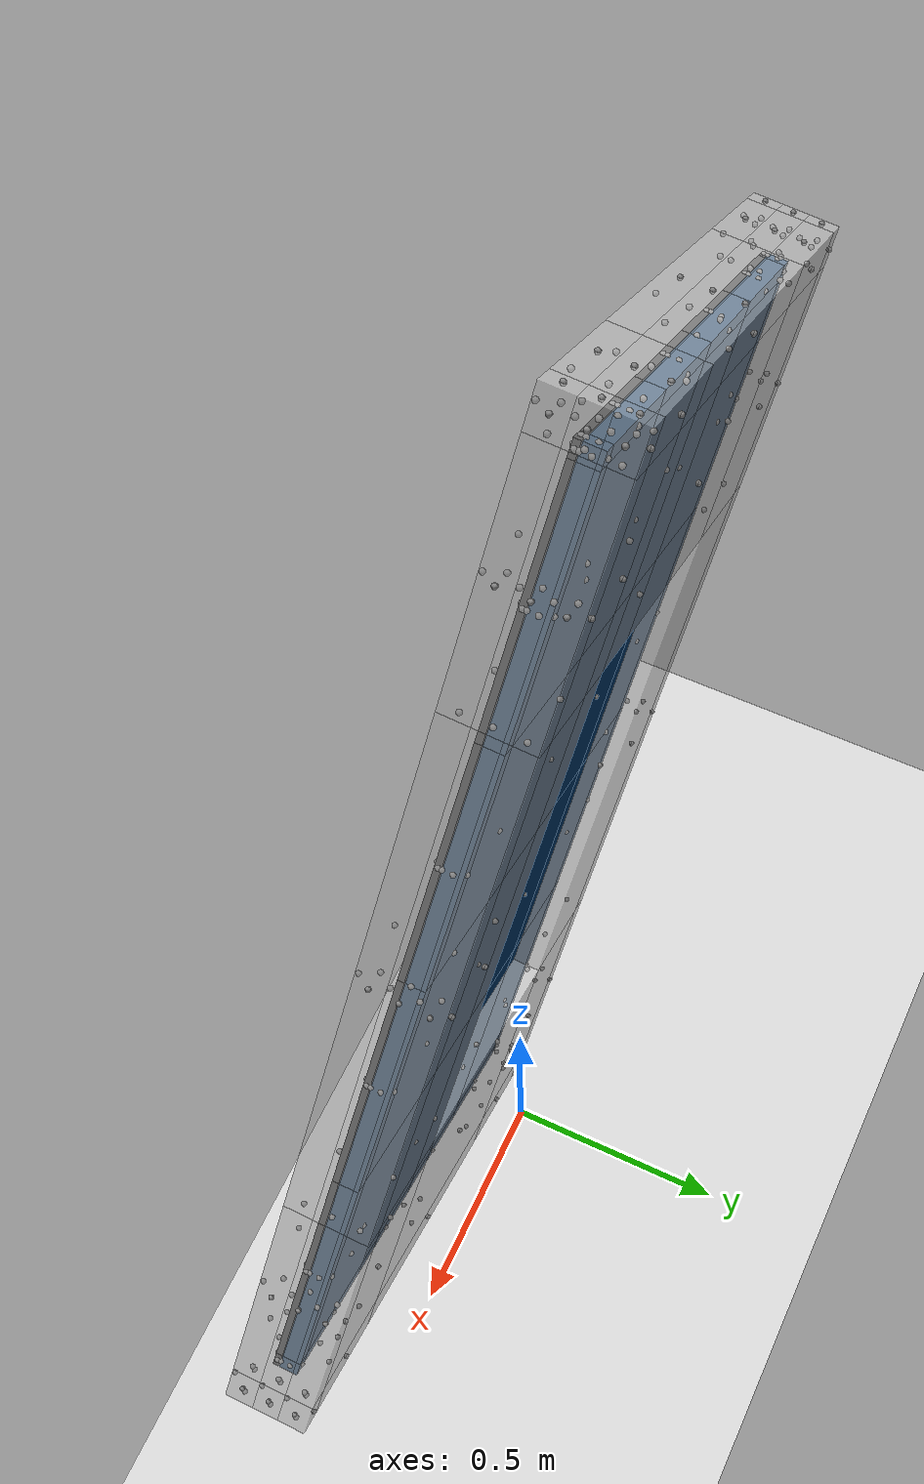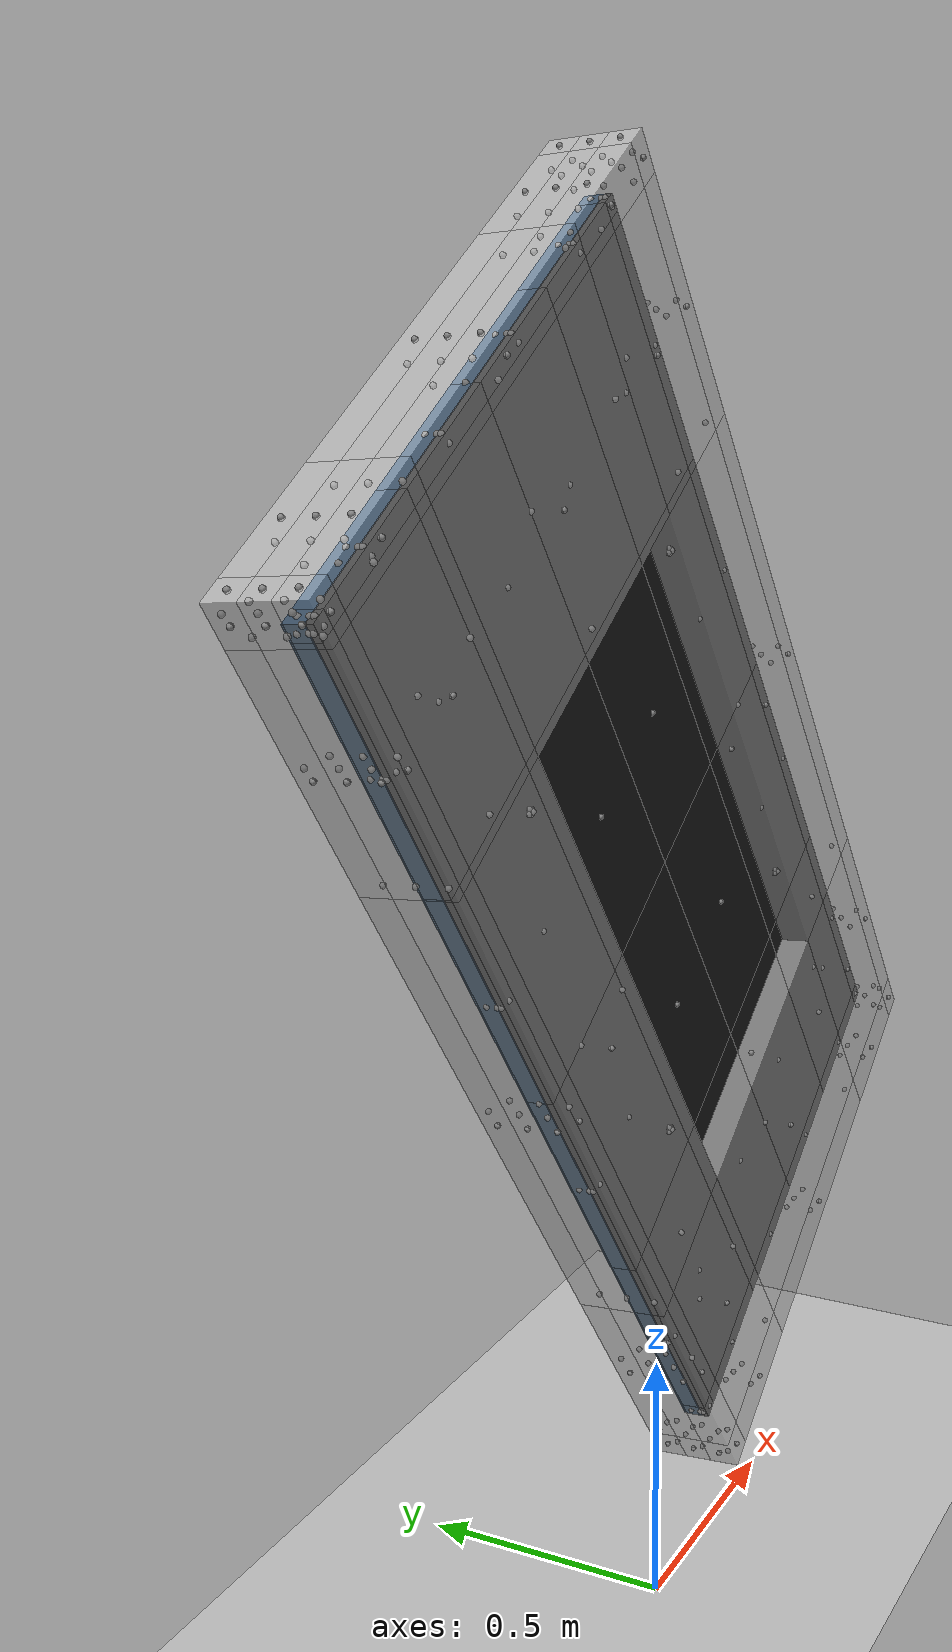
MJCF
<mujoco model="discrete_custom_box">
  <size memory="512M"/>
  <option integrator="implicitfast" timestep="0.0012" iterations="50" noslip_iterations="0" tolerance="1e-05" impratio="1.0" gravity="0 0 -9.81" density="1.225" viscosity="1.81e-05">
    <flag contact="enable"/>
  </option>
  <visual>
    <quality shadowsize="0"/>
    <global offwidth="0" offheight="0"/>
    <headlight active="1" ambient="0.1 0.1 0.1" diffuse="0.5 0.5 0.5" specular="0.07 0.07 0.07"/>
    <map znear="0.01" fogstart="3.0" fogend="10.0"/>
  </visual>
  <asset>
    <texture type="skybox" builtin="gradient" rgb1="0.6 0.6 0.6" rgb2="0.6 0.6 0.6" width="1024" height="1024"/>
    <texture type="2d" name="ground_tex" builtin="checker" mark="edge" rgb1="0.85 0.85 0.85" rgb2="0.75 0.75 0.75" markrgb="0.8 0.8 0.8" width="300" height="300"/>
    <material name="ground_mat" texture="ground_tex" texrepeat="5 5" texuniform="true" reflectance="0.0"/>
  </asset>
  <default>
    <joint armature="0.05" damping="1.0"/>
    <geom/>
    <default class="bpaperbox">
      <geom group="0" rgba="0.5 0.3 0.2 1.0" contype="0" conaffinity="0"/>
    </default>
    <default class="weld_bpaperbox">
      <equality solref="0.01 1.0" solimp="0.1 0.95 0.01 0.5 2"/>
    </default>
    <default class="bcushion">
      <geom group="1" rgba="0.8 0.8 0.8 0.6" contype="0" conaffinity="0"/>
    </default>
    <default class="bcushion_edge">
      <geom group="1" rgba="0.8 0.8 0.8 0.6" contype="0" conaffinity="0"/>
    </default>
    <default class="weld_bcushion">
      <equality solref="-55000.0 -800.0" solimp="0.1 0.95 0.02 0.5 2"/>
    </default>
    <default class="weld_bcushion_corner">
      <equality solref="-55000.0 -800.0" solimp="0.1 0.95 0.02 0.5 2"/>
    </default>
    <default class="bopencell">
      <geom group="2" rgba="0.1 0.1 0.1 1.0" contype="0" conaffinity="0"/>
    </default>
    <default class="weld_bopencell">
      <equality solref="-1579136.7041742974 -125.66370614359174" solimp="0.1 0.95 0.1 0.5 2"/>
    </default>
    <default class="bopencellcohesive">
      <geom group="2" rgba="1.0 0.0 0.0 0.4" contype="0" conaffinity="0"/>
    </default>
    <default class="weld_bopencellcohesive">
      <equality solref="-15000.0 -500.0" solimp="0.1 0.95 0.01 0.5 2"/>
    </default>
    <default class="bchassis">
      <geom group="2" rgba="0.0 0.2 0.4 1.0" contype="0" conaffinity="0"/>
    </default>
    <default class="weld_bchassis">
      <equality solref="-1579136.7041742974 -125.66370614359174" solimp="0.1 0.99 0.1 0.5 2"/>
    </default>
    <default class="bauxboxmass">
      <geom group="3" rgba="0.0 0.2 0.4 1.0" contype="0" conaffinity="0"/>
    </default>
    <default class="weld_bauxboxmass">
      <equality solref="0.02 1.0" solimp="0.1 0.95 0.005 0.5 2"/>
    </default>
    <default class="ground">
      <geom friction="1.0 1.0" solref="0.002 0.001" solimp="0.9 0.99 0.001" condim="3" contype="0" conaffinity="0" group="0" material="ground_mat"/>
    </default>
    <default class="cls_ground_cushion">
      <pair friction="0.5652798361925347 0.5652798361925347 0.005 0.0001 0.0001" solref="-12387.990874755948 -85.30828778688888" solimp="0.4580344438581963 0.7913009223088863 0.006506189553625513 0.5 2"/>
    </default>
    <default class="cls_ground_cushion_edge">
      <pair friction="0.5652798361925347 0.5652798361925347 0.005 0.0001 0.0001" solref="-12387.990874755948 -85.30828778688888" solimp="0.4580344438581963 0.7913009223088863 0.006506189553625513 0.5 2"/>
    </default>
    <default class="cls_ground_paper">
      <pair friction="0.5652798361925347 0.5652798361925347 0.005 0.0001 0.0001" solref="-12387.990874755948 -85.30828778688888" solimp="0.4580344438581963 0.7913009223088863 0.006506189553625513 0.5 2"/>
    </default>
    <default class="cls_cushion_opencell">
      <pair friction="0.5652798361925347 0.5652798361925347 0.005 0.0001 0.0001" solref="-4543.40088877404 -21.077417014683068" solimp="0.1 0.95 0.02 0.5 2"/>
    </default>
    <default class="cls_cushion_chassis">
      <pair friction="0.5652798361925347 0.5652798361925347 0.005 0.0001 0.0001" solref="-4543.40088877404 -21.077417014683068" solimp="0.1 0.95 0.02 0.5 2"/>
    </default>
    <default class="cls_cushion_paper">
      <pair friction="0.5652798361925347 0.5652798361925347 0.005 0.0001 0.0001" solref="0.001 1.0" solimp="0.1 0.95 0.02 0.5 2"/>
    </default>
  </default>
  <worldbody>
    <light pos="0 0 6" dir="0 0 -1" directional="false" diffuse="0.7 0.7 0.7" ambient="0.3 0.3 0.3" castshadow="false"/>
    <light pos="3 3 5" dir="-1 -1 -1" directional="false" diffuse="0.3 0.3 0.3" castshadow="false"/>
    <geom name="ground" type="plane" size="50 50 0.1" class="ground"/>
    <geom name="v_guide_vertical" type="cylinder" fromto="0 0 0 0 0 0.5" size="0.002" rgba="1 1 1 0.3" contype="0" conaffinity="0" group="1"/>
    <geom name="v_guide_tilted" type="cylinder" fromto="0 0 0 -0.0084 -0.0001 0.4999" size="0.003" rgba="1 1 0 0.5" contype="0" conaffinity="0" group="1"/>
    <geom name="v_guide_az_zero" type="cylinder" fromto="0 0 0.001 0.5 0 0.001" size="0.002" rgba="1 0 0 0.2" contype="0" conaffinity="0" group="1"/>
    <geom name="v_guide_az_target" type="cylinder" fromto="0 0 0.001 0.5000 0.0035 0.001" size="0.003" rgba="0 1 0 0.4" contype="0" conaffinity="0" group="1"/>
    <body name="BPackagingBox" pos="-0.01994 -0.00014 1.49344" axisangle="0.7704 0.4332 -0.4678 100.6506">
      <freejoint/>
      <geom type="box" size="0.001 0.001 0.001" mass="0.000021" rgba="0 0 0 0"/>
      <body name="BCushion">
        <body name="b_bcushion_0_0_0" pos="-0.98350 -0.56700 -0.05325">
          <joint type="slide" axis="1 0 0"/>
          <joint type="slide" axis="0 1 0"/>
          <joint type="slide" axis="0 0 1"/>
          <joint type="ball"/>
          <geom name="g_bcushion_0_0_0_edge" type="box" size="0.03650 0.02500 0.02775" mass="0.002768" class="bcushion_edge"/>
          <site name="s_BCushion_0_0_0_PX" pos="0.03650 0 0"/>
          <site name="s_BCushion_0_0_0_NX" pos="-0.03650 0 0"/>
          <site name="s_BCushion_0_0_0_PY" pos="0 0.02500 0"/>
          <site name="s_BCushion_0_0_0_NY" pos="0 -0.02500 0"/>
          <site name="s_BCushion_0_0_0_PZ" pos="0 0 0.02775"/>
          <site name="s_BCushion_0_0_0_NZ" pos="0 0 -0.02775"/>
        </body>
        <body name="b_bcushion_0_0_1" pos="-0.98350 -0.56700 0.00000">
          <joint type="slide" axis="1 0 0"/>
          <joint type="slide" axis="0 1 0"/>
          <joint type="slide" axis="0 0 1"/>
          <joint type="ball"/>
          <geom name="g_bcushion_0_0_1_edge" type="box" size="0.03650 0.02500 0.02550" mass="0.002544" class="bcushion_edge"/>
          <site name="s_BCushion_0_0_1_PX" pos="0.03650 0 0"/>
          <site name="s_BCushion_0_0_1_NX" pos="-0.03650 0 0"/>
          <site name="s_BCushion_0_0_1_PY" pos="0 0.02500 0"/>
          <site name="s_BCushion_0_0_1_NY" pos="0 -0.02500 0"/>
          <site name="s_BCushion_0_0_1_PZ" pos="0 0 0.02550"/>
          <site name="s_BCushion_0_0_1_NZ" pos="0 0 -0.02550"/>
        </body>
        <body name="b_bcushion_0_0_2" pos="-0.98350 -0.56700 0.05325">
          <joint type="slide" axis="1 0 0"/>
          <joint type="slide" axis="0 1 0"/>
          <joint type="slide" axis="0 0 1"/>
          <joint type="ball"/>
          <geom name="g_bcushion_0_0_2_edge" type="box" size="0.03650 0.02500 0.02775" mass="0.002768" class="bcushion_edge"/>
          <site name="s_BCushion_0_0_2_PX" pos="0.03650 0 0"/>
          <site name="s_BCushion_0_0_2_NX" pos="-0.03650 0 0"/>
          <site name="s_BCushion_0_0_2_PY" pos="0 0.02500 0"/>
          <site name="s_BCushion_0_0_2_NY" pos="0 -0.02500 0"/>
          <site name="s_BCushion_0_0_2_PZ" pos="0 0 0.02775"/>
          <site name="s_BCushion_0_0_2_NZ" pos="0 0 -0.02775"/>
        </body>
        <body name="b_bcushion_0_1_0" pos="-0.98350 -0.41900 -0.05325">
          <joint type="slide" axis="1 0 0"/>
          <joint type="slide" axis="0 1 0"/>
          <joint type="slide" axis="0 0 1"/>
          <joint type="ball"/>
          <geom name="g_bcushion_0_1_0" type="box" size="0.03650 0.12300 0.02775" mass="0.013619" class="bcushion"/>
          <site name="s_BCushion_0_1_0_PX" pos="0.03650 0 0"/>
          <site name="s_BCushion_0_1_0_NX" pos="-0.03650 0 0"/>
          <site name="s_BCushion_0_1_0_PY" pos="0 0.12300 0"/>
          <site name="s_BCushion_0_1_0_NY" pos="0 -0.12300 0"/>
          <site name="s_BCushion_0_1_0_PZ" pos="0 0 0.02775"/>
          <site name="s_BCushion_0_1_0_NZ" pos="0 0 -0.02775"/>
        </body>
        <body name="b_bcushion_0_1_1" pos="-0.98350 -0.41900 0.00000">
          <joint type="slide" axis="1 0 0"/>
          <joint type="slide" axis="0 1 0"/>
          <joint type="slide" axis="0 0 1"/>
          <joint type="ball"/>
          <geom name="g_bcushion_0_1_1" type="box" size="0.03650 0.12300 0.02550" mass="0.012514" class="bcushion"/>
          <site name="s_BCushion_0_1_1_PX" pos="0.03650 0 0"/>
          <site name="s_BCushion_0_1_1_NX" pos="-0.03650 0 0"/>
          <site name="s_BCushion_0_1_1_PY" pos="0 0.12300 0"/>
          <site name="s_BCushion_0_1_1_NY" pos="0 -0.12300 0"/>
          <site name="s_BCushion_0_1_1_PZ" pos="0 0 0.02550"/>
          <site name="s_BCushion_0_1_1_NZ" pos="0 0 -0.02550"/>
        </body>
        <body name="b_bcushion_0_1_2" pos="-0.98350 -0.41900 0.05325">
          <joint type="slide" axis="1 0 0"/>
          <joint type="slide" axis="0 1 0"/>
          <joint type="slide" axis="0 0 1"/>
          <joint type="ball"/>
          <geom name="g_bcushion_0_1_2" type="box" size="0.03650 0.12300 0.02775" mass="0.013619" class="bcushion"/>
          <site name="s_BCushion_0_1_2_PX" pos="0.03650 0 0"/>
          <site name="s_BCushion_0_1_2_NX" pos="-0.03650 0 0"/>
          <site name="s_BCushion_0_1_2_PY" pos="0 0.12300 0"/>
          <site name="s_BCushion_0_1_2_NY" pos="0 -0.12300 0"/>
          <site name="s_BCushion_0_1_2_PZ" pos="0 0 0.02775"/>
          <site name="s_BCushion_0_1_2_NZ" pos="0 0 -0.02775"/>
        </body>
        <body name="b_bcushion_0_2_0" pos="-0.98350 0.00000 -0.05325">
          <joint type="slide" axis="1 0 0"/>
          <joint type="slide" axis="0 1 0"/>
          <joint type="slide" axis="0 0 1"/>
          <joint type="ball"/>
          <geom name="g_bcushion_0_2_0" type="box" size="0.03650 0.29600 0.02775" mass="0.032773" class="bcushion"/>
          <site name="s_BCushion_0_2_0_PX" pos="0.03650 0 0"/>
          <site name="s_BCushion_0_2_0_NX" pos="-0.03650 0 0"/>
          <site name="s_BCushion_0_2_0_PY" pos="0 0.29600 0"/>
          <site name="s_BCushion_0_2_0_NY" pos="0 -0.29600 0"/>
          <site name="s_BCushion_0_2_0_PZ" pos="0 0 0.02775"/>
          <site name="s_BCushion_0_2_0_NZ" pos="0 0 -0.02775"/>
        </body>
        <body name="b_bcushion_0_2_1" pos="-0.98350 0.00000 0.00000">
          <joint type="slide" axis="1 0 0"/>
          <joint type="slide" axis="0 1 0"/>
          <joint type="slide" axis="0 0 1"/>
          <joint type="ball"/>
          <geom name="g_bcushion_0_2_1" type="box" size="0.03650 0.29600 0.02550" mass="0.030116" class="bcushion"/>
          <site name="s_BCushion_0_2_1_PX" pos="0.03650 0 0"/>
          <site name="s_BCushion_0_2_1_NX" pos="-0.03650 0 0"/>
          <site name="s_BCushion_0_2_1_PY" pos="0 0.29600 0"/>
          <site name="s_BCushion_0_2_1_NY" pos="0 -0.29600 0"/>
          <site name="s_BCushion_0_2_1_PZ" pos="0 0 0.02550"/>
          <site name="s_BCushion_0_2_1_NZ" pos="0 0 -0.02550"/>
        </body>
        <body name="b_bcushion_0_2_2" pos="-0.98350 0.00000 0.05325">
          <joint type="slide" axis="1 0 0"/>
          <joint type="slide" axis="0 1 0"/>
          <joint type="slide" axis="0 0 1"/>
          <joint type="ball"/>
          <geom name="g_bcushion_0_2_2" type="box" size="0.03650 0.29600 0.02775" mass="0.032773" class="bcushion"/>
          <site name="s_BCushion_0_2_2_PX" pos="0.03650 0 0"/>
          <site name="s_BCushion_0_2_2_NX" pos="-0.03650 0 0"/>
          <site name="s_BCushion_0_2_2_PY" pos="0 0.29600 0"/>
          <site name="s_BCushion_0_2_2_NY" pos="0 -0.29600 0"/>
          <site name="s_BCushion_0_2_2_PZ" pos="0 0 0.02775"/>
          <site name="s_BCushion_0_2_2_NZ" pos="0 0 -0.02775"/>
        </body>
        <body name="b_bcushion_0_3_0" pos="-0.98350 0.41900 -0.05325">
          <joint type="slide" axis="1 0 0"/>
          <joint type="slide" axis="0 1 0"/>
          <joint type="slide" axis="0 0 1"/>
          <joint type="ball"/>
          <geom name="g_bcushion_0_3_0" type="box" size="0.03650 0.12300 0.02775" mass="0.013619" class="bcushion"/>
          <site name="s_BCushion_0_3_0_PX" pos="0.03650 0 0"/>
          <site name="s_BCushion_0_3_0_NX" pos="-0.03650 0 0"/>
          <site name="s_BCushion_0_3_0_PY" pos="0 0.12300 0"/>
          <site name="s_BCushion_0_3_0_NY" pos="0 -0.12300 0"/>
          <site name="s_BCushion_0_3_0_PZ" pos="0 0 0.02775"/>
          <site name="s_BCushion_0_3_0_NZ" pos="0 0 -0.02775"/>
        </body>
        <body name="b_bcushion_0_3_1" pos="-0.98350 0.41900 0.00000">
          <joint type="slide" axis="1 0 0"/>
          <joint type="slide" axis="0 1 0"/>
          <joint type="slide" axis="0 0 1"/>
          <joint type="ball"/>
          <geom name="g_bcushion_0_3_1" type="box" size="0.03650 0.12300 0.02550" mass="0.012514" class="bcushion"/>
          <site name="s_BCushion_0_3_1_PX" pos="0.03650 0 0"/>
          <site name="s_BCushion_0_3_1_NX" pos="-0.03650 0 0"/>
          <site name="s_BCushion_0_3_1_PY" pos="0 0.12300 0"/>
          <site name="s_BCushion_0_3_1_NY" pos="0 -0.12300 0"/>
          <site name="s_BCushion_0_3_1_PZ" pos="0 0 0.02550"/>
          <site name="s_BCushion_0_3_1_NZ" pos="0 0 -0.02550"/>
        </body>
        <body name="b_bcushion_0_3_2" pos="-0.98350 0.41900 0.05325">
          <joint type="slide" axis="1 0 0"/>
          <joint type="slide" axis="0 1 0"/>
          <joint type="slide" axis="0 0 1"/>
          <joint type="ball"/>
          <geom name="g_bcushion_0_3_2" type="box" size="0.03650 0.12300 0.02775" mass="0.013619" class="bcushion"/>
          <site name="s_BCushion_0_3_2_PX" pos="0.03650 0 0"/>
          <site name="s_BCushion_0_3_2_NX" pos="-0.03650 0 0"/>
          <site name="s_BCushion_0_3_2_PY" pos="0 0.12300 0"/>
          <site name="s_BCushion_0_3_2_NY" pos="0 -0.12300 0"/>
          <site name="s_BCushion_0_3_2_PZ" pos="0 0 0.02775"/>
          <site name="s_BCushion_0_3_2_NZ" pos="0 0 -0.02775"/>
        </body>
        <body name="b_bcushion_0_4_0" pos="-0.98350 0.56700 -0.05325">
          <joint type="slide" axis="1 0 0"/>
          <joint type="slide" axis="0 1 0"/>
          <joint type="slide" axis="0 0 1"/>
          <joint type="ball"/>
          <geom name="g_bcushion_0_4_0_edge" type="box" size="0.03650 0.02500 0.02775" mass="0.002768" class="bcushion_edge"/>
          <site name="s_BCushion_0_4_0_PX" pos="0.03650 0 0"/>
          <site name="s_BCushion_0_4_0_NX" pos="-0.03650 0 0"/>
          <site name="s_BCushion_0_4_0_PY" pos="0 0.02500 0"/>
          <site name="s_BCushion_0_4_0_NY" pos="0 -0.02500 0"/>
          <site name="s_BCushion_0_4_0_PZ" pos="0 0 0.02775"/>
          <site name="s_BCushion_0_4_0_NZ" pos="0 0 -0.02775"/>
        </body>
        <body name="b_bcushion_0_4_1" pos="-0.98350 0.56700 0.00000">
          <joint type="slide" axis="1 0 0"/>
          <joint type="slide" axis="0 1 0"/>
          <joint type="slide" axis="0 0 1"/>
          <joint type="ball"/>
          <geom name="g_bcushion_0_4_1_edge" type="box" size="0.03650 0.02500 0.02550" mass="0.002544" class="bcushion_edge"/>
          <site name="s_BCushion_0_4_1_PX" pos="0.03650 0 0"/>
          <site name="s_BCushion_0_4_1_NX" pos="-0.03650 0 0"/>
          <site name="s_BCushion_0_4_1_PY" pos="0 0.02500 0"/>
          <site name="s_BCushion_0_4_1_NY" pos="0 -0.02500 0"/>
          <site name="s_BCushion_0_4_1_PZ" pos="0 0 0.02550"/>
          <site name="s_BCushion_0_4_1_NZ" pos="0 0 -0.02550"/>
        </body>
        <body name="b_bcushion_0_4_2" pos="-0.98350 0.56700 0.05325">
          <joint type="slide" axis="1 0 0"/>
          <joint type="slide" axis="0 1 0"/>
          <joint type="slide" axis="0 0 1"/>
          <joint type="ball"/>
          <geom name="g_bcushion_0_4_2_edge" type="box" size="0.03650 0.02500 0.02775" mass="0.002768" class="bcushion_edge"/>
          <site name="s_BCushion_0_4_2_PX" pos="0.03650 0 0"/>
          <site name="s_BCushion_0_4_2_NX" pos="-0.03650 0 0"/>
          <site name="s_BCushion_0_4_2_PY" pos="0 0.02500 0"/>
          <site name="s_BCushion_0_4_2_NY" pos="0 -0.02500 0"/>
          <site name="s_BCushion_0_4_2_PZ" pos="0 0 0.02775"/>
          <site name="s_BCushion_0_4_2_NZ" pos="0 0 -0.02775"/>
        </body>
        <body name="b_bcushion_1_0_0" pos="-0.72850 -0.56700 -0.05325">
          <joint type="slide" axis="1 0 0"/>
          <joint type="slide" axis="0 1 0"/>
          <joint type="slide" axis="0 0 1"/>
          <joint type="ball"/>
          <geom name="g_bcushion_1_0_0" type="box" size="0.21850 0.02500 0.02775" mass="0.016570" class="bcushion"/>
          <site name="s_BCushion_1_0_0_PX" pos="0.21850 0 0"/>
          <site name="s_BCushion_1_0_0_NX" pos="-0.21850 0 0"/>
          <site name="s_BCushion_1_0_0_PY" pos="0 0.02500 0"/>
          <site name="s_BCushion_1_0_0_NY" pos="0 -0.02500 0"/>
          <site name="s_BCushion_1_0_0_PZ" pos="0 0 0.02775"/>
          <site name="s_BCushion_1_0_0_NZ" pos="0 0 -0.02775"/>
        </body>
        <body name="b_bcushion_1_0_1" pos="-0.72850 -0.56700 0.00000">
          <joint type="slide" axis="1 0 0"/>
          <joint type="slide" axis="0 1 0"/>
          <joint type="slide" axis="0 0 1"/>
          <joint type="ball"/>
          <geom name="g_bcushion_1_0_1" type="box" size="0.21850 0.02500 0.02550" mass="0.015227" class="bcushion"/>
          <site name="s_BCushion_1_0_1_PX" pos="0.21850 0 0"/>
          <site name="s_BCushion_1_0_1_NX" pos="-0.21850 0 0"/>
          <site name="s_BCushion_1_0_1_PY" pos="0 0.02500 0"/>
          <site name="s_BCushion_1_0_1_NY" pos="0 -0.02500 0"/>
          <site name="s_BCushion_1_0_1_PZ" pos="0 0 0.02550"/>
          <site name="s_BCushion_1_0_1_NZ" pos="0 0 -0.02550"/>
        </body>
        <body name="b_bcushion_1_0_2" pos="-0.72850 -0.56700 0.05325">
          <joint type="slide" axis="1 0 0"/>
          <joint type="slide" axis="0 1 0"/>
          <joint type="slide" axis="0 0 1"/>
          <joint type="ball"/>
          <geom name="g_bcushion_1_0_2" type="box" size="0.21850 0.02500 0.02775" mass="0.016570" class="bcushion"/>
          <site name="s_BCushion_1_0_2_PX" pos="0.21850 0 0"/>
          <site name="s_BCushion_1_0_2_NX" pos="-0.21850 0 0"/>
          <site name="s_BCushion_1_0_2_PY" pos="0 0.02500 0"/>
          <site name="s_BCushion_1_0_2_NY" pos="0 -0.02500 0"/>
          <site name="s_BCushion_1_0_2_PZ" pos="0 0 0.02775"/>
          <site name="s_BCushion_1_0_2_NZ" pos="0 0 -0.02775"/>
        </body>
        <body name="b_bcushion_1_1_0" pos="-0.72850 -0.41900 -0.05325">
          <joint type="slide" axis="1 0 0"/>
          <joint type="slide" axis="0 1 0"/>
          <joint type="slide" axis="0 0 1"/>
          <joint type="ball"/>
          <geom name="g_bcushion_1_1_0" type="box" size="0.21850 0.12300 0.02775" mass="0.081525" class="bcushion"/>
          <site name="s_BCushion_1_1_0_PX" pos="0.21850 0 0"/>
          <site name="s_BCushion_1_1_0_NX" pos="-0.21850 0 0"/>
          <site name="s_BCushion_1_1_0_PY" pos="0 0.12300 0"/>
          <site name="s_BCushion_1_1_0_NY" pos="0 -0.12300 0"/>
          <site name="s_BCushion_1_1_0_PZ" pos="0 0 0.02775"/>
          <site name="s_BCushion_1_1_0_NZ" pos="0 0 -0.02775"/>
        </body>
        <body name="b_bcushion_1_1_2" pos="-0.72850 -0.41900 0.05325">
          <joint type="slide" axis="1 0 0"/>
          <joint type="slide" axis="0 1 0"/>
          <joint type="slide" axis="0 0 1"/>
          <joint type="ball"/>
          <geom name="g_bcushion_1_1_2" type="box" size="0.21850 0.12300 0.02775" mass="0.081525" class="bcushion"/>
          <site name="s_BCushion_1_1_2_PX" pos="0.21850 0 0"/>
          <site name="s_BCushion_1_1_2_NX" pos="-0.21850 0 0"/>
          <site name="s_BCushion_1_1_2_PY" pos="0 0.12300 0"/>
          <site name="s_BCushion_1_1_2_NY" pos="0 -0.12300 0"/>
          <site name="s_BCushion_1_1_2_PZ" pos="0 0 0.02775"/>
          <site name="s_BCushion_1_1_2_NZ" pos="0 0 -0.02775"/>
        </body>
        <body name="b_bcushion_1_2_0" pos="-0.72850 0.00000 -0.05325">
          <joint type="slide" axis="1 0 0"/>
          <joint type="slide" axis="0 1 0"/>
          <joint type="slide" axis="0 0 1"/>
          <joint type="ball"/>
          <geom name="g_bcushion_1_2_0" type="box" size="0.21850 0.29600 0.02775" mass="0.196189" class="bcushion"/>
          <site name="s_BCushion_1_2_0_PX" pos="0.21850 0 0"/>
          <site name="s_BCushion_1_2_0_NX" pos="-0.21850 0 0"/>
          <site name="s_BCushion_1_2_0_PY" pos="0 0.29600 0"/>
          <site name="s_BCushion_1_2_0_NY" pos="0 -0.29600 0"/>
          <site name="s_BCushion_1_2_0_PZ" pos="0 0 0.02775"/>
          <site name="s_BCushion_1_2_0_NZ" pos="0 0 -0.02775"/>
        </body>
        <body name="b_bcushion_1_2_2" pos="-0.72850 0.00000 0.05325">
          <joint type="slide" axis="1 0 0"/>
          <joint type="slide" axis="0 1 0"/>
          <joint type="slide" axis="0 0 1"/>
          <joint type="ball"/>
          <geom name="g_bcushion_1_2_2" type="box" size="0.21850 0.29600 0.02775" mass="0.196189" class="bcushion"/>
          <site name="s_BCushion_1_2_2_PX" pos="0.21850 0 0"/>
          <site name="s_BCushion_1_2_2_NX" pos="-0.21850 0 0"/>
          <site name="s_BCushion_1_2_2_PY" pos="0 0.29600 0"/>
          <site name="s_BCushion_1_2_2_NY" pos="0 -0.29600 0"/>
          <site name="s_BCushion_1_2_2_PZ" pos="0 0 0.02775"/>
          <site name="s_BCushion_1_2_2_NZ" pos="0 0 -0.02775"/>
        </body>
        <body name="b_bcushion_1_3_0" pos="-0.72850 0.41900 -0.05325">
          <joint type="slide" axis="1 0 0"/>
          <joint type="slide" axis="0 1 0"/>
          <joint type="slide" axis="0 0 1"/>
          <joint type="ball"/>
          <geom name="g_bcushion_1_3_0" type="box" size="0.21850 0.12300 0.02775" mass="0.081525" class="bcushion"/>
          <site name="s_BCushion_1_3_0_PX" pos="0.21850 0 0"/>
          <site name="s_BCushion_1_3_0_NX" pos="-0.21850 0 0"/>
          <site name="s_BCushion_1_3_0_PY" pos="0 0.12300 0"/>
          <site name="s_BCushion_1_3_0_NY" pos="0 -0.12300 0"/>
          <site name="s_BCushion_1_3_0_PZ" pos="0 0 0.02775"/>
          <site name="s_BCushion_1_3_0_NZ" pos="0 0 -0.02775"/>
        </body>
        <body name="b_bcushion_1_3_2" pos="-0.72850 0.41900 0.05325">
          <joint type="slide" axis="1 0 0"/>
          <joint type="slide" axis="0 1 0"/>
          <joint type="slide" axis="0 0 1"/>
          <joint type="ball"/>
          <geom name="g_bcushion_1_3_2" type="box" size="0.21850 0.12300 0.02775" mass="0.081525" class="bcushion"/>
          <site name="s_BCushion_1_3_2_PX" pos="0.21850 0 0"/>
          <site name="s_BCushion_1_3_2_NX" pos="-0.21850 0 0"/>
          <site name="s_BCushion_1_3_2_PY" pos="0 0.12300 0"/>
          <site name="s_BCushion_1_3_2_NY" pos="0 -0.12300 0"/>
          <site name="s_BCushion_1_3_2_PZ" pos="0 0 0.02775"/>
          <site name="s_BCushion_1_3_2_NZ" pos="0 0 -0.02775"/>
        </body>
        <body name="b_bcushion_1_4_0" pos="-0.72850 0.56700 -0.05325">
          <joint type="slide" axis="1 0 0"/>
          <joint type="slide" axis="0 1 0"/>
          <joint type="slide" axis="0 0 1"/>
          <joint type="ball"/>
          <geom name="g_bcushion_1_4_0" type="box" size="0.21850 0.02500 0.02775" mass="0.016570" class="bcushion"/>
          <site name="s_BCushion_1_4_0_PX" pos="0.21850 0 0"/>
          <site name="s_BCushion_1_4_0_NX" pos="-0.21850 0 0"/>
          <site name="s_BCushion_1_4_0_PY" pos="0 0.02500 0"/>
          <site name="s_BCushion_1_4_0_NY" pos="0 -0.02500 0"/>
          <site name="s_BCushion_1_4_0_PZ" pos="0 0 0.02775"/>
          <site name="s_BCushion_1_4_0_NZ" pos="0 0 -0.02775"/>
        </body>
        <body name="b_bcushion_1_4_1" pos="-0.72850 0.56700 0.00000">
          <joint type="slide" axis="1 0 0"/>
          <joint type="slide" axis="0 1 0"/>
          <joint type="slide" axis="0 0 1"/>
          <joint type="ball"/>
          <geom name="g_bcushion_1_4_1" type="box" size="0.21850 0.02500 0.02550" mass="0.015227" class="bcushion"/>
          <site name="s_BCushion_1_4_1_PX" pos="0.21850 0 0"/>
          <site name="s_BCushion_1_4_1_NX" pos="-0.21850 0 0"/>
          <site name="s_BCushion_1_4_1_PY" pos="0 0.02500 0"/>
          <site name="s_BCushion_1_4_1_NY" pos="0 -0.02500 0"/>
          <site name="s_BCushion_1_4_1_PZ" pos="0 0 0.02550"/>
          <site name="s_BCushion_1_4_1_NZ" pos="0 0 -0.02550"/>
        </body>
        <body name="b_bcushion_1_4_2" pos="-0.72850 0.56700 0.05325">
          <joint type="slide" axis="1 0 0"/>
          <joint type="slide" axis="0 1 0"/>
          <joint type="slide" axis="0 0 1"/>
          <joint type="ball"/>
          <geom name="g_bcushion_1_4_2" type="box" size="0.21850 0.02500 0.02775" mass="0.016570" class="bcushion"/>
          <site name="s_BCushion_1_4_2_PX" pos="0.21850 0 0"/>
          <site name="s_BCushion_1_4_2_NX" pos="-0.21850 0 0"/>
          <site name="s_BCushion_1_4_2_PY" pos="0 0.02500 0"/>
          <site name="s_BCushion_1_4_2_NY" pos="0 -0.02500 0"/>
          <site name="s_BCushion_1_4_2_PZ" pos="0 0 0.02775"/>
          <site name="s_BCushion_1_4_2_NZ" pos="0 0 -0.02775"/>
        </body>
        <body name="b_bcushion_2_0_0" pos="0.00000 -0.56700 -0.05325">
          <joint type="slide" axis="1 0 0"/>
          <joint type="slide" axis="0 1 0"/>
          <joint type="slide" axis="0 0 1"/>
          <joint type="ball"/>
          <geom name="g_bcushion_2_0_0" type="box" size="0.51000 0.02500 0.02775" mass="0.038676" class="bcushion"/>
          <site name="s_BCushion_2_0_0_PX" pos="0.51000 0 0"/>
          <site name="s_BCushion_2_0_0_NX" pos="-0.51000 0 0"/>
          <site name="s_BCushion_2_0_0_PY" pos="0 0.02500 0"/>
          <site name="s_BCushion_2_0_0_NY" pos="0 -0.02500 0"/>
          <site name="s_BCushion_2_0_0_PZ" pos="0 0 0.02775"/>
          <site name="s_BCushion_2_0_0_NZ" pos="0 0 -0.02775"/>
        </body>
        <body name="b_bcushion_2_0_1" pos="0.00000 -0.56700 0.00000">
          <joint type="slide" axis="1 0 0"/>
          <joint type="slide" axis="0 1 0"/>
          <joint type="slide" axis="0 0 1"/>
          <joint type="ball"/>
          <geom name="g_bcushion_2_0_1" type="box" size="0.51000 0.02500 0.02550" mass="0.035540" class="bcushion"/>
          <site name="s_BCushion_2_0_1_PX" pos="0.51000 0 0"/>
          <site name="s_BCushion_2_0_1_NX" pos="-0.51000 0 0"/>
          <site name="s_BCushion_2_0_1_PY" pos="0 0.02500 0"/>
          <site name="s_BCushion_2_0_1_NY" pos="0 -0.02500 0"/>
          <site name="s_BCushion_2_0_1_PZ" pos="0 0 0.02550"/>
          <site name="s_BCushion_2_0_1_NZ" pos="0 0 -0.02550"/>
        </body>
        <body name="b_bcushion_2_0_2" pos="0.00000 -0.56700 0.05325">
          <joint type="slide" axis="1 0 0"/>
          <joint type="slide" axis="0 1 0"/>
          <joint type="slide" axis="0 0 1"/>
          <joint type="ball"/>
          <geom name="g_bcushion_2_0_2" type="box" size="0.51000 0.02500 0.02775" mass="0.038676" class="bcushion"/>
          <site name="s_BCushion_2_0_2_PX" pos="0.51000 0 0"/>
          <site name="s_BCushion_2_0_2_NX" pos="-0.51000 0 0"/>
          <site name="s_BCushion_2_0_2_PY" pos="0 0.02500 0"/>
          <site name="s_BCushion_2_0_2_NY" pos="0 -0.02500 0"/>
          <site name="s_BCushion_2_0_2_PZ" pos="0 0 0.02775"/>
          <site name="s_BCushion_2_0_2_NZ" pos="0 0 -0.02775"/>
        </body>
        <body name="b_bcushion_2_1_0" pos="0.00000 -0.41900 -0.05325">
          <joint type="slide" axis="1 0 0"/>
          <joint type="slide" axis="0 1 0"/>
          <joint type="slide" axis="0 0 1"/>
          <joint type="ball"/>
          <geom name="g_bcushion_2_1_0" type="box" size="0.51000 0.12300 0.02775" mass="0.190286" class="bcushion"/>
          <site name="s_BCushion_2_1_0_PX" pos="0.51000 0 0"/>
          <site name="s_BCushion_2_1_0_NX" pos="-0.51000 0 0"/>
          <site name="s_BCushion_2_1_0_PY" pos="0 0.12300 0"/>
          <site name="s_BCushion_2_1_0_NY" pos="0 -0.12300 0"/>
          <site name="s_BCushion_2_1_0_PZ" pos="0 0 0.02775"/>
          <site name="s_BCushion_2_1_0_NZ" pos="0 0 -0.02775"/>
        </body>
        <body name="b_bcushion_2_1_2" pos="0.00000 -0.41900 0.05325">
          <joint type="slide" axis="1 0 0"/>
          <joint type="slide" axis="0 1 0"/>
          <joint type="slide" axis="0 0 1"/>
          <joint type="ball"/>
          <geom name="g_bcushion_2_1_2" type="box" size="0.51000 0.12300 0.02775" mass="0.190286" class="bcushion"/>
          <site name="s_BCushion_2_1_2_PX" pos="0.51000 0 0"/>
          <site name="s_BCushion_2_1_2_NX" pos="-0.51000 0 0"/>
          <site name="s_BCushion_2_1_2_PY" pos="0 0.12300 0"/>
          <site name="s_BCushion_2_1_2_NY" pos="0 -0.12300 0"/>
          <site name="s_BCushion_2_1_2_PZ" pos="0 0 0.02775"/>
          <site name="s_BCushion_2_1_2_NZ" pos="0 0 -0.02775"/>
        </body>
        <body name="b_bcushion_2_3_0" pos="0.00000 0.41900 -0.05325">
          <joint type="slide" axis="1 0 0"/>
          <joint type="slide" axis="0 1 0"/>
          <joint type="slide" axis="0 0 1"/>
          <joint type="ball"/>
          <geom name="g_bcushion_2_3_0" type="box" size="0.51000 0.12300 0.02775" mass="0.190286" class="bcushion"/>
          <site name="s_BCushion_2_3_0_PX" pos="0.51000 0 0"/>
          <site name="s_BCushion_2_3_0_NX" pos="-0.51000 0 0"/>
          <site name="s_BCushion_2_3_0_PY" pos="0 0.12300 0"/>
          <site name="s_BCushion_2_3_0_NY" pos="0 -0.12300 0"/>
          <site name="s_BCushion_2_3_0_PZ" pos="0 0 0.02775"/>
          <site name="s_BCushion_2_3_0_NZ" pos="0 0 -0.02775"/>
        </body>
        <body name="b_bcushion_2_3_2" pos="0.00000 0.41900 0.05325">
          <joint type="slide" axis="1 0 0"/>
          <joint type="slide" axis="0 1 0"/>
          <joint type="slide" axis="0 0 1"/>
          <joint type="ball"/>
          <geom name="g_bcushion_2_3_2" type="box" size="0.51000 0.12300 0.02775" mass="0.190286" class="bcushion"/>
          <site name="s_BCushion_2_3_2_PX" pos="0.51000 0 0"/>
          <site name="s_BCushion_2_3_2_NX" pos="-0.51000 0 0"/>
          <site name="s_BCushion_2_3_2_PY" pos="0 0.12300 0"/>
          <site name="s_BCushion_2_3_2_NY" pos="0 -0.12300 0"/>
          <site name="s_BCushion_2_3_2_PZ" pos="0 0 0.02775"/>
          <site name="s_BCushion_2_3_2_NZ" pos="0 0 -0.02775"/>
        </body>
        <body name="b_bcushion_2_4_0" pos="0.00000 0.56700 -0.05325">
          <joint type="slide" axis="1 0 0"/>
          <joint type="slide" axis="0 1 0"/>
          <joint type="slide" axis="0 0 1"/>
          <joint type="ball"/>
          <geom name="g_bcushion_2_4_0" type="box" size="0.51000 0.02500 0.02775" mass="0.038676" class="bcushion"/>
          <site name="s_BCushion_2_4_0_PX" pos="0.51000 0 0"/>
          <site name="s_BCushion_2_4_0_NX" pos="-0.51000 0 0"/>
          <site name="s_BCushion_2_4_0_PY" pos="0 0.02500 0"/>
          <site name="s_BCushion_2_4_0_NY" pos="0 -0.02500 0"/>
          <site name="s_BCushion_2_4_0_PZ" pos="0 0 0.02775"/>
          <site name="s_BCushion_2_4_0_NZ" pos="0 0 -0.02775"/>
        </body>
        <body name="b_bcushion_2_4_1" pos="0.00000 0.56700 0.00000">
          <joint type="slide" axis="1 0 0"/>
          <joint type="slide" axis="0 1 0"/>
          <joint type="slide" axis="0 0 1"/>
          <joint type="ball"/>
          <geom name="g_bcushion_2_4_1" type="box" size="0.51000 0.02500 0.02550" mass="0.035540" class="bcushion"/>
          <site name="s_BCushion_2_4_1_PX" pos="0.51000 0 0"/>
          <site name="s_BCushion_2_4_1_NX" pos="-0.51000 0 0"/>
          <site name="s_BCushion_2_4_1_PY" pos="0 0.02500 0"/>
          <site name="s_BCushion_2_4_1_NY" pos="0 -0.02500 0"/>
          <site name="s_BCushion_2_4_1_PZ" pos="0 0 0.02550"/>
          <site name="s_BCushion_2_4_1_NZ" pos="0 0 -0.02550"/>
        </body>
        <body name="b_bcushion_2_4_2" pos="0.00000 0.56700 0.05325">
          <joint type="slide" axis="1 0 0"/>
          <joint type="slide" axis="0 1 0"/>
          <joint type="slide" axis="0 0 1"/>
          <joint type="ball"/>
          <geom name="g_bcushion_2_4_2" type="box" size="0.51000 0.02500 0.02775" mass="0.038676" class="bcushion"/>
          <site name="s_BCushion_2_4_2_PX" pos="0.51000 0 0"/>
          <site name="s_BCushion_2_4_2_NX" pos="-0.51000 0 0"/>
          <site name="s_BCushion_2_4_2_PY" pos="0 0.02500 0"/>
          <site name="s_BCushion_2_4_2_NY" pos="0 -0.02500 0"/>
          <site name="s_BCushion_2_4_2_PZ" pos="0 0 0.02775"/>
          <site name="s_BCushion_2_4_2_NZ" pos="0 0 -0.02775"/>
        </body>
        <body name="b_bcushion_3_0_0" pos="0.72850 -0.56700 -0.05325">
          <joint type="slide" axis="1 0 0"/>
          <joint type="slide" axis="0 1 0"/>
          <joint type="slide" axis="0 0 1"/>
          <joint type="ball"/>
          <geom name="g_bcushion_3_0_0" type="box" size="0.21850 0.02500 0.02775" mass="0.016570" class="bcushion"/>
          <site name="s_BCushion_3_0_0_PX" pos="0.21850 0 0"/>
          <site name="s_BCushion_3_0_0_NX" pos="-0.21850 0 0"/>
          <site name="s_BCushion_3_0_0_PY" pos="0 0.02500 0"/>
          <site name="s_BCushion_3_0_0_NY" pos="0 -0.02500 0"/>
          <site name="s_BCushion_3_0_0_PZ" pos="0 0 0.02775"/>
          <site name="s_BCushion_3_0_0_NZ" pos="0 0 -0.02775"/>
        </body>
        <body name="b_bcushion_3_0_1" pos="0.72850 -0.56700 0.00000">
          <joint type="slide" axis="1 0 0"/>
          <joint type="slide" axis="0 1 0"/>
          <joint type="slide" axis="0 0 1"/>
          <joint type="ball"/>
          <geom name="g_bcushion_3_0_1" type="box" size="0.21850 0.02500 0.02550" mass="0.015227" class="bcushion"/>
          <site name="s_BCushion_3_0_1_PX" pos="0.21850 0 0"/>
          <site name="s_BCushion_3_0_1_NX" pos="-0.21850 0 0"/>
          <site name="s_BCushion_3_0_1_PY" pos="0 0.02500 0"/>
          <site name="s_BCushion_3_0_1_NY" pos="0 -0.02500 0"/>
          <site name="s_BCushion_3_0_1_PZ" pos="0 0 0.02550"/>
          <site name="s_BCushion_3_0_1_NZ" pos="0 0 -0.02550"/>
        </body>
        <body name="b_bcushion_3_0_2" pos="0.72850 -0.56700 0.05325">
          <joint type="slide" axis="1 0 0"/>
          <joint type="slide" axis="0 1 0"/>
          <joint type="slide" axis="0 0 1"/>
          <joint type="ball"/>
          <geom name="g_bcushion_3_0_2" type="box" size="0.21850 0.02500 0.02775" mass="0.016570" class="bcushion"/>
          <site name="s_BCushion_3_0_2_PX" pos="0.21850 0 0"/>
          <site name="s_BCushion_3_0_2_NX" pos="-0.21850 0 0"/>
          <site name="s_BCushion_3_0_2_PY" pos="0 0.02500 0"/>
          <site name="s_BCushion_3_0_2_NY" pos="0 -0.02500 0"/>
          <site name="s_BCushion_3_0_2_PZ" pos="0 0 0.02775"/>
          <site name="s_BCushion_3_0_2_NZ" pos="0 0 -0.02775"/>
        </body>
        <body name="b_bcushion_3_1_0" pos="0.72850 -0.41900 -0.05325">
          <joint type="slide" axis="1 0 0"/>
          <joint type="slide" axis="0 1 0"/>
          <joint type="slide" axis="0 0 1"/>
          <joint type="ball"/>
          <geom name="g_bcushion_3_1_0" type="box" size="0.21850 0.12300 0.02775" mass="0.081525" class="bcushion"/>
          <site name="s_BCushion_3_1_0_PX" pos="0.21850 0 0"/>
          <site name="s_BCushion_3_1_0_NX" pos="-0.21850 0 0"/>
          <site name="s_BCushion_3_1_0_PY" pos="0 0.12300 0"/>
          <site name="s_BCushion_3_1_0_NY" pos="0 -0.12300 0"/>
          <site name="s_BCushion_3_1_0_PZ" pos="0 0 0.02775"/>
          <site name="s_BCushion_3_1_0_NZ" pos="0 0 -0.02775"/>
        </body>
        <body name="b_bcushion_3_1_2" pos="0.72850 -0.41900 0.05325">
          <joint type="slide" axis="1 0 0"/>
          <joint type="slide" axis="0 1 0"/>
          <joint type="slide" axis="0 0 1"/>
          <joint type="ball"/>
          <geom name="g_bcushion_3_1_2" type="box" size="0.21850 0.12300 0.02775" mass="0.081525" class="bcushion"/>
          <site name="s_BCushion_3_1_2_PX" pos="0.21850 0 0"/>
          <site name="s_BCushion_3_1_2_NX" pos="-0.21850 0 0"/>
          <site name="s_BCushion_3_1_2_PY" pos="0 0.12300 0"/>
          <site name="s_BCushion_3_1_2_NY" pos="0 -0.12300 0"/>
          <site name="s_BCushion_3_1_2_PZ" pos="0 0 0.02775"/>
          <site name="s_BCushion_3_1_2_NZ" pos="0 0 -0.02775"/>
        </body>
        <body name="b_bcushion_3_2_0" pos="0.72850 0.00000 -0.05325">
          <joint type="slide" axis="1 0 0"/>
          <joint type="slide" axis="0 1 0"/>
          <joint type="slide" axis="0 0 1"/>
          <joint type="ball"/>
          <geom name="g_bcushion_3_2_0" type="box" size="0.21850 0.29600 0.02775" mass="0.196189" class="bcushion"/>
          <site name="s_BCushion_3_2_0_PX" pos="0.21850 0 0"/>
          <site name="s_BCushion_3_2_0_NX" pos="-0.21850 0 0"/>
          <site name="s_BCushion_3_2_0_PY" pos="0 0.29600 0"/>
          <site name="s_BCushion_3_2_0_NY" pos="0 -0.29600 0"/>
          <site name="s_BCushion_3_2_0_PZ" pos="0 0 0.02775"/>
          <site name="s_BCushion_3_2_0_NZ" pos="0 0 -0.02775"/>
        </body>
        <body name="b_bcushion_3_2_2" pos="0.72850 0.00000 0.05325">
          <joint type="slide" axis="1 0 0"/>
          <joint type="slide" axis="0 1 0"/>
          <joint type="slide" axis="0 0 1"/>
          <joint type="ball"/>
          <geom name="g_bcushion_3_2_2" type="box" size="0.21850 0.29600 0.02775" mass="0.196189" class="bcushion"/>
          <site name="s_BCushion_3_2_2_PX" pos="0.21850 0 0"/>
          <site name="s_BCushion_3_2_2_NX" pos="-0.21850 0 0"/>
          <site name="s_BCushion_3_2_2_PY" pos="0 0.29600 0"/>
          <site name="s_BCushion_3_2_2_NY" pos="0 -0.29600 0"/>
          <site name="s_BCushion_3_2_2_PZ" pos="0 0 0.02775"/>
          <site name="s_BCushion_3_2_2_NZ" pos="0 0 -0.02775"/>
        </body>
        <body name="b_bcushion_3_3_0" pos="0.72850 0.41900 -0.05325">
          <joint type="slide" axis="1 0 0"/>
          <joint type="slide" axis="0 1 0"/>
          <joint type="slide" axis="0 0 1"/>
          <joint type="ball"/>
          <geom name="g_bcushion_3_3_0" type="box" size="0.21850 0.12300 0.02775" mass="0.081525" class="bcushion"/>
          <site name="s_BCushion_3_3_0_PX" pos="0.21850 0 0"/>
          <site name="s_BCushion_3_3_0_NX" pos="-0.21850 0 0"/>
          <site name="s_BCushion_3_3_0_PY" pos="0 0.12300 0"/>
          <site name="s_BCushion_3_3_0_NY" pos="0 -0.12300 0"/>
          <site name="s_BCushion_3_3_0_PZ" pos="0 0 0.02775"/>
          <site name="s_BCushion_3_3_0_NZ" pos="0 0 -0.02775"/>
        </body>
        <body name="b_bcushion_3_3_2" pos="0.72850 0.41900 0.05325">
          <joint type="slide" axis="1 0 0"/>
          <joint type="slide" axis="0 1 0"/>
          <joint type="slide" axis="0 0 1"/>
          <joint type="ball"/>
          <geom name="g_bcushion_3_3_2" type="box" size="0.21850 0.12300 0.02775" mass="0.081525" class="bcushion"/>
          <site name="s_BCushion_3_3_2_PX" pos="0.21850 0 0"/>
          <site name="s_BCushion_3_3_2_NX" pos="-0.21850 0 0"/>
          <site name="s_BCushion_3_3_2_PY" pos="0 0.12300 0"/>
          <site name="s_BCushion_3_3_2_NY" pos="0 -0.12300 0"/>
          <site name="s_BCushion_3_3_2_PZ" pos="0 0 0.02775"/>
          <site name="s_BCushion_3_3_2_NZ" pos="0 0 -0.02775"/>
        </body>
        <body name="b_bcushion_3_4_0" pos="0.72850 0.56700 -0.05325">
          <joint type="slide" axis="1 0 0"/>
          <joint type="slide" axis="0 1 0"/>
          <joint type="slide" axis="0 0 1"/>
          <joint type="ball"/>
          <geom name="g_bcushion_3_4_0" type="box" size="0.21850 0.02500 0.02775" mass="0.016570" class="bcushion"/>
          <site name="s_BCushion_3_4_0_PX" pos="0.21850 0 0"/>
          <site name="s_BCushion_3_4_0_NX" pos="-0.21850 0 0"/>
          <site name="s_BCushion_3_4_0_PY" pos="0 0.02500 0"/>
          <site name="s_BCushion_3_4_0_NY" pos="0 -0.02500 0"/>
          <site name="s_BCushion_3_4_0_PZ" pos="0 0 0.02775"/>
          <site name="s_BCushion_3_4_0_NZ" pos="0 0 -0.02775"/>
        </body>
        <body name="b_bcushion_3_4_1" pos="0.72850 0.56700 0.00000">
          <joint type="slide" axis="1 0 0"/>
          <joint type="slide" axis="0 1 0"/>
          <joint type="slide" axis="0 0 1"/>
          <joint type="ball"/>
          <geom name="g_bcushion_3_4_1" type="box" size="0.21850 0.02500 0.02550" mass="0.015227" class="bcushion"/>
          <site name="s_BCushion_3_4_1_PX" pos="0.21850 0 0"/>
          <site name="s_BCushion_3_4_1_NX" pos="-0.21850 0 0"/>
          <site name="s_BCushion_3_4_1_PY" pos="0 0.02500 0"/>
          <site name="s_BCushion_3_4_1_NY" pos="0 -0.02500 0"/>
          <site name="s_BCushion_3_4_1_PZ" pos="0 0 0.02550"/>
          <site name="s_BCushion_3_4_1_NZ" pos="0 0 -0.02550"/>
        </body>
        <body name="b_bcushion_3_4_2" pos="0.72850 0.56700 0.05325">
          <joint type="slide" axis="1 0 0"/>
          <joint type="slide" axis="0 1 0"/>
          <joint type="slide" axis="0 0 1"/>
          <joint type="ball"/>
          <geom name="g_bcushion_3_4_2" type="box" size="0.21850 0.02500 0.02775" mass="0.016570" class="bcushion"/>
          <site name="s_BCushion_3_4_2_PX" pos="0.21850 0 0"/>
          <site name="s_BCushion_3_4_2_NX" pos="-0.21850 0 0"/>
          <site name="s_BCushion_3_4_2_PY" pos="0 0.02500 0"/>
          <site name="s_BCushion_3_4_2_NY" pos="0 -0.02500 0"/>
          <site name="s_BCushion_3_4_2_PZ" pos="0 0 0.02775"/>
          <site name="s_BCushion_3_4_2_NZ" pos="0 0 -0.02775"/>
        </body>
        <body name="b_bcushion_4_0_0" pos="0.98350 -0.56700 -0.05325">
          <joint type="slide" axis="1 0 0"/>
          <joint type="slide" axis="0 1 0"/>
          <joint type="slide" axis="0 0 1"/>
          <joint type="ball"/>
          <geom name="g_bcushion_4_0_0_edge" type="box" size="0.03650 0.02500 0.02775" mass="0.002768" class="bcushion_edge"/>
          <site name="s_BCushion_4_0_0_PX" pos="0.03650 0 0"/>
          <site name="s_BCushion_4_0_0_NX" pos="-0.03650 0 0"/>
          <site name="s_BCushion_4_0_0_PY" pos="0 0.02500 0"/>
          <site name="s_BCushion_4_0_0_NY" pos="0 -0.02500 0"/>
          <site name="s_BCushion_4_0_0_PZ" pos="0 0 0.02775"/>
          <site name="s_BCushion_4_0_0_NZ" pos="0 0 -0.02775"/>
        </body>
        <body name="b_bcushion_4_0_1" pos="0.98350 -0.56700 0.00000">
          <joint type="slide" axis="1 0 0"/>
          <joint type="slide" axis="0 1 0"/>
          <joint type="slide" axis="0 0 1"/>
          <joint type="ball"/>
          <geom name="g_bcushion_4_0_1_edge" type="box" size="0.03650 0.02500 0.02550" mass="0.002544" class="bcushion_edge"/>
          <site name="s_BCushion_4_0_1_PX" pos="0.03650 0 0"/>
          <site name="s_BCushion_4_0_1_NX" pos="-0.03650 0 0"/>
          <site name="s_BCushion_4_0_1_PY" pos="0 0.02500 0"/>
          <site name="s_BCushion_4_0_1_NY" pos="0 -0.02500 0"/>
          <site name="s_BCushion_4_0_1_PZ" pos="0 0 0.02550"/>
          <site name="s_BCushion_4_0_1_NZ" pos="0 0 -0.02550"/>
        </body>
        <body name="b_bcushion_4_0_2" pos="0.98350 -0.56700 0.05325">
          <joint type="slide" axis="1 0 0"/>
          <joint type="slide" axis="0 1 0"/>
          <joint type="slide" axis="0 0 1"/>
          <joint type="ball"/>
          <geom name="g_bcushion_4_0_2_edge" type="box" size="0.03650 0.02500 0.02775" mass="0.002768" class="bcushion_edge"/>
          <site name="s_BCushion_4_0_2_PX" pos="0.03650 0 0"/>
          <site name="s_BCushion_4_0_2_NX" pos="-0.03650 0 0"/>
          <site name="s_BCushion_4_0_2_PY" pos="0 0.02500 0"/>
          <site name="s_BCushion_4_0_2_NY" pos="0 -0.02500 0"/>
          <site name="s_BCushion_4_0_2_PZ" pos="0 0 0.02775"/>
          <site name="s_BCushion_4_0_2_NZ" pos="0 0 -0.02775"/>
        </body>
        <body name="b_bcushion_4_1_0" pos="0.98350 -0.41900 -0.05325">
          <joint type="slide" axis="1 0 0"/>
          <joint type="slide" axis="0 1 0"/>
          <joint type="slide" axis="0 0 1"/>
          <joint type="ball"/>
          <geom name="g_bcushion_4_1_0" type="box" size="0.03650 0.12300 0.02775" mass="0.013619" class="bcushion"/>
          <site name="s_BCushion_4_1_0_PX" pos="0.03650 0 0"/>
          <site name="s_BCushion_4_1_0_NX" pos="-0.03650 0 0"/>
          <site name="s_BCushion_4_1_0_PY" pos="0 0.12300 0"/>
          <site name="s_BCushion_4_1_0_NY" pos="0 -0.12300 0"/>
          <site name="s_BCushion_4_1_0_PZ" pos="0 0 0.02775"/>
          <site name="s_BCushion_4_1_0_NZ" pos="0 0 -0.02775"/>
        </body>
        <body name="b_bcushion_4_1_1" pos="0.98350 -0.41900 0.00000">
          <joint type="slide" axis="1 0 0"/>
          <joint type="slide" axis="0 1 0"/>
          <joint type="slide" axis="0 0 1"/>
          <joint type="ball"/>
          <geom name="g_bcushion_4_1_1" type="box" size="0.03650 0.12300 0.02550" mass="0.012514" class="bcushion"/>
          <site name="s_BCushion_4_1_1_PX" pos="0.03650 0 0"/>
          <site name="s_BCushion_4_1_1_NX" pos="-0.03650 0 0"/>
          <site name="s_BCushion_4_1_1_PY" pos="0 0.12300 0"/>
          <site name="s_BCushion_4_1_1_NY" pos="0 -0.12300 0"/>
          <site name="s_BCushion_4_1_1_PZ" pos="0 0 0.02550"/>
          <site name="s_BCushion_4_1_1_NZ" pos="0 0 -0.02550"/>
        </body>
        <body name="b_bcushion_4_1_2" pos="0.98350 -0.41900 0.05325">
          <joint type="slide" axis="1 0 0"/>
          <joint type="slide" axis="0 1 0"/>
          <joint type="slide" axis="0 0 1"/>
          <joint type="ball"/>
          <geom name="g_bcushion_4_1_2" type="box" size="0.03650 0.12300 0.02775" mass="0.013619" class="bcushion"/>
          <site name="s_BCushion_4_1_2_PX" pos="0.03650 0 0"/>
          <site name="s_BCushion_4_1_2_NX" pos="-0.03650 0 0"/>
          <site name="s_BCushion_4_1_2_PY" pos="0 0.12300 0"/>
          <site name="s_BCushion_4_1_2_NY" pos="0 -0.12300 0"/>
          <site name="s_BCushion_4_1_2_PZ" pos="0 0 0.02775"/>
          <site name="s_BCushion_4_1_2_NZ" pos="0 0 -0.02775"/>
        </body>
        <body name="b_bcushion_4_2_0" pos="0.98350 0.00000 -0.05325">
          <joint type="slide" axis="1 0 0"/>
          <joint type="slide" axis="0 1 0"/>
          <joint type="slide" axis="0 0 1"/>
          <joint type="ball"/>
          <geom name="g_bcushion_4_2_0" type="box" size="0.03650 0.29600 0.02775" mass="0.032773" class="bcushion"/>
          <site name="s_BCushion_4_2_0_PX" pos="0.03650 0 0"/>
          <site name="s_BCushion_4_2_0_NX" pos="-0.03650 0 0"/>
          <site name="s_BCushion_4_2_0_PY" pos="0 0.29600 0"/>
          <site name="s_BCushion_4_2_0_NY" pos="0 -0.29600 0"/>
          <site name="s_BCushion_4_2_0_PZ" pos="0 0 0.02775"/>
          <site name="s_BCushion_4_2_0_NZ" pos="0 0 -0.02775"/>
        </body>
        <body name="b_bcushion_4_2_1" pos="0.98350 0.00000 0.00000">
          <joint type="slide" axis="1 0 0"/>
          <joint type="slide" axis="0 1 0"/>
          <joint type="slide" axis="0 0 1"/>
          <joint type="ball"/>
          <geom name="g_bcushion_4_2_1" type="box" size="0.03650 0.29600 0.02550" mass="0.030116" class="bcushion"/>
          <site name="s_BCushion_4_2_1_PX" pos="0.03650 0 0"/>
          <site name="s_BCushion_4_2_1_NX" pos="-0.03650 0 0"/>
          <site name="s_BCushion_4_2_1_PY" pos="0 0.29600 0"/>
          <site name="s_BCushion_4_2_1_NY" pos="0 -0.29600 0"/>
          <site name="s_BCushion_4_2_1_PZ" pos="0 0 0.02550"/>
          <site name="s_BCushion_4_2_1_NZ" pos="0 0 -0.02550"/>
        </body>
        <body name="b_bcushion_4_2_2" pos="0.98350 0.00000 0.05325">
          <joint type="slide" axis="1 0 0"/>
          <joint type="slide" axis="0 1 0"/>
          <joint type="slide" axis="0 0 1"/>
          <joint type="ball"/>
          <geom name="g_bcushion_4_2_2" type="box" size="0.03650 0.29600 0.02775" mass="0.032773" class="bcushion"/>
          <site name="s_BCushion_4_2_2_PX" pos="0.03650 0 0"/>
          <site name="s_BCushion_4_2_2_NX" pos="-0.03650 0 0"/>
          <site name="s_BCushion_4_2_2_PY" pos="0 0.29600 0"/>
          <site name="s_BCushion_4_2_2_NY" pos="0 -0.29600 0"/>
          <site name="s_BCushion_4_2_2_PZ" pos="0 0 0.02775"/>
          <site name="s_BCushion_4_2_2_NZ" pos="0 0 -0.02775"/>
        </body>
        <body name="b_bcushion_4_3_0" pos="0.98350 0.41900 -0.05325">
          <joint type="slide" axis="1 0 0"/>
          <joint type="slide" axis="0 1 0"/>
          <joint type="slide" axis="0 0 1"/>
          <joint type="ball"/>
          <geom name="g_bcushion_4_3_0" type="box" size="0.03650 0.12300 0.02775" mass="0.013619" class="bcushion"/>
          <site name="s_BCushion_4_3_0_PX" pos="0.03650 0 0"/>
          <site name="s_BCushion_4_3_0_NX" pos="-0.03650 0 0"/>
          <site name="s_BCushion_4_3_0_PY" pos="0 0.12300 0"/>
          <site name="s_BCushion_4_3_0_NY" pos="0 -0.12300 0"/>
          <site name="s_BCushion_4_3_0_PZ" pos="0 0 0.02775"/>
          <site name="s_BCushion_4_3_0_NZ" pos="0 0 -0.02775"/>
        </body>
        <body name="b_bcushion_4_3_1" pos="0.98350 0.41900 0.00000">
          <joint type="slide" axis="1 0 0"/>
          <joint type="slide" axis="0 1 0"/>
          <joint type="slide" axis="0 0 1"/>
          <joint type="ball"/>
          <geom name="g_bcushion_4_3_1" type="box" size="0.03650 0.12300 0.02550" mass="0.012514" class="bcushion"/>
          <site name="s_BCushion_4_3_1_PX" pos="0.03650 0 0"/>
          <site name="s_BCushion_4_3_1_NX" pos="-0.03650 0 0"/>
          <site name="s_BCushion_4_3_1_PY" pos="0 0.12300 0"/>
          <site name="s_BCushion_4_3_1_NY" pos="0 -0.12300 0"/>
          <site name="s_BCushion_4_3_1_PZ" pos="0 0 0.02550"/>
          <site name="s_BCushion_4_3_1_NZ" pos="0 0 -0.02550"/>
        </body>
        <body name="b_bcushion_4_3_2" pos="0.98350 0.41900 0.05325">
          <joint type="slide" axis="1 0 0"/>
          <joint type="slide" axis="0 1 0"/>
          <joint type="slide" axis="0 0 1"/>
          <joint type="ball"/>
          <geom name="g_bcushion_4_3_2" type="box" size="0.03650 0.12300 0.02775" mass="0.013619" class="bcushion"/>
          <site name="s_BCushion_4_3_2_PX" pos="0.03650 0 0"/>
          <site name="s_BCushion_4_3_2_NX" pos="-0.03650 0 0"/>
          <site name="s_BCushion_4_3_2_PY" pos="0 0.12300 0"/>
          <site name="s_BCushion_4_3_2_NY" pos="0 -0.12300 0"/>
          <site name="s_BCushion_4_3_2_PZ" pos="0 0 0.02775"/>
          <site name="s_BCushion_4_3_2_NZ" pos="0 0 -0.02775"/>
        </body>
        <body name="b_bcushion_4_4_0" pos="0.98350 0.56700 -0.05325">
          <joint type="slide" axis="1 0 0"/>
          <joint type="slide" axis="0 1 0"/>
          <joint type="slide" axis="0 0 1"/>
          <joint type="ball"/>
          <geom name="g_bcushion_4_4_0_edge" type="box" size="0.03650 0.02500 0.02775" mass="0.002768" class="bcushion_edge"/>
          <site name="s_BCushion_4_4_0_PX" pos="0.03650 0 0"/>
          <site name="s_BCushion_4_4_0_NX" pos="-0.03650 0 0"/>
          <site name="s_BCushion_4_4_0_PY" pos="0 0.02500 0"/>
          <site name="s_BCushion_4_4_0_NY" pos="0 -0.02500 0"/>
          <site name="s_BCushion_4_4_0_PZ" pos="0 0 0.02775"/>
          <site name="s_BCushion_4_4_0_NZ" pos="0 0 -0.02775"/>
        </body>
        <body name="b_bcushion_4_4_1" pos="0.98350 0.56700 0.00000">
          <joint type="slide" axis="1 0 0"/>
          <joint type="slide" axis="0 1 0"/>
          <joint type="slide" axis="0 0 1"/>
          <joint type="ball"/>
          <geom name="g_bcushion_4_4_1_edge" type="box" size="0.03650 0.02500 0.02550" mass="0.002544" class="bcushion_edge"/>
          <site name="s_BCushion_4_4_1_PX" pos="0.03650 0 0"/>
          <site name="s_BCushion_4_4_1_NX" pos="-0.03650 0 0"/>
          <site name="s_BCushion_4_4_1_PY" pos="0 0.02500 0"/>
          <site name="s_BCushion_4_4_1_NY" pos="0 -0.02500 0"/>
          <site name="s_BCushion_4_4_1_PZ" pos="0 0 0.02550"/>
          <site name="s_BCushion_4_4_1_NZ" pos="0 0 -0.02550"/>
        </body>
        <body name="b_bcushion_4_4_2" pos="0.98350 0.56700 0.05325">
          <joint type="slide" axis="1 0 0"/>
          <joint type="slide" axis="0 1 0"/>
          <joint type="slide" axis="0 0 1"/>
          <joint type="ball"/>
          <geom name="g_bcushion_4_4_2_edge" type="box" size="0.03650 0.02500 0.02775" mass="0.002768" class="bcushion_edge"/>
          <site name="s_BCushion_4_4_2_PX" pos="0.03650 0 0"/>
          <site name="s_BCushion_4_4_2_NX" pos="-0.03650 0 0"/>
          <site name="s_BCushion_4_4_2_PY" pos="0 0.02500 0"/>
          <site name="s_BCushion_4_4_2_NY" pos="0 -0.02500 0"/>
          <site name="s_BCushion_4_4_2_PZ" pos="0 0 0.02775"/>
          <site name="s_BCushion_4_4_2_NZ" pos="0 0 -0.02775"/>
        </body>
      </body>
      <body name="AssySet">
        <body name="BOpenCell">
          <joint type="slide" axis="1 0 0"/>
          <joint type="slide" axis="0 1 0"/>
          <joint type="slide" axis="0 0 1"/>
          <joint type="ball"/>
          <geom name="g_bopencell_0_0_0" type="box" pos="-0.93100 -0.52600 0.01850" size="0.01500 0.01500 0.00600" mass="0.002198" class="bopencell"/>
          <site name="s_BOpenCell_0_0_0_PX" pos="-0.91600 -0.52600 0.01850"/>
          <site name="s_BOpenCell_0_0_0_NX" pos="-0.94600 -0.52600 0.01850"/>
          <site name="s_BOpenCell_0_0_0_PY" pos="-0.93100 -0.51100 0.01850"/>
          <site name="s_BOpenCell_0_0_0_NY" pos="-0.93100 -0.54100 0.01850"/>
          <site name="s_BOpenCell_0_0_0_PZ" pos="-0.93100 -0.52600 0.02450"/>
          <site name="s_BOpenCell_0_0_0_NZ" pos="-0.93100 -0.52600 0.01250"/>
          <geom name="g_bopencell_0_1_0" type="box" pos="-0.93100 -0.38325 0.01850" size="0.01500 0.12775 0.00600" mass="0.018721" class="bopencell"/>
          <site name="s_BOpenCell_0_1_0_PX" pos="-0.91600 -0.38325 0.01850"/>
          <site name="s_BOpenCell_0_1_0_NX" pos="-0.94600 -0.38325 0.01850"/>
          <site name="s_BOpenCell_0_1_0_PY" pos="-0.93100 -0.25550 0.01850"/>
          <site name="s_BOpenCell_0_1_0_NY" pos="-0.93100 -0.51100 0.01850"/>
          <site name="s_BOpenCell_0_1_0_PZ" pos="-0.93100 -0.38325 0.02450"/>
          <site name="s_BOpenCell_0_1_0_NZ" pos="-0.93100 -0.38325 0.01250"/>
          <geom name="g_bopencell_0_2_0" type="box" pos="-0.93100 -0.12775 0.01850" size="0.01500 0.12775 0.00600" mass="0.018721" class="bopencell"/>
          <site name="s_BOpenCell_0_2_0_PX" pos="-0.91600 -0.12775 0.01850"/>
          <site name="s_BOpenCell_0_2_0_NX" pos="-0.94600 -0.12775 0.01850"/>
          <site name="s_BOpenCell_0_2_0_PY" pos="-0.93100 0.00000 0.01850"/>
          <site name="s_BOpenCell_0_2_0_NY" pos="-0.93100 -0.25550 0.01850"/>
          <site name="s_BOpenCell_0_2_0_PZ" pos="-0.93100 -0.12775 0.02450"/>
          <site name="s_BOpenCell_0_2_0_NZ" pos="-0.93100 -0.12775 0.01250"/>
          <geom name="g_bopencell_0_3_0" type="box" pos="-0.93100 0.12775 0.01850" size="0.01500 0.12775 0.00600" mass="0.018721" class="bopencell"/>
          <site name="s_BOpenCell_0_3_0_PX" pos="-0.91600 0.12775 0.01850"/>
          <site name="s_BOpenCell_0_3_0_NX" pos="-0.94600 0.12775 0.01850"/>
          <site name="s_BOpenCell_0_3_0_PY" pos="-0.93100 0.25550 0.01850"/>
          <site name="s_BOpenCell_0_3_0_NY" pos="-0.93100 0.00000 0.01850"/>
          <site name="s_BOpenCell_0_3_0_PZ" pos="-0.93100 0.12775 0.02450"/>
          <site name="s_BOpenCell_0_3_0_NZ" pos="-0.93100 0.12775 0.01250"/>
          <geom name="g_bopencell_0_4_0" type="box" pos="-0.93100 0.38325 0.01850" size="0.01500 0.12775 0.00600" mass="0.018721" class="bopencell"/>
          <site name="s_BOpenCell_0_4_0_PX" pos="-0.91600 0.38325 0.01850"/>
          <site name="s_BOpenCell_0_4_0_NX" pos="-0.94600 0.38325 0.01850"/>
          <site name="s_BOpenCell_0_4_0_PY" pos="-0.93100 0.51100 0.01850"/>
          <site name="s_BOpenCell_0_4_0_NY" pos="-0.93100 0.25550 0.01850"/>
          <site name="s_BOpenCell_0_4_0_PZ" pos="-0.93100 0.38325 0.02450"/>
          <site name="s_BOpenCell_0_4_0_NZ" pos="-0.93100 0.38325 0.01250"/>
          <geom name="g_bopencell_0_5_0" type="box" pos="-0.93100 0.52600 0.01850" size="0.01500 0.01500 0.00600" mass="0.002198" class="bopencell"/>
          <site name="s_BOpenCell_0_5_0_PX" pos="-0.91600 0.52600 0.01850"/>
          <site name="s_BOpenCell_0_5_0_NX" pos="-0.94600 0.52600 0.01850"/>
          <site name="s_BOpenCell_0_5_0_PY" pos="-0.93100 0.54100 0.01850"/>
          <site name="s_BOpenCell_0_5_0_NY" pos="-0.93100 0.51100 0.01850"/>
          <site name="s_BOpenCell_0_5_0_PZ" pos="-0.93100 0.52600 0.02450"/>
          <site name="s_BOpenCell_0_5_0_NZ" pos="-0.93100 0.52600 0.01250"/>
          <geom name="g_bopencell_1_0_0" type="box" pos="-0.68700 -0.52600 0.01850" size="0.22900 0.01500 0.00600" mass="0.033559" class="bopencell"/>
          <site name="s_BOpenCell_1_0_0_PX" pos="-0.45800 -0.52600 0.01850"/>
          <site name="s_BOpenCell_1_0_0_NX" pos="-0.91600 -0.52600 0.01850"/>
          <site name="s_BOpenCell_1_0_0_PY" pos="-0.68700 -0.51100 0.01850"/>
          <site name="s_BOpenCell_1_0_0_NY" pos="-0.68700 -0.54100 0.01850"/>
          <site name="s_BOpenCell_1_0_0_PZ" pos="-0.68700 -0.52600 0.02450"/>
          <site name="s_BOpenCell_1_0_0_NZ" pos="-0.68700 -0.52600 0.01250"/>
          <geom name="g_bopencell_1_1_0" type="box" pos="-0.68700 -0.38325 0.01850" size="0.22900 0.12775 0.00600" mass="0.285810" class="bopencell"/>
          <site name="s_BOpenCell_1_1_0_PX" pos="-0.45800 -0.38325 0.01850"/>
          <site name="s_BOpenCell_1_1_0_NX" pos="-0.91600 -0.38325 0.01850"/>
          <site name="s_BOpenCell_1_1_0_PY" pos="-0.68700 -0.25550 0.01850"/>
          <site name="s_BOpenCell_1_1_0_NY" pos="-0.68700 -0.51100 0.01850"/>
          <site name="s_BOpenCell_1_1_0_PZ" pos="-0.68700 -0.38325 0.02450"/>
          <site name="s_BOpenCell_1_1_0_NZ" pos="-0.68700 -0.38325 0.01250"/>
          <geom name="g_bopencell_1_2_0" type="box" pos="-0.68700 -0.12775 0.01850" size="0.22900 0.12775 0.00600" mass="0.285810" class="bopencell"/>
          <site name="s_BOpenCell_1_2_0_PX" pos="-0.45800 -0.12775 0.01850"/>
          <site name="s_BOpenCell_1_2_0_NX" pos="-0.91600 -0.12775 0.01850"/>
          <site name="s_BOpenCell_1_2_0_PY" pos="-0.68700 0.00000 0.01850"/>
          <site name="s_BOpenCell_1_2_0_NY" pos="-0.68700 -0.25550 0.01850"/>
          <site name="s_BOpenCell_1_2_0_PZ" pos="-0.68700 -0.12775 0.02450"/>
          <site name="s_BOpenCell_1_2_0_NZ" pos="-0.68700 -0.12775 0.01250"/>
          <geom name="g_bopencell_1_3_0" type="box" pos="-0.68700 0.12775 0.01850" size="0.22900 0.12775 0.00600" mass="0.285810" class="bopencell"/>
          <site name="s_BOpenCell_1_3_0_PX" pos="-0.45800 0.12775 0.01850"/>
          <site name="s_BOpenCell_1_3_0_NX" pos="-0.91600 0.12775 0.01850"/>
          <site name="s_BOpenCell_1_3_0_PY" pos="-0.68700 0.25550 0.01850"/>
          <site name="s_BOpenCell_1_3_0_NY" pos="-0.68700 0.00000 0.01850"/>
          <site name="s_BOpenCell_1_3_0_PZ" pos="-0.68700 0.12775 0.02450"/>
          <site name="s_BOpenCell_1_3_0_NZ" pos="-0.68700 0.12775 0.01250"/>
          <geom name="g_bopencell_1_4_0" type="box" pos="-0.68700 0.38325 0.01850" size="0.22900 0.12775 0.00600" mass="0.285810" class="bopencell"/>
          <site name="s_BOpenCell_1_4_0_PX" pos="-0.45800 0.38325 0.01850"/>
          <site name="s_BOpenCell_1_4_0_NX" pos="-0.91600 0.38325 0.01850"/>
          <site name="s_BOpenCell_1_4_0_PY" pos="-0.68700 0.51100 0.01850"/>
          <site name="s_BOpenCell_1_4_0_NY" pos="-0.68700 0.25550 0.01850"/>
          <site name="s_BOpenCell_1_4_0_PZ" pos="-0.68700 0.38325 0.02450"/>
          <site name="s_BOpenCell_1_4_0_NZ" pos="-0.68700 0.38325 0.01250"/>
          <geom name="g_bopencell_1_5_0" type="box" pos="-0.68700 0.52600 0.01850" size="0.22900 0.01500 0.00600" mass="0.033559" class="bopencell"/>
          <site name="s_BOpenCell_1_5_0_PX" pos="-0.45800 0.52600 0.01850"/>
          <site name="s_BOpenCell_1_5_0_NX" pos="-0.91600 0.52600 0.01850"/>
          <site name="s_BOpenCell_1_5_0_PY" pos="-0.68700 0.54100 0.01850"/>
          <site name="s_BOpenCell_1_5_0_NY" pos="-0.68700 0.51100 0.01850"/>
          <site name="s_BOpenCell_1_5_0_PZ" pos="-0.68700 0.52600 0.02450"/>
          <site name="s_BOpenCell_1_5_0_NZ" pos="-0.68700 0.52600 0.01250"/>
          <geom name="g_bopencell_2_0_0" type="box" pos="-0.22900 -0.52600 0.01850" size="0.22900 0.01500 0.00600" mass="0.033559" class="bopencell"/>
          <site name="s_BOpenCell_2_0_0_PX" pos="0.00000 -0.52600 0.01850"/>
          <site name="s_BOpenCell_2_0_0_NX" pos="-0.45800 -0.52600 0.01850"/>
          <site name="s_BOpenCell_2_0_0_PY" pos="-0.22900 -0.51100 0.01850"/>
          <site name="s_BOpenCell_2_0_0_NY" pos="-0.22900 -0.54100 0.01850"/>
          <site name="s_BOpenCell_2_0_0_PZ" pos="-0.22900 -0.52600 0.02450"/>
          <site name="s_BOpenCell_2_0_0_NZ" pos="-0.22900 -0.52600 0.01250"/>
          <geom name="g_bopencell_2_1_0" type="box" pos="-0.22900 -0.38325 0.01850" size="0.22900 0.12775 0.00600" mass="0.285810" class="bopencell"/>
          <site name="s_BOpenCell_2_1_0_PX" pos="0.00000 -0.38325 0.01850"/>
          <site name="s_BOpenCell_2_1_0_NX" pos="-0.45800 -0.38325 0.01850"/>
          <site name="s_BOpenCell_2_1_0_PY" pos="-0.22900 -0.25550 0.01850"/>
          <site name="s_BOpenCell_2_1_0_NY" pos="-0.22900 -0.51100 0.01850"/>
          <site name="s_BOpenCell_2_1_0_PZ" pos="-0.22900 -0.38325 0.02450"/>
          <site name="s_BOpenCell_2_1_0_NZ" pos="-0.22900 -0.38325 0.01250"/>
          <geom name="g_bopencell_2_2_0" type="box" pos="-0.22900 -0.12775 0.01850" size="0.22900 0.12775 0.00600" mass="0.285810" class="bopencell"/>
          <site name="s_BOpenCell_2_2_0_PX" pos="0.00000 -0.12775 0.01850"/>
          <site name="s_BOpenCell_2_2_0_NX" pos="-0.45800 -0.12775 0.01850"/>
          <site name="s_BOpenCell_2_2_0_PY" pos="-0.22900 0.00000 0.01850"/>
          <site name="s_BOpenCell_2_2_0_NY" pos="-0.22900 -0.25550 0.01850"/>
          <site name="s_BOpenCell_2_2_0_PZ" pos="-0.22900 -0.12775 0.02450"/>
          <site name="s_BOpenCell_2_2_0_NZ" pos="-0.22900 -0.12775 0.01250"/>
          <geom name="g_bopencell_2_3_0" type="box" pos="-0.22900 0.12775 0.01850" size="0.22900 0.12775 0.00600" mass="0.285810" class="bopencell"/>
          <site name="s_BOpenCell_2_3_0_PX" pos="0.00000 0.12775 0.01850"/>
          <site name="s_BOpenCell_2_3_0_NX" pos="-0.45800 0.12775 0.01850"/>
          <site name="s_BOpenCell_2_3_0_PY" pos="-0.22900 0.25550 0.01850"/>
          <site name="s_BOpenCell_2_3_0_NY" pos="-0.22900 0.00000 0.01850"/>
          <site name="s_BOpenCell_2_3_0_PZ" pos="-0.22900 0.12775 0.02450"/>
          <site name="s_BOpenCell_2_3_0_NZ" pos="-0.22900 0.12775 0.01250"/>
          <geom name="g_bopencell_2_4_0" type="box" pos="-0.22900 0.38325 0.01850" size="0.22900 0.12775 0.00600" mass="0.285810" class="bopencell"/>
          <site name="s_BOpenCell_2_4_0_PX" pos="0.00000 0.38325 0.01850"/>
          <site name="s_BOpenCell_2_4_0_NX" pos="-0.45800 0.38325 0.01850"/>
          <site name="s_BOpenCell_2_4_0_PY" pos="-0.22900 0.51100 0.01850"/>
          <site name="s_BOpenCell_2_4_0_NY" pos="-0.22900 0.25550 0.01850"/>
          <site name="s_BOpenCell_2_4_0_PZ" pos="-0.22900 0.38325 0.02450"/>
          <site name="s_BOpenCell_2_4_0_NZ" pos="-0.22900 0.38325 0.01250"/>
          <geom name="g_bopencell_2_5_0" type="box" pos="-0.22900 0.52600 0.01850" size="0.22900 0.01500 0.00600" mass="0.033559" class="bopencell"/>
          <site name="s_BOpenCell_2_5_0_PX" pos="0.00000 0.52600 0.01850"/>
          <site name="s_BOpenCell_2_5_0_NX" pos="-0.45800 0.52600 0.01850"/>
          <site name="s_BOpenCell_2_5_0_PY" pos="-0.22900 0.54100 0.01850"/>
          <site name="s_BOpenCell_2_5_0_NY" pos="-0.22900 0.51100 0.01850"/>
          <site name="s_BOpenCell_2_5_0_PZ" pos="-0.22900 0.52600 0.02450"/>
          <site name="s_BOpenCell_2_5_0_NZ" pos="-0.22900 0.52600 0.01250"/>
          <geom name="g_bopencell_3_0_0" type="box" pos="0.22900 -0.52600 0.01850" size="0.22900 0.01500 0.00600" mass="0.033559" class="bopencell"/>
          <site name="s_BOpenCell_3_0_0_PX" pos="0.45800 -0.52600 0.01850"/>
          <site name="s_BOpenCell_3_0_0_NX" pos="0.00000 -0.52600 0.01850"/>
          <site name="s_BOpenCell_3_0_0_PY" pos="0.22900 -0.51100 0.01850"/>
          <site name="s_BOpenCell_3_0_0_NY" pos="0.22900 -0.54100 0.01850"/>
          <site name="s_BOpenCell_3_0_0_PZ" pos="0.22900 -0.52600 0.02450"/>
          <site name="s_BOpenCell_3_0_0_NZ" pos="0.22900 -0.52600 0.01250"/>
          <geom name="g_bopencell_3_1_0" type="box" pos="0.22900 -0.38325 0.01850" size="0.22900 0.12775 0.00600" mass="0.285810" class="bopencell"/>
          <site name="s_BOpenCell_3_1_0_PX" pos="0.45800 -0.38325 0.01850"/>
          <site name="s_BOpenCell_3_1_0_NX" pos="0.00000 -0.38325 0.01850"/>
          <site name="s_BOpenCell_3_1_0_PY" pos="0.22900 -0.25550 0.01850"/>
          <site name="s_BOpenCell_3_1_0_NY" pos="0.22900 -0.51100 0.01850"/>
          <site name="s_BOpenCell_3_1_0_PZ" pos="0.22900 -0.38325 0.02450"/>
          <site name="s_BOpenCell_3_1_0_NZ" pos="0.22900 -0.38325 0.01250"/>
          <geom name="g_bopencell_3_2_0" type="box" pos="0.22900 -0.12775 0.01850" size="0.22900 0.12775 0.00600" mass="0.285810" class="bopencell"/>
          <site name="s_BOpenCell_3_2_0_PX" pos="0.45800 -0.12775 0.01850"/>
          <site name="s_BOpenCell_3_2_0_NX" pos="0.00000 -0.12775 0.01850"/>
          <site name="s_BOpenCell_3_2_0_PY" pos="0.22900 0.00000 0.01850"/>
          <site name="s_BOpenCell_3_2_0_NY" pos="0.22900 -0.25550 0.01850"/>
          <site name="s_BOpenCell_3_2_0_PZ" pos="0.22900 -0.12775 0.02450"/>
          <site name="s_BOpenCell_3_2_0_NZ" pos="0.22900 -0.12775 0.01250"/>
          <geom name="g_bopencell_3_3_0" type="box" pos="0.22900 0.12775 0.01850" size="0.22900 0.12775 0.00600" mass="0.285810" class="bopencell"/>
          <site name="s_BOpenCell_3_3_0_PX" pos="0.45800 0.12775 0.01850"/>
          <site name="s_BOpenCell_3_3_0_NX" pos="0.00000 0.12775 0.01850"/>
          <site name="s_BOpenCell_3_3_0_PY" pos="0.22900 0.25550 0.01850"/>
          <site name="s_BOpenCell_3_3_0_NY" pos="0.22900 0.00000 0.01850"/>
          <site name="s_BOpenCell_3_3_0_PZ" pos="0.22900 0.12775 0.02450"/>
          <site name="s_BOpenCell_3_3_0_NZ" pos="0.22900 0.12775 0.01250"/>
          <geom name="g_bopencell_3_4_0" type="box" pos="0.22900 0.38325 0.01850" size="0.22900 0.12775 0.00600" mass="0.285810" class="bopencell"/>
          <site name="s_BOpenCell_3_4_0_PX" pos="0.45800 0.38325 0.01850"/>
          <site name="s_BOpenCell_3_4_0_NX" pos="0.00000 0.38325 0.01850"/>
          <site name="s_BOpenCell_3_4_0_PY" pos="0.22900 0.51100 0.01850"/>
          <site name="s_BOpenCell_3_4_0_NY" pos="0.22900 0.25550 0.01850"/>
          <site name="s_BOpenCell_3_4_0_PZ" pos="0.22900 0.38325 0.02450"/>
          <site name="s_BOpenCell_3_4_0_NZ" pos="0.22900 0.38325 0.01250"/>
          <geom name="g_bopencell_3_5_0" type="box" pos="0.22900 0.52600 0.01850" size="0.22900 0.01500 0.00600" mass="0.033559" class="bopencell"/>
          <site name="s_BOpenCell_3_5_0_PX" pos="0.45800 0.52600 0.01850"/>
          <site name="s_BOpenCell_3_5_0_NX" pos="0.00000 0.52600 0.01850"/>
          <site name="s_BOpenCell_3_5_0_PY" pos="0.22900 0.54100 0.01850"/>
          <site name="s_BOpenCell_3_5_0_NY" pos="0.22900 0.51100 0.01850"/>
          <site name="s_BOpenCell_3_5_0_PZ" pos="0.22900 0.52600 0.02450"/>
          <site name="s_BOpenCell_3_5_0_NZ" pos="0.22900 0.52600 0.01250"/>
          <geom name="g_bopencell_4_0_0" type="box" pos="0.68700 -0.52600 0.01850" size="0.22900 0.01500 0.00600" mass="0.033559" class="bopencell"/>
          <site name="s_BOpenCell_4_0_0_PX" pos="0.91600 -0.52600 0.01850"/>
          <site name="s_BOpenCell_4_0_0_NX" pos="0.45800 -0.52600 0.01850"/>
          <site name="s_BOpenCell_4_0_0_PY" pos="0.68700 -0.51100 0.01850"/>
          <site name="s_BOpenCell_4_0_0_NY" pos="0.68700 -0.54100 0.01850"/>
          <site name="s_BOpenCell_4_0_0_PZ" pos="0.68700 -0.52600 0.02450"/>
          <site name="s_BOpenCell_4_0_0_NZ" pos="0.68700 -0.52600 0.01250"/>
          <geom name="g_bopencell_4_1_0" type="box" pos="0.68700 -0.38325 0.01850" size="0.22900 0.12775 0.00600" mass="0.285810" class="bopencell"/>
          <site name="s_BOpenCell_4_1_0_PX" pos="0.91600 -0.38325 0.01850"/>
          <site name="s_BOpenCell_4_1_0_NX" pos="0.45800 -0.38325 0.01850"/>
          <site name="s_BOpenCell_4_1_0_PY" pos="0.68700 -0.25550 0.01850"/>
          <site name="s_BOpenCell_4_1_0_NY" pos="0.68700 -0.51100 0.01850"/>
          <site name="s_BOpenCell_4_1_0_PZ" pos="0.68700 -0.38325 0.02450"/>
          <site name="s_BOpenCell_4_1_0_NZ" pos="0.68700 -0.38325 0.01250"/>
          <geom name="g_bopencell_4_2_0" type="box" pos="0.68700 -0.12775 0.01850" size="0.22900 0.12775 0.00600" mass="0.285810" class="bopencell"/>
          <site name="s_BOpenCell_4_2_0_PX" pos="0.91600 -0.12775 0.01850"/>
          <site name="s_BOpenCell_4_2_0_NX" pos="0.45800 -0.12775 0.01850"/>
          <site name="s_BOpenCell_4_2_0_PY" pos="0.68700 0.00000 0.01850"/>
          <site name="s_BOpenCell_4_2_0_NY" pos="0.68700 -0.25550 0.01850"/>
          <site name="s_BOpenCell_4_2_0_PZ" pos="0.68700 -0.12775 0.02450"/>
          <site name="s_BOpenCell_4_2_0_NZ" pos="0.68700 -0.12775 0.01250"/>
          <geom name="g_bopencell_4_3_0" type="box" pos="0.68700 0.12775 0.01850" size="0.22900 0.12775 0.00600" mass="0.285810" class="bopencell"/>
          <site name="s_BOpenCell_4_3_0_PX" pos="0.91600 0.12775 0.01850"/>
          <site name="s_BOpenCell_4_3_0_NX" pos="0.45800 0.12775 0.01850"/>
          <site name="s_BOpenCell_4_3_0_PY" pos="0.68700 0.25550 0.01850"/>
          <site name="s_BOpenCell_4_3_0_NY" pos="0.68700 0.00000 0.01850"/>
          <site name="s_BOpenCell_4_3_0_PZ" pos="0.68700 0.12775 0.02450"/>
          <site name="s_BOpenCell_4_3_0_NZ" pos="0.68700 0.12775 0.01250"/>
          <geom name="g_bopencell_4_4_0" type="box" pos="0.68700 0.38325 0.01850" size="0.22900 0.12775 0.00600" mass="0.285810" class="bopencell"/>
          <site name="s_BOpenCell_4_4_0_PX" pos="0.91600 0.38325 0.01850"/>
          <site name="s_BOpenCell_4_4_0_NX" pos="0.45800 0.38325 0.01850"/>
          <site name="s_BOpenCell_4_4_0_PY" pos="0.68700 0.51100 0.01850"/>
          <site name="s_BOpenCell_4_4_0_NY" pos="0.68700 0.25550 0.01850"/>
          <site name="s_BOpenCell_4_4_0_PZ" pos="0.68700 0.38325 0.02450"/>
          <site name="s_BOpenCell_4_4_0_NZ" pos="0.68700 0.38325 0.01250"/>
          <geom name="g_bopencell_4_5_0" type="box" pos="0.68700 0.52600 0.01850" size="0.22900 0.01500 0.00600" mass="0.033559" class="bopencell"/>
          <site name="s_BOpenCell_4_5_0_PX" pos="0.91600 0.52600 0.01850"/>
          <site name="s_BOpenCell_4_5_0_NX" pos="0.45800 0.52600 0.01850"/>
          <site name="s_BOpenCell_4_5_0_PY" pos="0.68700 0.54100 0.01850"/>
          <site name="s_BOpenCell_4_5_0_NY" pos="0.68700 0.51100 0.01850"/>
          <site name="s_BOpenCell_4_5_0_PZ" pos="0.68700 0.52600 0.02450"/>
          <site name="s_BOpenCell_4_5_0_NZ" pos="0.68700 0.52600 0.01250"/>
          <geom name="g_bopencell_5_0_0" type="box" pos="0.93100 -0.52600 0.01850" size="0.01500 0.01500 0.00600" mass="0.002198" class="bopencell"/>
          <site name="s_BOpenCell_5_0_0_PX" pos="0.94600 -0.52600 0.01850"/>
          <site name="s_BOpenCell_5_0_0_NX" pos="0.91600 -0.52600 0.01850"/>
          <site name="s_BOpenCell_5_0_0_PY" pos="0.93100 -0.51100 0.01850"/>
          <site name="s_BOpenCell_5_0_0_NY" pos="0.93100 -0.54100 0.01850"/>
          <site name="s_BOpenCell_5_0_0_PZ" pos="0.93100 -0.52600 0.02450"/>
          <site name="s_BOpenCell_5_0_0_NZ" pos="0.93100 -0.52600 0.01250"/>
          <geom name="g_bopencell_5_1_0" type="box" pos="0.93100 -0.38325 0.01850" size="0.01500 0.12775 0.00600" mass="0.018721" class="bopencell"/>
          <site name="s_BOpenCell_5_1_0_PX" pos="0.94600 -0.38325 0.01850"/>
          <site name="s_BOpenCell_5_1_0_NX" pos="0.91600 -0.38325 0.01850"/>
          <site name="s_BOpenCell_5_1_0_PY" pos="0.93100 -0.25550 0.01850"/>
          <site name="s_BOpenCell_5_1_0_NY" pos="0.93100 -0.51100 0.01850"/>
          <site name="s_BOpenCell_5_1_0_PZ" pos="0.93100 -0.38325 0.02450"/>
          <site name="s_BOpenCell_5_1_0_NZ" pos="0.93100 -0.38325 0.01250"/>
          <geom name="g_bopencell_5_2_0" type="box" pos="0.93100 -0.12775 0.01850" size="0.01500 0.12775 0.00600" mass="0.018721" class="bopencell"/>
          <site name="s_BOpenCell_5_2_0_PX" pos="0.94600 -0.12775 0.01850"/>
          <site name="s_BOpenCell_5_2_0_NX" pos="0.91600 -0.12775 0.01850"/>
          <site name="s_BOpenCell_5_2_0_PY" pos="0.93100 0.00000 0.01850"/>
          <site name="s_BOpenCell_5_2_0_NY" pos="0.93100 -0.25550 0.01850"/>
          <site name="s_BOpenCell_5_2_0_PZ" pos="0.93100 -0.12775 0.02450"/>
          <site name="s_BOpenCell_5_2_0_NZ" pos="0.93100 -0.12775 0.01250"/>
          <geom name="g_bopencell_5_3_0" type="box" pos="0.93100 0.12775 0.01850" size="0.01500 0.12775 0.00600" mass="0.018721" class="bopencell"/>
          <site name="s_BOpenCell_5_3_0_PX" pos="0.94600 0.12775 0.01850"/>
          <site name="s_BOpenCell_5_3_0_NX" pos="0.91600 0.12775 0.01850"/>
          <site name="s_BOpenCell_5_3_0_PY" pos="0.93100 0.25550 0.01850"/>
          <site name="s_BOpenCell_5_3_0_NY" pos="0.93100 0.00000 0.01850"/>
          <site name="s_BOpenCell_5_3_0_PZ" pos="0.93100 0.12775 0.02450"/>
          <site name="s_BOpenCell_5_3_0_NZ" pos="0.93100 0.12775 0.01250"/>
          <geom name="g_bopencell_5_4_0" type="box" pos="0.93100 0.38325 0.01850" size="0.01500 0.12775 0.00600" mass="0.018721" class="bopencell"/>
          <site name="s_BOpenCell_5_4_0_PX" pos="0.94600 0.38325 0.01850"/>
          <site name="s_BOpenCell_5_4_0_NX" pos="0.91600 0.38325 0.01850"/>
          <site name="s_BOpenCell_5_4_0_PY" pos="0.93100 0.51100 0.01850"/>
          <site name="s_BOpenCell_5_4_0_NY" pos="0.93100 0.25550 0.01850"/>
          <site name="s_BOpenCell_5_4_0_PZ" pos="0.93100 0.38325 0.02450"/>
          <site name="s_BOpenCell_5_4_0_NZ" pos="0.93100 0.38325 0.01250"/>
          <geom name="g_bopencell_5_5_0" type="box" pos="0.93100 0.52600 0.01850" size="0.01500 0.01500 0.00600" mass="0.002198" class="bopencell"/>
          <site name="s_BOpenCell_5_5_0_PX" pos="0.94600 0.52600 0.01850"/>
          <site name="s_BOpenCell_5_5_0_NX" pos="0.91600 0.52600 0.01850"/>
          <site name="s_BOpenCell_5_5_0_PY" pos="0.93100 0.54100 0.01850"/>
          <site name="s_BOpenCell_5_5_0_NY" pos="0.93100 0.51100 0.01850"/>
          <site name="s_BOpenCell_5_5_0_PZ" pos="0.93100 0.52600 0.02450"/>
          <site name="s_BOpenCell_5_5_0_NZ" pos="0.93100 0.52600 0.01250"/>
        </body>
        <body name="BOpenCellCohesive">
          <joint type="slide" axis="1 0 0"/>
          <joint type="slide" axis="0 1 0"/>
          <joint type="slide" axis="0 0 1"/>
          <joint type="ball"/>
          <geom name="g_bopencellcohesive_0_0_0" type="box" pos="-0.93100 -0.52600 0.01150" size="0.01500 0.01500 0.00100" mass="0.000515" class="bopencellcohesive"/>
          <site name="s_BOpenCellCohesive_0_0_0_PX" pos="-0.91600 -0.52600 0.01150"/>
          <site name="s_BOpenCellCohesive_0_0_0_NX" pos="-0.94600 -0.52600 0.01150"/>
          <site name="s_BOpenCellCohesive_0_0_0_PY" pos="-0.93100 -0.51100 0.01150"/>
          <site name="s_BOpenCellCohesive_0_0_0_NY" pos="-0.93100 -0.54100 0.01150"/>
          <site name="s_BOpenCellCohesive_0_0_0_PZ" pos="-0.93100 -0.52600 0.01250"/>
          <site name="s_BOpenCellCohesive_0_0_0_NZ" pos="-0.93100 -0.52600 0.01050"/>
          <geom name="g_bopencellcohesive_0_1_0" type="box" pos="-0.93100 -0.38325 0.01150" size="0.01500 0.12775 0.00100" mass="0.004384" class="bopencellcohesive"/>
          <site name="s_BOpenCellCohesive_0_1_0_PX" pos="-0.91600 -0.38325 0.01150"/>
          <site name="s_BOpenCellCohesive_0_1_0_NX" pos="-0.94600 -0.38325 0.01150"/>
          <site name="s_BOpenCellCohesive_0_1_0_PY" pos="-0.93100 -0.25550 0.01150"/>
          <site name="s_BOpenCellCohesive_0_1_0_NY" pos="-0.93100 -0.51100 0.01150"/>
          <site name="s_BOpenCellCohesive_0_1_0_PZ" pos="-0.93100 -0.38325 0.01250"/>
          <site name="s_BOpenCellCohesive_0_1_0_NZ" pos="-0.93100 -0.38325 0.01050"/>
          <geom name="g_bopencellcohesive_0_2_0" type="box" pos="-0.93100 -0.12775 0.01150" size="0.01500 0.12775 0.00100" mass="0.004384" class="bopencellcohesive"/>
          <site name="s_BOpenCellCohesive_0_2_0_PX" pos="-0.91600 -0.12775 0.01150"/>
          <site name="s_BOpenCellCohesive_0_2_0_NX" pos="-0.94600 -0.12775 0.01150"/>
          <site name="s_BOpenCellCohesive_0_2_0_PY" pos="-0.93100 0.00000 0.01150"/>
          <site name="s_BOpenCellCohesive_0_2_0_NY" pos="-0.93100 -0.25550 0.01150"/>
          <site name="s_BOpenCellCohesive_0_2_0_PZ" pos="-0.93100 -0.12775 0.01250"/>
          <site name="s_BOpenCellCohesive_0_2_0_NZ" pos="-0.93100 -0.12775 0.01050"/>
          <geom name="g_bopencellcohesive_0_3_0" type="box" pos="-0.93100 0.12775 0.01150" size="0.01500 0.12775 0.00100" mass="0.004384" class="bopencellcohesive"/>
          <site name="s_BOpenCellCohesive_0_3_0_PX" pos="-0.91600 0.12775 0.01150"/>
          <site name="s_BOpenCellCohesive_0_3_0_NX" pos="-0.94600 0.12775 0.01150"/>
          <site name="s_BOpenCellCohesive_0_3_0_PY" pos="-0.93100 0.25550 0.01150"/>
          <site name="s_BOpenCellCohesive_0_3_0_NY" pos="-0.93100 0.00000 0.01150"/>
          <site name="s_BOpenCellCohesive_0_3_0_PZ" pos="-0.93100 0.12775 0.01250"/>
          <site name="s_BOpenCellCohesive_0_3_0_NZ" pos="-0.93100 0.12775 0.01050"/>
          <geom name="g_bopencellcohesive_0_4_0" type="box" pos="-0.93100 0.38325 0.01150" size="0.01500 0.12775 0.00100" mass="0.004384" class="bopencellcohesive"/>
          <site name="s_BOpenCellCohesive_0_4_0_PX" pos="-0.91600 0.38325 0.01150"/>
          <site name="s_BOpenCellCohesive_0_4_0_NX" pos="-0.94600 0.38325 0.01150"/>
          <site name="s_BOpenCellCohesive_0_4_0_PY" pos="-0.93100 0.51100 0.01150"/>
          <site name="s_BOpenCellCohesive_0_4_0_NY" pos="-0.93100 0.25550 0.01150"/>
          <site name="s_BOpenCellCohesive_0_4_0_PZ" pos="-0.93100 0.38325 0.01250"/>
          <site name="s_BOpenCellCohesive_0_4_0_NZ" pos="-0.93100 0.38325 0.01050"/>
          <geom name="g_bopencellcohesive_0_5_0" type="box" pos="-0.93100 0.52600 0.01150" size="0.01500 0.01500 0.00100" mass="0.000515" class="bopencellcohesive"/>
          <site name="s_BOpenCellCohesive_0_5_0_PX" pos="-0.91600 0.52600 0.01150"/>
          <site name="s_BOpenCellCohesive_0_5_0_NX" pos="-0.94600 0.52600 0.01150"/>
          <site name="s_BOpenCellCohesive_0_5_0_PY" pos="-0.93100 0.54100 0.01150"/>
          <site name="s_BOpenCellCohesive_0_5_0_NY" pos="-0.93100 0.51100 0.01150"/>
          <site name="s_BOpenCellCohesive_0_5_0_PZ" pos="-0.93100 0.52600 0.01250"/>
          <site name="s_BOpenCellCohesive_0_5_0_NZ" pos="-0.93100 0.52600 0.01050"/>
          <geom name="g_bopencellcohesive_1_0_0" type="box" pos="-0.68700 -0.52600 0.01150" size="0.22900 0.01500 0.00100" mass="0.007859" class="bopencellcohesive"/>
          <site name="s_BOpenCellCohesive_1_0_0_PX" pos="-0.45800 -0.52600 0.01150"/>
          <site name="s_BOpenCellCohesive_1_0_0_NX" pos="-0.91600 -0.52600 0.01150"/>
          <site name="s_BOpenCellCohesive_1_0_0_PY" pos="-0.68700 -0.51100 0.01150"/>
          <site name="s_BOpenCellCohesive_1_0_0_NY" pos="-0.68700 -0.54100 0.01150"/>
          <site name="s_BOpenCellCohesive_1_0_0_PZ" pos="-0.68700 -0.52600 0.01250"/>
          <site name="s_BOpenCellCohesive_1_0_0_NZ" pos="-0.68700 -0.52600 0.01050"/>
          <geom name="g_bopencellcohesive_1_5_0" type="box" pos="-0.68700 0.52600 0.01150" size="0.22900 0.01500 0.00100" mass="0.007859" class="bopencellcohesive"/>
          <site name="s_BOpenCellCohesive_1_5_0_PX" pos="-0.45800 0.52600 0.01150"/>
          <site name="s_BOpenCellCohesive_1_5_0_NX" pos="-0.91600 0.52600 0.01150"/>
          <site name="s_BOpenCellCohesive_1_5_0_PY" pos="-0.68700 0.54100 0.01150"/>
          <site name="s_BOpenCellCohesive_1_5_0_NY" pos="-0.68700 0.51100 0.01150"/>
          <site name="s_BOpenCellCohesive_1_5_0_PZ" pos="-0.68700 0.52600 0.01250"/>
          <site name="s_BOpenCellCohesive_1_5_0_NZ" pos="-0.68700 0.52600 0.01050"/>
          <geom name="g_bopencellcohesive_2_0_0" type="box" pos="-0.22900 -0.52600 0.01150" size="0.22900 0.01500 0.00100" mass="0.007859" class="bopencellcohesive"/>
          <site name="s_BOpenCellCohesive_2_0_0_PX" pos="0.00000 -0.52600 0.01150"/>
          <site name="s_BOpenCellCohesive_2_0_0_NX" pos="-0.45800 -0.52600 0.01150"/>
          <site name="s_BOpenCellCohesive_2_0_0_PY" pos="-0.22900 -0.51100 0.01150"/>
          <site name="s_BOpenCellCohesive_2_0_0_NY" pos="-0.22900 -0.54100 0.01150"/>
          <site name="s_BOpenCellCohesive_2_0_0_PZ" pos="-0.22900 -0.52600 0.01250"/>
          <site name="s_BOpenCellCohesive_2_0_0_NZ" pos="-0.22900 -0.52600 0.01050"/>
          <geom name="g_bopencellcohesive_2_5_0" type="box" pos="-0.22900 0.52600 0.01150" size="0.22900 0.01500 0.00100" mass="0.007859" class="bopencellcohesive"/>
          <site name="s_BOpenCellCohesive_2_5_0_PX" pos="0.00000 0.52600 0.01150"/>
          <site name="s_BOpenCellCohesive_2_5_0_NX" pos="-0.45800 0.52600 0.01150"/>
          <site name="s_BOpenCellCohesive_2_5_0_PY" pos="-0.22900 0.54100 0.01150"/>
          <site name="s_BOpenCellCohesive_2_5_0_NY" pos="-0.22900 0.51100 0.01150"/>
          <site name="s_BOpenCellCohesive_2_5_0_PZ" pos="-0.22900 0.52600 0.01250"/>
          <site name="s_BOpenCellCohesive_2_5_0_NZ" pos="-0.22900 0.52600 0.01050"/>
          <geom name="g_bopencellcohesive_3_0_0" type="box" pos="0.22900 -0.52600 0.01150" size="0.22900 0.01500 0.00100" mass="0.007859" class="bopencellcohesive"/>
          <site name="s_BOpenCellCohesive_3_0_0_PX" pos="0.45800 -0.52600 0.01150"/>
          <site name="s_BOpenCellCohesive_3_0_0_NX" pos="0.00000 -0.52600 0.01150"/>
          <site name="s_BOpenCellCohesive_3_0_0_PY" pos="0.22900 -0.51100 0.01150"/>
          <site name="s_BOpenCellCohesive_3_0_0_NY" pos="0.22900 -0.54100 0.01150"/>
          <site name="s_BOpenCellCohesive_3_0_0_PZ" pos="0.22900 -0.52600 0.01250"/>
          <site name="s_BOpenCellCohesive_3_0_0_NZ" pos="0.22900 -0.52600 0.01050"/>
          <geom name="g_bopencellcohesive_3_5_0" type="box" pos="0.22900 0.52600 0.01150" size="0.22900 0.01500 0.00100" mass="0.007859" class="bopencellcohesive"/>
          <site name="s_BOpenCellCohesive_3_5_0_PX" pos="0.45800 0.52600 0.01150"/>
          <site name="s_BOpenCellCohesive_3_5_0_NX" pos="0.00000 0.52600 0.01150"/>
          <site name="s_BOpenCellCohesive_3_5_0_PY" pos="0.22900 0.54100 0.01150"/>
          <site name="s_BOpenCellCohesive_3_5_0_NY" pos="0.22900 0.51100 0.01150"/>
          <site name="s_BOpenCellCohesive_3_5_0_PZ" pos="0.22900 0.52600 0.01250"/>
          <site name="s_BOpenCellCohesive_3_5_0_NZ" pos="0.22900 0.52600 0.01050"/>
          <geom name="g_bopencellcohesive_4_0_0" type="box" pos="0.68700 -0.52600 0.01150" size="0.22900 0.01500 0.00100" mass="0.007859" class="bopencellcohesive"/>
          <site name="s_BOpenCellCohesive_4_0_0_PX" pos="0.91600 -0.52600 0.01150"/>
          <site name="s_BOpenCellCohesive_4_0_0_NX" pos="0.45800 -0.52600 0.01150"/>
          <site name="s_BOpenCellCohesive_4_0_0_PY" pos="0.68700 -0.51100 0.01150"/>
          <site name="s_BOpenCellCohesive_4_0_0_NY" pos="0.68700 -0.54100 0.01150"/>
          <site name="s_BOpenCellCohesive_4_0_0_PZ" pos="0.68700 -0.52600 0.01250"/>
          <site name="s_BOpenCellCohesive_4_0_0_NZ" pos="0.68700 -0.52600 0.01050"/>
          <geom name="g_bopencellcohesive_4_5_0" type="box" pos="0.68700 0.52600 0.01150" size="0.22900 0.01500 0.00100" mass="0.007859" class="bopencellcohesive"/>
          <site name="s_BOpenCellCohesive_4_5_0_PX" pos="0.91600 0.52600 0.01150"/>
          <site name="s_BOpenCellCohesive_4_5_0_NX" pos="0.45800 0.52600 0.01150"/>
          <site name="s_BOpenCellCohesive_4_5_0_PY" pos="0.68700 0.54100 0.01150"/>
          <site name="s_BOpenCellCohesive_4_5_0_NY" pos="0.68700 0.51100 0.01150"/>
          <site name="s_BOpenCellCohesive_4_5_0_PZ" pos="0.68700 0.52600 0.01250"/>
          <site name="s_BOpenCellCohesive_4_5_0_NZ" pos="0.68700 0.52600 0.01050"/>
          <geom name="g_bopencellcohesive_5_0_0" type="box" pos="0.93100 -0.52600 0.01150" size="0.01500 0.01500 0.00100" mass="0.000515" class="bopencellcohesive"/>
          <site name="s_BOpenCellCohesive_5_0_0_PX" pos="0.94600 -0.52600 0.01150"/>
          <site name="s_BOpenCellCohesive_5_0_0_NX" pos="0.91600 -0.52600 0.01150"/>
          <site name="s_BOpenCellCohesive_5_0_0_PY" pos="0.93100 -0.51100 0.01150"/>
          <site name="s_BOpenCellCohesive_5_0_0_NY" pos="0.93100 -0.54100 0.01150"/>
          <site name="s_BOpenCellCohesive_5_0_0_PZ" pos="0.93100 -0.52600 0.01250"/>
          <site name="s_BOpenCellCohesive_5_0_0_NZ" pos="0.93100 -0.52600 0.01050"/>
          <geom name="g_bopencellcohesive_5_1_0" type="box" pos="0.93100 -0.38325 0.01150" size="0.01500 0.12775 0.00100" mass="0.004384" class="bopencellcohesive"/>
          <site name="s_BOpenCellCohesive_5_1_0_PX" pos="0.94600 -0.38325 0.01150"/>
          <site name="s_BOpenCellCohesive_5_1_0_NX" pos="0.91600 -0.38325 0.01150"/>
          <site name="s_BOpenCellCohesive_5_1_0_PY" pos="0.93100 -0.25550 0.01150"/>
          <site name="s_BOpenCellCohesive_5_1_0_NY" pos="0.93100 -0.51100 0.01150"/>
          <site name="s_BOpenCellCohesive_5_1_0_PZ" pos="0.93100 -0.38325 0.01250"/>
          <site name="s_BOpenCellCohesive_5_1_0_NZ" pos="0.93100 -0.38325 0.01050"/>
          <geom name="g_bopencellcohesive_5_2_0" type="box" pos="0.93100 -0.12775 0.01150" size="0.01500 0.12775 0.00100" mass="0.004384" class="bopencellcohesive"/>
          <site name="s_BOpenCellCohesive_5_2_0_PX" pos="0.94600 -0.12775 0.01150"/>
          <site name="s_BOpenCellCohesive_5_2_0_NX" pos="0.91600 -0.12775 0.01150"/>
          <site name="s_BOpenCellCohesive_5_2_0_PY" pos="0.93100 0.00000 0.01150"/>
          <site name="s_BOpenCellCohesive_5_2_0_NY" pos="0.93100 -0.25550 0.01150"/>
          <site name="s_BOpenCellCohesive_5_2_0_PZ" pos="0.93100 -0.12775 0.01250"/>
          <site name="s_BOpenCellCohesive_5_2_0_NZ" pos="0.93100 -0.12775 0.01050"/>
          <geom name="g_bopencellcohesive_5_3_0" type="box" pos="0.93100 0.12775 0.01150" size="0.01500 0.12775 0.00100" mass="0.004384" class="bopencellcohesive"/>
          <site name="s_BOpenCellCohesive_5_3_0_PX" pos="0.94600 0.12775 0.01150"/>
          <site name="s_BOpenCellCohesive_5_3_0_NX" pos="0.91600 0.12775 0.01150"/>
          <site name="s_BOpenCellCohesive_5_3_0_PY" pos="0.93100 0.25550 0.01150"/>
          <site name="s_BOpenCellCohesive_5_3_0_NY" pos="0.93100 0.00000 0.01150"/>
          <site name="s_BOpenCellCohesive_5_3_0_PZ" pos="0.93100 0.12775 0.01250"/>
          <site name="s_BOpenCellCohesive_5_3_0_NZ" pos="0.93100 0.12775 0.01050"/>
          <geom name="g_bopencellcohesive_5_4_0" type="box" pos="0.93100 0.38325 0.01150" size="0.01500 0.12775 0.00100" mass="0.004384" class="bopencellcohesive"/>
          <site name="s_BOpenCellCohesive_5_4_0_PX" pos="0.94600 0.38325 0.01150"/>
          <site name="s_BOpenCellCohesive_5_4_0_NX" pos="0.91600 0.38325 0.01150"/>
          <site name="s_BOpenCellCohesive_5_4_0_PY" pos="0.93100 0.51100 0.01150"/>
          <site name="s_BOpenCellCohesive_5_4_0_NY" pos="0.93100 0.25550 0.01150"/>
          <site name="s_BOpenCellCohesive_5_4_0_PZ" pos="0.93100 0.38325 0.01250"/>
          <site name="s_BOpenCellCohesive_5_4_0_NZ" pos="0.93100 0.38325 0.01050"/>
          <geom name="g_bopencellcohesive_5_5_0" type="box" pos="0.93100 0.52600 0.01150" size="0.01500 0.01500 0.00100" mass="0.000515" class="bopencellcohesive"/>
          <site name="s_BOpenCellCohesive_5_5_0_PX" pos="0.94600 0.52600 0.01150"/>
          <site name="s_BOpenCellCohesive_5_5_0_NX" pos="0.91600 0.52600 0.01150"/>
          <site name="s_BOpenCellCohesive_5_5_0_PY" pos="0.93100 0.54100 0.01150"/>
          <site name="s_BOpenCellCohesive_5_5_0_NY" pos="0.93100 0.51100 0.01150"/>
          <site name="s_BOpenCellCohesive_5_5_0_PZ" pos="0.93100 0.52600 0.01250"/>
          <site name="s_BOpenCellCohesive_5_5_0_NZ" pos="0.93100 0.52600 0.01050"/>
        </body>
        <body name="BChassis">
          <joint type="slide" axis="1 0 0"/>
          <joint type="slide" axis="0 1 0"/>
          <joint type="slide" axis="0 0 1"/>
          <joint type="ball"/>
          <geom name="g_bchassis_0_0_0" type="box" pos="-0.93100 -0.52600 -0.00700" size="0.01500 0.01500 0.01750" mass="0.004396" class="bchassis"/>
          <site name="s_BChassis_0_0_0_PX" pos="-0.91600 -0.52600 -0.00700"/>
          <site name="s_BChassis_0_0_0_NX" pos="-0.94600 -0.52600 -0.00700"/>
          <site name="s_BChassis_0_0_0_PY" pos="-0.93100 -0.51100 -0.00700"/>
          <site name="s_BChassis_0_0_0_NY" pos="-0.93100 -0.54100 -0.00700"/>
          <site name="s_BChassis_0_0_0_PZ" pos="-0.93100 -0.52600 0.01050"/>
          <site name="s_BChassis_0_0_0_NZ" pos="-0.93100 -0.52600 -0.02450"/>
          <geom name="g_bchassis_0_1_0" type="box" pos="-0.93100 -0.38325 -0.00700" size="0.01500 0.12775 0.01750" mass="0.037442" class="bchassis"/>
          <site name="s_BChassis_0_1_0_PX" pos="-0.91600 -0.38325 -0.00700"/>
          <site name="s_BChassis_0_1_0_NX" pos="-0.94600 -0.38325 -0.00700"/>
          <site name="s_BChassis_0_1_0_PY" pos="-0.93100 -0.25550 -0.00700"/>
          <site name="s_BChassis_0_1_0_NY" pos="-0.93100 -0.51100 -0.00700"/>
          <site name="s_BChassis_0_1_0_PZ" pos="-0.93100 -0.38325 0.01050"/>
          <site name="s_BChassis_0_1_0_NZ" pos="-0.93100 -0.38325 -0.02450"/>
          <geom name="g_bchassis_0_2_0" type="box" pos="-0.93100 -0.12775 -0.00700" size="0.01500 0.12775 0.01750" mass="0.037442" class="bchassis"/>
          <site name="s_BChassis_0_2_0_PX" pos="-0.91600 -0.12775 -0.00700"/>
          <site name="s_BChassis_0_2_0_NX" pos="-0.94600 -0.12775 -0.00700"/>
          <site name="s_BChassis_0_2_0_PY" pos="-0.93100 0.00000 -0.00700"/>
          <site name="s_BChassis_0_2_0_NY" pos="-0.93100 -0.25550 -0.00700"/>
          <site name="s_BChassis_0_2_0_PZ" pos="-0.93100 -0.12775 0.01050"/>
          <site name="s_BChassis_0_2_0_NZ" pos="-0.93100 -0.12775 -0.02450"/>
          <geom name="g_bchassis_0_3_0" type="box" pos="-0.93100 0.12775 -0.00700" size="0.01500 0.12775 0.01750" mass="0.037442" class="bchassis"/>
          <site name="s_BChassis_0_3_0_PX" pos="-0.91600 0.12775 -0.00700"/>
          <site name="s_BChassis_0_3_0_NX" pos="-0.94600 0.12775 -0.00700"/>
          <site name="s_BChassis_0_3_0_PY" pos="-0.93100 0.25550 -0.00700"/>
          <site name="s_BChassis_0_3_0_NY" pos="-0.93100 0.00000 -0.00700"/>
          <site name="s_BChassis_0_3_0_PZ" pos="-0.93100 0.12775 0.01050"/>
          <site name="s_BChassis_0_3_0_NZ" pos="-0.93100 0.12775 -0.02450"/>
          <geom name="g_bchassis_0_4_0" type="box" pos="-0.93100 0.38325 -0.00700" size="0.01500 0.12775 0.01750" mass="0.037442" class="bchassis"/>
          <site name="s_BChassis_0_4_0_PX" pos="-0.91600 0.38325 -0.00700"/>
          <site name="s_BChassis_0_4_0_NX" pos="-0.94600 0.38325 -0.00700"/>
          <site name="s_BChassis_0_4_0_PY" pos="-0.93100 0.51100 -0.00700"/>
          <site name="s_BChassis_0_4_0_NY" pos="-0.93100 0.25550 -0.00700"/>
          <site name="s_BChassis_0_4_0_PZ" pos="-0.93100 0.38325 0.01050"/>
          <site name="s_BChassis_0_4_0_NZ" pos="-0.93100 0.38325 -0.02450"/>
          <geom name="g_bchassis_0_5_0" type="box" pos="-0.93100 0.52600 -0.00700" size="0.01500 0.01500 0.01750" mass="0.004396" class="bchassis"/>
          <site name="s_BChassis_0_5_0_PX" pos="-0.91600 0.52600 -0.00700"/>
          <site name="s_BChassis_0_5_0_NX" pos="-0.94600 0.52600 -0.00700"/>
          <site name="s_BChassis_0_5_0_PY" pos="-0.93100 0.54100 -0.00700"/>
          <site name="s_BChassis_0_5_0_NY" pos="-0.93100 0.51100 -0.00700"/>
          <site name="s_BChassis_0_5_0_PZ" pos="-0.93100 0.52600 0.01050"/>
          <site name="s_BChassis_0_5_0_NZ" pos="-0.93100 0.52600 -0.02450"/>
          <geom name="g_bchassis_1_0_0" type="box" pos="-0.68700 -0.52600 -0.00700" size="0.22900 0.01500 0.01750" mass="0.067118" class="bchassis"/>
          <site name="s_BChassis_1_0_0_PX" pos="-0.45800 -0.52600 -0.00700"/>
          <site name="s_BChassis_1_0_0_NX" pos="-0.91600 -0.52600 -0.00700"/>
          <site name="s_BChassis_1_0_0_PY" pos="-0.68700 -0.51100 -0.00700"/>
          <site name="s_BChassis_1_0_0_NY" pos="-0.68700 -0.54100 -0.00700"/>
          <site name="s_BChassis_1_0_0_PZ" pos="-0.68700 -0.52600 0.01050"/>
          <site name="s_BChassis_1_0_0_NZ" pos="-0.68700 -0.52600 -0.02450"/>
          <geom name="g_bchassis_1_1_0" type="box" pos="-0.68700 -0.38325 -0.00700" size="0.22900 0.12775 0.01750" mass="0.571621" class="bchassis"/>
          <site name="s_BChassis_1_1_0_PX" pos="-0.45800 -0.38325 -0.00700"/>
          <site name="s_BChassis_1_1_0_NX" pos="-0.91600 -0.38325 -0.00700"/>
          <site name="s_BChassis_1_1_0_PY" pos="-0.68700 -0.25550 -0.00700"/>
          <site name="s_BChassis_1_1_0_NY" pos="-0.68700 -0.51100 -0.00700"/>
          <site name="s_BChassis_1_1_0_PZ" pos="-0.68700 -0.38325 0.01050"/>
          <site name="s_BChassis_1_1_0_NZ" pos="-0.68700 -0.38325 -0.02450"/>
          <geom name="g_bchassis_1_2_0" type="box" pos="-0.68700 -0.12775 -0.00700" size="0.22900 0.12775 0.01750" mass="0.571621" class="bchassis"/>
          <site name="s_BChassis_1_2_0_PX" pos="-0.45800 -0.12775 -0.00700"/>
          <site name="s_BChassis_1_2_0_NX" pos="-0.91600 -0.12775 -0.00700"/>
          <site name="s_BChassis_1_2_0_PY" pos="-0.68700 0.00000 -0.00700"/>
          <site name="s_BChassis_1_2_0_NY" pos="-0.68700 -0.25550 -0.00700"/>
          <site name="s_BChassis_1_2_0_PZ" pos="-0.68700 -0.12775 0.01050"/>
          <site name="s_BChassis_1_2_0_NZ" pos="-0.68700 -0.12775 -0.02450"/>
          <geom name="g_bchassis_1_3_0" type="box" pos="-0.68700 0.12775 -0.00700" size="0.22900 0.12775 0.01750" mass="0.571621" class="bchassis"/>
          <site name="s_BChassis_1_3_0_PX" pos="-0.45800 0.12775 -0.00700"/>
          <site name="s_BChassis_1_3_0_NX" pos="-0.91600 0.12775 -0.00700"/>
          <site name="s_BChassis_1_3_0_PY" pos="-0.68700 0.25550 -0.00700"/>
          <site name="s_BChassis_1_3_0_NY" pos="-0.68700 0.00000 -0.00700"/>
          <site name="s_BChassis_1_3_0_PZ" pos="-0.68700 0.12775 0.01050"/>
          <site name="s_BChassis_1_3_0_NZ" pos="-0.68700 0.12775 -0.02450"/>
          <geom name="g_bchassis_1_4_0" type="box" pos="-0.68700 0.38325 -0.00700" size="0.22900 0.12775 0.01750" mass="0.571621" class="bchassis"/>
          <site name="s_BChassis_1_4_0_PX" pos="-0.45800 0.38325 -0.00700"/>
          <site name="s_BChassis_1_4_0_NX" pos="-0.91600 0.38325 -0.00700"/>
          <site name="s_BChassis_1_4_0_PY" pos="-0.68700 0.51100 -0.00700"/>
          <site name="s_BChassis_1_4_0_NY" pos="-0.68700 0.25550 -0.00700"/>
          <site name="s_BChassis_1_4_0_PZ" pos="-0.68700 0.38325 0.01050"/>
          <site name="s_BChassis_1_4_0_NZ" pos="-0.68700 0.38325 -0.02450"/>
          <geom name="g_bchassis_1_5_0" type="box" pos="-0.68700 0.52600 -0.00700" size="0.22900 0.01500 0.01750" mass="0.067118" class="bchassis"/>
          <site name="s_BChassis_1_5_0_PX" pos="-0.45800 0.52600 -0.00700"/>
          <site name="s_BChassis_1_5_0_NX" pos="-0.91600 0.52600 -0.00700"/>
          <site name="s_BChassis_1_5_0_PY" pos="-0.68700 0.54100 -0.00700"/>
          <site name="s_BChassis_1_5_0_NY" pos="-0.68700 0.51100 -0.00700"/>
          <site name="s_BChassis_1_5_0_PZ" pos="-0.68700 0.52600 0.01050"/>
          <site name="s_BChassis_1_5_0_NZ" pos="-0.68700 0.52600 -0.02450"/>
          <geom name="g_bchassis_2_0_0" type="box" pos="-0.22900 -0.52600 -0.00700" size="0.22900 0.01500 0.01750" mass="0.067118" class="bchassis"/>
          <site name="s_BChassis_2_0_0_PX" pos="0.00000 -0.52600 -0.00700"/>
          <site name="s_BChassis_2_0_0_NX" pos="-0.45800 -0.52600 -0.00700"/>
          <site name="s_BChassis_2_0_0_PY" pos="-0.22900 -0.51100 -0.00700"/>
          <site name="s_BChassis_2_0_0_NY" pos="-0.22900 -0.54100 -0.00700"/>
          <site name="s_BChassis_2_0_0_PZ" pos="-0.22900 -0.52600 0.01050"/>
          <site name="s_BChassis_2_0_0_NZ" pos="-0.22900 -0.52600 -0.02450"/>
          <geom name="g_bchassis_2_1_0" type="box" pos="-0.22900 -0.38325 -0.00700" size="0.22900 0.12775 0.01750" mass="0.571621" class="bchassis"/>
          <site name="s_BChassis_2_1_0_PX" pos="0.00000 -0.38325 -0.00700"/>
          <site name="s_BChassis_2_1_0_NX" pos="-0.45800 -0.38325 -0.00700"/>
          <site name="s_BChassis_2_1_0_PY" pos="-0.22900 -0.25550 -0.00700"/>
          <site name="s_BChassis_2_1_0_NY" pos="-0.22900 -0.51100 -0.00700"/>
          <site name="s_BChassis_2_1_0_PZ" pos="-0.22900 -0.38325 0.01050"/>
          <site name="s_BChassis_2_1_0_NZ" pos="-0.22900 -0.38325 -0.02450"/>
          <geom name="g_bchassis_2_2_0" type="box" pos="-0.22900 -0.12775 -0.00700" size="0.22900 0.12775 0.01750" mass="0.571621" class="bchassis"/>
          <site name="s_BChassis_2_2_0_PX" pos="0.00000 -0.12775 -0.00700"/>
          <site name="s_BChassis_2_2_0_NX" pos="-0.45800 -0.12775 -0.00700"/>
          <site name="s_BChassis_2_2_0_PY" pos="-0.22900 0.00000 -0.00700"/>
          <site name="s_BChassis_2_2_0_NY" pos="-0.22900 -0.25550 -0.00700"/>
          <site name="s_BChassis_2_2_0_PZ" pos="-0.22900 -0.12775 0.01050"/>
          <site name="s_BChassis_2_2_0_NZ" pos="-0.22900 -0.12775 -0.02450"/>
          <geom name="g_bchassis_2_3_0" type="box" pos="-0.22900 0.12775 -0.00700" size="0.22900 0.12775 0.01750" mass="0.571621" class="bchassis"/>
          <site name="s_BChassis_2_3_0_PX" pos="0.00000 0.12775 -0.00700"/>
          <site name="s_BChassis_2_3_0_NX" pos="-0.45800 0.12775 -0.00700"/>
          <site name="s_BChassis_2_3_0_PY" pos="-0.22900 0.25550 -0.00700"/>
          <site name="s_BChassis_2_3_0_NY" pos="-0.22900 0.00000 -0.00700"/>
          <site name="s_BChassis_2_3_0_PZ" pos="-0.22900 0.12775 0.01050"/>
          <site name="s_BChassis_2_3_0_NZ" pos="-0.22900 0.12775 -0.02450"/>
          <geom name="g_bchassis_2_4_0" type="box" pos="-0.22900 0.38325 -0.00700" size="0.22900 0.12775 0.01750" mass="0.571621" class="bchassis"/>
          <site name="s_BChassis_2_4_0_PX" pos="0.00000 0.38325 -0.00700"/>
          <site name="s_BChassis_2_4_0_NX" pos="-0.45800 0.38325 -0.00700"/>
          <site name="s_BChassis_2_4_0_PY" pos="-0.22900 0.51100 -0.00700"/>
          <site name="s_BChassis_2_4_0_NY" pos="-0.22900 0.25550 -0.00700"/>
          <site name="s_BChassis_2_4_0_PZ" pos="-0.22900 0.38325 0.01050"/>
          <site name="s_BChassis_2_4_0_NZ" pos="-0.22900 0.38325 -0.02450"/>
          <geom name="g_bchassis_2_5_0" type="box" pos="-0.22900 0.52600 -0.00700" size="0.22900 0.01500 0.01750" mass="0.067118" class="bchassis"/>
          <site name="s_BChassis_2_5_0_PX" pos="0.00000 0.52600 -0.00700"/>
          <site name="s_BChassis_2_5_0_NX" pos="-0.45800 0.52600 -0.00700"/>
          <site name="s_BChassis_2_5_0_PY" pos="-0.22900 0.54100 -0.00700"/>
          <site name="s_BChassis_2_5_0_NY" pos="-0.22900 0.51100 -0.00700"/>
          <site name="s_BChassis_2_5_0_PZ" pos="-0.22900 0.52600 0.01050"/>
          <site name="s_BChassis_2_5_0_NZ" pos="-0.22900 0.52600 -0.02450"/>
          <geom name="g_bchassis_3_0_0" type="box" pos="0.22900 -0.52600 -0.00700" size="0.22900 0.01500 0.01750" mass="0.067118" class="bchassis"/>
          <site name="s_BChassis_3_0_0_PX" pos="0.45800 -0.52600 -0.00700"/>
          <site name="s_BChassis_3_0_0_NX" pos="0.00000 -0.52600 -0.00700"/>
          <site name="s_BChassis_3_0_0_PY" pos="0.22900 -0.51100 -0.00700"/>
          <site name="s_BChassis_3_0_0_NY" pos="0.22900 -0.54100 -0.00700"/>
          <site name="s_BChassis_3_0_0_PZ" pos="0.22900 -0.52600 0.01050"/>
          <site name="s_BChassis_3_0_0_NZ" pos="0.22900 -0.52600 -0.02450"/>
          <geom name="g_bchassis_3_1_0" type="box" pos="0.22900 -0.38325 -0.00700" size="0.22900 0.12775 0.01750" mass="0.571621" class="bchassis"/>
          <site name="s_BChassis_3_1_0_PX" pos="0.45800 -0.38325 -0.00700"/>
          <site name="s_BChassis_3_1_0_NX" pos="0.00000 -0.38325 -0.00700"/>
          <site name="s_BChassis_3_1_0_PY" pos="0.22900 -0.25550 -0.00700"/>
          <site name="s_BChassis_3_1_0_NY" pos="0.22900 -0.51100 -0.00700"/>
          <site name="s_BChassis_3_1_0_PZ" pos="0.22900 -0.38325 0.01050"/>
          <site name="s_BChassis_3_1_0_NZ" pos="0.22900 -0.38325 -0.02450"/>
          <geom name="g_bchassis_3_2_0" type="box" pos="0.22900 -0.12775 -0.00700" size="0.22900 0.12775 0.01750" mass="0.571621" class="bchassis"/>
          <site name="s_BChassis_3_2_0_PX" pos="0.45800 -0.12775 -0.00700"/>
          <site name="s_BChassis_3_2_0_NX" pos="0.00000 -0.12775 -0.00700"/>
          <site name="s_BChassis_3_2_0_PY" pos="0.22900 0.00000 -0.00700"/>
          <site name="s_BChassis_3_2_0_NY" pos="0.22900 -0.25550 -0.00700"/>
          <site name="s_BChassis_3_2_0_PZ" pos="0.22900 -0.12775 0.01050"/>
          <site name="s_BChassis_3_2_0_NZ" pos="0.22900 -0.12775 -0.02450"/>
          <geom name="g_bchassis_3_3_0" type="box" pos="0.22900 0.12775 -0.00700" size="0.22900 0.12775 0.01750" mass="0.571621" class="bchassis"/>
          <site name="s_BChassis_3_3_0_PX" pos="0.45800 0.12775 -0.00700"/>
          <site name="s_BChassis_3_3_0_NX" pos="0.00000 0.12775 -0.00700"/>
          <site name="s_BChassis_3_3_0_PY" pos="0.22900 0.25550 -0.00700"/>
          <site name="s_BChassis_3_3_0_NY" pos="0.22900 0.00000 -0.00700"/>
          <site name="s_BChassis_3_3_0_PZ" pos="0.22900 0.12775 0.01050"/>
          <site name="s_BChassis_3_3_0_NZ" pos="0.22900 0.12775 -0.02450"/>
          <geom name="g_bchassis_3_4_0" type="box" pos="0.22900 0.38325 -0.00700" size="0.22900 0.12775 0.01750" mass="0.571621" class="bchassis"/>
          <site name="s_BChassis_3_4_0_PX" pos="0.45800 0.38325 -0.00700"/>
          <site name="s_BChassis_3_4_0_NX" pos="0.00000 0.38325 -0.00700"/>
          <site name="s_BChassis_3_4_0_PY" pos="0.22900 0.51100 -0.00700"/>
          <site name="s_BChassis_3_4_0_NY" pos="0.22900 0.25550 -0.00700"/>
          <site name="s_BChassis_3_4_0_PZ" pos="0.22900 0.38325 0.01050"/>
          <site name="s_BChassis_3_4_0_NZ" pos="0.22900 0.38325 -0.02450"/>
          <geom name="g_bchassis_3_5_0" type="box" pos="0.22900 0.52600 -0.00700" size="0.22900 0.01500 0.01750" mass="0.067118" class="bchassis"/>
          <site name="s_BChassis_3_5_0_PX" pos="0.45800 0.52600 -0.00700"/>
          <site name="s_BChassis_3_5_0_NX" pos="0.00000 0.52600 -0.00700"/>
          <site name="s_BChassis_3_5_0_PY" pos="0.22900 0.54100 -0.00700"/>
          <site name="s_BChassis_3_5_0_NY" pos="0.22900 0.51100 -0.00700"/>
          <site name="s_BChassis_3_5_0_PZ" pos="0.22900 0.52600 0.01050"/>
          <site name="s_BChassis_3_5_0_NZ" pos="0.22900 0.52600 -0.02450"/>
          <geom name="g_bchassis_4_0_0" type="box" pos="0.68700 -0.52600 -0.00700" size="0.22900 0.01500 0.01750" mass="0.067118" class="bchassis"/>
          <site name="s_BChassis_4_0_0_PX" pos="0.91600 -0.52600 -0.00700"/>
          <site name="s_BChassis_4_0_0_NX" pos="0.45800 -0.52600 -0.00700"/>
          <site name="s_BChassis_4_0_0_PY" pos="0.68700 -0.51100 -0.00700"/>
          <site name="s_BChassis_4_0_0_NY" pos="0.68700 -0.54100 -0.00700"/>
          <site name="s_BChassis_4_0_0_PZ" pos="0.68700 -0.52600 0.01050"/>
          <site name="s_BChassis_4_0_0_NZ" pos="0.68700 -0.52600 -0.02450"/>
          <geom name="g_bchassis_4_1_0" type="box" pos="0.68700 -0.38325 -0.00700" size="0.22900 0.12775 0.01750" mass="0.571621" class="bchassis"/>
          <site name="s_BChassis_4_1_0_PX" pos="0.91600 -0.38325 -0.00700"/>
          <site name="s_BChassis_4_1_0_NX" pos="0.45800 -0.38325 -0.00700"/>
          <site name="s_BChassis_4_1_0_PY" pos="0.68700 -0.25550 -0.00700"/>
          <site name="s_BChassis_4_1_0_NY" pos="0.68700 -0.51100 -0.00700"/>
          <site name="s_BChassis_4_1_0_PZ" pos="0.68700 -0.38325 0.01050"/>
          <site name="s_BChassis_4_1_0_NZ" pos="0.68700 -0.38325 -0.02450"/>
          <geom name="g_bchassis_4_2_0" type="box" pos="0.68700 -0.12775 -0.00700" size="0.22900 0.12775 0.01750" mass="0.571621" class="bchassis"/>
          <site name="s_BChassis_4_2_0_PX" pos="0.91600 -0.12775 -0.00700"/>
          <site name="s_BChassis_4_2_0_NX" pos="0.45800 -0.12775 -0.00700"/>
          <site name="s_BChassis_4_2_0_PY" pos="0.68700 0.00000 -0.00700"/>
          <site name="s_BChassis_4_2_0_NY" pos="0.68700 -0.25550 -0.00700"/>
          <site name="s_BChassis_4_2_0_PZ" pos="0.68700 -0.12775 0.01050"/>
          <site name="s_BChassis_4_2_0_NZ" pos="0.68700 -0.12775 -0.02450"/>
          <geom name="g_bchassis_4_3_0" type="box" pos="0.68700 0.12775 -0.00700" size="0.22900 0.12775 0.01750" mass="0.571621" class="bchassis"/>
          <site name="s_BChassis_4_3_0_PX" pos="0.91600 0.12775 -0.00700"/>
          <site name="s_BChassis_4_3_0_NX" pos="0.45800 0.12775 -0.00700"/>
          <site name="s_BChassis_4_3_0_PY" pos="0.68700 0.25550 -0.00700"/>
          <site name="s_BChassis_4_3_0_NY" pos="0.68700 0.00000 -0.00700"/>
          <site name="s_BChassis_4_3_0_PZ" pos="0.68700 0.12775 0.01050"/>
          <site name="s_BChassis_4_3_0_NZ" pos="0.68700 0.12775 -0.02450"/>
          <geom name="g_bchassis_4_4_0" type="box" pos="0.68700 0.38325 -0.00700" size="0.22900 0.12775 0.01750" mass="0.571621" class="bchassis"/>
          <site name="s_BChassis_4_4_0_PX" pos="0.91600 0.38325 -0.00700"/>
          <site name="s_BChassis_4_4_0_NX" pos="0.45800 0.38325 -0.00700"/>
          <site name="s_BChassis_4_4_0_PY" pos="0.68700 0.51100 -0.00700"/>
          <site name="s_BChassis_4_4_0_NY" pos="0.68700 0.25550 -0.00700"/>
          <site name="s_BChassis_4_4_0_PZ" pos="0.68700 0.38325 0.01050"/>
          <site name="s_BChassis_4_4_0_NZ" pos="0.68700 0.38325 -0.02450"/>
          <geom name="g_bchassis_4_5_0" type="box" pos="0.68700 0.52600 -0.00700" size="0.22900 0.01500 0.01750" mass="0.067118" class="bchassis"/>
          <site name="s_BChassis_4_5_0_PX" pos="0.91600 0.52600 -0.00700"/>
          <site name="s_BChassis_4_5_0_NX" pos="0.45800 0.52600 -0.00700"/>
          <site name="s_BChassis_4_5_0_PY" pos="0.68700 0.54100 -0.00700"/>
          <site name="s_BChassis_4_5_0_NY" pos="0.68700 0.51100 -0.00700"/>
          <site name="s_BChassis_4_5_0_PZ" pos="0.68700 0.52600 0.01050"/>
          <site name="s_BChassis_4_5_0_NZ" pos="0.68700 0.52600 -0.02450"/>
          <geom name="g_bchassis_5_0_0" type="box" pos="0.93100 -0.52600 -0.00700" size="0.01500 0.01500 0.01750" mass="0.004396" class="bchassis"/>
          <site name="s_BChassis_5_0_0_PX" pos="0.94600 -0.52600 -0.00700"/>
          <site name="s_BChassis_5_0_0_NX" pos="0.91600 -0.52600 -0.00700"/>
          <site name="s_BChassis_5_0_0_PY" pos="0.93100 -0.51100 -0.00700"/>
          <site name="s_BChassis_5_0_0_NY" pos="0.93100 -0.54100 -0.00700"/>
          <site name="s_BChassis_5_0_0_PZ" pos="0.93100 -0.52600 0.01050"/>
          <site name="s_BChassis_5_0_0_NZ" pos="0.93100 -0.52600 -0.02450"/>
          <geom name="g_bchassis_5_1_0" type="box" pos="0.93100 -0.38325 -0.00700" size="0.01500 0.12775 0.01750" mass="0.037442" class="bchassis"/>
          <site name="s_BChassis_5_1_0_PX" pos="0.94600 -0.38325 -0.00700"/>
          <site name="s_BChassis_5_1_0_NX" pos="0.91600 -0.38325 -0.00700"/>
          <site name="s_BChassis_5_1_0_PY" pos="0.93100 -0.25550 -0.00700"/>
          <site name="s_BChassis_5_1_0_NY" pos="0.93100 -0.51100 -0.00700"/>
          <site name="s_BChassis_5_1_0_PZ" pos="0.93100 -0.38325 0.01050"/>
          <site name="s_BChassis_5_1_0_NZ" pos="0.93100 -0.38325 -0.02450"/>
          <geom name="g_bchassis_5_2_0" type="box" pos="0.93100 -0.12775 -0.00700" size="0.01500 0.12775 0.01750" mass="0.037442" class="bchassis"/>
          <site name="s_BChassis_5_2_0_PX" pos="0.94600 -0.12775 -0.00700"/>
          <site name="s_BChassis_5_2_0_NX" pos="0.91600 -0.12775 -0.00700"/>
          <site name="s_BChassis_5_2_0_PY" pos="0.93100 0.00000 -0.00700"/>
          <site name="s_BChassis_5_2_0_NY" pos="0.93100 -0.25550 -0.00700"/>
          <site name="s_BChassis_5_2_0_PZ" pos="0.93100 -0.12775 0.01050"/>
          <site name="s_BChassis_5_2_0_NZ" pos="0.93100 -0.12775 -0.02450"/>
          <geom name="g_bchassis_5_3_0" type="box" pos="0.93100 0.12775 -0.00700" size="0.01500 0.12775 0.01750" mass="0.037442" class="bchassis"/>
          <site name="s_BChassis_5_3_0_PX" pos="0.94600 0.12775 -0.00700"/>
          <site name="s_BChassis_5_3_0_NX" pos="0.91600 0.12775 -0.00700"/>
          <site name="s_BChassis_5_3_0_PY" pos="0.93100 0.25550 -0.00700"/>
          <site name="s_BChassis_5_3_0_NY" pos="0.93100 0.00000 -0.00700"/>
          <site name="s_BChassis_5_3_0_PZ" pos="0.93100 0.12775 0.01050"/>
          <site name="s_BChassis_5_3_0_NZ" pos="0.93100 0.12775 -0.02450"/>
          <geom name="g_bchassis_5_4_0" type="box" pos="0.93100 0.38325 -0.00700" size="0.01500 0.12775 0.01750" mass="0.037442" class="bchassis"/>
          <site name="s_BChassis_5_4_0_PX" pos="0.94600 0.38325 -0.00700"/>
          <site name="s_BChassis_5_4_0_NX" pos="0.91600 0.38325 -0.00700"/>
          <site name="s_BChassis_5_4_0_PY" pos="0.93100 0.51100 -0.00700"/>
          <site name="s_BChassis_5_4_0_NY" pos="0.93100 0.25550 -0.00700"/>
          <site name="s_BChassis_5_4_0_PZ" pos="0.93100 0.38325 0.01050"/>
          <site name="s_BChassis_5_4_0_NZ" pos="0.93100 0.38325 -0.02450"/>
          <geom name="g_bchassis_5_5_0" type="box" pos="0.93100 0.52600 -0.00700" size="0.01500 0.01500 0.01750" mass="0.004396" class="bchassis"/>
          <site name="s_BChassis_5_5_0_PX" pos="0.94600 0.52600 -0.00700"/>
          <site name="s_BChassis_5_5_0_NX" pos="0.91600 0.52600 -0.00700"/>
          <site name="s_BChassis_5_5_0_PY" pos="0.93100 0.54100 -0.00700"/>
          <site name="s_BChassis_5_5_0_NY" pos="0.93100 0.51100 -0.00700"/>
          <site name="s_BChassis_5_5_0_PZ" pos="0.93100 0.52600 0.01050"/>
          <site name="s_BChassis_5_5_0_NZ" pos="0.93100 0.52600 -0.02450"/>
          <body name="AutoBalance_1">
            <body name="b_autobalance_1_0_0_0" pos="-0.39776 -0.29536 0.02436">
              <joint type="slide" axis="1 0 0"/>
              <joint type="slide" axis="0 1 0"/>
              <joint type="slide" axis="0 0 1"/>
              <joint type="ball"/>
              <geom name="g_autobalance_1_0_0_0" type="box" size="0.00500 0.00500 0.00500" mass="3.025000" class="bauxboxmass"/>
              <site name="s_AutoBalance_1_0_0_0_PX" pos="0.00500 0 0"/>
              <site name="s_AutoBalance_1_0_0_0_NX" pos="-0.00500 0 0"/>
              <site name="s_AutoBalance_1_0_0_0_PY" pos="0 0.00500 0"/>
              <site name="s_AutoBalance_1_0_0_0_NY" pos="0 -0.00500 0"/>
              <site name="s_AutoBalance_1_0_0_0_PZ" pos="0 0 0.00500"/>
              <site name="s_AutoBalance_1_0_0_0_NZ" pos="0 0 -0.00500"/>
            </body>
          </body>
          <body name="AutoBalance_2">
            <body name="b_autobalance_2_0_0_0" pos="-0.39776 -0.29536 0.02636">
              <joint type="slide" axis="1 0 0"/>
              <joint type="slide" axis="0 1 0"/>
              <joint type="slide" axis="0 0 1"/>
              <joint type="ball"/>
              <geom name="g_autobalance_2_0_0_0" type="box" size="0.00500 0.00500 0.00500" mass="3.025000" class="bauxboxmass"/>
              <site name="s_AutoBalance_2_0_0_0_PX" pos="0.00500 0 0"/>
              <site name="s_AutoBalance_2_0_0_0_NX" pos="-0.00500 0 0"/>
              <site name="s_AutoBalance_2_0_0_0_PY" pos="0 0.00500 0"/>
              <site name="s_AutoBalance_2_0_0_0_NY" pos="0 -0.00500 0"/>
              <site name="s_AutoBalance_2_0_0_0_PZ" pos="0 0 0.00500"/>
              <site name="s_AutoBalance_2_0_0_0_NZ" pos="0 0 -0.00500"/>
            </body>
          </body>
          <body name="AutoBalance_3">
            <body name="b_autobalance_3_0_0_0" pos="-0.39776 0.35448 0.02436">
              <joint type="slide" axis="1 0 0"/>
              <joint type="slide" axis="0 1 0"/>
              <joint type="slide" axis="0 0 1"/>
              <joint type="ball"/>
              <geom name="g_autobalance_3_0_0_0" type="box" size="0.00500 0.00500 0.00500" mass="3.025000" class="bauxboxmass"/>
              <site name="s_AutoBalance_3_0_0_0_PX" pos="0.00500 0 0"/>
              <site name="s_AutoBalance_3_0_0_0_NX" pos="-0.00500 0 0"/>
              <site name="s_AutoBalance_3_0_0_0_PY" pos="0 0.00500 0"/>
              <site name="s_AutoBalance_3_0_0_0_NY" pos="0 -0.00500 0"/>
              <site name="s_AutoBalance_3_0_0_0_PZ" pos="0 0 0.00500"/>
              <site name="s_AutoBalance_3_0_0_0_NZ" pos="0 0 -0.00500"/>
            </body>
          </body>
          <body name="AutoBalance_4">
            <body name="b_autobalance_4_0_0_0" pos="-0.39776 0.35448 0.02636">
              <joint type="slide" axis="1 0 0"/>
              <joint type="slide" axis="0 1 0"/>
              <joint type="slide" axis="0 0 1"/>
              <joint type="ball"/>
              <geom name="g_autobalance_4_0_0_0" type="box" size="0.00500 0.00500 0.00500" mass="3.025000" class="bauxboxmass"/>
              <site name="s_AutoBalance_4_0_0_0_PX" pos="0.00500 0 0"/>
              <site name="s_AutoBalance_4_0_0_0_NX" pos="-0.00500 0 0"/>
              <site name="s_AutoBalance_4_0_0_0_PY" pos="0 0.00500 0"/>
              <site name="s_AutoBalance_4_0_0_0_NY" pos="0 -0.00500 0"/>
              <site name="s_AutoBalance_4_0_0_0_PZ" pos="0 0 0.00500"/>
              <site name="s_AutoBalance_4_0_0_0_NZ" pos="0 0 -0.00500"/>
            </body>
          </body>
          <body name="AutoBalance_5">
            <body name="b_autobalance_5_0_0_0" pos="0.37467 -0.29536 0.02436">
              <joint type="slide" axis="1 0 0"/>
              <joint type="slide" axis="0 1 0"/>
              <joint type="slide" axis="0 0 1"/>
              <joint type="ball"/>
              <geom name="g_autobalance_5_0_0_0" type="box" size="0.00500 0.00500 0.00500" mass="3.025000" class="bauxboxmass"/>
              <site name="s_AutoBalance_5_0_0_0_PX" pos="0.00500 0 0"/>
              <site name="s_AutoBalance_5_0_0_0_NX" pos="-0.00500 0 0"/>
              <site name="s_AutoBalance_5_0_0_0_PY" pos="0 0.00500 0"/>
              <site name="s_AutoBalance_5_0_0_0_NY" pos="0 -0.00500 0"/>
              <site name="s_AutoBalance_5_0_0_0_PZ" pos="0 0 0.00500"/>
              <site name="s_AutoBalance_5_0_0_0_NZ" pos="0 0 -0.00500"/>
            </body>
          </body>
          <body name="AutoBalance_6">
            <body name="b_autobalance_6_0_0_0" pos="0.37467 -0.29536 0.02636">
              <joint type="slide" axis="1 0 0"/>
              <joint type="slide" axis="0 1 0"/>
              <joint type="slide" axis="0 0 1"/>
              <joint type="ball"/>
              <geom name="g_autobalance_6_0_0_0" type="box" size="0.00500 0.00500 0.00500" mass="3.025000" class="bauxboxmass"/>
              <site name="s_AutoBalance_6_0_0_0_PX" pos="0.00500 0 0"/>
              <site name="s_AutoBalance_6_0_0_0_NX" pos="-0.00500 0 0"/>
              <site name="s_AutoBalance_6_0_0_0_PY" pos="0 0.00500 0"/>
              <site name="s_AutoBalance_6_0_0_0_NY" pos="0 -0.00500 0"/>
              <site name="s_AutoBalance_6_0_0_0_PZ" pos="0 0 0.00500"/>
              <site name="s_AutoBalance_6_0_0_0_NZ" pos="0 0 -0.00500"/>
            </body>
          </body>
          <body name="AutoBalance_7">
            <body name="b_autobalance_7_0_0_0" pos="0.37467 0.35448 0.02436">
              <joint type="slide" axis="1 0 0"/>
              <joint type="slide" axis="0 1 0"/>
              <joint type="slide" axis="0 0 1"/>
              <joint type="ball"/>
              <geom name="g_autobalance_7_0_0_0" type="box" size="0.00500 0.00500 0.00500" mass="3.025000" class="bauxboxmass"/>
              <site name="s_AutoBalance_7_0_0_0_PX" pos="0.00500 0 0"/>
              <site name="s_AutoBalance_7_0_0_0_NX" pos="-0.00500 0 0"/>
              <site name="s_AutoBalance_7_0_0_0_PY" pos="0 0.00500 0"/>
              <site name="s_AutoBalance_7_0_0_0_NY" pos="0 -0.00500 0"/>
              <site name="s_AutoBalance_7_0_0_0_PZ" pos="0 0 0.00500"/>
              <site name="s_AutoBalance_7_0_0_0_NZ" pos="0 0 -0.00500"/>
            </body>
          </body>
          <body name="AutoBalance_8">
            <body name="b_autobalance_8_0_0_0" pos="0.37467 0.35448 0.02636">
              <joint type="slide" axis="1 0 0"/>
              <joint type="slide" axis="0 1 0"/>
              <joint type="slide" axis="0 0 1"/>
              <joint type="ball"/>
              <geom name="g_autobalance_8_0_0_0" type="box" size="0.00500 0.00500 0.00500" mass="3.025000" class="bauxboxmass"/>
              <site name="s_AutoBalance_8_0_0_0_PX" pos="0.00500 0 0"/>
              <site name="s_AutoBalance_8_0_0_0_NX" pos="-0.00500 0 0"/>
              <site name="s_AutoBalance_8_0_0_0_PY" pos="0 0.00500 0"/>
              <site name="s_AutoBalance_8_0_0_0_NY" pos="0 -0.00500 0"/>
              <site name="s_AutoBalance_8_0_0_0_PZ" pos="0 0 0.00500"/>
              <site name="s_AutoBalance_8_0_0_0_NZ" pos="0 0 -0.00500"/>
            </body>
          </body>
        </body>
      </body>
    </body>
  </worldbody>
  <contact>
    <pair class="cls_ground_cushion" geom1="ground" geom2="g_bcushion_0_1_0"/>
    <pair class="cls_ground_cushion" geom1="ground" geom2="g_bcushion_0_1_1"/>
    <pair class="cls_ground_cushion" geom1="ground" geom2="g_bcushion_0_1_2"/>
    <pair class="cls_ground_cushion" geom1="ground" geom2="g_bcushion_0_2_0"/>
    <pair class="cls_ground_cushion" geom1="ground" geom2="g_bcushion_0_2_1"/>
    <pair class="cls_ground_cushion" geom1="ground" geom2="g_bcushion_0_2_2"/>
    <pair class="cls_ground_cushion" geom1="ground" geom2="g_bcushion_0_3_0"/>
    <pair class="cls_ground_cushion" geom1="ground" geom2="g_bcushion_0_3_1"/>
    <pair class="cls_ground_cushion" geom1="ground" geom2="g_bcushion_0_3_2"/>
    <pair class="cls_ground_cushion" geom1="ground" geom2="g_bcushion_1_0_0"/>
    <pair class="cls_ground_cushion" geom1="ground" geom2="g_bcushion_1_0_1"/>
    <pair class="cls_ground_cushion" geom1="ground" geom2="g_bcushion_1_0_2"/>
    <pair class="cls_ground_cushion" geom1="ground" geom2="g_bcushion_1_1_0"/>
    <pair class="cls_ground_cushion" geom1="ground" geom2="g_bcushion_1_1_2"/>
    <pair class="cls_ground_cushion" geom1="ground" geom2="g_bcushion_1_2_0"/>
    <pair class="cls_ground_cushion" geom1="ground" geom2="g_bcushion_1_2_2"/>
    <pair class="cls_ground_cushion" geom1="ground" geom2="g_bcushion_1_3_0"/>
    <pair class="cls_ground_cushion" geom1="ground" geom2="g_bcushion_1_3_2"/>
    <pair class="cls_ground_cushion" geom1="ground" geom2="g_bcushion_1_4_0"/>
    <pair class="cls_ground_cushion" geom1="ground" geom2="g_bcushion_1_4_1"/>
    <pair class="cls_ground_cushion" geom1="ground" geom2="g_bcushion_1_4_2"/>
    <pair class="cls_ground_cushion" geom1="ground" geom2="g_bcushion_2_0_0"/>
    <pair class="cls_ground_cushion" geom1="ground" geom2="g_bcushion_2_0_1"/>
    <pair class="cls_ground_cushion" geom1="ground" geom2="g_bcushion_2_0_2"/>
    <pair class="cls_ground_cushion" geom1="ground" geom2="g_bcushion_2_1_0"/>
    <pair class="cls_ground_cushion" geom1="ground" geom2="g_bcushion_2_1_2"/>
    <pair class="cls_ground_cushion" geom1="ground" geom2="g_bcushion_2_3_0"/>
    <pair class="cls_ground_cushion" geom1="ground" geom2="g_bcushion_2_3_2"/>
    <pair class="cls_ground_cushion" geom1="ground" geom2="g_bcushion_2_4_0"/>
    <pair class="cls_ground_cushion" geom1="ground" geom2="g_bcushion_2_4_1"/>
    <pair class="cls_ground_cushion" geom1="ground" geom2="g_bcushion_2_4_2"/>
    <pair class="cls_ground_cushion" geom1="ground" geom2="g_bcushion_3_0_0"/>
    <pair class="cls_ground_cushion" geom1="ground" geom2="g_bcushion_3_0_1"/>
    <pair class="cls_ground_cushion" geom1="ground" geom2="g_bcushion_3_0_2"/>
    <pair class="cls_ground_cushion" geom1="ground" geom2="g_bcushion_3_1_0"/>
    <pair class="cls_ground_cushion" geom1="ground" geom2="g_bcushion_3_1_2"/>
    <pair class="cls_ground_cushion" geom1="ground" geom2="g_bcushion_3_2_0"/>
    <pair class="cls_ground_cushion" geom1="ground" geom2="g_bcushion_3_2_2"/>
    <pair class="cls_ground_cushion" geom1="ground" geom2="g_bcushion_3_3_0"/>
    <pair class="cls_ground_cushion" geom1="ground" geom2="g_bcushion_3_3_2"/>
    <pair class="cls_ground_cushion" geom1="ground" geom2="g_bcushion_3_4_0"/>
    <pair class="cls_ground_cushion" geom1="ground" geom2="g_bcushion_3_4_1"/>
    <pair class="cls_ground_cushion" geom1="ground" geom2="g_bcushion_3_4_2"/>
    <pair class="cls_ground_cushion" geom1="ground" geom2="g_bcushion_4_1_0"/>
    <pair class="cls_ground_cushion" geom1="ground" geom2="g_bcushion_4_1_1"/>
    <pair class="cls_ground_cushion" geom1="ground" geom2="g_bcushion_4_1_2"/>
    <pair class="cls_ground_cushion" geom1="ground" geom2="g_bcushion_4_2_0"/>
    <pair class="cls_ground_cushion" geom1="ground" geom2="g_bcushion_4_2_1"/>
    <pair class="cls_ground_cushion" geom1="ground" geom2="g_bcushion_4_2_2"/>
    <pair class="cls_ground_cushion" geom1="ground" geom2="g_bcushion_4_3_0"/>
    <pair class="cls_ground_cushion" geom1="ground" geom2="g_bcushion_4_3_1"/>
    <pair class="cls_ground_cushion" geom1="ground" geom2="g_bcushion_4_3_2"/>
    <pair class="cls_ground_cushion_edge" geom1="ground" geom2="g_bcushion_0_0_0_edge"/>
    <pair class="cls_ground_cushion_edge" geom1="ground" geom2="g_bcushion_0_0_1_edge"/>
    <pair class="cls_ground_cushion_edge" geom1="ground" geom2="g_bcushion_0_0_2_edge"/>
    <pair class="cls_ground_cushion_edge" geom1="ground" geom2="g_bcushion_0_4_0_edge"/>
    <pair class="cls_ground_cushion_edge" geom1="ground" geom2="g_bcushion_0_4_1_edge"/>
    <pair class="cls_ground_cushion_edge" geom1="ground" geom2="g_bcushion_0_4_2_edge"/>
    <pair class="cls_ground_cushion_edge" geom1="ground" geom2="g_bcushion_4_0_0_edge"/>
    <pair class="cls_ground_cushion_edge" geom1="ground" geom2="g_bcushion_4_0_1_edge"/>
    <pair class="cls_ground_cushion_edge" geom1="ground" geom2="g_bcushion_4_0_2_edge"/>
    <pair class="cls_ground_cushion_edge" geom1="ground" geom2="g_bcushion_4_4_0_edge"/>
    <pair class="cls_ground_cushion_edge" geom1="ground" geom2="g_bcushion_4_4_1_edge"/>
    <pair class="cls_ground_cushion_edge" geom1="ground" geom2="g_bcushion_4_4_2_edge"/>
    <pair class="cls_ground_paper" geom1="ground" geom2="g_bopencellcohesive_0_0_0"/>
    <pair class="cls_ground_paper" geom1="ground" geom2="g_bopencellcohesive_0_1_0"/>
    <pair class="cls_ground_paper" geom1="ground" geom2="g_bopencellcohesive_0_2_0"/>
    <pair class="cls_ground_paper" geom1="ground" geom2="g_bopencellcohesive_0_3_0"/>
    <pair class="cls_ground_paper" geom1="ground" geom2="g_bopencellcohesive_0_4_0"/>
    <pair class="cls_ground_paper" geom1="ground" geom2="g_bopencellcohesive_0_5_0"/>
    <pair class="cls_ground_paper" geom1="ground" geom2="g_bopencellcohesive_1_0_0"/>
    <pair class="cls_ground_paper" geom1="ground" geom2="g_bopencellcohesive_1_5_0"/>
    <pair class="cls_ground_paper" geom1="ground" geom2="g_bopencellcohesive_2_0_0"/>
    <pair class="cls_ground_paper" geom1="ground" geom2="g_bopencellcohesive_2_5_0"/>
    <pair class="cls_ground_paper" geom1="ground" geom2="g_bopencellcohesive_3_0_0"/>
    <pair class="cls_ground_paper" geom1="ground" geom2="g_bopencellcohesive_3_5_0"/>
    <pair class="cls_ground_paper" geom1="ground" geom2="g_bopencellcohesive_4_0_0"/>
    <pair class="cls_ground_paper" geom1="ground" geom2="g_bopencellcohesive_4_5_0"/>
    <pair class="cls_ground_paper" geom1="ground" geom2="g_bopencellcohesive_5_0_0"/>
    <pair class="cls_ground_paper" geom1="ground" geom2="g_bopencellcohesive_5_1_0"/>
    <pair class="cls_ground_paper" geom1="ground" geom2="g_bopencellcohesive_5_2_0"/>
    <pair class="cls_ground_paper" geom1="ground" geom2="g_bopencellcohesive_5_3_0"/>
    <pair class="cls_ground_paper" geom1="ground" geom2="g_bopencellcohesive_5_4_0"/>
    <pair class="cls_ground_paper" geom1="ground" geom2="g_bopencellcohesive_5_5_0"/>
    <pair class="cls_cushion_opencell" geom1="g_bcushion_0_1_0" geom2="g_bopencell_0_0_0"/>
    <pair class="cls_cushion_opencell" geom1="g_bcushion_0_1_0" geom2="g_bopencell_0_1_0"/>
    <pair class="cls_cushion_opencell" geom1="g_bcushion_0_1_0" geom2="g_bopencell_0_2_0"/>
    <pair class="cls_cushion_opencell" geom1="g_bcushion_0_1_0" geom2="g_bopencell_1_0_0"/>
    <pair class="cls_cushion_opencell" geom1="g_bcushion_0_1_0" geom2="g_bopencell_1_1_0"/>
    <pair class="cls_cushion_opencell" geom1="g_bcushion_0_1_0" geom2="g_bopencell_1_2_0"/>
    <pair class="cls_cushion_opencell" geom1="g_bcushion_0_1_0" geom2="g_bopencell_1_3_0"/>
    <pair class="cls_cushion_opencell" geom1="g_bcushion_0_1_1" geom2="g_bopencell_0_0_0"/>
    <pair class="cls_cushion_opencell" geom1="g_bcushion_0_1_1" geom2="g_bopencell_0_1_0"/>
    <pair class="cls_cushion_opencell" geom1="g_bcushion_0_1_1" geom2="g_bopencell_0_2_0"/>
    <pair class="cls_cushion_opencell" geom1="g_bcushion_0_1_1" geom2="g_bopencell_1_0_0"/>
    <pair class="cls_cushion_opencell" geom1="g_bcushion_0_1_1" geom2="g_bopencell_1_1_0"/>
    <pair class="cls_cushion_opencell" geom1="g_bcushion_0_1_1" geom2="g_bopencell_1_2_0"/>
    <pair class="cls_cushion_opencell" geom1="g_bcushion_0_1_1" geom2="g_bopencell_1_3_0"/>
    <pair class="cls_cushion_opencell" geom1="g_bcushion_0_1_2" geom2="g_bopencell_0_0_0"/>
    <pair class="cls_cushion_opencell" geom1="g_bcushion_0_1_2" geom2="g_bopencell_0_1_0"/>
    <pair class="cls_cushion_opencell" geom1="g_bcushion_0_1_2" geom2="g_bopencell_0_2_0"/>
    <pair class="cls_cushion_opencell" geom1="g_bcushion_0_1_2" geom2="g_bopencell_1_0_0"/>
    <pair class="cls_cushion_opencell" geom1="g_bcushion_0_1_2" geom2="g_bopencell_1_1_0"/>
    <pair class="cls_cushion_opencell" geom1="g_bcushion_0_1_2" geom2="g_bopencell_1_2_0"/>
    <pair class="cls_cushion_opencell" geom1="g_bcushion_0_1_2" geom2="g_bopencell_1_3_0"/>
    <pair class="cls_cushion_opencell" geom1="g_bcushion_0_2_0" geom2="g_bopencell_0_0_0"/>
    <pair class="cls_cushion_opencell" geom1="g_bcushion_0_2_0" geom2="g_bopencell_0_1_0"/>
    <pair class="cls_cushion_opencell" geom1="g_bcushion_0_2_0" geom2="g_bopencell_0_2_0"/>
    <pair class="cls_cushion_opencell" geom1="g_bcushion_0_2_0" geom2="g_bopencell_0_3_0"/>
    <pair class="cls_cushion_opencell" geom1="g_bcushion_0_2_0" geom2="g_bopencell_0_4_0"/>
    <pair class="cls_cushion_opencell" geom1="g_bcushion_0_2_0" geom2="g_bopencell_0_5_0"/>
    <pair class="cls_cushion_opencell" geom1="g_bcushion_0_2_0" geom2="g_bopencell_1_0_0"/>
    <pair class="cls_cushion_opencell" geom1="g_bcushion_0_2_0" geom2="g_bopencell_1_1_0"/>
    <pair class="cls_cushion_opencell" geom1="g_bcushion_0_2_0" geom2="g_bopencell_1_2_0"/>
    <pair class="cls_cushion_opencell" geom1="g_bcushion_0_2_0" geom2="g_bopencell_1_3_0"/>
    <pair class="cls_cushion_opencell" geom1="g_bcushion_0_2_0" geom2="g_bopencell_1_4_0"/>
    <pair class="cls_cushion_opencell" geom1="g_bcushion_0_2_0" geom2="g_bopencell_1_5_0"/>
    <pair class="cls_cushion_opencell" geom1="g_bcushion_0_2_0" geom2="g_bopencell_2_1_0"/>
    <pair class="cls_cushion_opencell" geom1="g_bcushion_0_2_0" geom2="g_bopencell_2_2_0"/>
    <pair class="cls_cushion_opencell" geom1="g_bcushion_0_2_0" geom2="g_bopencell_2_3_0"/>
    <pair class="cls_cushion_opencell" geom1="g_bcushion_0_2_0" geom2="g_bopencell_2_4_0"/>
    <pair class="cls_cushion_opencell" geom1="g_bcushion_0_2_1" geom2="g_bopencell_0_0_0"/>
    <pair class="cls_cushion_opencell" geom1="g_bcushion_0_2_1" geom2="g_bopencell_0_1_0"/>
    <pair class="cls_cushion_opencell" geom1="g_bcushion_0_2_1" geom2="g_bopencell_0_2_0"/>
    <pair class="cls_cushion_opencell" geom1="g_bcushion_0_2_1" geom2="g_bopencell_0_3_0"/>
    <pair class="cls_cushion_opencell" geom1="g_bcushion_0_2_1" geom2="g_bopencell_0_4_0"/>
    <pair class="cls_cushion_opencell" geom1="g_bcushion_0_2_1" geom2="g_bopencell_0_5_0"/>
    <pair class="cls_cushion_opencell" geom1="g_bcushion_0_2_1" geom2="g_bopencell_1_0_0"/>
    <pair class="cls_cushion_opencell" geom1="g_bcushion_0_2_1" geom2="g_bopencell_1_1_0"/>
    <pair class="cls_cushion_opencell" geom1="g_bcushion_0_2_1" geom2="g_bopencell_1_2_0"/>
    <pair class="cls_cushion_opencell" geom1="g_bcushion_0_2_1" geom2="g_bopencell_1_3_0"/>
    <pair class="cls_cushion_opencell" geom1="g_bcushion_0_2_1" geom2="g_bopencell_1_4_0"/>
    <pair class="cls_cushion_opencell" geom1="g_bcushion_0_2_1" geom2="g_bopencell_1_5_0"/>
    <pair class="cls_cushion_opencell" geom1="g_bcushion_0_2_1" geom2="g_bopencell_2_1_0"/>
    <pair class="cls_cushion_opencell" geom1="g_bcushion_0_2_1" geom2="g_bopencell_2_2_0"/>
    <pair class="cls_cushion_opencell" geom1="g_bcushion_0_2_1" geom2="g_bopencell_2_3_0"/>
    <pair class="cls_cushion_opencell" geom1="g_bcushion_0_2_1" geom2="g_bopencell_2_4_0"/>
    <pair class="cls_cushion_opencell" geom1="g_bcushion_0_2_2" geom2="g_bopencell_0_0_0"/>
    <pair class="cls_cushion_opencell" geom1="g_bcushion_0_2_2" geom2="g_bopencell_0_1_0"/>
    <pair class="cls_cushion_opencell" geom1="g_bcushion_0_2_2" geom2="g_bopencell_0_2_0"/>
    <pair class="cls_cushion_opencell" geom1="g_bcushion_0_2_2" geom2="g_bopencell_0_3_0"/>
    <pair class="cls_cushion_opencell" geom1="g_bcushion_0_2_2" geom2="g_bopencell_0_4_0"/>
    <pair class="cls_cushion_opencell" geom1="g_bcushion_0_2_2" geom2="g_bopencell_0_5_0"/>
    <pair class="cls_cushion_opencell" geom1="g_bcushion_0_2_2" geom2="g_bopencell_1_0_0"/>
    <pair class="cls_cushion_opencell" geom1="g_bcushion_0_2_2" geom2="g_bopencell_1_1_0"/>
    <pair class="cls_cushion_opencell" geom1="g_bcushion_0_2_2" geom2="g_bopencell_1_2_0"/>
    <pair class="cls_cushion_opencell" geom1="g_bcushion_0_2_2" geom2="g_bopencell_1_3_0"/>
    <pair class="cls_cushion_opencell" geom1="g_bcushion_0_2_2" geom2="g_bopencell_1_4_0"/>
    <pair class="cls_cushion_opencell" geom1="g_bcushion_0_2_2" geom2="g_bopencell_1_5_0"/>
    <pair class="cls_cushion_opencell" geom1="g_bcushion_0_2_2" geom2="g_bopencell_2_1_0"/>
    <pair class="cls_cushion_opencell" geom1="g_bcushion_0_2_2" geom2="g_bopencell_2_2_0"/>
    <pair class="cls_cushion_opencell" geom1="g_bcushion_0_2_2" geom2="g_bopencell_2_3_0"/>
    <pair class="cls_cushion_opencell" geom1="g_bcushion_0_2_2" geom2="g_bopencell_2_4_0"/>
    <pair class="cls_cushion_opencell" geom1="g_bcushion_0_3_0" geom2="g_bopencell_0_3_0"/>
    <pair class="cls_cushion_opencell" geom1="g_bcushion_0_3_0" geom2="g_bopencell_0_4_0"/>
    <pair class="cls_cushion_opencell" geom1="g_bcushion_0_3_0" geom2="g_bopencell_0_5_0"/>
    <pair class="cls_cushion_opencell" geom1="g_bcushion_0_3_0" geom2="g_bopencell_1_2_0"/>
    <pair class="cls_cushion_opencell" geom1="g_bcushion_0_3_0" geom2="g_bopencell_1_3_0"/>
    <pair class="cls_cushion_opencell" geom1="g_bcushion_0_3_0" geom2="g_bopencell_1_4_0"/>
    <pair class="cls_cushion_opencell" geom1="g_bcushion_0_3_0" geom2="g_bopencell_1_5_0"/>
    <pair class="cls_cushion_opencell" geom1="g_bcushion_0_3_1" geom2="g_bopencell_0_3_0"/>
    <pair class="cls_cushion_opencell" geom1="g_bcushion_0_3_1" geom2="g_bopencell_0_4_0"/>
    <pair class="cls_cushion_opencell" geom1="g_bcushion_0_3_1" geom2="g_bopencell_0_5_0"/>
    <pair class="cls_cushion_opencell" geom1="g_bcushion_0_3_1" geom2="g_bopencell_1_2_0"/>
    <pair class="cls_cushion_opencell" geom1="g_bcushion_0_3_1" geom2="g_bopencell_1_3_0"/>
    <pair class="cls_cushion_opencell" geom1="g_bcushion_0_3_1" geom2="g_bopencell_1_4_0"/>
    <pair class="cls_cushion_opencell" geom1="g_bcushion_0_3_1" geom2="g_bopencell_1_5_0"/>
    <pair class="cls_cushion_opencell" geom1="g_bcushion_0_3_2" geom2="g_bopencell_0_3_0"/>
    <pair class="cls_cushion_opencell" geom1="g_bcushion_0_3_2" geom2="g_bopencell_0_4_0"/>
    <pair class="cls_cushion_opencell" geom1="g_bcushion_0_3_2" geom2="g_bopencell_0_5_0"/>
    <pair class="cls_cushion_opencell" geom1="g_bcushion_0_3_2" geom2="g_bopencell_1_2_0"/>
    <pair class="cls_cushion_opencell" geom1="g_bcushion_0_3_2" geom2="g_bopencell_1_3_0"/>
    <pair class="cls_cushion_opencell" geom1="g_bcushion_0_3_2" geom2="g_bopencell_1_4_0"/>
    <pair class="cls_cushion_opencell" geom1="g_bcushion_0_3_2" geom2="g_bopencell_1_5_0"/>
    <pair class="cls_cushion_opencell" geom1="g_bcushion_1_0_0" geom2="g_bopencell_0_0_0"/>
    <pair class="cls_cushion_opencell" geom1="g_bcushion_1_0_0" geom2="g_bopencell_0_1_0"/>
    <pair class="cls_cushion_opencell" geom1="g_bcushion_1_0_0" geom2="g_bopencell_0_2_0"/>
    <pair class="cls_cushion_opencell" geom1="g_bcushion_1_0_0" geom2="g_bopencell_1_0_0"/>
    <pair class="cls_cushion_opencell" geom1="g_bcushion_1_0_0" geom2="g_bopencell_1_1_0"/>
    <pair class="cls_cushion_opencell" geom1="g_bcushion_1_0_0" geom2="g_bopencell_1_2_0"/>
    <pair class="cls_cushion_opencell" geom1="g_bcushion_1_0_0" geom2="g_bopencell_2_0_0"/>
    <pair class="cls_cushion_opencell" geom1="g_bcushion_1_0_0" geom2="g_bopencell_2_1_0"/>
    <pair class="cls_cushion_opencell" geom1="g_bcushion_1_0_0" geom2="g_bopencell_2_2_0"/>
    <pair class="cls_cushion_opencell" geom1="g_bcushion_1_0_1" geom2="g_bopencell_0_0_0"/>
    <pair class="cls_cushion_opencell" geom1="g_bcushion_1_0_1" geom2="g_bopencell_0_1_0"/>
    <pair class="cls_cushion_opencell" geom1="g_bcushion_1_0_1" geom2="g_bopencell_0_2_0"/>
    <pair class="cls_cushion_opencell" geom1="g_bcushion_1_0_1" geom2="g_bopencell_1_0_0"/>
    <pair class="cls_cushion_opencell" geom1="g_bcushion_1_0_1" geom2="g_bopencell_1_1_0"/>
    <pair class="cls_cushion_opencell" geom1="g_bcushion_1_0_1" geom2="g_bopencell_1_2_0"/>
    <pair class="cls_cushion_opencell" geom1="g_bcushion_1_0_1" geom2="g_bopencell_2_0_0"/>
    <pair class="cls_cushion_opencell" geom1="g_bcushion_1_0_1" geom2="g_bopencell_2_1_0"/>
    <pair class="cls_cushion_opencell" geom1="g_bcushion_1_0_1" geom2="g_bopencell_2_2_0"/>
    <pair class="cls_cushion_opencell" geom1="g_bcushion_1_0_2" geom2="g_bopencell_0_0_0"/>
    <pair class="cls_cushion_opencell" geom1="g_bcushion_1_0_2" geom2="g_bopencell_0_1_0"/>
    <pair class="cls_cushion_opencell" geom1="g_bcushion_1_0_2" geom2="g_bopencell_0_2_0"/>
    <pair class="cls_cushion_opencell" geom1="g_bcushion_1_0_2" geom2="g_bopencell_1_0_0"/>
    <pair class="cls_cushion_opencell" geom1="g_bcushion_1_0_2" geom2="g_bopencell_1_1_0"/>
    <pair class="cls_cushion_opencell" geom1="g_bcushion_1_0_2" geom2="g_bopencell_1_2_0"/>
    <pair class="cls_cushion_opencell" geom1="g_bcushion_1_0_2" geom2="g_bopencell_2_0_0"/>
    <pair class="cls_cushion_opencell" geom1="g_bcushion_1_0_2" geom2="g_bopencell_2_1_0"/>
    <pair class="cls_cushion_opencell" geom1="g_bcushion_1_0_2" geom2="g_bopencell_2_2_0"/>
    <pair class="cls_cushion_opencell" geom1="g_bcushion_1_1_0" geom2="g_bopencell_0_0_0"/>
    <pair class="cls_cushion_opencell" geom1="g_bcushion_1_1_0" geom2="g_bopencell_0_1_0"/>
    <pair class="cls_cushion_opencell" geom1="g_bcushion_1_1_0" geom2="g_bopencell_0_2_0"/>
    <pair class="cls_cushion_opencell" geom1="g_bcushion_1_1_0" geom2="g_bopencell_0_3_0"/>
    <pair class="cls_cushion_opencell" geom1="g_bcushion_1_1_0" geom2="g_bopencell_1_0_0"/>
    <pair class="cls_cushion_opencell" geom1="g_bcushion_1_1_0" geom2="g_bopencell_1_1_0"/>
    <pair class="cls_cushion_opencell" geom1="g_bcushion_1_1_0" geom2="g_bopencell_1_2_0"/>
    <pair class="cls_cushion_opencell" geom1="g_bcushion_1_1_0" geom2="g_bopencell_1_3_0"/>
    <pair class="cls_cushion_opencell" geom1="g_bcushion_1_1_0" geom2="g_bopencell_2_0_0"/>
    <pair class="cls_cushion_opencell" geom1="g_bcushion_1_1_0" geom2="g_bopencell_2_1_0"/>
    <pair class="cls_cushion_opencell" geom1="g_bcushion_1_1_0" geom2="g_bopencell_2_2_0"/>
    <pair class="cls_cushion_opencell" geom1="g_bcushion_1_1_2" geom2="g_bopencell_0_0_0"/>
    <pair class="cls_cushion_opencell" geom1="g_bcushion_1_1_2" geom2="g_bopencell_0_1_0"/>
    <pair class="cls_cushion_opencell" geom1="g_bcushion_1_1_2" geom2="g_bopencell_0_2_0"/>
    <pair class="cls_cushion_opencell" geom1="g_bcushion_1_1_2" geom2="g_bopencell_0_3_0"/>
    <pair class="cls_cushion_opencell" geom1="g_bcushion_1_1_2" geom2="g_bopencell_1_0_0"/>
    <pair class="cls_cushion_opencell" geom1="g_bcushion_1_1_2" geom2="g_bopencell_1_1_0"/>
    <pair class="cls_cushion_opencell" geom1="g_bcushion_1_1_2" geom2="g_bopencell_1_2_0"/>
    <pair class="cls_cushion_opencell" geom1="g_bcushion_1_1_2" geom2="g_bopencell_1_3_0"/>
    <pair class="cls_cushion_opencell" geom1="g_bcushion_1_1_2" geom2="g_bopencell_2_0_0"/>
    <pair class="cls_cushion_opencell" geom1="g_bcushion_1_1_2" geom2="g_bopencell_2_1_0"/>
    <pair class="cls_cushion_opencell" geom1="g_bcushion_1_1_2" geom2="g_bopencell_2_2_0"/>
    <pair class="cls_cushion_opencell" geom1="g_bcushion_1_2_0" geom2="g_bopencell_0_0_0"/>
    <pair class="cls_cushion_opencell" geom1="g_bcushion_1_2_0" geom2="g_bopencell_0_1_0"/>
    <pair class="cls_cushion_opencell" geom1="g_bcushion_1_2_0" geom2="g_bopencell_0_2_0"/>
    <pair class="cls_cushion_opencell" geom1="g_bcushion_1_2_0" geom2="g_bopencell_0_3_0"/>
    <pair class="cls_cushion_opencell" geom1="g_bcushion_1_2_0" geom2="g_bopencell_0_4_0"/>
    <pair class="cls_cushion_opencell" geom1="g_bcushion_1_2_0" geom2="g_bopencell_0_5_0"/>
    <pair class="cls_cushion_opencell" geom1="g_bcushion_1_2_0" geom2="g_bopencell_1_0_0"/>
    <pair class="cls_cushion_opencell" geom1="g_bcushion_1_2_0" geom2="g_bopencell_1_1_0"/>
    <pair class="cls_cushion_opencell" geom1="g_bcushion_1_2_0" geom2="g_bopencell_1_2_0"/>
    <pair class="cls_cushion_opencell" geom1="g_bcushion_1_2_0" geom2="g_bopencell_1_3_0"/>
    <pair class="cls_cushion_opencell" geom1="g_bcushion_1_2_0" geom2="g_bopencell_1_4_0"/>
    <pair class="cls_cushion_opencell" geom1="g_bcushion_1_2_0" geom2="g_bopencell_1_5_0"/>
    <pair class="cls_cushion_opencell" geom1="g_bcushion_1_2_0" geom2="g_bopencell_2_0_0"/>
    <pair class="cls_cushion_opencell" geom1="g_bcushion_1_2_0" geom2="g_bopencell_2_1_0"/>
    <pair class="cls_cushion_opencell" geom1="g_bcushion_1_2_0" geom2="g_bopencell_2_2_0"/>
    <pair class="cls_cushion_opencell" geom1="g_bcushion_1_2_0" geom2="g_bopencell_2_3_0"/>
    <pair class="cls_cushion_opencell" geom1="g_bcushion_1_2_0" geom2="g_bopencell_2_4_0"/>
    <pair class="cls_cushion_opencell" geom1="g_bcushion_1_2_0" geom2="g_bopencell_2_5_0"/>
    <pair class="cls_cushion_opencell" geom1="g_bcushion_1_2_2" geom2="g_bopencell_0_0_0"/>
    <pair class="cls_cushion_opencell" geom1="g_bcushion_1_2_2" geom2="g_bopencell_0_1_0"/>
    <pair class="cls_cushion_opencell" geom1="g_bcushion_1_2_2" geom2="g_bopencell_0_2_0"/>
    <pair class="cls_cushion_opencell" geom1="g_bcushion_1_2_2" geom2="g_bopencell_0_3_0"/>
    <pair class="cls_cushion_opencell" geom1="g_bcushion_1_2_2" geom2="g_bopencell_0_4_0"/>
    <pair class="cls_cushion_opencell" geom1="g_bcushion_1_2_2" geom2="g_bopencell_0_5_0"/>
    <pair class="cls_cushion_opencell" geom1="g_bcushion_1_2_2" geom2="g_bopencell_1_0_0"/>
    <pair class="cls_cushion_opencell" geom1="g_bcushion_1_2_2" geom2="g_bopencell_1_1_0"/>
    <pair class="cls_cushion_opencell" geom1="g_bcushion_1_2_2" geom2="g_bopencell_1_2_0"/>
    <pair class="cls_cushion_opencell" geom1="g_bcushion_1_2_2" geom2="g_bopencell_1_3_0"/>
    <pair class="cls_cushion_opencell" geom1="g_bcushion_1_2_2" geom2="g_bopencell_1_4_0"/>
    <pair class="cls_cushion_opencell" geom1="g_bcushion_1_2_2" geom2="g_bopencell_1_5_0"/>
    <pair class="cls_cushion_opencell" geom1="g_bcushion_1_2_2" geom2="g_bopencell_2_0_0"/>
    <pair class="cls_cushion_opencell" geom1="g_bcushion_1_2_2" geom2="g_bopencell_2_1_0"/>
    <pair class="cls_cushion_opencell" geom1="g_bcushion_1_2_2" geom2="g_bopencell_2_2_0"/>
    <pair class="cls_cushion_opencell" geom1="g_bcushion_1_2_2" geom2="g_bopencell_2_3_0"/>
    <pair class="cls_cushion_opencell" geom1="g_bcushion_1_2_2" geom2="g_bopencell_2_4_0"/>
    <pair class="cls_cushion_opencell" geom1="g_bcushion_1_2_2" geom2="g_bopencell_2_5_0"/>
    <pair class="cls_cushion_opencell" geom1="g_bcushion_1_3_0" geom2="g_bopencell_0_2_0"/>
    <pair class="cls_cushion_opencell" geom1="g_bcushion_1_3_0" geom2="g_bopencell_0_3_0"/>
    <pair class="cls_cushion_opencell" geom1="g_bcushion_1_3_0" geom2="g_bopencell_0_4_0"/>
    <pair class="cls_cushion_opencell" geom1="g_bcushion_1_3_0" geom2="g_bopencell_0_5_0"/>
    <pair class="cls_cushion_opencell" geom1="g_bcushion_1_3_0" geom2="g_bopencell_1_2_0"/>
    <pair class="cls_cushion_opencell" geom1="g_bcushion_1_3_0" geom2="g_bopencell_1_3_0"/>
    <pair class="cls_cushion_opencell" geom1="g_bcushion_1_3_0" geom2="g_bopencell_1_4_0"/>
    <pair class="cls_cushion_opencell" geom1="g_bcushion_1_3_0" geom2="g_bopencell_1_5_0"/>
    <pair class="cls_cushion_opencell" geom1="g_bcushion_1_3_0" geom2="g_bopencell_2_3_0"/>
    <pair class="cls_cushion_opencell" geom1="g_bcushion_1_3_0" geom2="g_bopencell_2_4_0"/>
    <pair class="cls_cushion_opencell" geom1="g_bcushion_1_3_0" geom2="g_bopencell_2_5_0"/>
    <pair class="cls_cushion_opencell" geom1="g_bcushion_1_3_2" geom2="g_bopencell_0_2_0"/>
    <pair class="cls_cushion_opencell" geom1="g_bcushion_1_3_2" geom2="g_bopencell_0_3_0"/>
    <pair class="cls_cushion_opencell" geom1="g_bcushion_1_3_2" geom2="g_bopencell_0_4_0"/>
    <pair class="cls_cushion_opencell" geom1="g_bcushion_1_3_2" geom2="g_bopencell_0_5_0"/>
    <pair class="cls_cushion_opencell" geom1="g_bcushion_1_3_2" geom2="g_bopencell_1_2_0"/>
    <pair class="cls_cushion_opencell" geom1="g_bcushion_1_3_2" geom2="g_bopencell_1_3_0"/>
    <pair class="cls_cushion_opencell" geom1="g_bcushion_1_3_2" geom2="g_bopencell_1_4_0"/>
    <pair class="cls_cushion_opencell" geom1="g_bcushion_1_3_2" geom2="g_bopencell_1_5_0"/>
    <pair class="cls_cushion_opencell" geom1="g_bcushion_1_3_2" geom2="g_bopencell_2_3_0"/>
    <pair class="cls_cushion_opencell" geom1="g_bcushion_1_3_2" geom2="g_bopencell_2_4_0"/>
    <pair class="cls_cushion_opencell" geom1="g_bcushion_1_3_2" geom2="g_bopencell_2_5_0"/>
    <pair class="cls_cushion_opencell" geom1="g_bcushion_1_4_0" geom2="g_bopencell_0_3_0"/>
    <pair class="cls_cushion_opencell" geom1="g_bcushion_1_4_0" geom2="g_bopencell_0_4_0"/>
    <pair class="cls_cushion_opencell" geom1="g_bcushion_1_4_0" geom2="g_bopencell_0_5_0"/>
    <pair class="cls_cushion_opencell" geom1="g_bcushion_1_4_0" geom2="g_bopencell_1_3_0"/>
    <pair class="cls_cushion_opencell" geom1="g_bcushion_1_4_0" geom2="g_bopencell_1_4_0"/>
    <pair class="cls_cushion_opencell" geom1="g_bcushion_1_4_0" geom2="g_bopencell_1_5_0"/>
    <pair class="cls_cushion_opencell" geom1="g_bcushion_1_4_0" geom2="g_bopencell_2_3_0"/>
    <pair class="cls_cushion_opencell" geom1="g_bcushion_1_4_0" geom2="g_bopencell_2_4_0"/>
    <pair class="cls_cushion_opencell" geom1="g_bcushion_1_4_0" geom2="g_bopencell_2_5_0"/>
    <pair class="cls_cushion_opencell" geom1="g_bcushion_1_4_1" geom2="g_bopencell_0_3_0"/>
    <pair class="cls_cushion_opencell" geom1="g_bcushion_1_4_1" geom2="g_bopencell_0_4_0"/>
    <pair class="cls_cushion_opencell" geom1="g_bcushion_1_4_1" geom2="g_bopencell_0_5_0"/>
    <pair class="cls_cushion_opencell" geom1="g_bcushion_1_4_1" geom2="g_bopencell_1_3_0"/>
    <pair class="cls_cushion_opencell" geom1="g_bcushion_1_4_1" geom2="g_bopencell_1_4_0"/>
    <pair class="cls_cushion_opencell" geom1="g_bcushion_1_4_1" geom2="g_bopencell_1_5_0"/>
    <pair class="cls_cushion_opencell" geom1="g_bcushion_1_4_1" geom2="g_bopencell_2_3_0"/>
    <pair class="cls_cushion_opencell" geom1="g_bcushion_1_4_1" geom2="g_bopencell_2_4_0"/>
    <pair class="cls_cushion_opencell" geom1="g_bcushion_1_4_1" geom2="g_bopencell_2_5_0"/>
    <pair class="cls_cushion_opencell" geom1="g_bcushion_1_4_2" geom2="g_bopencell_0_3_0"/>
    <pair class="cls_cushion_opencell" geom1="g_bcushion_1_4_2" geom2="g_bopencell_0_4_0"/>
    <pair class="cls_cushion_opencell" geom1="g_bcushion_1_4_2" geom2="g_bopencell_0_5_0"/>
    <pair class="cls_cushion_opencell" geom1="g_bcushion_1_4_2" geom2="g_bopencell_1_3_0"/>
    <pair class="cls_cushion_opencell" geom1="g_bcushion_1_4_2" geom2="g_bopencell_1_4_0"/>
    <pair class="cls_cushion_opencell" geom1="g_bcushion_1_4_2" geom2="g_bopencell_1_5_0"/>
    <pair class="cls_cushion_opencell" geom1="g_bcushion_1_4_2" geom2="g_bopencell_2_3_0"/>
    <pair class="cls_cushion_opencell" geom1="g_bcushion_1_4_2" geom2="g_bopencell_2_4_0"/>
    <pair class="cls_cushion_opencell" geom1="g_bcushion_1_4_2" geom2="g_bopencell_2_5_0"/>
    <pair class="cls_cushion_opencell" geom1="g_bcushion_2_0_0" geom2="g_bopencell_0_0_0"/>
    <pair class="cls_cushion_opencell" geom1="g_bcushion_2_0_0" geom2="g_bopencell_0_1_0"/>
    <pair class="cls_cushion_opencell" geom1="g_bcushion_2_0_0" geom2="g_bopencell_0_2_0"/>
    <pair class="cls_cushion_opencell" geom1="g_bcushion_2_0_0" geom2="g_bopencell_0_3_0"/>
    <pair class="cls_cushion_opencell" geom1="g_bcushion_2_0_0" geom2="g_bopencell_0_4_0"/>
    <pair class="cls_cushion_opencell" geom1="g_bcushion_2_0_0" geom2="g_bopencell_0_5_0"/>
    <pair class="cls_cushion_opencell" geom1="g_bcushion_2_0_0" geom2="g_bopencell_1_0_0"/>
    <pair class="cls_cushion_opencell" geom1="g_bcushion_2_0_0" geom2="g_bopencell_1_1_0"/>
    <pair class="cls_cushion_opencell" geom1="g_bcushion_2_0_0" geom2="g_bopencell_1_2_0"/>
    <pair class="cls_cushion_opencell" geom1="g_bcushion_2_0_0" geom2="g_bopencell_1_3_0"/>
    <pair class="cls_cushion_opencell" geom1="g_bcushion_2_0_0" geom2="g_bopencell_1_4_0"/>
    <pair class="cls_cushion_opencell" geom1="g_bcushion_2_0_0" geom2="g_bopencell_1_5_0"/>
    <pair class="cls_cushion_opencell" geom1="g_bcushion_2_0_0" geom2="g_bopencell_2_0_0"/>
    <pair class="cls_cushion_opencell" geom1="g_bcushion_2_0_0" geom2="g_bopencell_2_1_0"/>
    <pair class="cls_cushion_opencell" geom1="g_bcushion_2_0_0" geom2="g_bopencell_2_2_0"/>
    <pair class="cls_cushion_opencell" geom1="g_bcushion_2_0_0" geom2="g_bopencell_2_3_0"/>
    <pair class="cls_cushion_opencell" geom1="g_bcushion_2_0_0" geom2="g_bopencell_2_4_0"/>
    <pair class="cls_cushion_opencell" geom1="g_bcushion_2_0_0" geom2="g_bopencell_2_5_0"/>
    <pair class="cls_cushion_opencell" geom1="g_bcushion_2_0_0" geom2="g_bopencell_3_0_0"/>
    <pair class="cls_cushion_opencell" geom1="g_bcushion_2_0_0" geom2="g_bopencell_3_1_0"/>
    <pair class="cls_cushion_opencell" geom1="g_bcushion_2_0_0" geom2="g_bopencell_3_2_0"/>
    <pair class="cls_cushion_opencell" geom1="g_bcushion_2_0_0" geom2="g_bopencell_3_3_0"/>
    <pair class="cls_cushion_opencell" geom1="g_bcushion_2_0_0" geom2="g_bopencell_3_4_0"/>
    <pair class="cls_cushion_opencell" geom1="g_bcushion_2_0_0" geom2="g_bopencell_3_5_0"/>
    <pair class="cls_cushion_opencell" geom1="g_bcushion_2_0_0" geom2="g_bopencell_4_0_0"/>
    <pair class="cls_cushion_opencell" geom1="g_bcushion_2_0_0" geom2="g_bopencell_4_1_0"/>
    <pair class="cls_cushion_opencell" geom1="g_bcushion_2_0_0" geom2="g_bopencell_4_2_0"/>
    <pair class="cls_cushion_opencell" geom1="g_bcushion_2_0_0" geom2="g_bopencell_4_3_0"/>
    <pair class="cls_cushion_opencell" geom1="g_bcushion_2_0_0" geom2="g_bopencell_4_4_0"/>
    <pair class="cls_cushion_opencell" geom1="g_bcushion_2_0_0" geom2="g_bopencell_4_5_0"/>
    <pair class="cls_cushion_opencell" geom1="g_bcushion_2_0_0" geom2="g_bopencell_5_0_0"/>
    <pair class="cls_cushion_opencell" geom1="g_bcushion_2_0_0" geom2="g_bopencell_5_1_0"/>
    <pair class="cls_cushion_opencell" geom1="g_bcushion_2_0_0" geom2="g_bopencell_5_2_0"/>
    <pair class="cls_cushion_opencell" geom1="g_bcushion_2_0_0" geom2="g_bopencell_5_3_0"/>
    <pair class="cls_cushion_opencell" geom1="g_bcushion_2_0_0" geom2="g_bopencell_5_4_0"/>
    <pair class="cls_cushion_opencell" geom1="g_bcushion_2_0_0" geom2="g_bopencell_5_5_0"/>
    <pair class="cls_cushion_opencell" geom1="g_bcushion_2_0_1" geom2="g_bopencell_0_0_0"/>
    <pair class="cls_cushion_opencell" geom1="g_bcushion_2_0_1" geom2="g_bopencell_0_1_0"/>
    <pair class="cls_cushion_opencell" geom1="g_bcushion_2_0_1" geom2="g_bopencell_0_2_0"/>
    <pair class="cls_cushion_opencell" geom1="g_bcushion_2_0_1" geom2="g_bopencell_0_3_0"/>
    <pair class="cls_cushion_opencell" geom1="g_bcushion_2_0_1" geom2="g_bopencell_0_4_0"/>
    <pair class="cls_cushion_opencell" geom1="g_bcushion_2_0_1" geom2="g_bopencell_0_5_0"/>
    <pair class="cls_cushion_opencell" geom1="g_bcushion_2_0_1" geom2="g_bopencell_1_0_0"/>
    <pair class="cls_cushion_opencell" geom1="g_bcushion_2_0_1" geom2="g_bopencell_1_1_0"/>
    <pair class="cls_cushion_opencell" geom1="g_bcushion_2_0_1" geom2="g_bopencell_1_2_0"/>
    <pair class="cls_cushion_opencell" geom1="g_bcushion_2_0_1" geom2="g_bopencell_1_3_0"/>
    <pair class="cls_cushion_opencell" geom1="g_bcushion_2_0_1" geom2="g_bopencell_1_4_0"/>
    <pair class="cls_cushion_opencell" geom1="g_bcushion_2_0_1" geom2="g_bopencell_1_5_0"/>
    <pair class="cls_cushion_opencell" geom1="g_bcushion_2_0_1" geom2="g_bopencell_2_0_0"/>
    <pair class="cls_cushion_opencell" geom1="g_bcushion_2_0_1" geom2="g_bopencell_2_1_0"/>
    <pair class="cls_cushion_opencell" geom1="g_bcushion_2_0_1" geom2="g_bopencell_2_2_0"/>
    <pair class="cls_cushion_opencell" geom1="g_bcushion_2_0_1" geom2="g_bopencell_2_3_0"/>
    <pair class="cls_cushion_opencell" geom1="g_bcushion_2_0_1" geom2="g_bopencell_2_4_0"/>
    <pair class="cls_cushion_opencell" geom1="g_bcushion_2_0_1" geom2="g_bopencell_2_5_0"/>
    <pair class="cls_cushion_opencell" geom1="g_bcushion_2_0_1" geom2="g_bopencell_3_0_0"/>
    <pair class="cls_cushion_opencell" geom1="g_bcushion_2_0_1" geom2="g_bopencell_3_1_0"/>
    <pair class="cls_cushion_opencell" geom1="g_bcushion_2_0_1" geom2="g_bopencell_3_2_0"/>
    <pair class="cls_cushion_opencell" geom1="g_bcushion_2_0_1" geom2="g_bopencell_3_3_0"/>
    <pair class="cls_cushion_opencell" geom1="g_bcushion_2_0_1" geom2="g_bopencell_3_4_0"/>
    <pair class="cls_cushion_opencell" geom1="g_bcushion_2_0_1" geom2="g_bopencell_3_5_0"/>
    <pair class="cls_cushion_opencell" geom1="g_bcushion_2_0_1" geom2="g_bopencell_4_0_0"/>
    <pair class="cls_cushion_opencell" geom1="g_bcushion_2_0_1" geom2="g_bopencell_4_1_0"/>
    <pair class="cls_cushion_opencell" geom1="g_bcushion_2_0_1" geom2="g_bopencell_4_2_0"/>
    <pair class="cls_cushion_opencell" geom1="g_bcushion_2_0_1" geom2="g_bopencell_4_3_0"/>
    <pair class="cls_cushion_opencell" geom1="g_bcushion_2_0_1" geom2="g_bopencell_4_4_0"/>
    <pair class="cls_cushion_opencell" geom1="g_bcushion_2_0_1" geom2="g_bopencell_4_5_0"/>
    <pair class="cls_cushion_opencell" geom1="g_bcushion_2_0_1" geom2="g_bopencell_5_0_0"/>
    <pair class="cls_cushion_opencell" geom1="g_bcushion_2_0_1" geom2="g_bopencell_5_1_0"/>
    <pair class="cls_cushion_opencell" geom1="g_bcushion_2_0_1" geom2="g_bopencell_5_2_0"/>
    <pair class="cls_cushion_opencell" geom1="g_bcushion_2_0_1" geom2="g_bopencell_5_3_0"/>
    <pair class="cls_cushion_opencell" geom1="g_bcushion_2_0_1" geom2="g_bopencell_5_4_0"/>
    <pair class="cls_cushion_opencell" geom1="g_bcushion_2_0_1" geom2="g_bopencell_5_5_0"/>
    <pair class="cls_cushion_opencell" geom1="g_bcushion_2_0_2" geom2="g_bopencell_0_0_0"/>
    <pair class="cls_cushion_opencell" geom1="g_bcushion_2_0_2" geom2="g_bopencell_0_1_0"/>
    <pair class="cls_cushion_opencell" geom1="g_bcushion_2_0_2" geom2="g_bopencell_0_2_0"/>
    <pair class="cls_cushion_opencell" geom1="g_bcushion_2_0_2" geom2="g_bopencell_0_3_0"/>
    <pair class="cls_cushion_opencell" geom1="g_bcushion_2_0_2" geom2="g_bopencell_0_4_0"/>
    <pair class="cls_cushion_opencell" geom1="g_bcushion_2_0_2" geom2="g_bopencell_0_5_0"/>
    <pair class="cls_cushion_opencell" geom1="g_bcushion_2_0_2" geom2="g_bopencell_1_0_0"/>
    <pair class="cls_cushion_opencell" geom1="g_bcushion_2_0_2" geom2="g_bopencell_1_1_0"/>
    <pair class="cls_cushion_opencell" geom1="g_bcushion_2_0_2" geom2="g_bopencell_1_2_0"/>
    <pair class="cls_cushion_opencell" geom1="g_bcushion_2_0_2" geom2="g_bopencell_1_3_0"/>
    <pair class="cls_cushion_opencell" geom1="g_bcushion_2_0_2" geom2="g_bopencell_1_4_0"/>
    <pair class="cls_cushion_opencell" geom1="g_bcushion_2_0_2" geom2="g_bopencell_1_5_0"/>
    <pair class="cls_cushion_opencell" geom1="g_bcushion_2_0_2" geom2="g_bopencell_2_0_0"/>
    <pair class="cls_cushion_opencell" geom1="g_bcushion_2_0_2" geom2="g_bopencell_2_1_0"/>
    <pair class="cls_cushion_opencell" geom1="g_bcushion_2_0_2" geom2="g_bopencell_2_2_0"/>
    <pair class="cls_cushion_opencell" geom1="g_bcushion_2_0_2" geom2="g_bopencell_2_3_0"/>
    <pair class="cls_cushion_opencell" geom1="g_bcushion_2_0_2" geom2="g_bopencell_2_4_0"/>
    <pair class="cls_cushion_opencell" geom1="g_bcushion_2_0_2" geom2="g_bopencell_2_5_0"/>
    <pair class="cls_cushion_opencell" geom1="g_bcushion_2_0_2" geom2="g_bopencell_3_0_0"/>
    <pair class="cls_cushion_opencell" geom1="g_bcushion_2_0_2" geom2="g_bopencell_3_1_0"/>
    <pair class="cls_cushion_opencell" geom1="g_bcushion_2_0_2" geom2="g_bopencell_3_2_0"/>
    <pair class="cls_cushion_opencell" geom1="g_bcushion_2_0_2" geom2="g_bopencell_3_3_0"/>
    <pair class="cls_cushion_opencell" geom1="g_bcushion_2_0_2" geom2="g_bopencell_3_4_0"/>
    <pair class="cls_cushion_opencell" geom1="g_bcushion_2_0_2" geom2="g_bopencell_3_5_0"/>
    <pair class="cls_cushion_opencell" geom1="g_bcushion_2_0_2" geom2="g_bopencell_4_0_0"/>
    <pair class="cls_cushion_opencell" geom1="g_bcushion_2_0_2" geom2="g_bopencell_4_1_0"/>
    <pair class="cls_cushion_opencell" geom1="g_bcushion_2_0_2" geom2="g_bopencell_4_2_0"/>
    <pair class="cls_cushion_opencell" geom1="g_bcushion_2_0_2" geom2="g_bopencell_4_3_0"/>
    <pair class="cls_cushion_opencell" geom1="g_bcushion_2_0_2" geom2="g_bopencell_4_4_0"/>
    <pair class="cls_cushion_opencell" geom1="g_bcushion_2_0_2" geom2="g_bopencell_4_5_0"/>
    <pair class="cls_cushion_opencell" geom1="g_bcushion_2_0_2" geom2="g_bopencell_5_0_0"/>
    <pair class="cls_cushion_opencell" geom1="g_bcushion_2_0_2" geom2="g_bopencell_5_1_0"/>
    <pair class="cls_cushion_opencell" geom1="g_bcushion_2_0_2" geom2="g_bopencell_5_2_0"/>
    <pair class="cls_cushion_opencell" geom1="g_bcushion_2_0_2" geom2="g_bopencell_5_3_0"/>
    <pair class="cls_cushion_opencell" geom1="g_bcushion_2_0_2" geom2="g_bopencell_5_4_0"/>
    <pair class="cls_cushion_opencell" geom1="g_bcushion_2_0_2" geom2="g_bopencell_5_5_0"/>
    <pair class="cls_cushion_opencell" geom1="g_bcushion_2_1_0" geom2="g_bopencell_0_0_0"/>
    <pair class="cls_cushion_opencell" geom1="g_bcushion_2_1_0" geom2="g_bopencell_0_1_0"/>
    <pair class="cls_cushion_opencell" geom1="g_bcushion_2_1_0" geom2="g_bopencell_0_2_0"/>
    <pair class="cls_cushion_opencell" geom1="g_bcushion_2_1_0" geom2="g_bopencell_0_3_0"/>
    <pair class="cls_cushion_opencell" geom1="g_bcushion_2_1_0" geom2="g_bopencell_0_4_0"/>
    <pair class="cls_cushion_opencell" geom1="g_bcushion_2_1_0" geom2="g_bopencell_0_5_0"/>
    <pair class="cls_cushion_opencell" geom1="g_bcushion_2_1_0" geom2="g_bopencell_1_0_0"/>
    <pair class="cls_cushion_opencell" geom1="g_bcushion_2_1_0" geom2="g_bopencell_1_1_0"/>
    <pair class="cls_cushion_opencell" geom1="g_bcushion_2_1_0" geom2="g_bopencell_1_2_0"/>
    <pair class="cls_cushion_opencell" geom1="g_bcushion_2_1_0" geom2="g_bopencell_1_3_0"/>
    <pair class="cls_cushion_opencell" geom1="g_bcushion_2_1_0" geom2="g_bopencell_1_4_0"/>
    <pair class="cls_cushion_opencell" geom1="g_bcushion_2_1_0" geom2="g_bopencell_1_5_0"/>
    <pair class="cls_cushion_opencell" geom1="g_bcushion_2_1_0" geom2="g_bopencell_2_0_0"/>
    <pair class="cls_cushion_opencell" geom1="g_bcushion_2_1_0" geom2="g_bopencell_2_1_0"/>
    <pair class="cls_cushion_opencell" geom1="g_bcushion_2_1_0" geom2="g_bopencell_2_2_0"/>
    <pair class="cls_cushion_opencell" geom1="g_bcushion_2_1_0" geom2="g_bopencell_2_3_0"/>
    <pair class="cls_cushion_opencell" geom1="g_bcushion_2_1_0" geom2="g_bopencell_2_4_0"/>
    <pair class="cls_cushion_opencell" geom1="g_bcushion_2_1_0" geom2="g_bopencell_2_5_0"/>
    <pair class="cls_cushion_opencell" geom1="g_bcushion_2_1_0" geom2="g_bopencell_3_0_0"/>
    <pair class="cls_cushion_opencell" geom1="g_bcushion_2_1_0" geom2="g_bopencell_3_1_0"/>
    <pair class="cls_cushion_opencell" geom1="g_bcushion_2_1_0" geom2="g_bopencell_3_2_0"/>
    <pair class="cls_cushion_opencell" geom1="g_bcushion_2_1_0" geom2="g_bopencell_3_3_0"/>
    <pair class="cls_cushion_opencell" geom1="g_bcushion_2_1_0" geom2="g_bopencell_3_4_0"/>
    <pair class="cls_cushion_opencell" geom1="g_bcushion_2_1_0" geom2="g_bopencell_3_5_0"/>
    <pair class="cls_cushion_opencell" geom1="g_bcushion_2_1_0" geom2="g_bopencell_4_0_0"/>
    <pair class="cls_cushion_opencell" geom1="g_bcushion_2_1_0" geom2="g_bopencell_4_1_0"/>
    <pair class="cls_cushion_opencell" geom1="g_bcushion_2_1_0" geom2="g_bopencell_4_2_0"/>
    <pair class="cls_cushion_opencell" geom1="g_bcushion_2_1_0" geom2="g_bopencell_4_3_0"/>
    <pair class="cls_cushion_opencell" geom1="g_bcushion_2_1_0" geom2="g_bopencell_4_4_0"/>
    <pair class="cls_cushion_opencell" geom1="g_bcushion_2_1_0" geom2="g_bopencell_4_5_0"/>
    <pair class="cls_cushion_opencell" geom1="g_bcushion_2_1_0" geom2="g_bopencell_5_0_0"/>
    <pair class="cls_cushion_opencell" geom1="g_bcushion_2_1_0" geom2="g_bopencell_5_1_0"/>
    <pair class="cls_cushion_opencell" geom1="g_bcushion_2_1_0" geom2="g_bopencell_5_2_0"/>
    <pair class="cls_cushion_opencell" geom1="g_bcushion_2_1_0" geom2="g_bopencell_5_3_0"/>
    <pair class="cls_cushion_opencell" geom1="g_bcushion_2_1_0" geom2="g_bopencell_5_4_0"/>
    <pair class="cls_cushion_opencell" geom1="g_bcushion_2_1_0" geom2="g_bopencell_5_5_0"/>
    <pair class="cls_cushion_opencell" geom1="g_bcushion_2_1_2" geom2="g_bopencell_0_0_0"/>
    <pair class="cls_cushion_opencell" geom1="g_bcushion_2_1_2" geom2="g_bopencell_0_1_0"/>
    <pair class="cls_cushion_opencell" geom1="g_bcushion_2_1_2" geom2="g_bopencell_0_2_0"/>
    <pair class="cls_cushion_opencell" geom1="g_bcushion_2_1_2" geom2="g_bopencell_0_3_0"/>
    <pair class="cls_cushion_opencell" geom1="g_bcushion_2_1_2" geom2="g_bopencell_0_4_0"/>
    <pair class="cls_cushion_opencell" geom1="g_bcushion_2_1_2" geom2="g_bopencell_0_5_0"/>
    <pair class="cls_cushion_opencell" geom1="g_bcushion_2_1_2" geom2="g_bopencell_1_0_0"/>
    <pair class="cls_cushion_opencell" geom1="g_bcushion_2_1_2" geom2="g_bopencell_1_1_0"/>
    <pair class="cls_cushion_opencell" geom1="g_bcushion_2_1_2" geom2="g_bopencell_1_2_0"/>
    <pair class="cls_cushion_opencell" geom1="g_bcushion_2_1_2" geom2="g_bopencell_1_3_0"/>
    <pair class="cls_cushion_opencell" geom1="g_bcushion_2_1_2" geom2="g_bopencell_1_4_0"/>
    <pair class="cls_cushion_opencell" geom1="g_bcushion_2_1_2" geom2="g_bopencell_1_5_0"/>
    <pair class="cls_cushion_opencell" geom1="g_bcushion_2_1_2" geom2="g_bopencell_2_0_0"/>
    <pair class="cls_cushion_opencell" geom1="g_bcushion_2_1_2" geom2="g_bopencell_2_1_0"/>
    <pair class="cls_cushion_opencell" geom1="g_bcushion_2_1_2" geom2="g_bopencell_2_2_0"/>
    <pair class="cls_cushion_opencell" geom1="g_bcushion_2_1_2" geom2="g_bopencell_2_3_0"/>
    <pair class="cls_cushion_opencell" geom1="g_bcushion_2_1_2" geom2="g_bopencell_2_4_0"/>
    <pair class="cls_cushion_opencell" geom1="g_bcushion_2_1_2" geom2="g_bopencell_2_5_0"/>
    <pair class="cls_cushion_opencell" geom1="g_bcushion_2_1_2" geom2="g_bopencell_3_0_0"/>
    <pair class="cls_cushion_opencell" geom1="g_bcushion_2_1_2" geom2="g_bopencell_3_1_0"/>
    <pair class="cls_cushion_opencell" geom1="g_bcushion_2_1_2" geom2="g_bopencell_3_2_0"/>
    <pair class="cls_cushion_opencell" geom1="g_bcushion_2_1_2" geom2="g_bopencell_3_3_0"/>
    <pair class="cls_cushion_opencell" geom1="g_bcushion_2_1_2" geom2="g_bopencell_3_4_0"/>
    <pair class="cls_cushion_opencell" geom1="g_bcushion_2_1_2" geom2="g_bopencell_3_5_0"/>
    <pair class="cls_cushion_opencell" geom1="g_bcushion_2_1_2" geom2="g_bopencell_4_0_0"/>
    <pair class="cls_cushion_opencell" geom1="g_bcushion_2_1_2" geom2="g_bopencell_4_1_0"/>
    <pair class="cls_cushion_opencell" geom1="g_bcushion_2_1_2" geom2="g_bopencell_4_2_0"/>
    <pair class="cls_cushion_opencell" geom1="g_bcushion_2_1_2" geom2="g_bopencell_4_3_0"/>
    <pair class="cls_cushion_opencell" geom1="g_bcushion_2_1_2" geom2="g_bopencell_4_4_0"/>
    <pair class="cls_cushion_opencell" geom1="g_bcushion_2_1_2" geom2="g_bopencell_4_5_0"/>
    <pair class="cls_cushion_opencell" geom1="g_bcushion_2_1_2" geom2="g_bopencell_5_0_0"/>
    <pair class="cls_cushion_opencell" geom1="g_bcushion_2_1_2" geom2="g_bopencell_5_1_0"/>
    <pair class="cls_cushion_opencell" geom1="g_bcushion_2_1_2" geom2="g_bopencell_5_2_0"/>
    <pair class="cls_cushion_opencell" geom1="g_bcushion_2_1_2" geom2="g_bopencell_5_3_0"/>
    <pair class="cls_cushion_opencell" geom1="g_bcushion_2_1_2" geom2="g_bopencell_5_4_0"/>
    <pair class="cls_cushion_opencell" geom1="g_bcushion_2_1_2" geom2="g_bopencell_5_5_0"/>
    <pair class="cls_cushion_opencell" geom1="g_bcushion_2_3_0" geom2="g_bopencell_0_0_0"/>
    <pair class="cls_cushion_opencell" geom1="g_bcushion_2_3_0" geom2="g_bopencell_0_1_0"/>
    <pair class="cls_cushion_opencell" geom1="g_bcushion_2_3_0" geom2="g_bopencell_0_2_0"/>
    <pair class="cls_cushion_opencell" geom1="g_bcushion_2_3_0" geom2="g_bopencell_0_3_0"/>
    <pair class="cls_cushion_opencell" geom1="g_bcushion_2_3_0" geom2="g_bopencell_0_4_0"/>
    <pair class="cls_cushion_opencell" geom1="g_bcushion_2_3_0" geom2="g_bopencell_0_5_0"/>
    <pair class="cls_cushion_opencell" geom1="g_bcushion_2_3_0" geom2="g_bopencell_1_0_0"/>
    <pair class="cls_cushion_opencell" geom1="g_bcushion_2_3_0" geom2="g_bopencell_1_1_0"/>
    <pair class="cls_cushion_opencell" geom1="g_bcushion_2_3_0" geom2="g_bopencell_1_2_0"/>
    <pair class="cls_cushion_opencell" geom1="g_bcushion_2_3_0" geom2="g_bopencell_1_3_0"/>
    <pair class="cls_cushion_opencell" geom1="g_bcushion_2_3_0" geom2="g_bopencell_1_4_0"/>
    <pair class="cls_cushion_opencell" geom1="g_bcushion_2_3_0" geom2="g_bopencell_1_5_0"/>
    <pair class="cls_cushion_opencell" geom1="g_bcushion_2_3_0" geom2="g_bopencell_2_0_0"/>
    <pair class="cls_cushion_opencell" geom1="g_bcushion_2_3_0" geom2="g_bopencell_2_1_0"/>
    <pair class="cls_cushion_opencell" geom1="g_bcushion_2_3_0" geom2="g_bopencell_2_2_0"/>
    <pair class="cls_cushion_opencell" geom1="g_bcushion_2_3_0" geom2="g_bopencell_2_3_0"/>
    <pair class="cls_cushion_opencell" geom1="g_bcushion_2_3_0" geom2="g_bopencell_2_4_0"/>
    <pair class="cls_cushion_opencell" geom1="g_bcushion_2_3_0" geom2="g_bopencell_2_5_0"/>
    <pair class="cls_cushion_opencell" geom1="g_bcushion_2_3_0" geom2="g_bopencell_3_0_0"/>
    <pair class="cls_cushion_opencell" geom1="g_bcushion_2_3_0" geom2="g_bopencell_3_1_0"/>
    <pair class="cls_cushion_opencell" geom1="g_bcushion_2_3_0" geom2="g_bopencell_3_2_0"/>
    <pair class="cls_cushion_opencell" geom1="g_bcushion_2_3_0" geom2="g_bopencell_3_3_0"/>
    <pair class="cls_cushion_opencell" geom1="g_bcushion_2_3_0" geom2="g_bopencell_3_4_0"/>
    <pair class="cls_cushion_opencell" geom1="g_bcushion_2_3_0" geom2="g_bopencell_3_5_0"/>
    <pair class="cls_cushion_opencell" geom1="g_bcushion_2_3_0" geom2="g_bopencell_4_0_0"/>
    <pair class="cls_cushion_opencell" geom1="g_bcushion_2_3_0" geom2="g_bopencell_4_1_0"/>
    <pair class="cls_cushion_opencell" geom1="g_bcushion_2_3_0" geom2="g_bopencell_4_2_0"/>
    <pair class="cls_cushion_opencell" geom1="g_bcushion_2_3_0" geom2="g_bopencell_4_3_0"/>
    <pair class="cls_cushion_opencell" geom1="g_bcushion_2_3_0" geom2="g_bopencell_4_4_0"/>
    <pair class="cls_cushion_opencell" geom1="g_bcushion_2_3_0" geom2="g_bopencell_4_5_0"/>
    <pair class="cls_cushion_opencell" geom1="g_bcushion_2_3_0" geom2="g_bopencell_5_0_0"/>
    <pair class="cls_cushion_opencell" geom1="g_bcushion_2_3_0" geom2="g_bopencell_5_1_0"/>
    <pair class="cls_cushion_opencell" geom1="g_bcushion_2_3_0" geom2="g_bopencell_5_2_0"/>
    <pair class="cls_cushion_opencell" geom1="g_bcushion_2_3_0" geom2="g_bopencell_5_3_0"/>
    <pair class="cls_cushion_opencell" geom1="g_bcushion_2_3_0" geom2="g_bopencell_5_4_0"/>
    <pair class="cls_cushion_opencell" geom1="g_bcushion_2_3_0" geom2="g_bopencell_5_5_0"/>
    <pair class="cls_cushion_opencell" geom1="g_bcushion_2_3_2" geom2="g_bopencell_0_0_0"/>
    <pair class="cls_cushion_opencell" geom1="g_bcushion_2_3_2" geom2="g_bopencell_0_1_0"/>
    <pair class="cls_cushion_opencell" geom1="g_bcushion_2_3_2" geom2="g_bopencell_0_2_0"/>
    <pair class="cls_cushion_opencell" geom1="g_bcushion_2_3_2" geom2="g_bopencell_0_3_0"/>
    <pair class="cls_cushion_opencell" geom1="g_bcushion_2_3_2" geom2="g_bopencell_0_4_0"/>
    <pair class="cls_cushion_opencell" geom1="g_bcushion_2_3_2" geom2="g_bopencell_0_5_0"/>
    <pair class="cls_cushion_opencell" geom1="g_bcushion_2_3_2" geom2="g_bopencell_1_0_0"/>
    <pair class="cls_cushion_opencell" geom1="g_bcushion_2_3_2" geom2="g_bopencell_1_1_0"/>
    <pair class="cls_cushion_opencell" geom1="g_bcushion_2_3_2" geom2="g_bopencell_1_2_0"/>
    <pair class="cls_cushion_opencell" geom1="g_bcushion_2_3_2" geom2="g_bopencell_1_3_0"/>
    <pair class="cls_cushion_opencell" geom1="g_bcushion_2_3_2" geom2="g_bopencell_1_4_0"/>
    <pair class="cls_cushion_opencell" geom1="g_bcushion_2_3_2" geom2="g_bopencell_1_5_0"/>
    <pair class="cls_cushion_opencell" geom1="g_bcushion_2_3_2" geom2="g_bopencell_2_0_0"/>
    <pair class="cls_cushion_opencell" geom1="g_bcushion_2_3_2" geom2="g_bopencell_2_1_0"/>
    <pair class="cls_cushion_opencell" geom1="g_bcushion_2_3_2" geom2="g_bopencell_2_2_0"/>
    <pair class="cls_cushion_opencell" geom1="g_bcushion_2_3_2" geom2="g_bopencell_2_3_0"/>
    <pair class="cls_cushion_opencell" geom1="g_bcushion_2_3_2" geom2="g_bopencell_2_4_0"/>
    <pair class="cls_cushion_opencell" geom1="g_bcushion_2_3_2" geom2="g_bopencell_2_5_0"/>
    <pair class="cls_cushion_opencell" geom1="g_bcushion_2_3_2" geom2="g_bopencell_3_0_0"/>
    <pair class="cls_cushion_opencell" geom1="g_bcushion_2_3_2" geom2="g_bopencell_3_1_0"/>
    <pair class="cls_cushion_opencell" geom1="g_bcushion_2_3_2" geom2="g_bopencell_3_2_0"/>
    <pair class="cls_cushion_opencell" geom1="g_bcushion_2_3_2" geom2="g_bopencell_3_3_0"/>
    <pair class="cls_cushion_opencell" geom1="g_bcushion_2_3_2" geom2="g_bopencell_3_4_0"/>
    <pair class="cls_cushion_opencell" geom1="g_bcushion_2_3_2" geom2="g_bopencell_3_5_0"/>
    <pair class="cls_cushion_opencell" geom1="g_bcushion_2_3_2" geom2="g_bopencell_4_0_0"/>
    <pair class="cls_cushion_opencell" geom1="g_bcushion_2_3_2" geom2="g_bopencell_4_1_0"/>
    <pair class="cls_cushion_opencell" geom1="g_bcushion_2_3_2" geom2="g_bopencell_4_2_0"/>
    <pair class="cls_cushion_opencell" geom1="g_bcushion_2_3_2" geom2="g_bopencell_4_3_0"/>
    <pair class="cls_cushion_opencell" geom1="g_bcushion_2_3_2" geom2="g_bopencell_4_4_0"/>
    <pair class="cls_cushion_opencell" geom1="g_bcushion_2_3_2" geom2="g_bopencell_4_5_0"/>
    <pair class="cls_cushion_opencell" geom1="g_bcushion_2_3_2" geom2="g_bopencell_5_0_0"/>
    <pair class="cls_cushion_opencell" geom1="g_bcushion_2_3_2" geom2="g_bopencell_5_1_0"/>
    <pair class="cls_cushion_opencell" geom1="g_bcushion_2_3_2" geom2="g_bopencell_5_2_0"/>
    <pair class="cls_cushion_opencell" geom1="g_bcushion_2_3_2" geom2="g_bopencell_5_3_0"/>
    <pair class="cls_cushion_opencell" geom1="g_bcushion_2_3_2" geom2="g_bopencell_5_4_0"/>
    <pair class="cls_cushion_opencell" geom1="g_bcushion_2_3_2" geom2="g_bopencell_5_5_0"/>
    <pair class="cls_cushion_opencell" geom1="g_bcushion_2_4_0" geom2="g_bopencell_0_0_0"/>
    <pair class="cls_cushion_opencell" geom1="g_bcushion_2_4_0" geom2="g_bopencell_0_1_0"/>
    <pair class="cls_cushion_opencell" geom1="g_bcushion_2_4_0" geom2="g_bopencell_0_2_0"/>
    <pair class="cls_cushion_opencell" geom1="g_bcushion_2_4_0" geom2="g_bopencell_0_3_0"/>
    <pair class="cls_cushion_opencell" geom1="g_bcushion_2_4_0" geom2="g_bopencell_0_4_0"/>
    <pair class="cls_cushion_opencell" geom1="g_bcushion_2_4_0" geom2="g_bopencell_0_5_0"/>
    <pair class="cls_cushion_opencell" geom1="g_bcushion_2_4_0" geom2="g_bopencell_1_0_0"/>
    <pair class="cls_cushion_opencell" geom1="g_bcushion_2_4_0" geom2="g_bopencell_1_1_0"/>
    <pair class="cls_cushion_opencell" geom1="g_bcushion_2_4_0" geom2="g_bopencell_1_2_0"/>
    <pair class="cls_cushion_opencell" geom1="g_bcushion_2_4_0" geom2="g_bopencell_1_3_0"/>
    <pair class="cls_cushion_opencell" geom1="g_bcushion_2_4_0" geom2="g_bopencell_1_4_0"/>
    <pair class="cls_cushion_opencell" geom1="g_bcushion_2_4_0" geom2="g_bopencell_1_5_0"/>
    <pair class="cls_cushion_opencell" geom1="g_bcushion_2_4_0" geom2="g_bopencell_2_0_0"/>
    <pair class="cls_cushion_opencell" geom1="g_bcushion_2_4_0" geom2="g_bopencell_2_1_0"/>
    <pair class="cls_cushion_opencell" geom1="g_bcushion_2_4_0" geom2="g_bopencell_2_2_0"/>
    <pair class="cls_cushion_opencell" geom1="g_bcushion_2_4_0" geom2="g_bopencell_2_3_0"/>
    <pair class="cls_cushion_opencell" geom1="g_bcushion_2_4_0" geom2="g_bopencell_2_4_0"/>
    <pair class="cls_cushion_opencell" geom1="g_bcushion_2_4_0" geom2="g_bopencell_2_5_0"/>
    <pair class="cls_cushion_opencell" geom1="g_bcushion_2_4_0" geom2="g_bopencell_3_0_0"/>
    <pair class="cls_cushion_opencell" geom1="g_bcushion_2_4_0" geom2="g_bopencell_3_1_0"/>
    <pair class="cls_cushion_opencell" geom1="g_bcushion_2_4_0" geom2="g_bopencell_3_2_0"/>
    <pair class="cls_cushion_opencell" geom1="g_bcushion_2_4_0" geom2="g_bopencell_3_3_0"/>
    <pair class="cls_cushion_opencell" geom1="g_bcushion_2_4_0" geom2="g_bopencell_3_4_0"/>
    <pair class="cls_cushion_opencell" geom1="g_bcushion_2_4_0" geom2="g_bopencell_3_5_0"/>
    <pair class="cls_cushion_opencell" geom1="g_bcushion_2_4_0" geom2="g_bopencell_4_0_0"/>
    <pair class="cls_cushion_opencell" geom1="g_bcushion_2_4_0" geom2="g_bopencell_4_1_0"/>
    <pair class="cls_cushion_opencell" geom1="g_bcushion_2_4_0" geom2="g_bopencell_4_2_0"/>
    <pair class="cls_cushion_opencell" geom1="g_bcushion_2_4_0" geom2="g_bopencell_4_3_0"/>
    <pair class="cls_cushion_opencell" geom1="g_bcushion_2_4_0" geom2="g_bopencell_4_4_0"/>
    <pair class="cls_cushion_opencell" geom1="g_bcushion_2_4_0" geom2="g_bopencell_4_5_0"/>
    <pair class="cls_cushion_opencell" geom1="g_bcushion_2_4_0" geom2="g_bopencell_5_0_0"/>
    <pair class="cls_cushion_opencell" geom1="g_bcushion_2_4_0" geom2="g_bopencell_5_1_0"/>
    <pair class="cls_cushion_opencell" geom1="g_bcushion_2_4_0" geom2="g_bopencell_5_2_0"/>
    <pair class="cls_cushion_opencell" geom1="g_bcushion_2_4_0" geom2="g_bopencell_5_3_0"/>
    <pair class="cls_cushion_opencell" geom1="g_bcushion_2_4_0" geom2="g_bopencell_5_4_0"/>
    <pair class="cls_cushion_opencell" geom1="g_bcushion_2_4_0" geom2="g_bopencell_5_5_0"/>
    <pair class="cls_cushion_opencell" geom1="g_bcushion_2_4_1" geom2="g_bopencell_0_0_0"/>
    <pair class="cls_cushion_opencell" geom1="g_bcushion_2_4_1" geom2="g_bopencell_0_1_0"/>
    <pair class="cls_cushion_opencell" geom1="g_bcushion_2_4_1" geom2="g_bopencell_0_2_0"/>
    <pair class="cls_cushion_opencell" geom1="g_bcushion_2_4_1" geom2="g_bopencell_0_3_0"/>
    <pair class="cls_cushion_opencell" geom1="g_bcushion_2_4_1" geom2="g_bopencell_0_4_0"/>
    <pair class="cls_cushion_opencell" geom1="g_bcushion_2_4_1" geom2="g_bopencell_0_5_0"/>
    <pair class="cls_cushion_opencell" geom1="g_bcushion_2_4_1" geom2="g_bopencell_1_0_0"/>
    <pair class="cls_cushion_opencell" geom1="g_bcushion_2_4_1" geom2="g_bopencell_1_1_0"/>
    <pair class="cls_cushion_opencell" geom1="g_bcushion_2_4_1" geom2="g_bopencell_1_2_0"/>
    <pair class="cls_cushion_opencell" geom1="g_bcushion_2_4_1" geom2="g_bopencell_1_3_0"/>
    <pair class="cls_cushion_opencell" geom1="g_bcushion_2_4_1" geom2="g_bopencell_1_4_0"/>
    <pair class="cls_cushion_opencell" geom1="g_bcushion_2_4_1" geom2="g_bopencell_1_5_0"/>
    <pair class="cls_cushion_opencell" geom1="g_bcushion_2_4_1" geom2="g_bopencell_2_0_0"/>
    <pair class="cls_cushion_opencell" geom1="g_bcushion_2_4_1" geom2="g_bopencell_2_1_0"/>
    <pair class="cls_cushion_opencell" geom1="g_bcushion_2_4_1" geom2="g_bopencell_2_2_0"/>
    <pair class="cls_cushion_opencell" geom1="g_bcushion_2_4_1" geom2="g_bopencell_2_3_0"/>
    <pair class="cls_cushion_opencell" geom1="g_bcushion_2_4_1" geom2="g_bopencell_2_4_0"/>
    <pair class="cls_cushion_opencell" geom1="g_bcushion_2_4_1" geom2="g_bopencell_2_5_0"/>
    <pair class="cls_cushion_opencell" geom1="g_bcushion_2_4_1" geom2="g_bopencell_3_0_0"/>
    <pair class="cls_cushion_opencell" geom1="g_bcushion_2_4_1" geom2="g_bopencell_3_1_0"/>
    <pair class="cls_cushion_opencell" geom1="g_bcushion_2_4_1" geom2="g_bopencell_3_2_0"/>
    <pair class="cls_cushion_opencell" geom1="g_bcushion_2_4_1" geom2="g_bopencell_3_3_0"/>
    <pair class="cls_cushion_opencell" geom1="g_bcushion_2_4_1" geom2="g_bopencell_3_4_0"/>
    <pair class="cls_cushion_opencell" geom1="g_bcushion_2_4_1" geom2="g_bopencell_3_5_0"/>
    <pair class="cls_cushion_opencell" geom1="g_bcushion_2_4_1" geom2="g_bopencell_4_0_0"/>
    <pair class="cls_cushion_opencell" geom1="g_bcushion_2_4_1" geom2="g_bopencell_4_1_0"/>
    <pair class="cls_cushion_opencell" geom1="g_bcushion_2_4_1" geom2="g_bopencell_4_2_0"/>
    <pair class="cls_cushion_opencell" geom1="g_bcushion_2_4_1" geom2="g_bopencell_4_3_0"/>
    <pair class="cls_cushion_opencell" geom1="g_bcushion_2_4_1" geom2="g_bopencell_4_4_0"/>
    <pair class="cls_cushion_opencell" geom1="g_bcushion_2_4_1" geom2="g_bopencell_4_5_0"/>
    <pair class="cls_cushion_opencell" geom1="g_bcushion_2_4_1" geom2="g_bopencell_5_0_0"/>
    <pair class="cls_cushion_opencell" geom1="g_bcushion_2_4_1" geom2="g_bopencell_5_1_0"/>
    <pair class="cls_cushion_opencell" geom1="g_bcushion_2_4_1" geom2="g_bopencell_5_2_0"/>
    <pair class="cls_cushion_opencell" geom1="g_bcushion_2_4_1" geom2="g_bopencell_5_3_0"/>
    <pair class="cls_cushion_opencell" geom1="g_bcushion_2_4_1" geom2="g_bopencell_5_4_0"/>
    <pair class="cls_cushion_opencell" geom1="g_bcushion_2_4_1" geom2="g_bopencell_5_5_0"/>
    <pair class="cls_cushion_opencell" geom1="g_bcushion_2_4_2" geom2="g_bopencell_0_0_0"/>
    <pair class="cls_cushion_opencell" geom1="g_bcushion_2_4_2" geom2="g_bopencell_0_1_0"/>
    <pair class="cls_cushion_opencell" geom1="g_bcushion_2_4_2" geom2="g_bopencell_0_2_0"/>
    <pair class="cls_cushion_opencell" geom1="g_bcushion_2_4_2" geom2="g_bopencell_0_3_0"/>
    <pair class="cls_cushion_opencell" geom1="g_bcushion_2_4_2" geom2="g_bopencell_0_4_0"/>
    <pair class="cls_cushion_opencell" geom1="g_bcushion_2_4_2" geom2="g_bopencell_0_5_0"/>
    <pair class="cls_cushion_opencell" geom1="g_bcushion_2_4_2" geom2="g_bopencell_1_0_0"/>
    <pair class="cls_cushion_opencell" geom1="g_bcushion_2_4_2" geom2="g_bopencell_1_1_0"/>
    <pair class="cls_cushion_opencell" geom1="g_bcushion_2_4_2" geom2="g_bopencell_1_2_0"/>
    <pair class="cls_cushion_opencell" geom1="g_bcushion_2_4_2" geom2="g_bopencell_1_3_0"/>
    <pair class="cls_cushion_opencell" geom1="g_bcushion_2_4_2" geom2="g_bopencell_1_4_0"/>
    <pair class="cls_cushion_opencell" geom1="g_bcushion_2_4_2" geom2="g_bopencell_1_5_0"/>
    <pair class="cls_cushion_opencell" geom1="g_bcushion_2_4_2" geom2="g_bopencell_2_0_0"/>
    <pair class="cls_cushion_opencell" geom1="g_bcushion_2_4_2" geom2="g_bopencell_2_1_0"/>
    <pair class="cls_cushion_opencell" geom1="g_bcushion_2_4_2" geom2="g_bopencell_2_2_0"/>
    <pair class="cls_cushion_opencell" geom1="g_bcushion_2_4_2" geom2="g_bopencell_2_3_0"/>
    <pair class="cls_cushion_opencell" geom1="g_bcushion_2_4_2" geom2="g_bopencell_2_4_0"/>
    <pair class="cls_cushion_opencell" geom1="g_bcushion_2_4_2" geom2="g_bopencell_2_5_0"/>
    <pair class="cls_cushion_opencell" geom1="g_bcushion_2_4_2" geom2="g_bopencell_3_0_0"/>
    <pair class="cls_cushion_opencell" geom1="g_bcushion_2_4_2" geom2="g_bopencell_3_1_0"/>
    <pair class="cls_cushion_opencell" geom1="g_bcushion_2_4_2" geom2="g_bopencell_3_2_0"/>
    <pair class="cls_cushion_opencell" geom1="g_bcushion_2_4_2" geom2="g_bopencell_3_3_0"/>
    <pair class="cls_cushion_opencell" geom1="g_bcushion_2_4_2" geom2="g_bopencell_3_4_0"/>
    <pair class="cls_cushion_opencell" geom1="g_bcushion_2_4_2" geom2="g_bopencell_3_5_0"/>
    <pair class="cls_cushion_opencell" geom1="g_bcushion_2_4_2" geom2="g_bopencell_4_0_0"/>
    <pair class="cls_cushion_opencell" geom1="g_bcushion_2_4_2" geom2="g_bopencell_4_1_0"/>
    <pair class="cls_cushion_opencell" geom1="g_bcushion_2_4_2" geom2="g_bopencell_4_2_0"/>
    <pair class="cls_cushion_opencell" geom1="g_bcushion_2_4_2" geom2="g_bopencell_4_3_0"/>
    <pair class="cls_cushion_opencell" geom1="g_bcushion_2_4_2" geom2="g_bopencell_4_4_0"/>
    <pair class="cls_cushion_opencell" geom1="g_bcushion_2_4_2" geom2="g_bopencell_4_5_0"/>
    <pair class="cls_cushion_opencell" geom1="g_bcushion_2_4_2" geom2="g_bopencell_5_0_0"/>
    <pair class="cls_cushion_opencell" geom1="g_bcushion_2_4_2" geom2="g_bopencell_5_1_0"/>
    <pair class="cls_cushion_opencell" geom1="g_bcushion_2_4_2" geom2="g_bopencell_5_2_0"/>
    <pair class="cls_cushion_opencell" geom1="g_bcushion_2_4_2" geom2="g_bopencell_5_3_0"/>
    <pair class="cls_cushion_opencell" geom1="g_bcushion_2_4_2" geom2="g_bopencell_5_4_0"/>
    <pair class="cls_cushion_opencell" geom1="g_bcushion_2_4_2" geom2="g_bopencell_5_5_0"/>
    <pair class="cls_cushion_opencell" geom1="g_bcushion_3_0_0" geom2="g_bopencell_3_0_0"/>
    <pair class="cls_cushion_opencell" geom1="g_bcushion_3_0_0" geom2="g_bopencell_3_1_0"/>
    <pair class="cls_cushion_opencell" geom1="g_bcushion_3_0_0" geom2="g_bopencell_3_2_0"/>
    <pair class="cls_cushion_opencell" geom1="g_bcushion_3_0_0" geom2="g_bopencell_4_0_0"/>
    <pair class="cls_cushion_opencell" geom1="g_bcushion_3_0_0" geom2="g_bopencell_4_1_0"/>
    <pair class="cls_cushion_opencell" geom1="g_bcushion_3_0_0" geom2="g_bopencell_4_2_0"/>
    <pair class="cls_cushion_opencell" geom1="g_bcushion_3_0_0" geom2="g_bopencell_5_0_0"/>
    <pair class="cls_cushion_opencell" geom1="g_bcushion_3_0_0" geom2="g_bopencell_5_1_0"/>
    <pair class="cls_cushion_opencell" geom1="g_bcushion_3_0_0" geom2="g_bopencell_5_2_0"/>
    <pair class="cls_cushion_opencell" geom1="g_bcushion_3_0_1" geom2="g_bopencell_3_0_0"/>
    <pair class="cls_cushion_opencell" geom1="g_bcushion_3_0_1" geom2="g_bopencell_3_1_0"/>
    <pair class="cls_cushion_opencell" geom1="g_bcushion_3_0_1" geom2="g_bopencell_3_2_0"/>
    <pair class="cls_cushion_opencell" geom1="g_bcushion_3_0_1" geom2="g_bopencell_4_0_0"/>
    <pair class="cls_cushion_opencell" geom1="g_bcushion_3_0_1" geom2="g_bopencell_4_1_0"/>
    <pair class="cls_cushion_opencell" geom1="g_bcushion_3_0_1" geom2="g_bopencell_4_2_0"/>
    <pair class="cls_cushion_opencell" geom1="g_bcushion_3_0_1" geom2="g_bopencell_5_0_0"/>
    <pair class="cls_cushion_opencell" geom1="g_bcushion_3_0_1" geom2="g_bopencell_5_1_0"/>
    <pair class="cls_cushion_opencell" geom1="g_bcushion_3_0_1" geom2="g_bopencell_5_2_0"/>
    <pair class="cls_cushion_opencell" geom1="g_bcushion_3_0_2" geom2="g_bopencell_3_0_0"/>
    <pair class="cls_cushion_opencell" geom1="g_bcushion_3_0_2" geom2="g_bopencell_3_1_0"/>
    <pair class="cls_cushion_opencell" geom1="g_bcushion_3_0_2" geom2="g_bopencell_3_2_0"/>
    <pair class="cls_cushion_opencell" geom1="g_bcushion_3_0_2" geom2="g_bopencell_4_0_0"/>
    <pair class="cls_cushion_opencell" geom1="g_bcushion_3_0_2" geom2="g_bopencell_4_1_0"/>
    <pair class="cls_cushion_opencell" geom1="g_bcushion_3_0_2" geom2="g_bopencell_4_2_0"/>
    <pair class="cls_cushion_opencell" geom1="g_bcushion_3_0_2" geom2="g_bopencell_5_0_0"/>
    <pair class="cls_cushion_opencell" geom1="g_bcushion_3_0_2" geom2="g_bopencell_5_1_0"/>
    <pair class="cls_cushion_opencell" geom1="g_bcushion_3_0_2" geom2="g_bopencell_5_2_0"/>
    <pair class="cls_cushion_opencell" geom1="g_bcushion_3_1_0" geom2="g_bopencell_3_0_0"/>
    <pair class="cls_cushion_opencell" geom1="g_bcushion_3_1_0" geom2="g_bopencell_3_1_0"/>
    <pair class="cls_cushion_opencell" geom1="g_bcushion_3_1_0" geom2="g_bopencell_3_2_0"/>
    <pair class="cls_cushion_opencell" geom1="g_bcushion_3_1_0" geom2="g_bopencell_4_0_0"/>
    <pair class="cls_cushion_opencell" geom1="g_bcushion_3_1_0" geom2="g_bopencell_4_1_0"/>
    <pair class="cls_cushion_opencell" geom1="g_bcushion_3_1_0" geom2="g_bopencell_4_2_0"/>
    <pair class="cls_cushion_opencell" geom1="g_bcushion_3_1_0" geom2="g_bopencell_4_3_0"/>
    <pair class="cls_cushion_opencell" geom1="g_bcushion_3_1_0" geom2="g_bopencell_5_0_0"/>
    <pair class="cls_cushion_opencell" geom1="g_bcushion_3_1_0" geom2="g_bopencell_5_1_0"/>
    <pair class="cls_cushion_opencell" geom1="g_bcushion_3_1_0" geom2="g_bopencell_5_2_0"/>
    <pair class="cls_cushion_opencell" geom1="g_bcushion_3_1_0" geom2="g_bopencell_5_3_0"/>
    <pair class="cls_cushion_opencell" geom1="g_bcushion_3_1_2" geom2="g_bopencell_3_0_0"/>
    <pair class="cls_cushion_opencell" geom1="g_bcushion_3_1_2" geom2="g_bopencell_3_1_0"/>
    <pair class="cls_cushion_opencell" geom1="g_bcushion_3_1_2" geom2="g_bopencell_3_2_0"/>
    <pair class="cls_cushion_opencell" geom1="g_bcushion_3_1_2" geom2="g_bopencell_4_0_0"/>
    <pair class="cls_cushion_opencell" geom1="g_bcushion_3_1_2" geom2="g_bopencell_4_1_0"/>
    <pair class="cls_cushion_opencell" geom1="g_bcushion_3_1_2" geom2="g_bopencell_4_2_0"/>
    <pair class="cls_cushion_opencell" geom1="g_bcushion_3_1_2" geom2="g_bopencell_4_3_0"/>
    <pair class="cls_cushion_opencell" geom1="g_bcushion_3_1_2" geom2="g_bopencell_5_0_0"/>
    <pair class="cls_cushion_opencell" geom1="g_bcushion_3_1_2" geom2="g_bopencell_5_1_0"/>
    <pair class="cls_cushion_opencell" geom1="g_bcushion_3_1_2" geom2="g_bopencell_5_2_0"/>
    <pair class="cls_cushion_opencell" geom1="g_bcushion_3_1_2" geom2="g_bopencell_5_3_0"/>
    <pair class="cls_cushion_opencell" geom1="g_bcushion_3_2_0" geom2="g_bopencell_3_0_0"/>
    <pair class="cls_cushion_opencell" geom1="g_bcushion_3_2_0" geom2="g_bopencell_3_1_0"/>
    <pair class="cls_cushion_opencell" geom1="g_bcushion_3_2_0" geom2="g_bopencell_3_2_0"/>
    <pair class="cls_cushion_opencell" geom1="g_bcushion_3_2_0" geom2="g_bopencell_3_3_0"/>
    <pair class="cls_cushion_opencell" geom1="g_bcushion_3_2_0" geom2="g_bopencell_3_4_0"/>
    <pair class="cls_cushion_opencell" geom1="g_bcushion_3_2_0" geom2="g_bopencell_3_5_0"/>
    <pair class="cls_cushion_opencell" geom1="g_bcushion_3_2_0" geom2="g_bopencell_4_0_0"/>
    <pair class="cls_cushion_opencell" geom1="g_bcushion_3_2_0" geom2="g_bopencell_4_1_0"/>
    <pair class="cls_cushion_opencell" geom1="g_bcushion_3_2_0" geom2="g_bopencell_4_2_0"/>
    <pair class="cls_cushion_opencell" geom1="g_bcushion_3_2_0" geom2="g_bopencell_4_3_0"/>
    <pair class="cls_cushion_opencell" geom1="g_bcushion_3_2_0" geom2="g_bopencell_4_4_0"/>
    <pair class="cls_cushion_opencell" geom1="g_bcushion_3_2_0" geom2="g_bopencell_4_5_0"/>
    <pair class="cls_cushion_opencell" geom1="g_bcushion_3_2_0" geom2="g_bopencell_5_0_0"/>
    <pair class="cls_cushion_opencell" geom1="g_bcushion_3_2_0" geom2="g_bopencell_5_1_0"/>
    <pair class="cls_cushion_opencell" geom1="g_bcushion_3_2_0" geom2="g_bopencell_5_2_0"/>
    <pair class="cls_cushion_opencell" geom1="g_bcushion_3_2_0" geom2="g_bopencell_5_3_0"/>
    <pair class="cls_cushion_opencell" geom1="g_bcushion_3_2_0" geom2="g_bopencell_5_4_0"/>
    <pair class="cls_cushion_opencell" geom1="g_bcushion_3_2_0" geom2="g_bopencell_5_5_0"/>
    <pair class="cls_cushion_opencell" geom1="g_bcushion_3_2_2" geom2="g_bopencell_3_0_0"/>
    <pair class="cls_cushion_opencell" geom1="g_bcushion_3_2_2" geom2="g_bopencell_3_1_0"/>
    <pair class="cls_cushion_opencell" geom1="g_bcushion_3_2_2" geom2="g_bopencell_3_2_0"/>
    <pair class="cls_cushion_opencell" geom1="g_bcushion_3_2_2" geom2="g_bopencell_3_3_0"/>
    <pair class="cls_cushion_opencell" geom1="g_bcushion_3_2_2" geom2="g_bopencell_3_4_0"/>
    <pair class="cls_cushion_opencell" geom1="g_bcushion_3_2_2" geom2="g_bopencell_3_5_0"/>
    <pair class="cls_cushion_opencell" geom1="g_bcushion_3_2_2" geom2="g_bopencell_4_0_0"/>
    <pair class="cls_cushion_opencell" geom1="g_bcushion_3_2_2" geom2="g_bopencell_4_1_0"/>
    <pair class="cls_cushion_opencell" geom1="g_bcushion_3_2_2" geom2="g_bopencell_4_2_0"/>
    <pair class="cls_cushion_opencell" geom1="g_bcushion_3_2_2" geom2="g_bopencell_4_3_0"/>
    <pair class="cls_cushion_opencell" geom1="g_bcushion_3_2_2" geom2="g_bopencell_4_4_0"/>
    <pair class="cls_cushion_opencell" geom1="g_bcushion_3_2_2" geom2="g_bopencell_4_5_0"/>
    <pair class="cls_cushion_opencell" geom1="g_bcushion_3_2_2" geom2="g_bopencell_5_0_0"/>
    <pair class="cls_cushion_opencell" geom1="g_bcushion_3_2_2" geom2="g_bopencell_5_1_0"/>
    <pair class="cls_cushion_opencell" geom1="g_bcushion_3_2_2" geom2="g_bopencell_5_2_0"/>
    <pair class="cls_cushion_opencell" geom1="g_bcushion_3_2_2" geom2="g_bopencell_5_3_0"/>
    <pair class="cls_cushion_opencell" geom1="g_bcushion_3_2_2" geom2="g_bopencell_5_4_0"/>
    <pair class="cls_cushion_opencell" geom1="g_bcushion_3_2_2" geom2="g_bopencell_5_5_0"/>
    <pair class="cls_cushion_opencell" geom1="g_bcushion_3_3_0" geom2="g_bopencell_3_3_0"/>
    <pair class="cls_cushion_opencell" geom1="g_bcushion_3_3_0" geom2="g_bopencell_3_4_0"/>
    <pair class="cls_cushion_opencell" geom1="g_bcushion_3_3_0" geom2="g_bopencell_3_5_0"/>
    <pair class="cls_cushion_opencell" geom1="g_bcushion_3_3_0" geom2="g_bopencell_4_2_0"/>
    <pair class="cls_cushion_opencell" geom1="g_bcushion_3_3_0" geom2="g_bopencell_4_3_0"/>
    <pair class="cls_cushion_opencell" geom1="g_bcushion_3_3_0" geom2="g_bopencell_4_4_0"/>
    <pair class="cls_cushion_opencell" geom1="g_bcushion_3_3_0" geom2="g_bopencell_4_5_0"/>
    <pair class="cls_cushion_opencell" geom1="g_bcushion_3_3_0" geom2="g_bopencell_5_2_0"/>
    <pair class="cls_cushion_opencell" geom1="g_bcushion_3_3_0" geom2="g_bopencell_5_3_0"/>
    <pair class="cls_cushion_opencell" geom1="g_bcushion_3_3_0" geom2="g_bopencell_5_4_0"/>
    <pair class="cls_cushion_opencell" geom1="g_bcushion_3_3_0" geom2="g_bopencell_5_5_0"/>
    <pair class="cls_cushion_opencell" geom1="g_bcushion_3_3_2" geom2="g_bopencell_3_3_0"/>
    <pair class="cls_cushion_opencell" geom1="g_bcushion_3_3_2" geom2="g_bopencell_3_4_0"/>
    <pair class="cls_cushion_opencell" geom1="g_bcushion_3_3_2" geom2="g_bopencell_3_5_0"/>
    <pair class="cls_cushion_opencell" geom1="g_bcushion_3_3_2" geom2="g_bopencell_4_2_0"/>
    <pair class="cls_cushion_opencell" geom1="g_bcushion_3_3_2" geom2="g_bopencell_4_3_0"/>
    <pair class="cls_cushion_opencell" geom1="g_bcushion_3_3_2" geom2="g_bopencell_4_4_0"/>
    <pair class="cls_cushion_opencell" geom1="g_bcushion_3_3_2" geom2="g_bopencell_4_5_0"/>
    <pair class="cls_cushion_opencell" geom1="g_bcushion_3_3_2" geom2="g_bopencell_5_2_0"/>
    <pair class="cls_cushion_opencell" geom1="g_bcushion_3_3_2" geom2="g_bopencell_5_3_0"/>
    <pair class="cls_cushion_opencell" geom1="g_bcushion_3_3_2" geom2="g_bopencell_5_4_0"/>
    <pair class="cls_cushion_opencell" geom1="g_bcushion_3_3_2" geom2="g_bopencell_5_5_0"/>
    <pair class="cls_cushion_opencell" geom1="g_bcushion_3_4_0" geom2="g_bopencell_3_3_0"/>
    <pair class="cls_cushion_opencell" geom1="g_bcushion_3_4_0" geom2="g_bopencell_3_4_0"/>
    <pair class="cls_cushion_opencell" geom1="g_bcushion_3_4_0" geom2="g_bopencell_3_5_0"/>
    <pair class="cls_cushion_opencell" geom1="g_bcushion_3_4_0" geom2="g_bopencell_4_3_0"/>
    <pair class="cls_cushion_opencell" geom1="g_bcushion_3_4_0" geom2="g_bopencell_4_4_0"/>
    <pair class="cls_cushion_opencell" geom1="g_bcushion_3_4_0" geom2="g_bopencell_4_5_0"/>
    <pair class="cls_cushion_opencell" geom1="g_bcushion_3_4_0" geom2="g_bopencell_5_3_0"/>
    <pair class="cls_cushion_opencell" geom1="g_bcushion_3_4_0" geom2="g_bopencell_5_4_0"/>
    <pair class="cls_cushion_opencell" geom1="g_bcushion_3_4_0" geom2="g_bopencell_5_5_0"/>
    <pair class="cls_cushion_opencell" geom1="g_bcushion_3_4_1" geom2="g_bopencell_3_3_0"/>
    <pair class="cls_cushion_opencell" geom1="g_bcushion_3_4_1" geom2="g_bopencell_3_4_0"/>
    <pair class="cls_cushion_opencell" geom1="g_bcushion_3_4_1" geom2="g_bopencell_3_5_0"/>
    <pair class="cls_cushion_opencell" geom1="g_bcushion_3_4_1" geom2="g_bopencell_4_3_0"/>
    <pair class="cls_cushion_opencell" geom1="g_bcushion_3_4_1" geom2="g_bopencell_4_4_0"/>
    <pair class="cls_cushion_opencell" geom1="g_bcushion_3_4_1" geom2="g_bopencell_4_5_0"/>
    <pair class="cls_cushion_opencell" geom1="g_bcushion_3_4_1" geom2="g_bopencell_5_3_0"/>
    <pair class="cls_cushion_opencell" geom1="g_bcushion_3_4_1" geom2="g_bopencell_5_4_0"/>
    <pair class="cls_cushion_opencell" geom1="g_bcushion_3_4_1" geom2="g_bopencell_5_5_0"/>
    <pair class="cls_cushion_opencell" geom1="g_bcushion_3_4_2" geom2="g_bopencell_3_3_0"/>
    <pair class="cls_cushion_opencell" geom1="g_bcushion_3_4_2" geom2="g_bopencell_3_4_0"/>
    <pair class="cls_cushion_opencell" geom1="g_bcushion_3_4_2" geom2="g_bopencell_3_5_0"/>
    <pair class="cls_cushion_opencell" geom1="g_bcushion_3_4_2" geom2="g_bopencell_4_3_0"/>
    <pair class="cls_cushion_opencell" geom1="g_bcushion_3_4_2" geom2="g_bopencell_4_4_0"/>
    <pair class="cls_cushion_opencell" geom1="g_bcushion_3_4_2" geom2="g_bopencell_4_5_0"/>
    <pair class="cls_cushion_opencell" geom1="g_bcushion_3_4_2" geom2="g_bopencell_5_3_0"/>
    <pair class="cls_cushion_opencell" geom1="g_bcushion_3_4_2" geom2="g_bopencell_5_4_0"/>
    <pair class="cls_cushion_opencell" geom1="g_bcushion_3_4_2" geom2="g_bopencell_5_5_0"/>
    <pair class="cls_cushion_opencell" geom1="g_bcushion_4_1_0" geom2="g_bopencell_4_0_0"/>
    <pair class="cls_cushion_opencell" geom1="g_bcushion_4_1_0" geom2="g_bopencell_4_1_0"/>
    <pair class="cls_cushion_opencell" geom1="g_bcushion_4_1_0" geom2="g_bopencell_4_2_0"/>
    <pair class="cls_cushion_opencell" geom1="g_bcushion_4_1_0" geom2="g_bopencell_4_3_0"/>
    <pair class="cls_cushion_opencell" geom1="g_bcushion_4_1_0" geom2="g_bopencell_5_0_0"/>
    <pair class="cls_cushion_opencell" geom1="g_bcushion_4_1_0" geom2="g_bopencell_5_1_0"/>
    <pair class="cls_cushion_opencell" geom1="g_bcushion_4_1_0" geom2="g_bopencell_5_2_0"/>
    <pair class="cls_cushion_opencell" geom1="g_bcushion_4_1_1" geom2="g_bopencell_4_0_0"/>
    <pair class="cls_cushion_opencell" geom1="g_bcushion_4_1_1" geom2="g_bopencell_4_1_0"/>
    <pair class="cls_cushion_opencell" geom1="g_bcushion_4_1_1" geom2="g_bopencell_4_2_0"/>
    <pair class="cls_cushion_opencell" geom1="g_bcushion_4_1_1" geom2="g_bopencell_4_3_0"/>
    <pair class="cls_cushion_opencell" geom1="g_bcushion_4_1_1" geom2="g_bopencell_5_0_0"/>
    <pair class="cls_cushion_opencell" geom1="g_bcushion_4_1_1" geom2="g_bopencell_5_1_0"/>
    <pair class="cls_cushion_opencell" geom1="g_bcushion_4_1_1" geom2="g_bopencell_5_2_0"/>
    <pair class="cls_cushion_opencell" geom1="g_bcushion_4_1_2" geom2="g_bopencell_4_0_0"/>
    <pair class="cls_cushion_opencell" geom1="g_bcushion_4_1_2" geom2="g_bopencell_4_1_0"/>
    <pair class="cls_cushion_opencell" geom1="g_bcushion_4_1_2" geom2="g_bopencell_4_2_0"/>
    <pair class="cls_cushion_opencell" geom1="g_bcushion_4_1_2" geom2="g_bopencell_4_3_0"/>
    <pair class="cls_cushion_opencell" geom1="g_bcushion_4_1_2" geom2="g_bopencell_5_0_0"/>
    <pair class="cls_cushion_opencell" geom1="g_bcushion_4_1_2" geom2="g_bopencell_5_1_0"/>
    <pair class="cls_cushion_opencell" geom1="g_bcushion_4_1_2" geom2="g_bopencell_5_2_0"/>
    <pair class="cls_cushion_opencell" geom1="g_bcushion_4_2_0" geom2="g_bopencell_3_1_0"/>
    <pair class="cls_cushion_opencell" geom1="g_bcushion_4_2_0" geom2="g_bopencell_3_2_0"/>
    <pair class="cls_cushion_opencell" geom1="g_bcushion_4_2_0" geom2="g_bopencell_3_3_0"/>
    <pair class="cls_cushion_opencell" geom1="g_bcushion_4_2_0" geom2="g_bopencell_3_4_0"/>
    <pair class="cls_cushion_opencell" geom1="g_bcushion_4_2_0" geom2="g_bopencell_4_0_0"/>
    <pair class="cls_cushion_opencell" geom1="g_bcushion_4_2_0" geom2="g_bopencell_4_1_0"/>
    <pair class="cls_cushion_opencell" geom1="g_bcushion_4_2_0" geom2="g_bopencell_4_2_0"/>
    <pair class="cls_cushion_opencell" geom1="g_bcushion_4_2_0" geom2="g_bopencell_4_3_0"/>
    <pair class="cls_cushion_opencell" geom1="g_bcushion_4_2_0" geom2="g_bopencell_4_4_0"/>
    <pair class="cls_cushion_opencell" geom1="g_bcushion_4_2_0" geom2="g_bopencell_4_5_0"/>
    <pair class="cls_cushion_opencell" geom1="g_bcushion_4_2_0" geom2="g_bopencell_5_0_0"/>
    <pair class="cls_cushion_opencell" geom1="g_bcushion_4_2_0" geom2="g_bopencell_5_1_0"/>
    <pair class="cls_cushion_opencell" geom1="g_bcushion_4_2_0" geom2="g_bopencell_5_2_0"/>
    <pair class="cls_cushion_opencell" geom1="g_bcushion_4_2_0" geom2="g_bopencell_5_3_0"/>
    <pair class="cls_cushion_opencell" geom1="g_bcushion_4_2_0" geom2="g_bopencell_5_4_0"/>
    <pair class="cls_cushion_opencell" geom1="g_bcushion_4_2_0" geom2="g_bopencell_5_5_0"/>
    <pair class="cls_cushion_opencell" geom1="g_bcushion_4_2_1" geom2="g_bopencell_3_1_0"/>
    <pair class="cls_cushion_opencell" geom1="g_bcushion_4_2_1" geom2="g_bopencell_3_2_0"/>
    <pair class="cls_cushion_opencell" geom1="g_bcushion_4_2_1" geom2="g_bopencell_3_3_0"/>
    <pair class="cls_cushion_opencell" geom1="g_bcushion_4_2_1" geom2="g_bopencell_3_4_0"/>
    <pair class="cls_cushion_opencell" geom1="g_bcushion_4_2_1" geom2="g_bopencell_4_0_0"/>
    <pair class="cls_cushion_opencell" geom1="g_bcushion_4_2_1" geom2="g_bopencell_4_1_0"/>
    <pair class="cls_cushion_opencell" geom1="g_bcushion_4_2_1" geom2="g_bopencell_4_2_0"/>
    <pair class="cls_cushion_opencell" geom1="g_bcushion_4_2_1" geom2="g_bopencell_4_3_0"/>
    <pair class="cls_cushion_opencell" geom1="g_bcushion_4_2_1" geom2="g_bopencell_4_4_0"/>
    <pair class="cls_cushion_opencell" geom1="g_bcushion_4_2_1" geom2="g_bopencell_4_5_0"/>
    <pair class="cls_cushion_opencell" geom1="g_bcushion_4_2_1" geom2="g_bopencell_5_0_0"/>
    <pair class="cls_cushion_opencell" geom1="g_bcushion_4_2_1" geom2="g_bopencell_5_1_0"/>
    <pair class="cls_cushion_opencell" geom1="g_bcushion_4_2_1" geom2="g_bopencell_5_2_0"/>
    <pair class="cls_cushion_opencell" geom1="g_bcushion_4_2_1" geom2="g_bopencell_5_3_0"/>
    <pair class="cls_cushion_opencell" geom1="g_bcushion_4_2_1" geom2="g_bopencell_5_4_0"/>
    <pair class="cls_cushion_opencell" geom1="g_bcushion_4_2_1" geom2="g_bopencell_5_5_0"/>
    <pair class="cls_cushion_opencell" geom1="g_bcushion_4_2_2" geom2="g_bopencell_3_1_0"/>
    <pair class="cls_cushion_opencell" geom1="g_bcushion_4_2_2" geom2="g_bopencell_3_2_0"/>
    <pair class="cls_cushion_opencell" geom1="g_bcushion_4_2_2" geom2="g_bopencell_3_3_0"/>
    <pair class="cls_cushion_opencell" geom1="g_bcushion_4_2_2" geom2="g_bopencell_3_4_0"/>
    <pair class="cls_cushion_opencell" geom1="g_bcushion_4_2_2" geom2="g_bopencell_4_0_0"/>
    <pair class="cls_cushion_opencell" geom1="g_bcushion_4_2_2" geom2="g_bopencell_4_1_0"/>
    <pair class="cls_cushion_opencell" geom1="g_bcushion_4_2_2" geom2="g_bopencell_4_2_0"/>
    <pair class="cls_cushion_opencell" geom1="g_bcushion_4_2_2" geom2="g_bopencell_4_3_0"/>
    <pair class="cls_cushion_opencell" geom1="g_bcushion_4_2_2" geom2="g_bopencell_4_4_0"/>
    <pair class="cls_cushion_opencell" geom1="g_bcushion_4_2_2" geom2="g_bopencell_4_5_0"/>
    <pair class="cls_cushion_opencell" geom1="g_bcushion_4_2_2" geom2="g_bopencell_5_0_0"/>
    <pair class="cls_cushion_opencell" geom1="g_bcushion_4_2_2" geom2="g_bopencell_5_1_0"/>
    <pair class="cls_cushion_opencell" geom1="g_bcushion_4_2_2" geom2="g_bopencell_5_2_0"/>
    <pair class="cls_cushion_opencell" geom1="g_bcushion_4_2_2" geom2="g_bopencell_5_3_0"/>
    <pair class="cls_cushion_opencell" geom1="g_bcushion_4_2_2" geom2="g_bopencell_5_4_0"/>
    <pair class="cls_cushion_opencell" geom1="g_bcushion_4_2_2" geom2="g_bopencell_5_5_0"/>
    <pair class="cls_cushion_opencell" geom1="g_bcushion_4_3_0" geom2="g_bopencell_4_2_0"/>
    <pair class="cls_cushion_opencell" geom1="g_bcushion_4_3_0" geom2="g_bopencell_4_3_0"/>
    <pair class="cls_cushion_opencell" geom1="g_bcushion_4_3_0" geom2="g_bopencell_4_4_0"/>
    <pair class="cls_cushion_opencell" geom1="g_bcushion_4_3_0" geom2="g_bopencell_4_5_0"/>
    <pair class="cls_cushion_opencell" geom1="g_bcushion_4_3_0" geom2="g_bopencell_5_3_0"/>
    <pair class="cls_cushion_opencell" geom1="g_bcushion_4_3_0" geom2="g_bopencell_5_4_0"/>
    <pair class="cls_cushion_opencell" geom1="g_bcushion_4_3_0" geom2="g_bopencell_5_5_0"/>
    <pair class="cls_cushion_opencell" geom1="g_bcushion_4_3_1" geom2="g_bopencell_4_2_0"/>
    <pair class="cls_cushion_opencell" geom1="g_bcushion_4_3_1" geom2="g_bopencell_4_3_0"/>
    <pair class="cls_cushion_opencell" geom1="g_bcushion_4_3_1" geom2="g_bopencell_4_4_0"/>
    <pair class="cls_cushion_opencell" geom1="g_bcushion_4_3_1" geom2="g_bopencell_4_5_0"/>
    <pair class="cls_cushion_opencell" geom1="g_bcushion_4_3_1" geom2="g_bopencell_5_3_0"/>
    <pair class="cls_cushion_opencell" geom1="g_bcushion_4_3_1" geom2="g_bopencell_5_4_0"/>
    <pair class="cls_cushion_opencell" geom1="g_bcushion_4_3_1" geom2="g_bopencell_5_5_0"/>
    <pair class="cls_cushion_opencell" geom1="g_bcushion_4_3_2" geom2="g_bopencell_4_2_0"/>
    <pair class="cls_cushion_opencell" geom1="g_bcushion_4_3_2" geom2="g_bopencell_4_3_0"/>
    <pair class="cls_cushion_opencell" geom1="g_bcushion_4_3_2" geom2="g_bopencell_4_4_0"/>
    <pair class="cls_cushion_opencell" geom1="g_bcushion_4_3_2" geom2="g_bopencell_4_5_0"/>
    <pair class="cls_cushion_opencell" geom1="g_bcushion_4_3_2" geom2="g_bopencell_5_3_0"/>
    <pair class="cls_cushion_opencell" geom1="g_bcushion_4_3_2" geom2="g_bopencell_5_4_0"/>
    <pair class="cls_cushion_opencell" geom1="g_bcushion_4_3_2" geom2="g_bopencell_5_5_0"/>
    <pair class="cls_cushion_chassis" geom1="g_bcushion_0_1_0" geom2="g_bchassis_0_0_0"/>
    <pair class="cls_cushion_chassis" geom1="g_bcushion_0_1_0" geom2="g_bchassis_0_1_0"/>
    <pair class="cls_cushion_chassis" geom1="g_bcushion_0_1_0" geom2="g_bchassis_0_2_0"/>
    <pair class="cls_cushion_chassis" geom1="g_bcushion_0_1_0" geom2="g_bchassis_1_0_0"/>
    <pair class="cls_cushion_chassis" geom1="g_bcushion_0_1_0" geom2="g_bchassis_1_1_0"/>
    <pair class="cls_cushion_chassis" geom1="g_bcushion_0_1_0" geom2="g_bchassis_1_2_0"/>
    <pair class="cls_cushion_chassis" geom1="g_bcushion_0_1_0" geom2="g_bchassis_1_3_0"/>
    <pair class="cls_cushion_chassis" geom1="g_bcushion_0_1_1" geom2="g_bchassis_0_0_0"/>
    <pair class="cls_cushion_chassis" geom1="g_bcushion_0_1_1" geom2="g_bchassis_0_1_0"/>
    <pair class="cls_cushion_chassis" geom1="g_bcushion_0_1_1" geom2="g_bchassis_0_2_0"/>
    <pair class="cls_cushion_chassis" geom1="g_bcushion_0_1_1" geom2="g_bchassis_1_0_0"/>
    <pair class="cls_cushion_chassis" geom1="g_bcushion_0_1_1" geom2="g_bchassis_1_1_0"/>
    <pair class="cls_cushion_chassis" geom1="g_bcushion_0_1_1" geom2="g_bchassis_1_2_0"/>
    <pair class="cls_cushion_chassis" geom1="g_bcushion_0_1_1" geom2="g_bchassis_1_3_0"/>
    <pair class="cls_cushion_chassis" geom1="g_bcushion_0_1_2" geom2="g_bchassis_0_0_0"/>
    <pair class="cls_cushion_chassis" geom1="g_bcushion_0_1_2" geom2="g_bchassis_0_1_0"/>
    <pair class="cls_cushion_chassis" geom1="g_bcushion_0_1_2" geom2="g_bchassis_0_2_0"/>
    <pair class="cls_cushion_chassis" geom1="g_bcushion_0_1_2" geom2="g_bchassis_1_0_0"/>
    <pair class="cls_cushion_chassis" geom1="g_bcushion_0_1_2" geom2="g_bchassis_1_1_0"/>
    <pair class="cls_cushion_chassis" geom1="g_bcushion_0_1_2" geom2="g_bchassis_1_2_0"/>
    <pair class="cls_cushion_chassis" geom1="g_bcushion_0_1_2" geom2="g_bchassis_1_3_0"/>
    <pair class="cls_cushion_chassis" geom1="g_bcushion_0_2_0" geom2="g_bchassis_0_0_0"/>
    <pair class="cls_cushion_chassis" geom1="g_bcushion_0_2_0" geom2="g_bchassis_0_1_0"/>
    <pair class="cls_cushion_chassis" geom1="g_bcushion_0_2_0" geom2="g_bchassis_0_2_0"/>
    <pair class="cls_cushion_chassis" geom1="g_bcushion_0_2_0" geom2="g_bchassis_0_3_0"/>
    <pair class="cls_cushion_chassis" geom1="g_bcushion_0_2_0" geom2="g_bchassis_0_4_0"/>
    <pair class="cls_cushion_chassis" geom1="g_bcushion_0_2_0" geom2="g_bchassis_0_5_0"/>
    <pair class="cls_cushion_chassis" geom1="g_bcushion_0_2_0" geom2="g_bchassis_1_0_0"/>
    <pair class="cls_cushion_chassis" geom1="g_bcushion_0_2_0" geom2="g_bchassis_1_1_0"/>
    <pair class="cls_cushion_chassis" geom1="g_bcushion_0_2_0" geom2="g_bchassis_1_2_0"/>
    <pair class="cls_cushion_chassis" geom1="g_bcushion_0_2_0" geom2="g_bchassis_1_3_0"/>
    <pair class="cls_cushion_chassis" geom1="g_bcushion_0_2_0" geom2="g_bchassis_1_4_0"/>
    <pair class="cls_cushion_chassis" geom1="g_bcushion_0_2_0" geom2="g_bchassis_1_5_0"/>
    <pair class="cls_cushion_chassis" geom1="g_bcushion_0_2_0" geom2="g_bchassis_2_1_0"/>
    <pair class="cls_cushion_chassis" geom1="g_bcushion_0_2_0" geom2="g_bchassis_2_2_0"/>
    <pair class="cls_cushion_chassis" geom1="g_bcushion_0_2_0" geom2="g_bchassis_2_3_0"/>
    <pair class="cls_cushion_chassis" geom1="g_bcushion_0_2_0" geom2="g_bchassis_2_4_0"/>
    <pair class="cls_cushion_chassis" geom1="g_bcushion_0_2_1" geom2="g_bchassis_0_0_0"/>
    <pair class="cls_cushion_chassis" geom1="g_bcushion_0_2_1" geom2="g_bchassis_0_1_0"/>
    <pair class="cls_cushion_chassis" geom1="g_bcushion_0_2_1" geom2="g_bchassis_0_2_0"/>
    <pair class="cls_cushion_chassis" geom1="g_bcushion_0_2_1" geom2="g_bchassis_0_3_0"/>
    <pair class="cls_cushion_chassis" geom1="g_bcushion_0_2_1" geom2="g_bchassis_0_4_0"/>
    <pair class="cls_cushion_chassis" geom1="g_bcushion_0_2_1" geom2="g_bchassis_0_5_0"/>
    <pair class="cls_cushion_chassis" geom1="g_bcushion_0_2_1" geom2="g_bchassis_1_0_0"/>
    <pair class="cls_cushion_chassis" geom1="g_bcushion_0_2_1" geom2="g_bchassis_1_1_0"/>
    <pair class="cls_cushion_chassis" geom1="g_bcushion_0_2_1" geom2="g_bchassis_1_2_0"/>
    <pair class="cls_cushion_chassis" geom1="g_bcushion_0_2_1" geom2="g_bchassis_1_3_0"/>
    <pair class="cls_cushion_chassis" geom1="g_bcushion_0_2_1" geom2="g_bchassis_1_4_0"/>
    <pair class="cls_cushion_chassis" geom1="g_bcushion_0_2_1" geom2="g_bchassis_1_5_0"/>
    <pair class="cls_cushion_chassis" geom1="g_bcushion_0_2_1" geom2="g_bchassis_2_1_0"/>
    <pair class="cls_cushion_chassis" geom1="g_bcushion_0_2_1" geom2="g_bchassis_2_2_0"/>
    <pair class="cls_cushion_chassis" geom1="g_bcushion_0_2_1" geom2="g_bchassis_2_3_0"/>
    <pair class="cls_cushion_chassis" geom1="g_bcushion_0_2_1" geom2="g_bchassis_2_4_0"/>
    <pair class="cls_cushion_chassis" geom1="g_bcushion_0_2_2" geom2="g_bchassis_0_0_0"/>
    <pair class="cls_cushion_chassis" geom1="g_bcushion_0_2_2" geom2="g_bchassis_0_1_0"/>
    <pair class="cls_cushion_chassis" geom1="g_bcushion_0_2_2" geom2="g_bchassis_0_2_0"/>
    <pair class="cls_cushion_chassis" geom1="g_bcushion_0_2_2" geom2="g_bchassis_0_3_0"/>
    <pair class="cls_cushion_chassis" geom1="g_bcushion_0_2_2" geom2="g_bchassis_0_4_0"/>
    <pair class="cls_cushion_chassis" geom1="g_bcushion_0_2_2" geom2="g_bchassis_0_5_0"/>
    <pair class="cls_cushion_chassis" geom1="g_bcushion_0_2_2" geom2="g_bchassis_1_0_0"/>
    <pair class="cls_cushion_chassis" geom1="g_bcushion_0_2_2" geom2="g_bchassis_1_1_0"/>
    <pair class="cls_cushion_chassis" geom1="g_bcushion_0_2_2" geom2="g_bchassis_1_2_0"/>
    <pair class="cls_cushion_chassis" geom1="g_bcushion_0_2_2" geom2="g_bchassis_1_3_0"/>
    <pair class="cls_cushion_chassis" geom1="g_bcushion_0_2_2" geom2="g_bchassis_1_4_0"/>
    <pair class="cls_cushion_chassis" geom1="g_bcushion_0_2_2" geom2="g_bchassis_1_5_0"/>
    <pair class="cls_cushion_chassis" geom1="g_bcushion_0_2_2" geom2="g_bchassis_2_1_0"/>
    <pair class="cls_cushion_chassis" geom1="g_bcushion_0_2_2" geom2="g_bchassis_2_2_0"/>
    <pair class="cls_cushion_chassis" geom1="g_bcushion_0_2_2" geom2="g_bchassis_2_3_0"/>
    <pair class="cls_cushion_chassis" geom1="g_bcushion_0_2_2" geom2="g_bchassis_2_4_0"/>
    <pair class="cls_cushion_chassis" geom1="g_bcushion_0_3_0" geom2="g_bchassis_0_3_0"/>
    <pair class="cls_cushion_chassis" geom1="g_bcushion_0_3_0" geom2="g_bchassis_0_4_0"/>
    <pair class="cls_cushion_chassis" geom1="g_bcushion_0_3_0" geom2="g_bchassis_0_5_0"/>
    <pair class="cls_cushion_chassis" geom1="g_bcushion_0_3_0" geom2="g_bchassis_1_2_0"/>
    <pair class="cls_cushion_chassis" geom1="g_bcushion_0_3_0" geom2="g_bchassis_1_3_0"/>
    <pair class="cls_cushion_chassis" geom1="g_bcushion_0_3_0" geom2="g_bchassis_1_4_0"/>
    <pair class="cls_cushion_chassis" geom1="g_bcushion_0_3_0" geom2="g_bchassis_1_5_0"/>
    <pair class="cls_cushion_chassis" geom1="g_bcushion_0_3_1" geom2="g_bchassis_0_3_0"/>
    <pair class="cls_cushion_chassis" geom1="g_bcushion_0_3_1" geom2="g_bchassis_0_4_0"/>
    <pair class="cls_cushion_chassis" geom1="g_bcushion_0_3_1" geom2="g_bchassis_0_5_0"/>
    <pair class="cls_cushion_chassis" geom1="g_bcushion_0_3_1" geom2="g_bchassis_1_2_0"/>
    <pair class="cls_cushion_chassis" geom1="g_bcushion_0_3_1" geom2="g_bchassis_1_3_0"/>
    <pair class="cls_cushion_chassis" geom1="g_bcushion_0_3_1" geom2="g_bchassis_1_4_0"/>
    <pair class="cls_cushion_chassis" geom1="g_bcushion_0_3_1" geom2="g_bchassis_1_5_0"/>
    <pair class="cls_cushion_chassis" geom1="g_bcushion_0_3_2" geom2="g_bchassis_0_3_0"/>
    <pair class="cls_cushion_chassis" geom1="g_bcushion_0_3_2" geom2="g_bchassis_0_4_0"/>
    <pair class="cls_cushion_chassis" geom1="g_bcushion_0_3_2" geom2="g_bchassis_0_5_0"/>
    <pair class="cls_cushion_chassis" geom1="g_bcushion_0_3_2" geom2="g_bchassis_1_2_0"/>
    <pair class="cls_cushion_chassis" geom1="g_bcushion_0_3_2" geom2="g_bchassis_1_3_0"/>
    <pair class="cls_cushion_chassis" geom1="g_bcushion_0_3_2" geom2="g_bchassis_1_4_0"/>
    <pair class="cls_cushion_chassis" geom1="g_bcushion_0_3_2" geom2="g_bchassis_1_5_0"/>
    <pair class="cls_cushion_chassis" geom1="g_bcushion_1_0_0" geom2="g_bchassis_0_0_0"/>
    <pair class="cls_cushion_chassis" geom1="g_bcushion_1_0_0" geom2="g_bchassis_0_1_0"/>
    <pair class="cls_cushion_chassis" geom1="g_bcushion_1_0_0" geom2="g_bchassis_0_2_0"/>
    <pair class="cls_cushion_chassis" geom1="g_bcushion_1_0_0" geom2="g_bchassis_1_0_0"/>
    <pair class="cls_cushion_chassis" geom1="g_bcushion_1_0_0" geom2="g_bchassis_1_1_0"/>
    <pair class="cls_cushion_chassis" geom1="g_bcushion_1_0_0" geom2="g_bchassis_1_2_0"/>
    <pair class="cls_cushion_chassis" geom1="g_bcushion_1_0_0" geom2="g_bchassis_2_0_0"/>
    <pair class="cls_cushion_chassis" geom1="g_bcushion_1_0_0" geom2="g_bchassis_2_1_0"/>
    <pair class="cls_cushion_chassis" geom1="g_bcushion_1_0_0" geom2="g_bchassis_2_2_0"/>
    <pair class="cls_cushion_chassis" geom1="g_bcushion_1_0_1" geom2="g_bchassis_0_0_0"/>
    <pair class="cls_cushion_chassis" geom1="g_bcushion_1_0_1" geom2="g_bchassis_0_1_0"/>
    <pair class="cls_cushion_chassis" geom1="g_bcushion_1_0_1" geom2="g_bchassis_0_2_0"/>
    <pair class="cls_cushion_chassis" geom1="g_bcushion_1_0_1" geom2="g_bchassis_1_0_0"/>
    <pair class="cls_cushion_chassis" geom1="g_bcushion_1_0_1" geom2="g_bchassis_1_1_0"/>
    <pair class="cls_cushion_chassis" geom1="g_bcushion_1_0_1" geom2="g_bchassis_1_2_0"/>
    <pair class="cls_cushion_chassis" geom1="g_bcushion_1_0_1" geom2="g_bchassis_2_0_0"/>
    <pair class="cls_cushion_chassis" geom1="g_bcushion_1_0_1" geom2="g_bchassis_2_1_0"/>
    <pair class="cls_cushion_chassis" geom1="g_bcushion_1_0_1" geom2="g_bchassis_2_2_0"/>
    <pair class="cls_cushion_chassis" geom1="g_bcushion_1_0_2" geom2="g_bchassis_0_0_0"/>
    <pair class="cls_cushion_chassis" geom1="g_bcushion_1_0_2" geom2="g_bchassis_0_1_0"/>
    <pair class="cls_cushion_chassis" geom1="g_bcushion_1_0_2" geom2="g_bchassis_0_2_0"/>
    <pair class="cls_cushion_chassis" geom1="g_bcushion_1_0_2" geom2="g_bchassis_1_0_0"/>
    <pair class="cls_cushion_chassis" geom1="g_bcushion_1_0_2" geom2="g_bchassis_1_1_0"/>
    <pair class="cls_cushion_chassis" geom1="g_bcushion_1_0_2" geom2="g_bchassis_1_2_0"/>
    <pair class="cls_cushion_chassis" geom1="g_bcushion_1_0_2" geom2="g_bchassis_2_0_0"/>
    <pair class="cls_cushion_chassis" geom1="g_bcushion_1_0_2" geom2="g_bchassis_2_1_0"/>
    <pair class="cls_cushion_chassis" geom1="g_bcushion_1_0_2" geom2="g_bchassis_2_2_0"/>
    <pair class="cls_cushion_chassis" geom1="g_bcushion_1_1_0" geom2="g_bchassis_0_0_0"/>
    <pair class="cls_cushion_chassis" geom1="g_bcushion_1_1_0" geom2="g_bchassis_0_1_0"/>
    <pair class="cls_cushion_chassis" geom1="g_bcushion_1_1_0" geom2="g_bchassis_0_2_0"/>
    <pair class="cls_cushion_chassis" geom1="g_bcushion_1_1_0" geom2="g_bchassis_0_3_0"/>
    <pair class="cls_cushion_chassis" geom1="g_bcushion_1_1_0" geom2="g_bchassis_1_0_0"/>
    <pair class="cls_cushion_chassis" geom1="g_bcushion_1_1_0" geom2="g_bchassis_1_1_0"/>
    <pair class="cls_cushion_chassis" geom1="g_bcushion_1_1_0" geom2="g_bchassis_1_2_0"/>
    <pair class="cls_cushion_chassis" geom1="g_bcushion_1_1_0" geom2="g_bchassis_1_3_0"/>
    <pair class="cls_cushion_chassis" geom1="g_bcushion_1_1_0" geom2="g_bchassis_2_0_0"/>
    <pair class="cls_cushion_chassis" geom1="g_bcushion_1_1_0" geom2="g_bchassis_2_1_0"/>
    <pair class="cls_cushion_chassis" geom1="g_bcushion_1_1_0" geom2="g_bchassis_2_2_0"/>
    <pair class="cls_cushion_chassis" geom1="g_bcushion_1_1_2" geom2="g_bchassis_0_0_0"/>
    <pair class="cls_cushion_chassis" geom1="g_bcushion_1_1_2" geom2="g_bchassis_0_1_0"/>
    <pair class="cls_cushion_chassis" geom1="g_bcushion_1_1_2" geom2="g_bchassis_0_2_0"/>
    <pair class="cls_cushion_chassis" geom1="g_bcushion_1_1_2" geom2="g_bchassis_0_3_0"/>
    <pair class="cls_cushion_chassis" geom1="g_bcushion_1_1_2" geom2="g_bchassis_1_0_0"/>
    <pair class="cls_cushion_chassis" geom1="g_bcushion_1_1_2" geom2="g_bchassis_1_1_0"/>
    <pair class="cls_cushion_chassis" geom1="g_bcushion_1_1_2" geom2="g_bchassis_1_2_0"/>
    <pair class="cls_cushion_chassis" geom1="g_bcushion_1_1_2" geom2="g_bchassis_1_3_0"/>
    <pair class="cls_cushion_chassis" geom1="g_bcushion_1_1_2" geom2="g_bchassis_2_0_0"/>
    <pair class="cls_cushion_chassis" geom1="g_bcushion_1_1_2" geom2="g_bchassis_2_1_0"/>
    <pair class="cls_cushion_chassis" geom1="g_bcushion_1_1_2" geom2="g_bchassis_2_2_0"/>
    <pair class="cls_cushion_chassis" geom1="g_bcushion_1_2_0" geom2="g_bchassis_0_0_0"/>
    <pair class="cls_cushion_chassis" geom1="g_bcushion_1_2_0" geom2="g_bchassis_0_1_0"/>
    <pair class="cls_cushion_chassis" geom1="g_bcushion_1_2_0" geom2="g_bchassis_0_2_0"/>
    <pair class="cls_cushion_chassis" geom1="g_bcushion_1_2_0" geom2="g_bchassis_0_3_0"/>
    <pair class="cls_cushion_chassis" geom1="g_bcushion_1_2_0" geom2="g_bchassis_0_4_0"/>
    <pair class="cls_cushion_chassis" geom1="g_bcushion_1_2_0" geom2="g_bchassis_0_5_0"/>
    <pair class="cls_cushion_chassis" geom1="g_bcushion_1_2_0" geom2="g_bchassis_1_0_0"/>
    <pair class="cls_cushion_chassis" geom1="g_bcushion_1_2_0" geom2="g_bchassis_1_1_0"/>
    <pair class="cls_cushion_chassis" geom1="g_bcushion_1_2_0" geom2="g_bchassis_1_2_0"/>
    <pair class="cls_cushion_chassis" geom1="g_bcushion_1_2_0" geom2="g_bchassis_1_3_0"/>
    <pair class="cls_cushion_chassis" geom1="g_bcushion_1_2_0" geom2="g_bchassis_1_4_0"/>
    <pair class="cls_cushion_chassis" geom1="g_bcushion_1_2_0" geom2="g_bchassis_1_5_0"/>
    <pair class="cls_cushion_chassis" geom1="g_bcushion_1_2_0" geom2="g_bchassis_2_0_0"/>
    <pair class="cls_cushion_chassis" geom1="g_bcushion_1_2_0" geom2="g_bchassis_2_1_0"/>
    <pair class="cls_cushion_chassis" geom1="g_bcushion_1_2_0" geom2="g_bchassis_2_2_0"/>
    <pair class="cls_cushion_chassis" geom1="g_bcushion_1_2_0" geom2="g_bchassis_2_3_0"/>
    <pair class="cls_cushion_chassis" geom1="g_bcushion_1_2_0" geom2="g_bchassis_2_4_0"/>
    <pair class="cls_cushion_chassis" geom1="g_bcushion_1_2_0" geom2="g_bchassis_2_5_0"/>
    <pair class="cls_cushion_chassis" geom1="g_bcushion_1_2_2" geom2="g_bchassis_0_0_0"/>
    <pair class="cls_cushion_chassis" geom1="g_bcushion_1_2_2" geom2="g_bchassis_0_1_0"/>
    <pair class="cls_cushion_chassis" geom1="g_bcushion_1_2_2" geom2="g_bchassis_0_2_0"/>
    <pair class="cls_cushion_chassis" geom1="g_bcushion_1_2_2" geom2="g_bchassis_0_3_0"/>
    <pair class="cls_cushion_chassis" geom1="g_bcushion_1_2_2" geom2="g_bchassis_0_4_0"/>
    <pair class="cls_cushion_chassis" geom1="g_bcushion_1_2_2" geom2="g_bchassis_0_5_0"/>
    <pair class="cls_cushion_chassis" geom1="g_bcushion_1_2_2" geom2="g_bchassis_1_0_0"/>
    <pair class="cls_cushion_chassis" geom1="g_bcushion_1_2_2" geom2="g_bchassis_1_1_0"/>
    <pair class="cls_cushion_chassis" geom1="g_bcushion_1_2_2" geom2="g_bchassis_1_2_0"/>
    <pair class="cls_cushion_chassis" geom1="g_bcushion_1_2_2" geom2="g_bchassis_1_3_0"/>
    <pair class="cls_cushion_chassis" geom1="g_bcushion_1_2_2" geom2="g_bchassis_1_4_0"/>
    <pair class="cls_cushion_chassis" geom1="g_bcushion_1_2_2" geom2="g_bchassis_1_5_0"/>
    <pair class="cls_cushion_chassis" geom1="g_bcushion_1_2_2" geom2="g_bchassis_2_0_0"/>
    <pair class="cls_cushion_chassis" geom1="g_bcushion_1_2_2" geom2="g_bchassis_2_1_0"/>
    <pair class="cls_cushion_chassis" geom1="g_bcushion_1_2_2" geom2="g_bchassis_2_2_0"/>
    <pair class="cls_cushion_chassis" geom1="g_bcushion_1_2_2" geom2="g_bchassis_2_3_0"/>
    <pair class="cls_cushion_chassis" geom1="g_bcushion_1_2_2" geom2="g_bchassis_2_4_0"/>
    <pair class="cls_cushion_chassis" geom1="g_bcushion_1_2_2" geom2="g_bchassis_2_5_0"/>
    <pair class="cls_cushion_chassis" geom1="g_bcushion_1_3_0" geom2="g_bchassis_0_2_0"/>
    <pair class="cls_cushion_chassis" geom1="g_bcushion_1_3_0" geom2="g_bchassis_0_3_0"/>
    <pair class="cls_cushion_chassis" geom1="g_bcushion_1_3_0" geom2="g_bchassis_0_4_0"/>
    <pair class="cls_cushion_chassis" geom1="g_bcushion_1_3_0" geom2="g_bchassis_0_5_0"/>
    <pair class="cls_cushion_chassis" geom1="g_bcushion_1_3_0" geom2="g_bchassis_1_2_0"/>
    <pair class="cls_cushion_chassis" geom1="g_bcushion_1_3_0" geom2="g_bchassis_1_3_0"/>
    <pair class="cls_cushion_chassis" geom1="g_bcushion_1_3_0" geom2="g_bchassis_1_4_0"/>
    <pair class="cls_cushion_chassis" geom1="g_bcushion_1_3_0" geom2="g_bchassis_1_5_0"/>
    <pair class="cls_cushion_chassis" geom1="g_bcushion_1_3_0" geom2="g_bchassis_2_3_0"/>
    <pair class="cls_cushion_chassis" geom1="g_bcushion_1_3_0" geom2="g_bchassis_2_4_0"/>
    <pair class="cls_cushion_chassis" geom1="g_bcushion_1_3_0" geom2="g_bchassis_2_5_0"/>
    <pair class="cls_cushion_chassis" geom1="g_bcushion_1_3_2" geom2="g_bchassis_0_2_0"/>
    <pair class="cls_cushion_chassis" geom1="g_bcushion_1_3_2" geom2="g_bchassis_0_3_0"/>
    <pair class="cls_cushion_chassis" geom1="g_bcushion_1_3_2" geom2="g_bchassis_0_4_0"/>
    <pair class="cls_cushion_chassis" geom1="g_bcushion_1_3_2" geom2="g_bchassis_0_5_0"/>
    <pair class="cls_cushion_chassis" geom1="g_bcushion_1_3_2" geom2="g_bchassis_1_2_0"/>
    <pair class="cls_cushion_chassis" geom1="g_bcushion_1_3_2" geom2="g_bchassis_1_3_0"/>
    <pair class="cls_cushion_chassis" geom1="g_bcushion_1_3_2" geom2="g_bchassis_1_4_0"/>
    <pair class="cls_cushion_chassis" geom1="g_bcushion_1_3_2" geom2="g_bchassis_1_5_0"/>
    <pair class="cls_cushion_chassis" geom1="g_bcushion_1_3_2" geom2="g_bchassis_2_3_0"/>
    <pair class="cls_cushion_chassis" geom1="g_bcushion_1_3_2" geom2="g_bchassis_2_4_0"/>
    <pair class="cls_cushion_chassis" geom1="g_bcushion_1_3_2" geom2="g_bchassis_2_5_0"/>
    <pair class="cls_cushion_chassis" geom1="g_bcushion_1_4_0" geom2="g_bchassis_0_3_0"/>
    <pair class="cls_cushion_chassis" geom1="g_bcushion_1_4_0" geom2="g_bchassis_0_4_0"/>
    <pair class="cls_cushion_chassis" geom1="g_bcushion_1_4_0" geom2="g_bchassis_0_5_0"/>
    <pair class="cls_cushion_chassis" geom1="g_bcushion_1_4_0" geom2="g_bchassis_1_3_0"/>
    <pair class="cls_cushion_chassis" geom1="g_bcushion_1_4_0" geom2="g_bchassis_1_4_0"/>
    <pair class="cls_cushion_chassis" geom1="g_bcushion_1_4_0" geom2="g_bchassis_1_5_0"/>
    <pair class="cls_cushion_chassis" geom1="g_bcushion_1_4_0" geom2="g_bchassis_2_3_0"/>
    <pair class="cls_cushion_chassis" geom1="g_bcushion_1_4_0" geom2="g_bchassis_2_4_0"/>
    <pair class="cls_cushion_chassis" geom1="g_bcushion_1_4_0" geom2="g_bchassis_2_5_0"/>
    <pair class="cls_cushion_chassis" geom1="g_bcushion_1_4_1" geom2="g_bchassis_0_3_0"/>
    <pair class="cls_cushion_chassis" geom1="g_bcushion_1_4_1" geom2="g_bchassis_0_4_0"/>
    <pair class="cls_cushion_chassis" geom1="g_bcushion_1_4_1" geom2="g_bchassis_0_5_0"/>
    <pair class="cls_cushion_chassis" geom1="g_bcushion_1_4_1" geom2="g_bchassis_1_3_0"/>
    <pair class="cls_cushion_chassis" geom1="g_bcushion_1_4_1" geom2="g_bchassis_1_4_0"/>
    <pair class="cls_cushion_chassis" geom1="g_bcushion_1_4_1" geom2="g_bchassis_1_5_0"/>
    <pair class="cls_cushion_chassis" geom1="g_bcushion_1_4_1" geom2="g_bchassis_2_3_0"/>
    <pair class="cls_cushion_chassis" geom1="g_bcushion_1_4_1" geom2="g_bchassis_2_4_0"/>
    <pair class="cls_cushion_chassis" geom1="g_bcushion_1_4_1" geom2="g_bchassis_2_5_0"/>
    <pair class="cls_cushion_chassis" geom1="g_bcushion_1_4_2" geom2="g_bchassis_0_3_0"/>
    <pair class="cls_cushion_chassis" geom1="g_bcushion_1_4_2" geom2="g_bchassis_0_4_0"/>
    <pair class="cls_cushion_chassis" geom1="g_bcushion_1_4_2" geom2="g_bchassis_0_5_0"/>
    <pair class="cls_cushion_chassis" geom1="g_bcushion_1_4_2" geom2="g_bchassis_1_3_0"/>
    <pair class="cls_cushion_chassis" geom1="g_bcushion_1_4_2" geom2="g_bchassis_1_4_0"/>
    <pair class="cls_cushion_chassis" geom1="g_bcushion_1_4_2" geom2="g_bchassis_1_5_0"/>
    <pair class="cls_cushion_chassis" geom1="g_bcushion_1_4_2" geom2="g_bchassis_2_3_0"/>
    <pair class="cls_cushion_chassis" geom1="g_bcushion_1_4_2" geom2="g_bchassis_2_4_0"/>
    <pair class="cls_cushion_chassis" geom1="g_bcushion_1_4_2" geom2="g_bchassis_2_5_0"/>
    <pair class="cls_cushion_chassis" geom1="g_bcushion_2_0_0" geom2="g_bchassis_0_0_0"/>
    <pair class="cls_cushion_chassis" geom1="g_bcushion_2_0_0" geom2="g_bchassis_0_1_0"/>
    <pair class="cls_cushion_chassis" geom1="g_bcushion_2_0_0" geom2="g_bchassis_0_2_0"/>
    <pair class="cls_cushion_chassis" geom1="g_bcushion_2_0_0" geom2="g_bchassis_0_3_0"/>
    <pair class="cls_cushion_chassis" geom1="g_bcushion_2_0_0" geom2="g_bchassis_0_4_0"/>
    <pair class="cls_cushion_chassis" geom1="g_bcushion_2_0_0" geom2="g_bchassis_0_5_0"/>
    <pair class="cls_cushion_chassis" geom1="g_bcushion_2_0_0" geom2="g_bchassis_1_0_0"/>
    <pair class="cls_cushion_chassis" geom1="g_bcushion_2_0_0" geom2="g_bchassis_1_1_0"/>
    <pair class="cls_cushion_chassis" geom1="g_bcushion_2_0_0" geom2="g_bchassis_1_2_0"/>
    <pair class="cls_cushion_chassis" geom1="g_bcushion_2_0_0" geom2="g_bchassis_1_3_0"/>
    <pair class="cls_cushion_chassis" geom1="g_bcushion_2_0_0" geom2="g_bchassis_1_4_0"/>
    <pair class="cls_cushion_chassis" geom1="g_bcushion_2_0_0" geom2="g_bchassis_1_5_0"/>
    <pair class="cls_cushion_chassis" geom1="g_bcushion_2_0_0" geom2="g_bchassis_2_0_0"/>
    <pair class="cls_cushion_chassis" geom1="g_bcushion_2_0_0" geom2="g_bchassis_2_1_0"/>
    <pair class="cls_cushion_chassis" geom1="g_bcushion_2_0_0" geom2="g_bchassis_2_2_0"/>
    <pair class="cls_cushion_chassis" geom1="g_bcushion_2_0_0" geom2="g_bchassis_2_3_0"/>
    <pair class="cls_cushion_chassis" geom1="g_bcushion_2_0_0" geom2="g_bchassis_2_4_0"/>
    <pair class="cls_cushion_chassis" geom1="g_bcushion_2_0_0" geom2="g_bchassis_2_5_0"/>
    <pair class="cls_cushion_chassis" geom1="g_bcushion_2_0_0" geom2="g_bchassis_3_0_0"/>
    <pair class="cls_cushion_chassis" geom1="g_bcushion_2_0_0" geom2="g_bchassis_3_1_0"/>
    <pair class="cls_cushion_chassis" geom1="g_bcushion_2_0_0" geom2="g_bchassis_3_2_0"/>
    <pair class="cls_cushion_chassis" geom1="g_bcushion_2_0_0" geom2="g_bchassis_3_3_0"/>
    <pair class="cls_cushion_chassis" geom1="g_bcushion_2_0_0" geom2="g_bchassis_3_4_0"/>
    <pair class="cls_cushion_chassis" geom1="g_bcushion_2_0_0" geom2="g_bchassis_3_5_0"/>
    <pair class="cls_cushion_chassis" geom1="g_bcushion_2_0_0" geom2="g_bchassis_4_0_0"/>
    <pair class="cls_cushion_chassis" geom1="g_bcushion_2_0_0" geom2="g_bchassis_4_1_0"/>
    <pair class="cls_cushion_chassis" geom1="g_bcushion_2_0_0" geom2="g_bchassis_4_2_0"/>
    <pair class="cls_cushion_chassis" geom1="g_bcushion_2_0_0" geom2="g_bchassis_4_3_0"/>
    <pair class="cls_cushion_chassis" geom1="g_bcushion_2_0_0" geom2="g_bchassis_4_4_0"/>
    <pair class="cls_cushion_chassis" geom1="g_bcushion_2_0_0" geom2="g_bchassis_4_5_0"/>
    <pair class="cls_cushion_chassis" geom1="g_bcushion_2_0_0" geom2="g_bchassis_5_0_0"/>
    <pair class="cls_cushion_chassis" geom1="g_bcushion_2_0_0" geom2="g_bchassis_5_1_0"/>
    <pair class="cls_cushion_chassis" geom1="g_bcushion_2_0_0" geom2="g_bchassis_5_2_0"/>
    <pair class="cls_cushion_chassis" geom1="g_bcushion_2_0_0" geom2="g_bchassis_5_3_0"/>
    <pair class="cls_cushion_chassis" geom1="g_bcushion_2_0_0" geom2="g_bchassis_5_4_0"/>
    <pair class="cls_cushion_chassis" geom1="g_bcushion_2_0_0" geom2="g_bchassis_5_5_0"/>
    <pair class="cls_cushion_chassis" geom1="g_bcushion_2_0_1" geom2="g_bchassis_0_0_0"/>
    <pair class="cls_cushion_chassis" geom1="g_bcushion_2_0_1" geom2="g_bchassis_0_1_0"/>
    <pair class="cls_cushion_chassis" geom1="g_bcushion_2_0_1" geom2="g_bchassis_0_2_0"/>
    <pair class="cls_cushion_chassis" geom1="g_bcushion_2_0_1" geom2="g_bchassis_0_3_0"/>
    <pair class="cls_cushion_chassis" geom1="g_bcushion_2_0_1" geom2="g_bchassis_0_4_0"/>
    <pair class="cls_cushion_chassis" geom1="g_bcushion_2_0_1" geom2="g_bchassis_0_5_0"/>
    <pair class="cls_cushion_chassis" geom1="g_bcushion_2_0_1" geom2="g_bchassis_1_0_0"/>
    <pair class="cls_cushion_chassis" geom1="g_bcushion_2_0_1" geom2="g_bchassis_1_1_0"/>
    <pair class="cls_cushion_chassis" geom1="g_bcushion_2_0_1" geom2="g_bchassis_1_2_0"/>
    <pair class="cls_cushion_chassis" geom1="g_bcushion_2_0_1" geom2="g_bchassis_1_3_0"/>
    <pair class="cls_cushion_chassis" geom1="g_bcushion_2_0_1" geom2="g_bchassis_1_4_0"/>
    <pair class="cls_cushion_chassis" geom1="g_bcushion_2_0_1" geom2="g_bchassis_1_5_0"/>
    <pair class="cls_cushion_chassis" geom1="g_bcushion_2_0_1" geom2="g_bchassis_2_0_0"/>
    <pair class="cls_cushion_chassis" geom1="g_bcushion_2_0_1" geom2="g_bchassis_2_1_0"/>
    <pair class="cls_cushion_chassis" geom1="g_bcushion_2_0_1" geom2="g_bchassis_2_2_0"/>
    <pair class="cls_cushion_chassis" geom1="g_bcushion_2_0_1" geom2="g_bchassis_2_3_0"/>
    <pair class="cls_cushion_chassis" geom1="g_bcushion_2_0_1" geom2="g_bchassis_2_4_0"/>
    <pair class="cls_cushion_chassis" geom1="g_bcushion_2_0_1" geom2="g_bchassis_2_5_0"/>
    <pair class="cls_cushion_chassis" geom1="g_bcushion_2_0_1" geom2="g_bchassis_3_0_0"/>
    <pair class="cls_cushion_chassis" geom1="g_bcushion_2_0_1" geom2="g_bchassis_3_1_0"/>
    <pair class="cls_cushion_chassis" geom1="g_bcushion_2_0_1" geom2="g_bchassis_3_2_0"/>
    <pair class="cls_cushion_chassis" geom1="g_bcushion_2_0_1" geom2="g_bchassis_3_3_0"/>
    <pair class="cls_cushion_chassis" geom1="g_bcushion_2_0_1" geom2="g_bchassis_3_4_0"/>
    <pair class="cls_cushion_chassis" geom1="g_bcushion_2_0_1" geom2="g_bchassis_3_5_0"/>
    <pair class="cls_cushion_chassis" geom1="g_bcushion_2_0_1" geom2="g_bchassis_4_0_0"/>
    <pair class="cls_cushion_chassis" geom1="g_bcushion_2_0_1" geom2="g_bchassis_4_1_0"/>
    <pair class="cls_cushion_chassis" geom1="g_bcushion_2_0_1" geom2="g_bchassis_4_2_0"/>
    <pair class="cls_cushion_chassis" geom1="g_bcushion_2_0_1" geom2="g_bchassis_4_3_0"/>
    <pair class="cls_cushion_chassis" geom1="g_bcushion_2_0_1" geom2="g_bchassis_4_4_0"/>
    <pair class="cls_cushion_chassis" geom1="g_bcushion_2_0_1" geom2="g_bchassis_4_5_0"/>
    <pair class="cls_cushion_chassis" geom1="g_bcushion_2_0_1" geom2="g_bchassis_5_0_0"/>
    <pair class="cls_cushion_chassis" geom1="g_bcushion_2_0_1" geom2="g_bchassis_5_1_0"/>
    <pair class="cls_cushion_chassis" geom1="g_bcushion_2_0_1" geom2="g_bchassis_5_2_0"/>
    <pair class="cls_cushion_chassis" geom1="g_bcushion_2_0_1" geom2="g_bchassis_5_3_0"/>
    <pair class="cls_cushion_chassis" geom1="g_bcushion_2_0_1" geom2="g_bchassis_5_4_0"/>
    <pair class="cls_cushion_chassis" geom1="g_bcushion_2_0_1" geom2="g_bchassis_5_5_0"/>
    <pair class="cls_cushion_chassis" geom1="g_bcushion_2_0_2" geom2="g_bchassis_0_0_0"/>
    <pair class="cls_cushion_chassis" geom1="g_bcushion_2_0_2" geom2="g_bchassis_0_1_0"/>
    <pair class="cls_cushion_chassis" geom1="g_bcushion_2_0_2" geom2="g_bchassis_0_2_0"/>
    <pair class="cls_cushion_chassis" geom1="g_bcushion_2_0_2" geom2="g_bchassis_0_3_0"/>
    <pair class="cls_cushion_chassis" geom1="g_bcushion_2_0_2" geom2="g_bchassis_0_4_0"/>
    <pair class="cls_cushion_chassis" geom1="g_bcushion_2_0_2" geom2="g_bchassis_0_5_0"/>
    <pair class="cls_cushion_chassis" geom1="g_bcushion_2_0_2" geom2="g_bchassis_1_0_0"/>
    <pair class="cls_cushion_chassis" geom1="g_bcushion_2_0_2" geom2="g_bchassis_1_1_0"/>
    <pair class="cls_cushion_chassis" geom1="g_bcushion_2_0_2" geom2="g_bchassis_1_2_0"/>
    <pair class="cls_cushion_chassis" geom1="g_bcushion_2_0_2" geom2="g_bchassis_1_3_0"/>
    <pair class="cls_cushion_chassis" geom1="g_bcushion_2_0_2" geom2="g_bchassis_1_4_0"/>
    <pair class="cls_cushion_chassis" geom1="g_bcushion_2_0_2" geom2="g_bchassis_1_5_0"/>
    <pair class="cls_cushion_chassis" geom1="g_bcushion_2_0_2" geom2="g_bchassis_2_0_0"/>
    <pair class="cls_cushion_chassis" geom1="g_bcushion_2_0_2" geom2="g_bchassis_2_1_0"/>
    <pair class="cls_cushion_chassis" geom1="g_bcushion_2_0_2" geom2="g_bchassis_2_2_0"/>
    <pair class="cls_cushion_chassis" geom1="g_bcushion_2_0_2" geom2="g_bchassis_2_3_0"/>
    <pair class="cls_cushion_chassis" geom1="g_bcushion_2_0_2" geom2="g_bchassis_2_4_0"/>
    <pair class="cls_cushion_chassis" geom1="g_bcushion_2_0_2" geom2="g_bchassis_2_5_0"/>
    <pair class="cls_cushion_chassis" geom1="g_bcushion_2_0_2" geom2="g_bchassis_3_0_0"/>
    <pair class="cls_cushion_chassis" geom1="g_bcushion_2_0_2" geom2="g_bchassis_3_1_0"/>
    <pair class="cls_cushion_chassis" geom1="g_bcushion_2_0_2" geom2="g_bchassis_3_2_0"/>
    <pair class="cls_cushion_chassis" geom1="g_bcushion_2_0_2" geom2="g_bchassis_3_3_0"/>
    <pair class="cls_cushion_chassis" geom1="g_bcushion_2_0_2" geom2="g_bchassis_3_4_0"/>
    <pair class="cls_cushion_chassis" geom1="g_bcushion_2_0_2" geom2="g_bchassis_3_5_0"/>
    <pair class="cls_cushion_chassis" geom1="g_bcushion_2_0_2" geom2="g_bchassis_4_0_0"/>
    <pair class="cls_cushion_chassis" geom1="g_bcushion_2_0_2" geom2="g_bchassis_4_1_0"/>
    <pair class="cls_cushion_chassis" geom1="g_bcushion_2_0_2" geom2="g_bchassis_4_2_0"/>
    <pair class="cls_cushion_chassis" geom1="g_bcushion_2_0_2" geom2="g_bchassis_4_3_0"/>
    <pair class="cls_cushion_chassis" geom1="g_bcushion_2_0_2" geom2="g_bchassis_4_4_0"/>
    <pair class="cls_cushion_chassis" geom1="g_bcushion_2_0_2" geom2="g_bchassis_4_5_0"/>
    <pair class="cls_cushion_chassis" geom1="g_bcushion_2_0_2" geom2="g_bchassis_5_0_0"/>
    <pair class="cls_cushion_chassis" geom1="g_bcushion_2_0_2" geom2="g_bchassis_5_1_0"/>
    <pair class="cls_cushion_chassis" geom1="g_bcushion_2_0_2" geom2="g_bchassis_5_2_0"/>
    <pair class="cls_cushion_chassis" geom1="g_bcushion_2_0_2" geom2="g_bchassis_5_3_0"/>
    <pair class="cls_cushion_chassis" geom1="g_bcushion_2_0_2" geom2="g_bchassis_5_4_0"/>
    <pair class="cls_cushion_chassis" geom1="g_bcushion_2_0_2" geom2="g_bchassis_5_5_0"/>
    <pair class="cls_cushion_chassis" geom1="g_bcushion_2_1_0" geom2="g_bchassis_0_0_0"/>
    <pair class="cls_cushion_chassis" geom1="g_bcushion_2_1_0" geom2="g_bchassis_0_1_0"/>
    <pair class="cls_cushion_chassis" geom1="g_bcushion_2_1_0" geom2="g_bchassis_0_2_0"/>
    <pair class="cls_cushion_chassis" geom1="g_bcushion_2_1_0" geom2="g_bchassis_0_3_0"/>
    <pair class="cls_cushion_chassis" geom1="g_bcushion_2_1_0" geom2="g_bchassis_0_4_0"/>
    <pair class="cls_cushion_chassis" geom1="g_bcushion_2_1_0" geom2="g_bchassis_0_5_0"/>
    <pair class="cls_cushion_chassis" geom1="g_bcushion_2_1_0" geom2="g_bchassis_1_0_0"/>
    <pair class="cls_cushion_chassis" geom1="g_bcushion_2_1_0" geom2="g_bchassis_1_1_0"/>
    <pair class="cls_cushion_chassis" geom1="g_bcushion_2_1_0" geom2="g_bchassis_1_2_0"/>
    <pair class="cls_cushion_chassis" geom1="g_bcushion_2_1_0" geom2="g_bchassis_1_3_0"/>
    <pair class="cls_cushion_chassis" geom1="g_bcushion_2_1_0" geom2="g_bchassis_1_4_0"/>
    <pair class="cls_cushion_chassis" geom1="g_bcushion_2_1_0" geom2="g_bchassis_1_5_0"/>
    <pair class="cls_cushion_chassis" geom1="g_bcushion_2_1_0" geom2="g_bchassis_2_0_0"/>
    <pair class="cls_cushion_chassis" geom1="g_bcushion_2_1_0" geom2="g_bchassis_2_1_0"/>
    <pair class="cls_cushion_chassis" geom1="g_bcushion_2_1_0" geom2="g_bchassis_2_2_0"/>
    <pair class="cls_cushion_chassis" geom1="g_bcushion_2_1_0" geom2="g_bchassis_2_3_0"/>
    <pair class="cls_cushion_chassis" geom1="g_bcushion_2_1_0" geom2="g_bchassis_2_4_0"/>
    <pair class="cls_cushion_chassis" geom1="g_bcushion_2_1_0" geom2="g_bchassis_2_5_0"/>
    <pair class="cls_cushion_chassis" geom1="g_bcushion_2_1_0" geom2="g_bchassis_3_0_0"/>
    <pair class="cls_cushion_chassis" geom1="g_bcushion_2_1_0" geom2="g_bchassis_3_1_0"/>
    <pair class="cls_cushion_chassis" geom1="g_bcushion_2_1_0" geom2="g_bchassis_3_2_0"/>
    <pair class="cls_cushion_chassis" geom1="g_bcushion_2_1_0" geom2="g_bchassis_3_3_0"/>
    <pair class="cls_cushion_chassis" geom1="g_bcushion_2_1_0" geom2="g_bchassis_3_4_0"/>
    <pair class="cls_cushion_chassis" geom1="g_bcushion_2_1_0" geom2="g_bchassis_3_5_0"/>
    <pair class="cls_cushion_chassis" geom1="g_bcushion_2_1_0" geom2="g_bchassis_4_0_0"/>
    <pair class="cls_cushion_chassis" geom1="g_bcushion_2_1_0" geom2="g_bchassis_4_1_0"/>
    <pair class="cls_cushion_chassis" geom1="g_bcushion_2_1_0" geom2="g_bchassis_4_2_0"/>
    <pair class="cls_cushion_chassis" geom1="g_bcushion_2_1_0" geom2="g_bchassis_4_3_0"/>
    <pair class="cls_cushion_chassis" geom1="g_bcushion_2_1_0" geom2="g_bchassis_4_4_0"/>
    <pair class="cls_cushion_chassis" geom1="g_bcushion_2_1_0" geom2="g_bchassis_4_5_0"/>
    <pair class="cls_cushion_chassis" geom1="g_bcushion_2_1_0" geom2="g_bchassis_5_0_0"/>
    <pair class="cls_cushion_chassis" geom1="g_bcushion_2_1_0" geom2="g_bchassis_5_1_0"/>
    <pair class="cls_cushion_chassis" geom1="g_bcushion_2_1_0" geom2="g_bchassis_5_2_0"/>
    <pair class="cls_cushion_chassis" geom1="g_bcushion_2_1_0" geom2="g_bchassis_5_3_0"/>
    <pair class="cls_cushion_chassis" geom1="g_bcushion_2_1_0" geom2="g_bchassis_5_4_0"/>
    <pair class="cls_cushion_chassis" geom1="g_bcushion_2_1_0" geom2="g_bchassis_5_5_0"/>
    <pair class="cls_cushion_chassis" geom1="g_bcushion_2_1_2" geom2="g_bchassis_0_0_0"/>
    <pair class="cls_cushion_chassis" geom1="g_bcushion_2_1_2" geom2="g_bchassis_0_1_0"/>
    <pair class="cls_cushion_chassis" geom1="g_bcushion_2_1_2" geom2="g_bchassis_0_2_0"/>
    <pair class="cls_cushion_chassis" geom1="g_bcushion_2_1_2" geom2="g_bchassis_0_3_0"/>
    <pair class="cls_cushion_chassis" geom1="g_bcushion_2_1_2" geom2="g_bchassis_0_4_0"/>
    <pair class="cls_cushion_chassis" geom1="g_bcushion_2_1_2" geom2="g_bchassis_0_5_0"/>
    <pair class="cls_cushion_chassis" geom1="g_bcushion_2_1_2" geom2="g_bchassis_1_0_0"/>
    <pair class="cls_cushion_chassis" geom1="g_bcushion_2_1_2" geom2="g_bchassis_1_1_0"/>
    <pair class="cls_cushion_chassis" geom1="g_bcushion_2_1_2" geom2="g_bchassis_1_2_0"/>
    <pair class="cls_cushion_chassis" geom1="g_bcushion_2_1_2" geom2="g_bchassis_1_3_0"/>
    <pair class="cls_cushion_chassis" geom1="g_bcushion_2_1_2" geom2="g_bchassis_1_4_0"/>
    <pair class="cls_cushion_chassis" geom1="g_bcushion_2_1_2" geom2="g_bchassis_1_5_0"/>
    <pair class="cls_cushion_chassis" geom1="g_bcushion_2_1_2" geom2="g_bchassis_2_0_0"/>
    <pair class="cls_cushion_chassis" geom1="g_bcushion_2_1_2" geom2="g_bchassis_2_1_0"/>
    <pair class="cls_cushion_chassis" geom1="g_bcushion_2_1_2" geom2="g_bchassis_2_2_0"/>
    <pair class="cls_cushion_chassis" geom1="g_bcushion_2_1_2" geom2="g_bchassis_2_3_0"/>
    <pair class="cls_cushion_chassis" geom1="g_bcushion_2_1_2" geom2="g_bchassis_2_4_0"/>
    <pair class="cls_cushion_chassis" geom1="g_bcushion_2_1_2" geom2="g_bchassis_2_5_0"/>
    <pair class="cls_cushion_chassis" geom1="g_bcushion_2_1_2" geom2="g_bchassis_3_0_0"/>
    <pair class="cls_cushion_chassis" geom1="g_bcushion_2_1_2" geom2="g_bchassis_3_1_0"/>
    <pair class="cls_cushion_chassis" geom1="g_bcushion_2_1_2" geom2="g_bchassis_3_2_0"/>
    <pair class="cls_cushion_chassis" geom1="g_bcushion_2_1_2" geom2="g_bchassis_3_3_0"/>
    <pair class="cls_cushion_chassis" geom1="g_bcushion_2_1_2" geom2="g_bchassis_3_4_0"/>
    <pair class="cls_cushion_chassis" geom1="g_bcushion_2_1_2" geom2="g_bchassis_3_5_0"/>
    <pair class="cls_cushion_chassis" geom1="g_bcushion_2_1_2" geom2="g_bchassis_4_0_0"/>
    <pair class="cls_cushion_chassis" geom1="g_bcushion_2_1_2" geom2="g_bchassis_4_1_0"/>
    <pair class="cls_cushion_chassis" geom1="g_bcushion_2_1_2" geom2="g_bchassis_4_2_0"/>
    <pair class="cls_cushion_chassis" geom1="g_bcushion_2_1_2" geom2="g_bchassis_4_3_0"/>
    <pair class="cls_cushion_chassis" geom1="g_bcushion_2_1_2" geom2="g_bchassis_4_4_0"/>
    <pair class="cls_cushion_chassis" geom1="g_bcushion_2_1_2" geom2="g_bchassis_4_5_0"/>
    <pair class="cls_cushion_chassis" geom1="g_bcushion_2_1_2" geom2="g_bchassis_5_0_0"/>
    <pair class="cls_cushion_chassis" geom1="g_bcushion_2_1_2" geom2="g_bchassis_5_1_0"/>
    <pair class="cls_cushion_chassis" geom1="g_bcushion_2_1_2" geom2="g_bchassis_5_2_0"/>
    <pair class="cls_cushion_chassis" geom1="g_bcushion_2_1_2" geom2="g_bchassis_5_3_0"/>
    <pair class="cls_cushion_chassis" geom1="g_bcushion_2_1_2" geom2="g_bchassis_5_4_0"/>
    <pair class="cls_cushion_chassis" geom1="g_bcushion_2_1_2" geom2="g_bchassis_5_5_0"/>
    <pair class="cls_cushion_chassis" geom1="g_bcushion_2_3_0" geom2="g_bchassis_0_0_0"/>
    <pair class="cls_cushion_chassis" geom1="g_bcushion_2_3_0" geom2="g_bchassis_0_1_0"/>
    <pair class="cls_cushion_chassis" geom1="g_bcushion_2_3_0" geom2="g_bchassis_0_2_0"/>
    <pair class="cls_cushion_chassis" geom1="g_bcushion_2_3_0" geom2="g_bchassis_0_3_0"/>
    <pair class="cls_cushion_chassis" geom1="g_bcushion_2_3_0" geom2="g_bchassis_0_4_0"/>
    <pair class="cls_cushion_chassis" geom1="g_bcushion_2_3_0" geom2="g_bchassis_0_5_0"/>
    <pair class="cls_cushion_chassis" geom1="g_bcushion_2_3_0" geom2="g_bchassis_1_0_0"/>
    <pair class="cls_cushion_chassis" geom1="g_bcushion_2_3_0" geom2="g_bchassis_1_1_0"/>
    <pair class="cls_cushion_chassis" geom1="g_bcushion_2_3_0" geom2="g_bchassis_1_2_0"/>
    <pair class="cls_cushion_chassis" geom1="g_bcushion_2_3_0" geom2="g_bchassis_1_3_0"/>
    <pair class="cls_cushion_chassis" geom1="g_bcushion_2_3_0" geom2="g_bchassis_1_4_0"/>
    <pair class="cls_cushion_chassis" geom1="g_bcushion_2_3_0" geom2="g_bchassis_1_5_0"/>
    <pair class="cls_cushion_chassis" geom1="g_bcushion_2_3_0" geom2="g_bchassis_2_0_0"/>
    <pair class="cls_cushion_chassis" geom1="g_bcushion_2_3_0" geom2="g_bchassis_2_1_0"/>
    <pair class="cls_cushion_chassis" geom1="g_bcushion_2_3_0" geom2="g_bchassis_2_2_0"/>
    <pair class="cls_cushion_chassis" geom1="g_bcushion_2_3_0" geom2="g_bchassis_2_3_0"/>
    <pair class="cls_cushion_chassis" geom1="g_bcushion_2_3_0" geom2="g_bchassis_2_4_0"/>
    <pair class="cls_cushion_chassis" geom1="g_bcushion_2_3_0" geom2="g_bchassis_2_5_0"/>
    <pair class="cls_cushion_chassis" geom1="g_bcushion_2_3_0" geom2="g_bchassis_3_0_0"/>
    <pair class="cls_cushion_chassis" geom1="g_bcushion_2_3_0" geom2="g_bchassis_3_1_0"/>
    <pair class="cls_cushion_chassis" geom1="g_bcushion_2_3_0" geom2="g_bchassis_3_2_0"/>
    <pair class="cls_cushion_chassis" geom1="g_bcushion_2_3_0" geom2="g_bchassis_3_3_0"/>
    <pair class="cls_cushion_chassis" geom1="g_bcushion_2_3_0" geom2="g_bchassis_3_4_0"/>
    <pair class="cls_cushion_chassis" geom1="g_bcushion_2_3_0" geom2="g_bchassis_3_5_0"/>
    <pair class="cls_cushion_chassis" geom1="g_bcushion_2_3_0" geom2="g_bchassis_4_0_0"/>
    <pair class="cls_cushion_chassis" geom1="g_bcushion_2_3_0" geom2="g_bchassis_4_1_0"/>
    <pair class="cls_cushion_chassis" geom1="g_bcushion_2_3_0" geom2="g_bchassis_4_2_0"/>
    <pair class="cls_cushion_chassis" geom1="g_bcushion_2_3_0" geom2="g_bchassis_4_3_0"/>
    <pair class="cls_cushion_chassis" geom1="g_bcushion_2_3_0" geom2="g_bchassis_4_4_0"/>
    <pair class="cls_cushion_chassis" geom1="g_bcushion_2_3_0" geom2="g_bchassis_4_5_0"/>
    <pair class="cls_cushion_chassis" geom1="g_bcushion_2_3_0" geom2="g_bchassis_5_0_0"/>
    <pair class="cls_cushion_chassis" geom1="g_bcushion_2_3_0" geom2="g_bchassis_5_1_0"/>
    <pair class="cls_cushion_chassis" geom1="g_bcushion_2_3_0" geom2="g_bchassis_5_2_0"/>
    <pair class="cls_cushion_chassis" geom1="g_bcushion_2_3_0" geom2="g_bchassis_5_3_0"/>
    <pair class="cls_cushion_chassis" geom1="g_bcushion_2_3_0" geom2="g_bchassis_5_4_0"/>
    <pair class="cls_cushion_chassis" geom1="g_bcushion_2_3_0" geom2="g_bchassis_5_5_0"/>
    <pair class="cls_cushion_chassis" geom1="g_bcushion_2_3_2" geom2="g_bchassis_0_0_0"/>
    <pair class="cls_cushion_chassis" geom1="g_bcushion_2_3_2" geom2="g_bchassis_0_1_0"/>
    <pair class="cls_cushion_chassis" geom1="g_bcushion_2_3_2" geom2="g_bchassis_0_2_0"/>
    <pair class="cls_cushion_chassis" geom1="g_bcushion_2_3_2" geom2="g_bchassis_0_3_0"/>
    <pair class="cls_cushion_chassis" geom1="g_bcushion_2_3_2" geom2="g_bchassis_0_4_0"/>
    <pair class="cls_cushion_chassis" geom1="g_bcushion_2_3_2" geom2="g_bchassis_0_5_0"/>
    <pair class="cls_cushion_chassis" geom1="g_bcushion_2_3_2" geom2="g_bchassis_1_0_0"/>
    <pair class="cls_cushion_chassis" geom1="g_bcushion_2_3_2" geom2="g_bchassis_1_1_0"/>
    <pair class="cls_cushion_chassis" geom1="g_bcushion_2_3_2" geom2="g_bchassis_1_2_0"/>
    <pair class="cls_cushion_chassis" geom1="g_bcushion_2_3_2" geom2="g_bchassis_1_3_0"/>
    <pair class="cls_cushion_chassis" geom1="g_bcushion_2_3_2" geom2="g_bchassis_1_4_0"/>
    <pair class="cls_cushion_chassis" geom1="g_bcushion_2_3_2" geom2="g_bchassis_1_5_0"/>
    <pair class="cls_cushion_chassis" geom1="g_bcushion_2_3_2" geom2="g_bchassis_2_0_0"/>
    <pair class="cls_cushion_chassis" geom1="g_bcushion_2_3_2" geom2="g_bchassis_2_1_0"/>
    <pair class="cls_cushion_chassis" geom1="g_bcushion_2_3_2" geom2="g_bchassis_2_2_0"/>
    <pair class="cls_cushion_chassis" geom1="g_bcushion_2_3_2" geom2="g_bchassis_2_3_0"/>
    <pair class="cls_cushion_chassis" geom1="g_bcushion_2_3_2" geom2="g_bchassis_2_4_0"/>
    <pair class="cls_cushion_chassis" geom1="g_bcushion_2_3_2" geom2="g_bchassis_2_5_0"/>
    <pair class="cls_cushion_chassis" geom1="g_bcushion_2_3_2" geom2="g_bchassis_3_0_0"/>
    <pair class="cls_cushion_chassis" geom1="g_bcushion_2_3_2" geom2="g_bchassis_3_1_0"/>
    <pair class="cls_cushion_chassis" geom1="g_bcushion_2_3_2" geom2="g_bchassis_3_2_0"/>
    <pair class="cls_cushion_chassis" geom1="g_bcushion_2_3_2" geom2="g_bchassis_3_3_0"/>
    <pair class="cls_cushion_chassis" geom1="g_bcushion_2_3_2" geom2="g_bchassis_3_4_0"/>
    <pair class="cls_cushion_chassis" geom1="g_bcushion_2_3_2" geom2="g_bchassis_3_5_0"/>
    <pair class="cls_cushion_chassis" geom1="g_bcushion_2_3_2" geom2="g_bchassis_4_0_0"/>
    <pair class="cls_cushion_chassis" geom1="g_bcushion_2_3_2" geom2="g_bchassis_4_1_0"/>
    <pair class="cls_cushion_chassis" geom1="g_bcushion_2_3_2" geom2="g_bchassis_4_2_0"/>
    <pair class="cls_cushion_chassis" geom1="g_bcushion_2_3_2" geom2="g_bchassis_4_3_0"/>
    <pair class="cls_cushion_chassis" geom1="g_bcushion_2_3_2" geom2="g_bchassis_4_4_0"/>
    <pair class="cls_cushion_chassis" geom1="g_bcushion_2_3_2" geom2="g_bchassis_4_5_0"/>
    <pair class="cls_cushion_chassis" geom1="g_bcushion_2_3_2" geom2="g_bchassis_5_0_0"/>
    <pair class="cls_cushion_chassis" geom1="g_bcushion_2_3_2" geom2="g_bchassis_5_1_0"/>
    <pair class="cls_cushion_chassis" geom1="g_bcushion_2_3_2" geom2="g_bchassis_5_2_0"/>
    <pair class="cls_cushion_chassis" geom1="g_bcushion_2_3_2" geom2="g_bchassis_5_3_0"/>
    <pair class="cls_cushion_chassis" geom1="g_bcushion_2_3_2" geom2="g_bchassis_5_4_0"/>
    <pair class="cls_cushion_chassis" geom1="g_bcushion_2_3_2" geom2="g_bchassis_5_5_0"/>
    <pair class="cls_cushion_chassis" geom1="g_bcushion_2_4_0" geom2="g_bchassis_0_0_0"/>
    <pair class="cls_cushion_chassis" geom1="g_bcushion_2_4_0" geom2="g_bchassis_0_1_0"/>
    <pair class="cls_cushion_chassis" geom1="g_bcushion_2_4_0" geom2="g_bchassis_0_2_0"/>
    <pair class="cls_cushion_chassis" geom1="g_bcushion_2_4_0" geom2="g_bchassis_0_3_0"/>
    <pair class="cls_cushion_chassis" geom1="g_bcushion_2_4_0" geom2="g_bchassis_0_4_0"/>
    <pair class="cls_cushion_chassis" geom1="g_bcushion_2_4_0" geom2="g_bchassis_0_5_0"/>
    <pair class="cls_cushion_chassis" geom1="g_bcushion_2_4_0" geom2="g_bchassis_1_0_0"/>
    <pair class="cls_cushion_chassis" geom1="g_bcushion_2_4_0" geom2="g_bchassis_1_1_0"/>
    <pair class="cls_cushion_chassis" geom1="g_bcushion_2_4_0" geom2="g_bchassis_1_2_0"/>
    <pair class="cls_cushion_chassis" geom1="g_bcushion_2_4_0" geom2="g_bchassis_1_3_0"/>
    <pair class="cls_cushion_chassis" geom1="g_bcushion_2_4_0" geom2="g_bchassis_1_4_0"/>
    <pair class="cls_cushion_chassis" geom1="g_bcushion_2_4_0" geom2="g_bchassis_1_5_0"/>
    <pair class="cls_cushion_chassis" geom1="g_bcushion_2_4_0" geom2="g_bchassis_2_0_0"/>
    <pair class="cls_cushion_chassis" geom1="g_bcushion_2_4_0" geom2="g_bchassis_2_1_0"/>
    <pair class="cls_cushion_chassis" geom1="g_bcushion_2_4_0" geom2="g_bchassis_2_2_0"/>
    <pair class="cls_cushion_chassis" geom1="g_bcushion_2_4_0" geom2="g_bchassis_2_3_0"/>
    <pair class="cls_cushion_chassis" geom1="g_bcushion_2_4_0" geom2="g_bchassis_2_4_0"/>
    <pair class="cls_cushion_chassis" geom1="g_bcushion_2_4_0" geom2="g_bchassis_2_5_0"/>
    <pair class="cls_cushion_chassis" geom1="g_bcushion_2_4_0" geom2="g_bchassis_3_0_0"/>
    <pair class="cls_cushion_chassis" geom1="g_bcushion_2_4_0" geom2="g_bchassis_3_1_0"/>
    <pair class="cls_cushion_chassis" geom1="g_bcushion_2_4_0" geom2="g_bchassis_3_2_0"/>
    <pair class="cls_cushion_chassis" geom1="g_bcushion_2_4_0" geom2="g_bchassis_3_3_0"/>
    <pair class="cls_cushion_chassis" geom1="g_bcushion_2_4_0" geom2="g_bchassis_3_4_0"/>
    <pair class="cls_cushion_chassis" geom1="g_bcushion_2_4_0" geom2="g_bchassis_3_5_0"/>
    <pair class="cls_cushion_chassis" geom1="g_bcushion_2_4_0" geom2="g_bchassis_4_0_0"/>
    <pair class="cls_cushion_chassis" geom1="g_bcushion_2_4_0" geom2="g_bchassis_4_1_0"/>
    <pair class="cls_cushion_chassis" geom1="g_bcushion_2_4_0" geom2="g_bchassis_4_2_0"/>
    <pair class="cls_cushion_chassis" geom1="g_bcushion_2_4_0" geom2="g_bchassis_4_3_0"/>
    <pair class="cls_cushion_chassis" geom1="g_bcushion_2_4_0" geom2="g_bchassis_4_4_0"/>
    <pair class="cls_cushion_chassis" geom1="g_bcushion_2_4_0" geom2="g_bchassis_4_5_0"/>
    <pair class="cls_cushion_chassis" geom1="g_bcushion_2_4_0" geom2="g_bchassis_5_0_0"/>
    <pair class="cls_cushion_chassis" geom1="g_bcushion_2_4_0" geom2="g_bchassis_5_1_0"/>
    <pair class="cls_cushion_chassis" geom1="g_bcushion_2_4_0" geom2="g_bchassis_5_2_0"/>
    <pair class="cls_cushion_chassis" geom1="g_bcushion_2_4_0" geom2="g_bchassis_5_3_0"/>
    <pair class="cls_cushion_chassis" geom1="g_bcushion_2_4_0" geom2="g_bchassis_5_4_0"/>
    <pair class="cls_cushion_chassis" geom1="g_bcushion_2_4_0" geom2="g_bchassis_5_5_0"/>
    <pair class="cls_cushion_chassis" geom1="g_bcushion_2_4_1" geom2="g_bchassis_0_0_0"/>
    <pair class="cls_cushion_chassis" geom1="g_bcushion_2_4_1" geom2="g_bchassis_0_1_0"/>
    <pair class="cls_cushion_chassis" geom1="g_bcushion_2_4_1" geom2="g_bchassis_0_2_0"/>
    <pair class="cls_cushion_chassis" geom1="g_bcushion_2_4_1" geom2="g_bchassis_0_3_0"/>
    <pair class="cls_cushion_chassis" geom1="g_bcushion_2_4_1" geom2="g_bchassis_0_4_0"/>
    <pair class="cls_cushion_chassis" geom1="g_bcushion_2_4_1" geom2="g_bchassis_0_5_0"/>
    <pair class="cls_cushion_chassis" geom1="g_bcushion_2_4_1" geom2="g_bchassis_1_0_0"/>
    <pair class="cls_cushion_chassis" geom1="g_bcushion_2_4_1" geom2="g_bchassis_1_1_0"/>
    <pair class="cls_cushion_chassis" geom1="g_bcushion_2_4_1" geom2="g_bchassis_1_2_0"/>
    <pair class="cls_cushion_chassis" geom1="g_bcushion_2_4_1" geom2="g_bchassis_1_3_0"/>
    <pair class="cls_cushion_chassis" geom1="g_bcushion_2_4_1" geom2="g_bchassis_1_4_0"/>
    <pair class="cls_cushion_chassis" geom1="g_bcushion_2_4_1" geom2="g_bchassis_1_5_0"/>
    <pair class="cls_cushion_chassis" geom1="g_bcushion_2_4_1" geom2="g_bchassis_2_0_0"/>
    <pair class="cls_cushion_chassis" geom1="g_bcushion_2_4_1" geom2="g_bchassis_2_1_0"/>
    <pair class="cls_cushion_chassis" geom1="g_bcushion_2_4_1" geom2="g_bchassis_2_2_0"/>
    <pair class="cls_cushion_chassis" geom1="g_bcushion_2_4_1" geom2="g_bchassis_2_3_0"/>
    <pair class="cls_cushion_chassis" geom1="g_bcushion_2_4_1" geom2="g_bchassis_2_4_0"/>
    <pair class="cls_cushion_chassis" geom1="g_bcushion_2_4_1" geom2="g_bchassis_2_5_0"/>
    <pair class="cls_cushion_chassis" geom1="g_bcushion_2_4_1" geom2="g_bchassis_3_0_0"/>
    <pair class="cls_cushion_chassis" geom1="g_bcushion_2_4_1" geom2="g_bchassis_3_1_0"/>
    <pair class="cls_cushion_chassis" geom1="g_bcushion_2_4_1" geom2="g_bchassis_3_2_0"/>
    <pair class="cls_cushion_chassis" geom1="g_bcushion_2_4_1" geom2="g_bchassis_3_3_0"/>
    <pair class="cls_cushion_chassis" geom1="g_bcushion_2_4_1" geom2="g_bchassis_3_4_0"/>
    <pair class="cls_cushion_chassis" geom1="g_bcushion_2_4_1" geom2="g_bchassis_3_5_0"/>
    <pair class="cls_cushion_chassis" geom1="g_bcushion_2_4_1" geom2="g_bchassis_4_0_0"/>
    <pair class="cls_cushion_chassis" geom1="g_bcushion_2_4_1" geom2="g_bchassis_4_1_0"/>
    <pair class="cls_cushion_chassis" geom1="g_bcushion_2_4_1" geom2="g_bchassis_4_2_0"/>
    <pair class="cls_cushion_chassis" geom1="g_bcushion_2_4_1" geom2="g_bchassis_4_3_0"/>
    <pair class="cls_cushion_chassis" geom1="g_bcushion_2_4_1" geom2="g_bchassis_4_4_0"/>
    <pair class="cls_cushion_chassis" geom1="g_bcushion_2_4_1" geom2="g_bchassis_4_5_0"/>
    <pair class="cls_cushion_chassis" geom1="g_bcushion_2_4_1" geom2="g_bchassis_5_0_0"/>
    <pair class="cls_cushion_chassis" geom1="g_bcushion_2_4_1" geom2="g_bchassis_5_1_0"/>
    <pair class="cls_cushion_chassis" geom1="g_bcushion_2_4_1" geom2="g_bchassis_5_2_0"/>
    <pair class="cls_cushion_chassis" geom1="g_bcushion_2_4_1" geom2="g_bchassis_5_3_0"/>
    <pair class="cls_cushion_chassis" geom1="g_bcushion_2_4_1" geom2="g_bchassis_5_4_0"/>
    <pair class="cls_cushion_chassis" geom1="g_bcushion_2_4_1" geom2="g_bchassis_5_5_0"/>
    <pair class="cls_cushion_chassis" geom1="g_bcushion_2_4_2" geom2="g_bchassis_0_0_0"/>
    <pair class="cls_cushion_chassis" geom1="g_bcushion_2_4_2" geom2="g_bchassis_0_1_0"/>
    <pair class="cls_cushion_chassis" geom1="g_bcushion_2_4_2" geom2="g_bchassis_0_2_0"/>
    <pair class="cls_cushion_chassis" geom1="g_bcushion_2_4_2" geom2="g_bchassis_0_3_0"/>
    <pair class="cls_cushion_chassis" geom1="g_bcushion_2_4_2" geom2="g_bchassis_0_4_0"/>
    <pair class="cls_cushion_chassis" geom1="g_bcushion_2_4_2" geom2="g_bchassis_0_5_0"/>
    <pair class="cls_cushion_chassis" geom1="g_bcushion_2_4_2" geom2="g_bchassis_1_0_0"/>
    <pair class="cls_cushion_chassis" geom1="g_bcushion_2_4_2" geom2="g_bchassis_1_1_0"/>
    <pair class="cls_cushion_chassis" geom1="g_bcushion_2_4_2" geom2="g_bchassis_1_2_0"/>
    <pair class="cls_cushion_chassis" geom1="g_bcushion_2_4_2" geom2="g_bchassis_1_3_0"/>
    <pair class="cls_cushion_chassis" geom1="g_bcushion_2_4_2" geom2="g_bchassis_1_4_0"/>
    <pair class="cls_cushion_chassis" geom1="g_bcushion_2_4_2" geom2="g_bchassis_1_5_0"/>
    <pair class="cls_cushion_chassis" geom1="g_bcushion_2_4_2" geom2="g_bchassis_2_0_0"/>
    <pair class="cls_cushion_chassis" geom1="g_bcushion_2_4_2" geom2="g_bchassis_2_1_0"/>
    <pair class="cls_cushion_chassis" geom1="g_bcushion_2_4_2" geom2="g_bchassis_2_2_0"/>
    <pair class="cls_cushion_chassis" geom1="g_bcushion_2_4_2" geom2="g_bchassis_2_3_0"/>
    <pair class="cls_cushion_chassis" geom1="g_bcushion_2_4_2" geom2="g_bchassis_2_4_0"/>
    <pair class="cls_cushion_chassis" geom1="g_bcushion_2_4_2" geom2="g_bchassis_2_5_0"/>
    <pair class="cls_cushion_chassis" geom1="g_bcushion_2_4_2" geom2="g_bchassis_3_0_0"/>
    <pair class="cls_cushion_chassis" geom1="g_bcushion_2_4_2" geom2="g_bchassis_3_1_0"/>
    <pair class="cls_cushion_chassis" geom1="g_bcushion_2_4_2" geom2="g_bchassis_3_2_0"/>
    <pair class="cls_cushion_chassis" geom1="g_bcushion_2_4_2" geom2="g_bchassis_3_3_0"/>
    <pair class="cls_cushion_chassis" geom1="g_bcushion_2_4_2" geom2="g_bchassis_3_4_0"/>
    <pair class="cls_cushion_chassis" geom1="g_bcushion_2_4_2" geom2="g_bchassis_3_5_0"/>
    <pair class="cls_cushion_chassis" geom1="g_bcushion_2_4_2" geom2="g_bchassis_4_0_0"/>
    <pair class="cls_cushion_chassis" geom1="g_bcushion_2_4_2" geom2="g_bchassis_4_1_0"/>
    <pair class="cls_cushion_chassis" geom1="g_bcushion_2_4_2" geom2="g_bchassis_4_2_0"/>
    <pair class="cls_cushion_chassis" geom1="g_bcushion_2_4_2" geom2="g_bchassis_4_3_0"/>
    <pair class="cls_cushion_chassis" geom1="g_bcushion_2_4_2" geom2="g_bchassis_4_4_0"/>
    <pair class="cls_cushion_chassis" geom1="g_bcushion_2_4_2" geom2="g_bchassis_4_5_0"/>
    <pair class="cls_cushion_chassis" geom1="g_bcushion_2_4_2" geom2="g_bchassis_5_0_0"/>
    <pair class="cls_cushion_chassis" geom1="g_bcushion_2_4_2" geom2="g_bchassis_5_1_0"/>
    <pair class="cls_cushion_chassis" geom1="g_bcushion_2_4_2" geom2="g_bchassis_5_2_0"/>
    <pair class="cls_cushion_chassis" geom1="g_bcushion_2_4_2" geom2="g_bchassis_5_3_0"/>
    <pair class="cls_cushion_chassis" geom1="g_bcushion_2_4_2" geom2="g_bchassis_5_4_0"/>
    <pair class="cls_cushion_chassis" geom1="g_bcushion_2_4_2" geom2="g_bchassis_5_5_0"/>
    <pair class="cls_cushion_chassis" geom1="g_bcushion_3_0_0" geom2="g_bchassis_3_0_0"/>
    <pair class="cls_cushion_chassis" geom1="g_bcushion_3_0_0" geom2="g_bchassis_3_1_0"/>
    <pair class="cls_cushion_chassis" geom1="g_bcushion_3_0_0" geom2="g_bchassis_3_2_0"/>
    <pair class="cls_cushion_chassis" geom1="g_bcushion_3_0_0" geom2="g_bchassis_4_0_0"/>
    <pair class="cls_cushion_chassis" geom1="g_bcushion_3_0_0" geom2="g_bchassis_4_1_0"/>
    <pair class="cls_cushion_chassis" geom1="g_bcushion_3_0_0" geom2="g_bchassis_4_2_0"/>
    <pair class="cls_cushion_chassis" geom1="g_bcushion_3_0_0" geom2="g_bchassis_5_0_0"/>
    <pair class="cls_cushion_chassis" geom1="g_bcushion_3_0_0" geom2="g_bchassis_5_1_0"/>
    <pair class="cls_cushion_chassis" geom1="g_bcushion_3_0_0" geom2="g_bchassis_5_2_0"/>
    <pair class="cls_cushion_chassis" geom1="g_bcushion_3_0_1" geom2="g_bchassis_3_0_0"/>
    <pair class="cls_cushion_chassis" geom1="g_bcushion_3_0_1" geom2="g_bchassis_3_1_0"/>
    <pair class="cls_cushion_chassis" geom1="g_bcushion_3_0_1" geom2="g_bchassis_3_2_0"/>
    <pair class="cls_cushion_chassis" geom1="g_bcushion_3_0_1" geom2="g_bchassis_4_0_0"/>
    <pair class="cls_cushion_chassis" geom1="g_bcushion_3_0_1" geom2="g_bchassis_4_1_0"/>
    <pair class="cls_cushion_chassis" geom1="g_bcushion_3_0_1" geom2="g_bchassis_4_2_0"/>
    <pair class="cls_cushion_chassis" geom1="g_bcushion_3_0_1" geom2="g_bchassis_5_0_0"/>
    <pair class="cls_cushion_chassis" geom1="g_bcushion_3_0_1" geom2="g_bchassis_5_1_0"/>
    <pair class="cls_cushion_chassis" geom1="g_bcushion_3_0_1" geom2="g_bchassis_5_2_0"/>
    <pair class="cls_cushion_chassis" geom1="g_bcushion_3_0_2" geom2="g_bchassis_3_0_0"/>
    <pair class="cls_cushion_chassis" geom1="g_bcushion_3_0_2" geom2="g_bchassis_3_1_0"/>
    <pair class="cls_cushion_chassis" geom1="g_bcushion_3_0_2" geom2="g_bchassis_3_2_0"/>
    <pair class="cls_cushion_chassis" geom1="g_bcushion_3_0_2" geom2="g_bchassis_4_0_0"/>
    <pair class="cls_cushion_chassis" geom1="g_bcushion_3_0_2" geom2="g_bchassis_4_1_0"/>
    <pair class="cls_cushion_chassis" geom1="g_bcushion_3_0_2" geom2="g_bchassis_4_2_0"/>
    <pair class="cls_cushion_chassis" geom1="g_bcushion_3_0_2" geom2="g_bchassis_5_0_0"/>
    <pair class="cls_cushion_chassis" geom1="g_bcushion_3_0_2" geom2="g_bchassis_5_1_0"/>
    <pair class="cls_cushion_chassis" geom1="g_bcushion_3_0_2" geom2="g_bchassis_5_2_0"/>
    <pair class="cls_cushion_chassis" geom1="g_bcushion_3_1_0" geom2="g_bchassis_3_0_0"/>
    <pair class="cls_cushion_chassis" geom1="g_bcushion_3_1_0" geom2="g_bchassis_3_1_0"/>
    <pair class="cls_cushion_chassis" geom1="g_bcushion_3_1_0" geom2="g_bchassis_3_2_0"/>
    <pair class="cls_cushion_chassis" geom1="g_bcushion_3_1_0" geom2="g_bchassis_4_0_0"/>
    <pair class="cls_cushion_chassis" geom1="g_bcushion_3_1_0" geom2="g_bchassis_4_1_0"/>
    <pair class="cls_cushion_chassis" geom1="g_bcushion_3_1_0" geom2="g_bchassis_4_2_0"/>
    <pair class="cls_cushion_chassis" geom1="g_bcushion_3_1_0" geom2="g_bchassis_4_3_0"/>
    <pair class="cls_cushion_chassis" geom1="g_bcushion_3_1_0" geom2="g_bchassis_5_0_0"/>
    <pair class="cls_cushion_chassis" geom1="g_bcushion_3_1_0" geom2="g_bchassis_5_1_0"/>
    <pair class="cls_cushion_chassis" geom1="g_bcushion_3_1_0" geom2="g_bchassis_5_2_0"/>
    <pair class="cls_cushion_chassis" geom1="g_bcushion_3_1_0" geom2="g_bchassis_5_3_0"/>
    <pair class="cls_cushion_chassis" geom1="g_bcushion_3_1_2" geom2="g_bchassis_3_0_0"/>
    <pair class="cls_cushion_chassis" geom1="g_bcushion_3_1_2" geom2="g_bchassis_3_1_0"/>
    <pair class="cls_cushion_chassis" geom1="g_bcushion_3_1_2" geom2="g_bchassis_3_2_0"/>
    <pair class="cls_cushion_chassis" geom1="g_bcushion_3_1_2" geom2="g_bchassis_4_0_0"/>
    <pair class="cls_cushion_chassis" geom1="g_bcushion_3_1_2" geom2="g_bchassis_4_1_0"/>
    <pair class="cls_cushion_chassis" geom1="g_bcushion_3_1_2" geom2="g_bchassis_4_2_0"/>
    <pair class="cls_cushion_chassis" geom1="g_bcushion_3_1_2" geom2="g_bchassis_4_3_0"/>
    <pair class="cls_cushion_chassis" geom1="g_bcushion_3_1_2" geom2="g_bchassis_5_0_0"/>
    <pair class="cls_cushion_chassis" geom1="g_bcushion_3_1_2" geom2="g_bchassis_5_1_0"/>
    <pair class="cls_cushion_chassis" geom1="g_bcushion_3_1_2" geom2="g_bchassis_5_2_0"/>
    <pair class="cls_cushion_chassis" geom1="g_bcushion_3_1_2" geom2="g_bchassis_5_3_0"/>
    <pair class="cls_cushion_chassis" geom1="g_bcushion_3_2_0" geom2="g_bchassis_3_0_0"/>
    <pair class="cls_cushion_chassis" geom1="g_bcushion_3_2_0" geom2="g_bchassis_3_1_0"/>
    <pair class="cls_cushion_chassis" geom1="g_bcushion_3_2_0" geom2="g_bchassis_3_2_0"/>
    <pair class="cls_cushion_chassis" geom1="g_bcushion_3_2_0" geom2="g_bchassis_3_3_0"/>
    <pair class="cls_cushion_chassis" geom1="g_bcushion_3_2_0" geom2="g_bchassis_3_4_0"/>
    <pair class="cls_cushion_chassis" geom1="g_bcushion_3_2_0" geom2="g_bchassis_3_5_0"/>
    <pair class="cls_cushion_chassis" geom1="g_bcushion_3_2_0" geom2="g_bchassis_4_0_0"/>
    <pair class="cls_cushion_chassis" geom1="g_bcushion_3_2_0" geom2="g_bchassis_4_1_0"/>
    <pair class="cls_cushion_chassis" geom1="g_bcushion_3_2_0" geom2="g_bchassis_4_2_0"/>
    <pair class="cls_cushion_chassis" geom1="g_bcushion_3_2_0" geom2="g_bchassis_4_3_0"/>
    <pair class="cls_cushion_chassis" geom1="g_bcushion_3_2_0" geom2="g_bchassis_4_4_0"/>
    <pair class="cls_cushion_chassis" geom1="g_bcushion_3_2_0" geom2="g_bchassis_4_5_0"/>
    <pair class="cls_cushion_chassis" geom1="g_bcushion_3_2_0" geom2="g_bchassis_5_0_0"/>
    <pair class="cls_cushion_chassis" geom1="g_bcushion_3_2_0" geom2="g_bchassis_5_1_0"/>
    <pair class="cls_cushion_chassis" geom1="g_bcushion_3_2_0" geom2="g_bchassis_5_2_0"/>
    <pair class="cls_cushion_chassis" geom1="g_bcushion_3_2_0" geom2="g_bchassis_5_3_0"/>
    <pair class="cls_cushion_chassis" geom1="g_bcushion_3_2_0" geom2="g_bchassis_5_4_0"/>
    <pair class="cls_cushion_chassis" geom1="g_bcushion_3_2_0" geom2="g_bchassis_5_5_0"/>
    <pair class="cls_cushion_chassis" geom1="g_bcushion_3_2_2" geom2="g_bchassis_3_0_0"/>
    <pair class="cls_cushion_chassis" geom1="g_bcushion_3_2_2" geom2="g_bchassis_3_1_0"/>
    <pair class="cls_cushion_chassis" geom1="g_bcushion_3_2_2" geom2="g_bchassis_3_2_0"/>
    <pair class="cls_cushion_chassis" geom1="g_bcushion_3_2_2" geom2="g_bchassis_3_3_0"/>
    <pair class="cls_cushion_chassis" geom1="g_bcushion_3_2_2" geom2="g_bchassis_3_4_0"/>
    <pair class="cls_cushion_chassis" geom1="g_bcushion_3_2_2" geom2="g_bchassis_3_5_0"/>
    <pair class="cls_cushion_chassis" geom1="g_bcushion_3_2_2" geom2="g_bchassis_4_0_0"/>
    <pair class="cls_cushion_chassis" geom1="g_bcushion_3_2_2" geom2="g_bchassis_4_1_0"/>
    <pair class="cls_cushion_chassis" geom1="g_bcushion_3_2_2" geom2="g_bchassis_4_2_0"/>
    <pair class="cls_cushion_chassis" geom1="g_bcushion_3_2_2" geom2="g_bchassis_4_3_0"/>
    <pair class="cls_cushion_chassis" geom1="g_bcushion_3_2_2" geom2="g_bchassis_4_4_0"/>
    <pair class="cls_cushion_chassis" geom1="g_bcushion_3_2_2" geom2="g_bchassis_4_5_0"/>
    <pair class="cls_cushion_chassis" geom1="g_bcushion_3_2_2" geom2="g_bchassis_5_0_0"/>
    <pair class="cls_cushion_chassis" geom1="g_bcushion_3_2_2" geom2="g_bchassis_5_1_0"/>
    <pair class="cls_cushion_chassis" geom1="g_bcushion_3_2_2" geom2="g_bchassis_5_2_0"/>
    <pair class="cls_cushion_chassis" geom1="g_bcushion_3_2_2" geom2="g_bchassis_5_3_0"/>
    <pair class="cls_cushion_chassis" geom1="g_bcushion_3_2_2" geom2="g_bchassis_5_4_0"/>
    <pair class="cls_cushion_chassis" geom1="g_bcushion_3_2_2" geom2="g_bchassis_5_5_0"/>
    <pair class="cls_cushion_chassis" geom1="g_bcushion_3_3_0" geom2="g_bchassis_3_3_0"/>
    <pair class="cls_cushion_chassis" geom1="g_bcushion_3_3_0" geom2="g_bchassis_3_4_0"/>
    <pair class="cls_cushion_chassis" geom1="g_bcushion_3_3_0" geom2="g_bchassis_3_5_0"/>
    <pair class="cls_cushion_chassis" geom1="g_bcushion_3_3_0" geom2="g_bchassis_4_2_0"/>
    <pair class="cls_cushion_chassis" geom1="g_bcushion_3_3_0" geom2="g_bchassis_4_3_0"/>
    <pair class="cls_cushion_chassis" geom1="g_bcushion_3_3_0" geom2="g_bchassis_4_4_0"/>
    <pair class="cls_cushion_chassis" geom1="g_bcushion_3_3_0" geom2="g_bchassis_4_5_0"/>
    <pair class="cls_cushion_chassis" geom1="g_bcushion_3_3_0" geom2="g_bchassis_5_2_0"/>
    <pair class="cls_cushion_chassis" geom1="g_bcushion_3_3_0" geom2="g_bchassis_5_3_0"/>
    <pair class="cls_cushion_chassis" geom1="g_bcushion_3_3_0" geom2="g_bchassis_5_4_0"/>
    <pair class="cls_cushion_chassis" geom1="g_bcushion_3_3_0" geom2="g_bchassis_5_5_0"/>
    <pair class="cls_cushion_chassis" geom1="g_bcushion_3_3_2" geom2="g_bchassis_3_3_0"/>
    <pair class="cls_cushion_chassis" geom1="g_bcushion_3_3_2" geom2="g_bchassis_3_4_0"/>
    <pair class="cls_cushion_chassis" geom1="g_bcushion_3_3_2" geom2="g_bchassis_3_5_0"/>
    <pair class="cls_cushion_chassis" geom1="g_bcushion_3_3_2" geom2="g_bchassis_4_2_0"/>
    <pair class="cls_cushion_chassis" geom1="g_bcushion_3_3_2" geom2="g_bchassis_4_3_0"/>
    <pair class="cls_cushion_chassis" geom1="g_bcushion_3_3_2" geom2="g_bchassis_4_4_0"/>
    <pair class="cls_cushion_chassis" geom1="g_bcushion_3_3_2" geom2="g_bchassis_4_5_0"/>
    <pair class="cls_cushion_chassis" geom1="g_bcushion_3_3_2" geom2="g_bchassis_5_2_0"/>
    <pair class="cls_cushion_chassis" geom1="g_bcushion_3_3_2" geom2="g_bchassis_5_3_0"/>
    <pair class="cls_cushion_chassis" geom1="g_bcushion_3_3_2" geom2="g_bchassis_5_4_0"/>
    <pair class="cls_cushion_chassis" geom1="g_bcushion_3_3_2" geom2="g_bchassis_5_5_0"/>
    <pair class="cls_cushion_chassis" geom1="g_bcushion_3_4_0" geom2="g_bchassis_3_3_0"/>
    <pair class="cls_cushion_chassis" geom1="g_bcushion_3_4_0" geom2="g_bchassis_3_4_0"/>
    <pair class="cls_cushion_chassis" geom1="g_bcushion_3_4_0" geom2="g_bchassis_3_5_0"/>
    <pair class="cls_cushion_chassis" geom1="g_bcushion_3_4_0" geom2="g_bchassis_4_3_0"/>
    <pair class="cls_cushion_chassis" geom1="g_bcushion_3_4_0" geom2="g_bchassis_4_4_0"/>
    <pair class="cls_cushion_chassis" geom1="g_bcushion_3_4_0" geom2="g_bchassis_4_5_0"/>
    <pair class="cls_cushion_chassis" geom1="g_bcushion_3_4_0" geom2="g_bchassis_5_3_0"/>
    <pair class="cls_cushion_chassis" geom1="g_bcushion_3_4_0" geom2="g_bchassis_5_4_0"/>
    <pair class="cls_cushion_chassis" geom1="g_bcushion_3_4_0" geom2="g_bchassis_5_5_0"/>
    <pair class="cls_cushion_chassis" geom1="g_bcushion_3_4_1" geom2="g_bchassis_3_3_0"/>
    <pair class="cls_cushion_chassis" geom1="g_bcushion_3_4_1" geom2="g_bchassis_3_4_0"/>
    <pair class="cls_cushion_chassis" geom1="g_bcushion_3_4_1" geom2="g_bchassis_3_5_0"/>
    <pair class="cls_cushion_chassis" geom1="g_bcushion_3_4_1" geom2="g_bchassis_4_3_0"/>
    <pair class="cls_cushion_chassis" geom1="g_bcushion_3_4_1" geom2="g_bchassis_4_4_0"/>
    <pair class="cls_cushion_chassis" geom1="g_bcushion_3_4_1" geom2="g_bchassis_4_5_0"/>
    <pair class="cls_cushion_chassis" geom1="g_bcushion_3_4_1" geom2="g_bchassis_5_3_0"/>
    <pair class="cls_cushion_chassis" geom1="g_bcushion_3_4_1" geom2="g_bchassis_5_4_0"/>
    <pair class="cls_cushion_chassis" geom1="g_bcushion_3_4_1" geom2="g_bchassis_5_5_0"/>
    <pair class="cls_cushion_chassis" geom1="g_bcushion_3_4_2" geom2="g_bchassis_3_3_0"/>
    <pair class="cls_cushion_chassis" geom1="g_bcushion_3_4_2" geom2="g_bchassis_3_4_0"/>
    <pair class="cls_cushion_chassis" geom1="g_bcushion_3_4_2" geom2="g_bchassis_3_5_0"/>
    <pair class="cls_cushion_chassis" geom1="g_bcushion_3_4_2" geom2="g_bchassis_4_3_0"/>
    <pair class="cls_cushion_chassis" geom1="g_bcushion_3_4_2" geom2="g_bchassis_4_4_0"/>
    <pair class="cls_cushion_chassis" geom1="g_bcushion_3_4_2" geom2="g_bchassis_4_5_0"/>
    <pair class="cls_cushion_chassis" geom1="g_bcushion_3_4_2" geom2="g_bchassis_5_3_0"/>
    <pair class="cls_cushion_chassis" geom1="g_bcushion_3_4_2" geom2="g_bchassis_5_4_0"/>
    <pair class="cls_cushion_chassis" geom1="g_bcushion_3_4_2" geom2="g_bchassis_5_5_0"/>
    <pair class="cls_cushion_chassis" geom1="g_bcushion_4_1_0" geom2="g_bchassis_4_0_0"/>
    <pair class="cls_cushion_chassis" geom1="g_bcushion_4_1_0" geom2="g_bchassis_4_1_0"/>
    <pair class="cls_cushion_chassis" geom1="g_bcushion_4_1_0" geom2="g_bchassis_4_2_0"/>
    <pair class="cls_cushion_chassis" geom1="g_bcushion_4_1_0" geom2="g_bchassis_4_3_0"/>
    <pair class="cls_cushion_chassis" geom1="g_bcushion_4_1_0" geom2="g_bchassis_5_0_0"/>
    <pair class="cls_cushion_chassis" geom1="g_bcushion_4_1_0" geom2="g_bchassis_5_1_0"/>
    <pair class="cls_cushion_chassis" geom1="g_bcushion_4_1_0" geom2="g_bchassis_5_2_0"/>
    <pair class="cls_cushion_chassis" geom1="g_bcushion_4_1_1" geom2="g_bchassis_4_0_0"/>
    <pair class="cls_cushion_chassis" geom1="g_bcushion_4_1_1" geom2="g_bchassis_4_1_0"/>
    <pair class="cls_cushion_chassis" geom1="g_bcushion_4_1_1" geom2="g_bchassis_4_2_0"/>
    <pair class="cls_cushion_chassis" geom1="g_bcushion_4_1_1" geom2="g_bchassis_4_3_0"/>
    <pair class="cls_cushion_chassis" geom1="g_bcushion_4_1_1" geom2="g_bchassis_5_0_0"/>
    <pair class="cls_cushion_chassis" geom1="g_bcushion_4_1_1" geom2="g_bchassis_5_1_0"/>
    <pair class="cls_cushion_chassis" geom1="g_bcushion_4_1_1" geom2="g_bchassis_5_2_0"/>
    <pair class="cls_cushion_chassis" geom1="g_bcushion_4_1_2" geom2="g_bchassis_4_0_0"/>
    <pair class="cls_cushion_chassis" geom1="g_bcushion_4_1_2" geom2="g_bchassis_4_1_0"/>
    <pair class="cls_cushion_chassis" geom1="g_bcushion_4_1_2" geom2="g_bchassis_4_2_0"/>
    <pair class="cls_cushion_chassis" geom1="g_bcushion_4_1_2" geom2="g_bchassis_4_3_0"/>
    <pair class="cls_cushion_chassis" geom1="g_bcushion_4_1_2" geom2="g_bchassis_5_0_0"/>
    <pair class="cls_cushion_chassis" geom1="g_bcushion_4_1_2" geom2="g_bchassis_5_1_0"/>
    <pair class="cls_cushion_chassis" geom1="g_bcushion_4_1_2" geom2="g_bchassis_5_2_0"/>
    <pair class="cls_cushion_chassis" geom1="g_bcushion_4_2_0" geom2="g_bchassis_3_1_0"/>
    <pair class="cls_cushion_chassis" geom1="g_bcushion_4_2_0" geom2="g_bchassis_3_2_0"/>
    <pair class="cls_cushion_chassis" geom1="g_bcushion_4_2_0" geom2="g_bchassis_3_3_0"/>
    <pair class="cls_cushion_chassis" geom1="g_bcushion_4_2_0" geom2="g_bchassis_3_4_0"/>
    <pair class="cls_cushion_chassis" geom1="g_bcushion_4_2_0" geom2="g_bchassis_4_0_0"/>
    <pair class="cls_cushion_chassis" geom1="g_bcushion_4_2_0" geom2="g_bchassis_4_1_0"/>
    <pair class="cls_cushion_chassis" geom1="g_bcushion_4_2_0" geom2="g_bchassis_4_2_0"/>
    <pair class="cls_cushion_chassis" geom1="g_bcushion_4_2_0" geom2="g_bchassis_4_3_0"/>
    <pair class="cls_cushion_chassis" geom1="g_bcushion_4_2_0" geom2="g_bchassis_4_4_0"/>
    <pair class="cls_cushion_chassis" geom1="g_bcushion_4_2_0" geom2="g_bchassis_4_5_0"/>
    <pair class="cls_cushion_chassis" geom1="g_bcushion_4_2_0" geom2="g_bchassis_5_0_0"/>
    <pair class="cls_cushion_chassis" geom1="g_bcushion_4_2_0" geom2="g_bchassis_5_1_0"/>
    <pair class="cls_cushion_chassis" geom1="g_bcushion_4_2_0" geom2="g_bchassis_5_2_0"/>
    <pair class="cls_cushion_chassis" geom1="g_bcushion_4_2_0" geom2="g_bchassis_5_3_0"/>
    <pair class="cls_cushion_chassis" geom1="g_bcushion_4_2_0" geom2="g_bchassis_5_4_0"/>
    <pair class="cls_cushion_chassis" geom1="g_bcushion_4_2_0" geom2="g_bchassis_5_5_0"/>
    <pair class="cls_cushion_chassis" geom1="g_bcushion_4_2_1" geom2="g_bchassis_3_1_0"/>
    <pair class="cls_cushion_chassis" geom1="g_bcushion_4_2_1" geom2="g_bchassis_3_2_0"/>
    <pair class="cls_cushion_chassis" geom1="g_bcushion_4_2_1" geom2="g_bchassis_3_3_0"/>
    <pair class="cls_cushion_chassis" geom1="g_bcushion_4_2_1" geom2="g_bchassis_3_4_0"/>
    <pair class="cls_cushion_chassis" geom1="g_bcushion_4_2_1" geom2="g_bchassis_4_0_0"/>
    <pair class="cls_cushion_chassis" geom1="g_bcushion_4_2_1" geom2="g_bchassis_4_1_0"/>
    <pair class="cls_cushion_chassis" geom1="g_bcushion_4_2_1" geom2="g_bchassis_4_2_0"/>
    <pair class="cls_cushion_chassis" geom1="g_bcushion_4_2_1" geom2="g_bchassis_4_3_0"/>
    <pair class="cls_cushion_chassis" geom1="g_bcushion_4_2_1" geom2="g_bchassis_4_4_0"/>
    <pair class="cls_cushion_chassis" geom1="g_bcushion_4_2_1" geom2="g_bchassis_4_5_0"/>
    <pair class="cls_cushion_chassis" geom1="g_bcushion_4_2_1" geom2="g_bchassis_5_0_0"/>
    <pair class="cls_cushion_chassis" geom1="g_bcushion_4_2_1" geom2="g_bchassis_5_1_0"/>
    <pair class="cls_cushion_chassis" geom1="g_bcushion_4_2_1" geom2="g_bchassis_5_2_0"/>
    <pair class="cls_cushion_chassis" geom1="g_bcushion_4_2_1" geom2="g_bchassis_5_3_0"/>
    <pair class="cls_cushion_chassis" geom1="g_bcushion_4_2_1" geom2="g_bchassis_5_4_0"/>
    <pair class="cls_cushion_chassis" geom1="g_bcushion_4_2_1" geom2="g_bchassis_5_5_0"/>
    <pair class="cls_cushion_chassis" geom1="g_bcushion_4_2_2" geom2="g_bchassis_3_1_0"/>
    <pair class="cls_cushion_chassis" geom1="g_bcushion_4_2_2" geom2="g_bchassis_3_2_0"/>
    <pair class="cls_cushion_chassis" geom1="g_bcushion_4_2_2" geom2="g_bchassis_3_3_0"/>
    <pair class="cls_cushion_chassis" geom1="g_bcushion_4_2_2" geom2="g_bchassis_3_4_0"/>
    <pair class="cls_cushion_chassis" geom1="g_bcushion_4_2_2" geom2="g_bchassis_4_0_0"/>
    <pair class="cls_cushion_chassis" geom1="g_bcushion_4_2_2" geom2="g_bchassis_4_1_0"/>
    <pair class="cls_cushion_chassis" geom1="g_bcushion_4_2_2" geom2="g_bchassis_4_2_0"/>
    <pair class="cls_cushion_chassis" geom1="g_bcushion_4_2_2" geom2="g_bchassis_4_3_0"/>
    <pair class="cls_cushion_chassis" geom1="g_bcushion_4_2_2" geom2="g_bchassis_4_4_0"/>
    <pair class="cls_cushion_chassis" geom1="g_bcushion_4_2_2" geom2="g_bchassis_4_5_0"/>
    <pair class="cls_cushion_chassis" geom1="g_bcushion_4_2_2" geom2="g_bchassis_5_0_0"/>
    <pair class="cls_cushion_chassis" geom1="g_bcushion_4_2_2" geom2="g_bchassis_5_1_0"/>
    <pair class="cls_cushion_chassis" geom1="g_bcushion_4_2_2" geom2="g_bchassis_5_2_0"/>
    <pair class="cls_cushion_chassis" geom1="g_bcushion_4_2_2" geom2="g_bchassis_5_3_0"/>
    <pair class="cls_cushion_chassis" geom1="g_bcushion_4_2_2" geom2="g_bchassis_5_4_0"/>
    <pair class="cls_cushion_chassis" geom1="g_bcushion_4_2_2" geom2="g_bchassis_5_5_0"/>
    <pair class="cls_cushion_chassis" geom1="g_bcushion_4_3_0" geom2="g_bchassis_4_2_0"/>
    <pair class="cls_cushion_chassis" geom1="g_bcushion_4_3_0" geom2="g_bchassis_4_3_0"/>
    <pair class="cls_cushion_chassis" geom1="g_bcushion_4_3_0" geom2="g_bchassis_4_4_0"/>
    <pair class="cls_cushion_chassis" geom1="g_bcushion_4_3_0" geom2="g_bchassis_4_5_0"/>
    <pair class="cls_cushion_chassis" geom1="g_bcushion_4_3_0" geom2="g_bchassis_5_3_0"/>
    <pair class="cls_cushion_chassis" geom1="g_bcushion_4_3_0" geom2="g_bchassis_5_4_0"/>
    <pair class="cls_cushion_chassis" geom1="g_bcushion_4_3_0" geom2="g_bchassis_5_5_0"/>
    <pair class="cls_cushion_chassis" geom1="g_bcushion_4_3_1" geom2="g_bchassis_4_2_0"/>
    <pair class="cls_cushion_chassis" geom1="g_bcushion_4_3_1" geom2="g_bchassis_4_3_0"/>
    <pair class="cls_cushion_chassis" geom1="g_bcushion_4_3_1" geom2="g_bchassis_4_4_0"/>
    <pair class="cls_cushion_chassis" geom1="g_bcushion_4_3_1" geom2="g_bchassis_4_5_0"/>
    <pair class="cls_cushion_chassis" geom1="g_bcushion_4_3_1" geom2="g_bchassis_5_3_0"/>
    <pair class="cls_cushion_chassis" geom1="g_bcushion_4_3_1" geom2="g_bchassis_5_4_0"/>
    <pair class="cls_cushion_chassis" geom1="g_bcushion_4_3_1" geom2="g_bchassis_5_5_0"/>
    <pair class="cls_cushion_chassis" geom1="g_bcushion_4_3_2" geom2="g_bchassis_4_2_0"/>
    <pair class="cls_cushion_chassis" geom1="g_bcushion_4_3_2" geom2="g_bchassis_4_3_0"/>
    <pair class="cls_cushion_chassis" geom1="g_bcushion_4_3_2" geom2="g_bchassis_4_4_0"/>
    <pair class="cls_cushion_chassis" geom1="g_bcushion_4_3_2" geom2="g_bchassis_4_5_0"/>
    <pair class="cls_cushion_chassis" geom1="g_bcushion_4_3_2" geom2="g_bchassis_5_3_0"/>
    <pair class="cls_cushion_chassis" geom1="g_bcushion_4_3_2" geom2="g_bchassis_5_4_0"/>
    <pair class="cls_cushion_chassis" geom1="g_bcushion_4_3_2" geom2="g_bchassis_5_5_0"/>
    <pair class="cls_cushion_paper" geom1="g_bcushion_0_1_0" geom2="g_bopencellcohesive_0_0_0"/>
    <pair class="cls_cushion_paper" geom1="g_bcushion_0_1_0" geom2="g_bopencellcohesive_0_1_0"/>
    <pair class="cls_cushion_paper" geom1="g_bcushion_0_1_0" geom2="g_bopencellcohesive_0_2_0"/>
    <pair class="cls_cushion_paper" geom1="g_bcushion_0_1_0" geom2="g_bopencellcohesive_1_0_0"/>
    <pair class="cls_cushion_paper" geom1="g_bcushion_0_1_1" geom2="g_bopencellcohesive_0_0_0"/>
    <pair class="cls_cushion_paper" geom1="g_bcushion_0_1_1" geom2="g_bopencellcohesive_0_1_0"/>
    <pair class="cls_cushion_paper" geom1="g_bcushion_0_1_1" geom2="g_bopencellcohesive_0_2_0"/>
    <pair class="cls_cushion_paper" geom1="g_bcushion_0_1_1" geom2="g_bopencellcohesive_1_0_0"/>
    <pair class="cls_cushion_paper" geom1="g_bcushion_0_1_2" geom2="g_bopencellcohesive_0_0_0"/>
    <pair class="cls_cushion_paper" geom1="g_bcushion_0_1_2" geom2="g_bopencellcohesive_0_1_0"/>
    <pair class="cls_cushion_paper" geom1="g_bcushion_0_1_2" geom2="g_bopencellcohesive_0_2_0"/>
    <pair class="cls_cushion_paper" geom1="g_bcushion_0_1_2" geom2="g_bopencellcohesive_1_0_0"/>
    <pair class="cls_cushion_paper" geom1="g_bcushion_0_2_0" geom2="g_bopencellcohesive_0_0_0"/>
    <pair class="cls_cushion_paper" geom1="g_bcushion_0_2_0" geom2="g_bopencellcohesive_0_1_0"/>
    <pair class="cls_cushion_paper" geom1="g_bcushion_0_2_0" geom2="g_bopencellcohesive_0_2_0"/>
    <pair class="cls_cushion_paper" geom1="g_bcushion_0_2_0" geom2="g_bopencellcohesive_0_3_0"/>
    <pair class="cls_cushion_paper" geom1="g_bcushion_0_2_0" geom2="g_bopencellcohesive_0_4_0"/>
    <pair class="cls_cushion_paper" geom1="g_bcushion_0_2_0" geom2="g_bopencellcohesive_0_5_0"/>
    <pair class="cls_cushion_paper" geom1="g_bcushion_0_2_0" geom2="g_bopencellcohesive_1_0_0"/>
    <pair class="cls_cushion_paper" geom1="g_bcushion_0_2_0" geom2="g_bopencellcohesive_1_5_0"/>
    <pair class="cls_cushion_paper" geom1="g_bcushion_0_2_1" geom2="g_bopencellcohesive_0_0_0"/>
    <pair class="cls_cushion_paper" geom1="g_bcushion_0_2_1" geom2="g_bopencellcohesive_0_1_0"/>
    <pair class="cls_cushion_paper" geom1="g_bcushion_0_2_1" geom2="g_bopencellcohesive_0_2_0"/>
    <pair class="cls_cushion_paper" geom1="g_bcushion_0_2_1" geom2="g_bopencellcohesive_0_3_0"/>
    <pair class="cls_cushion_paper" geom1="g_bcushion_0_2_1" geom2="g_bopencellcohesive_0_4_0"/>
    <pair class="cls_cushion_paper" geom1="g_bcushion_0_2_1" geom2="g_bopencellcohesive_0_5_0"/>
    <pair class="cls_cushion_paper" geom1="g_bcushion_0_2_1" geom2="g_bopencellcohesive_1_0_0"/>
    <pair class="cls_cushion_paper" geom1="g_bcushion_0_2_1" geom2="g_bopencellcohesive_1_5_0"/>
    <pair class="cls_cushion_paper" geom1="g_bcushion_0_2_2" geom2="g_bopencellcohesive_0_0_0"/>
    <pair class="cls_cushion_paper" geom1="g_bcushion_0_2_2" geom2="g_bopencellcohesive_0_1_0"/>
    <pair class="cls_cushion_paper" geom1="g_bcushion_0_2_2" geom2="g_bopencellcohesive_0_2_0"/>
    <pair class="cls_cushion_paper" geom1="g_bcushion_0_2_2" geom2="g_bopencellcohesive_0_3_0"/>
    <pair class="cls_cushion_paper" geom1="g_bcushion_0_2_2" geom2="g_bopencellcohesive_0_4_0"/>
    <pair class="cls_cushion_paper" geom1="g_bcushion_0_2_2" geom2="g_bopencellcohesive_0_5_0"/>
    <pair class="cls_cushion_paper" geom1="g_bcushion_0_2_2" geom2="g_bopencellcohesive_1_0_0"/>
    <pair class="cls_cushion_paper" geom1="g_bcushion_0_2_2" geom2="g_bopencellcohesive_1_5_0"/>
    <pair class="cls_cushion_paper" geom1="g_bcushion_0_3_0" geom2="g_bopencellcohesive_0_3_0"/>
    <pair class="cls_cushion_paper" geom1="g_bcushion_0_3_0" geom2="g_bopencellcohesive_0_4_0"/>
    <pair class="cls_cushion_paper" geom1="g_bcushion_0_3_0" geom2="g_bopencellcohesive_0_5_0"/>
    <pair class="cls_cushion_paper" geom1="g_bcushion_0_3_0" geom2="g_bopencellcohesive_1_5_0"/>
    <pair class="cls_cushion_paper" geom1="g_bcushion_0_3_1" geom2="g_bopencellcohesive_0_3_0"/>
    <pair class="cls_cushion_paper" geom1="g_bcushion_0_3_1" geom2="g_bopencellcohesive_0_4_0"/>
    <pair class="cls_cushion_paper" geom1="g_bcushion_0_3_1" geom2="g_bopencellcohesive_0_5_0"/>
    <pair class="cls_cushion_paper" geom1="g_bcushion_0_3_1" geom2="g_bopencellcohesive_1_5_0"/>
    <pair class="cls_cushion_paper" geom1="g_bcushion_0_3_2" geom2="g_bopencellcohesive_0_3_0"/>
    <pair class="cls_cushion_paper" geom1="g_bcushion_0_3_2" geom2="g_bopencellcohesive_0_4_0"/>
    <pair class="cls_cushion_paper" geom1="g_bcushion_0_3_2" geom2="g_bopencellcohesive_0_5_0"/>
    <pair class="cls_cushion_paper" geom1="g_bcushion_0_3_2" geom2="g_bopencellcohesive_1_5_0"/>
    <pair class="cls_cushion_paper" geom1="g_bcushion_1_0_0" geom2="g_bopencellcohesive_0_0_0"/>
    <pair class="cls_cushion_paper" geom1="g_bcushion_1_0_0" geom2="g_bopencellcohesive_0_1_0"/>
    <pair class="cls_cushion_paper" geom1="g_bcushion_1_0_0" geom2="g_bopencellcohesive_0_2_0"/>
    <pair class="cls_cushion_paper" geom1="g_bcushion_1_0_0" geom2="g_bopencellcohesive_1_0_0"/>
    <pair class="cls_cushion_paper" geom1="g_bcushion_1_0_0" geom2="g_bopencellcohesive_2_0_0"/>
    <pair class="cls_cushion_paper" geom1="g_bcushion_1_0_1" geom2="g_bopencellcohesive_0_0_0"/>
    <pair class="cls_cushion_paper" geom1="g_bcushion_1_0_1" geom2="g_bopencellcohesive_0_1_0"/>
    <pair class="cls_cushion_paper" geom1="g_bcushion_1_0_1" geom2="g_bopencellcohesive_0_2_0"/>
    <pair class="cls_cushion_paper" geom1="g_bcushion_1_0_1" geom2="g_bopencellcohesive_1_0_0"/>
    <pair class="cls_cushion_paper" geom1="g_bcushion_1_0_1" geom2="g_bopencellcohesive_2_0_0"/>
    <pair class="cls_cushion_paper" geom1="g_bcushion_1_0_2" geom2="g_bopencellcohesive_0_0_0"/>
    <pair class="cls_cushion_paper" geom1="g_bcushion_1_0_2" geom2="g_bopencellcohesive_0_1_0"/>
    <pair class="cls_cushion_paper" geom1="g_bcushion_1_0_2" geom2="g_bopencellcohesive_0_2_0"/>
    <pair class="cls_cushion_paper" geom1="g_bcushion_1_0_2" geom2="g_bopencellcohesive_1_0_0"/>
    <pair class="cls_cushion_paper" geom1="g_bcushion_1_0_2" geom2="g_bopencellcohesive_2_0_0"/>
    <pair class="cls_cushion_paper" geom1="g_bcushion_1_1_0" geom2="g_bopencellcohesive_0_0_0"/>
    <pair class="cls_cushion_paper" geom1="g_bcushion_1_1_0" geom2="g_bopencellcohesive_0_1_0"/>
    <pair class="cls_cushion_paper" geom1="g_bcushion_1_1_0" geom2="g_bopencellcohesive_0_2_0"/>
    <pair class="cls_cushion_paper" geom1="g_bcushion_1_1_0" geom2="g_bopencellcohesive_0_3_0"/>
    <pair class="cls_cushion_paper" geom1="g_bcushion_1_1_0" geom2="g_bopencellcohesive_1_0_0"/>
    <pair class="cls_cushion_paper" geom1="g_bcushion_1_1_0" geom2="g_bopencellcohesive_2_0_0"/>
    <pair class="cls_cushion_paper" geom1="g_bcushion_1_1_2" geom2="g_bopencellcohesive_0_0_0"/>
    <pair class="cls_cushion_paper" geom1="g_bcushion_1_1_2" geom2="g_bopencellcohesive_0_1_0"/>
    <pair class="cls_cushion_paper" geom1="g_bcushion_1_1_2" geom2="g_bopencellcohesive_0_2_0"/>
    <pair class="cls_cushion_paper" geom1="g_bcushion_1_1_2" geom2="g_bopencellcohesive_0_3_0"/>
    <pair class="cls_cushion_paper" geom1="g_bcushion_1_1_2" geom2="g_bopencellcohesive_1_0_0"/>
    <pair class="cls_cushion_paper" geom1="g_bcushion_1_1_2" geom2="g_bopencellcohesive_2_0_0"/>
    <pair class="cls_cushion_paper" geom1="g_bcushion_1_2_0" geom2="g_bopencellcohesive_0_0_0"/>
    <pair class="cls_cushion_paper" geom1="g_bcushion_1_2_0" geom2="g_bopencellcohesive_0_1_0"/>
    <pair class="cls_cushion_paper" geom1="g_bcushion_1_2_0" geom2="g_bopencellcohesive_0_2_0"/>
    <pair class="cls_cushion_paper" geom1="g_bcushion_1_2_0" geom2="g_bopencellcohesive_0_3_0"/>
    <pair class="cls_cushion_paper" geom1="g_bcushion_1_2_0" geom2="g_bopencellcohesive_0_4_0"/>
    <pair class="cls_cushion_paper" geom1="g_bcushion_1_2_0" geom2="g_bopencellcohesive_0_5_0"/>
    <pair class="cls_cushion_paper" geom1="g_bcushion_1_2_0" geom2="g_bopencellcohesive_1_0_0"/>
    <pair class="cls_cushion_paper" geom1="g_bcushion_1_2_0" geom2="g_bopencellcohesive_1_5_0"/>
    <pair class="cls_cushion_paper" geom1="g_bcushion_1_2_0" geom2="g_bopencellcohesive_2_0_0"/>
    <pair class="cls_cushion_paper" geom1="g_bcushion_1_2_0" geom2="g_bopencellcohesive_2_5_0"/>
    <pair class="cls_cushion_paper" geom1="g_bcushion_1_2_2" geom2="g_bopencellcohesive_0_0_0"/>
    <pair class="cls_cushion_paper" geom1="g_bcushion_1_2_2" geom2="g_bopencellcohesive_0_1_0"/>
    <pair class="cls_cushion_paper" geom1="g_bcushion_1_2_2" geom2="g_bopencellcohesive_0_2_0"/>
    <pair class="cls_cushion_paper" geom1="g_bcushion_1_2_2" geom2="g_bopencellcohesive_0_3_0"/>
    <pair class="cls_cushion_paper" geom1="g_bcushion_1_2_2" geom2="g_bopencellcohesive_0_4_0"/>
    <pair class="cls_cushion_paper" geom1="g_bcushion_1_2_2" geom2="g_bopencellcohesive_0_5_0"/>
    <pair class="cls_cushion_paper" geom1="g_bcushion_1_2_2" geom2="g_bopencellcohesive_1_0_0"/>
    <pair class="cls_cushion_paper" geom1="g_bcushion_1_2_2" geom2="g_bopencellcohesive_1_5_0"/>
    <pair class="cls_cushion_paper" geom1="g_bcushion_1_2_2" geom2="g_bopencellcohesive_2_0_0"/>
    <pair class="cls_cushion_paper" geom1="g_bcushion_1_2_2" geom2="g_bopencellcohesive_2_5_0"/>
    <pair class="cls_cushion_paper" geom1="g_bcushion_1_3_0" geom2="g_bopencellcohesive_0_2_0"/>
    <pair class="cls_cushion_paper" geom1="g_bcushion_1_3_0" geom2="g_bopencellcohesive_0_3_0"/>
    <pair class="cls_cushion_paper" geom1="g_bcushion_1_3_0" geom2="g_bopencellcohesive_0_4_0"/>
    <pair class="cls_cushion_paper" geom1="g_bcushion_1_3_0" geom2="g_bopencellcohesive_0_5_0"/>
    <pair class="cls_cushion_paper" geom1="g_bcushion_1_3_0" geom2="g_bopencellcohesive_1_5_0"/>
    <pair class="cls_cushion_paper" geom1="g_bcushion_1_3_0" geom2="g_bopencellcohesive_2_5_0"/>
    <pair class="cls_cushion_paper" geom1="g_bcushion_1_3_2" geom2="g_bopencellcohesive_0_2_0"/>
    <pair class="cls_cushion_paper" geom1="g_bcushion_1_3_2" geom2="g_bopencellcohesive_0_3_0"/>
    <pair class="cls_cushion_paper" geom1="g_bcushion_1_3_2" geom2="g_bopencellcohesive_0_4_0"/>
    <pair class="cls_cushion_paper" geom1="g_bcushion_1_3_2" geom2="g_bopencellcohesive_0_5_0"/>
    <pair class="cls_cushion_paper" geom1="g_bcushion_1_3_2" geom2="g_bopencellcohesive_1_5_0"/>
    <pair class="cls_cushion_paper" geom1="g_bcushion_1_3_2" geom2="g_bopencellcohesive_2_5_0"/>
    <pair class="cls_cushion_paper" geom1="g_bcushion_1_4_0" geom2="g_bopencellcohesive_0_3_0"/>
    <pair class="cls_cushion_paper" geom1="g_bcushion_1_4_0" geom2="g_bopencellcohesive_0_4_0"/>
    <pair class="cls_cushion_paper" geom1="g_bcushion_1_4_0" geom2="g_bopencellcohesive_0_5_0"/>
    <pair class="cls_cushion_paper" geom1="g_bcushion_1_4_0" geom2="g_bopencellcohesive_1_5_0"/>
    <pair class="cls_cushion_paper" geom1="g_bcushion_1_4_0" geom2="g_bopencellcohesive_2_5_0"/>
    <pair class="cls_cushion_paper" geom1="g_bcushion_1_4_1" geom2="g_bopencellcohesive_0_3_0"/>
    <pair class="cls_cushion_paper" geom1="g_bcushion_1_4_1" geom2="g_bopencellcohesive_0_4_0"/>
    <pair class="cls_cushion_paper" geom1="g_bcushion_1_4_1" geom2="g_bopencellcohesive_0_5_0"/>
    <pair class="cls_cushion_paper" geom1="g_bcushion_1_4_1" geom2="g_bopencellcohesive_1_5_0"/>
    <pair class="cls_cushion_paper" geom1="g_bcushion_1_4_1" geom2="g_bopencellcohesive_2_5_0"/>
    <pair class="cls_cushion_paper" geom1="g_bcushion_1_4_2" geom2="g_bopencellcohesive_0_3_0"/>
    <pair class="cls_cushion_paper" geom1="g_bcushion_1_4_2" geom2="g_bopencellcohesive_0_4_0"/>
    <pair class="cls_cushion_paper" geom1="g_bcushion_1_4_2" geom2="g_bopencellcohesive_0_5_0"/>
    <pair class="cls_cushion_paper" geom1="g_bcushion_1_4_2" geom2="g_bopencellcohesive_1_5_0"/>
    <pair class="cls_cushion_paper" geom1="g_bcushion_1_4_2" geom2="g_bopencellcohesive_2_5_0"/>
    <pair class="cls_cushion_paper" geom1="g_bcushion_2_0_0" geom2="g_bopencellcohesive_0_0_0"/>
    <pair class="cls_cushion_paper" geom1="g_bcushion_2_0_0" geom2="g_bopencellcohesive_0_1_0"/>
    <pair class="cls_cushion_paper" geom1="g_bcushion_2_0_0" geom2="g_bopencellcohesive_0_2_0"/>
    <pair class="cls_cushion_paper" geom1="g_bcushion_2_0_0" geom2="g_bopencellcohesive_0_3_0"/>
    <pair class="cls_cushion_paper" geom1="g_bcushion_2_0_0" geom2="g_bopencellcohesive_0_4_0"/>
    <pair class="cls_cushion_paper" geom1="g_bcushion_2_0_0" geom2="g_bopencellcohesive_0_5_0"/>
    <pair class="cls_cushion_paper" geom1="g_bcushion_2_0_0" geom2="g_bopencellcohesive_1_0_0"/>
    <pair class="cls_cushion_paper" geom1="g_bcushion_2_0_0" geom2="g_bopencellcohesive_1_5_0"/>
    <pair class="cls_cushion_paper" geom1="g_bcushion_2_0_0" geom2="g_bopencellcohesive_2_0_0"/>
    <pair class="cls_cushion_paper" geom1="g_bcushion_2_0_0" geom2="g_bopencellcohesive_2_5_0"/>
    <pair class="cls_cushion_paper" geom1="g_bcushion_2_0_0" geom2="g_bopencellcohesive_3_0_0"/>
    <pair class="cls_cushion_paper" geom1="g_bcushion_2_0_0" geom2="g_bopencellcohesive_3_5_0"/>
    <pair class="cls_cushion_paper" geom1="g_bcushion_2_0_0" geom2="g_bopencellcohesive_4_0_0"/>
    <pair class="cls_cushion_paper" geom1="g_bcushion_2_0_0" geom2="g_bopencellcohesive_4_5_0"/>
    <pair class="cls_cushion_paper" geom1="g_bcushion_2_0_0" geom2="g_bopencellcohesive_5_0_0"/>
    <pair class="cls_cushion_paper" geom1="g_bcushion_2_0_0" geom2="g_bopencellcohesive_5_1_0"/>
    <pair class="cls_cushion_paper" geom1="g_bcushion_2_0_0" geom2="g_bopencellcohesive_5_2_0"/>
    <pair class="cls_cushion_paper" geom1="g_bcushion_2_0_0" geom2="g_bopencellcohesive_5_3_0"/>
    <pair class="cls_cushion_paper" geom1="g_bcushion_2_0_0" geom2="g_bopencellcohesive_5_4_0"/>
    <pair class="cls_cushion_paper" geom1="g_bcushion_2_0_0" geom2="g_bopencellcohesive_5_5_0"/>
    <pair class="cls_cushion_paper" geom1="g_bcushion_2_0_1" geom2="g_bopencellcohesive_0_0_0"/>
    <pair class="cls_cushion_paper" geom1="g_bcushion_2_0_1" geom2="g_bopencellcohesive_0_1_0"/>
    <pair class="cls_cushion_paper" geom1="g_bcushion_2_0_1" geom2="g_bopencellcohesive_0_2_0"/>
    <pair class="cls_cushion_paper" geom1="g_bcushion_2_0_1" geom2="g_bopencellcohesive_0_3_0"/>
    <pair class="cls_cushion_paper" geom1="g_bcushion_2_0_1" geom2="g_bopencellcohesive_0_4_0"/>
    <pair class="cls_cushion_paper" geom1="g_bcushion_2_0_1" geom2="g_bopencellcohesive_0_5_0"/>
    <pair class="cls_cushion_paper" geom1="g_bcushion_2_0_1" geom2="g_bopencellcohesive_1_0_0"/>
    <pair class="cls_cushion_paper" geom1="g_bcushion_2_0_1" geom2="g_bopencellcohesive_1_5_0"/>
    <pair class="cls_cushion_paper" geom1="g_bcushion_2_0_1" geom2="g_bopencellcohesive_2_0_0"/>
    <pair class="cls_cushion_paper" geom1="g_bcushion_2_0_1" geom2="g_bopencellcohesive_2_5_0"/>
    <pair class="cls_cushion_paper" geom1="g_bcushion_2_0_1" geom2="g_bopencellcohesive_3_0_0"/>
    <pair class="cls_cushion_paper" geom1="g_bcushion_2_0_1" geom2="g_bopencellcohesive_3_5_0"/>
    <pair class="cls_cushion_paper" geom1="g_bcushion_2_0_1" geom2="g_bopencellcohesive_4_0_0"/>
    <pair class="cls_cushion_paper" geom1="g_bcushion_2_0_1" geom2="g_bopencellcohesive_4_5_0"/>
    <pair class="cls_cushion_paper" geom1="g_bcushion_2_0_1" geom2="g_bopencellcohesive_5_0_0"/>
    <pair class="cls_cushion_paper" geom1="g_bcushion_2_0_1" geom2="g_bopencellcohesive_5_1_0"/>
    <pair class="cls_cushion_paper" geom1="g_bcushion_2_0_1" geom2="g_bopencellcohesive_5_2_0"/>
    <pair class="cls_cushion_paper" geom1="g_bcushion_2_0_1" geom2="g_bopencellcohesive_5_3_0"/>
    <pair class="cls_cushion_paper" geom1="g_bcushion_2_0_1" geom2="g_bopencellcohesive_5_4_0"/>
    <pair class="cls_cushion_paper" geom1="g_bcushion_2_0_1" geom2="g_bopencellcohesive_5_5_0"/>
    <pair class="cls_cushion_paper" geom1="g_bcushion_2_0_2" geom2="g_bopencellcohesive_0_0_0"/>
    <pair class="cls_cushion_paper" geom1="g_bcushion_2_0_2" geom2="g_bopencellcohesive_0_1_0"/>
    <pair class="cls_cushion_paper" geom1="g_bcushion_2_0_2" geom2="g_bopencellcohesive_0_2_0"/>
    <pair class="cls_cushion_paper" geom1="g_bcushion_2_0_2" geom2="g_bopencellcohesive_0_3_0"/>
    <pair class="cls_cushion_paper" geom1="g_bcushion_2_0_2" geom2="g_bopencellcohesive_0_4_0"/>
    <pair class="cls_cushion_paper" geom1="g_bcushion_2_0_2" geom2="g_bopencellcohesive_0_5_0"/>
    <pair class="cls_cushion_paper" geom1="g_bcushion_2_0_2" geom2="g_bopencellcohesive_1_0_0"/>
    <pair class="cls_cushion_paper" geom1="g_bcushion_2_0_2" geom2="g_bopencellcohesive_1_5_0"/>
    <pair class="cls_cushion_paper" geom1="g_bcushion_2_0_2" geom2="g_bopencellcohesive_2_0_0"/>
    <pair class="cls_cushion_paper" geom1="g_bcushion_2_0_2" geom2="g_bopencellcohesive_2_5_0"/>
    <pair class="cls_cushion_paper" geom1="g_bcushion_2_0_2" geom2="g_bopencellcohesive_3_0_0"/>
    <pair class="cls_cushion_paper" geom1="g_bcushion_2_0_2" geom2="g_bopencellcohesive_3_5_0"/>
    <pair class="cls_cushion_paper" geom1="g_bcushion_2_0_2" geom2="g_bopencellcohesive_4_0_0"/>
    <pair class="cls_cushion_paper" geom1="g_bcushion_2_0_2" geom2="g_bopencellcohesive_4_5_0"/>
    <pair class="cls_cushion_paper" geom1="g_bcushion_2_0_2" geom2="g_bopencellcohesive_5_0_0"/>
    <pair class="cls_cushion_paper" geom1="g_bcushion_2_0_2" geom2="g_bopencellcohesive_5_1_0"/>
    <pair class="cls_cushion_paper" geom1="g_bcushion_2_0_2" geom2="g_bopencellcohesive_5_2_0"/>
    <pair class="cls_cushion_paper" geom1="g_bcushion_2_0_2" geom2="g_bopencellcohesive_5_3_0"/>
    <pair class="cls_cushion_paper" geom1="g_bcushion_2_0_2" geom2="g_bopencellcohesive_5_4_0"/>
    <pair class="cls_cushion_paper" geom1="g_bcushion_2_0_2" geom2="g_bopencellcohesive_5_5_0"/>
    <pair class="cls_cushion_paper" geom1="g_bcushion_2_1_0" geom2="g_bopencellcohesive_0_0_0"/>
    <pair class="cls_cushion_paper" geom1="g_bcushion_2_1_0" geom2="g_bopencellcohesive_0_1_0"/>
    <pair class="cls_cushion_paper" geom1="g_bcushion_2_1_0" geom2="g_bopencellcohesive_0_2_0"/>
    <pair class="cls_cushion_paper" geom1="g_bcushion_2_1_0" geom2="g_bopencellcohesive_0_3_0"/>
    <pair class="cls_cushion_paper" geom1="g_bcushion_2_1_0" geom2="g_bopencellcohesive_0_4_0"/>
    <pair class="cls_cushion_paper" geom1="g_bcushion_2_1_0" geom2="g_bopencellcohesive_0_5_0"/>
    <pair class="cls_cushion_paper" geom1="g_bcushion_2_1_0" geom2="g_bopencellcohesive_1_0_0"/>
    <pair class="cls_cushion_paper" geom1="g_bcushion_2_1_0" geom2="g_bopencellcohesive_1_5_0"/>
    <pair class="cls_cushion_paper" geom1="g_bcushion_2_1_0" geom2="g_bopencellcohesive_2_0_0"/>
    <pair class="cls_cushion_paper" geom1="g_bcushion_2_1_0" geom2="g_bopencellcohesive_2_5_0"/>
    <pair class="cls_cushion_paper" geom1="g_bcushion_2_1_0" geom2="g_bopencellcohesive_3_0_0"/>
    <pair class="cls_cushion_paper" geom1="g_bcushion_2_1_0" geom2="g_bopencellcohesive_3_5_0"/>
    <pair class="cls_cushion_paper" geom1="g_bcushion_2_1_0" geom2="g_bopencellcohesive_4_0_0"/>
    <pair class="cls_cushion_paper" geom1="g_bcushion_2_1_0" geom2="g_bopencellcohesive_4_5_0"/>
    <pair class="cls_cushion_paper" geom1="g_bcushion_2_1_0" geom2="g_bopencellcohesive_5_0_0"/>
    <pair class="cls_cushion_paper" geom1="g_bcushion_2_1_0" geom2="g_bopencellcohesive_5_1_0"/>
    <pair class="cls_cushion_paper" geom1="g_bcushion_2_1_0" geom2="g_bopencellcohesive_5_2_0"/>
    <pair class="cls_cushion_paper" geom1="g_bcushion_2_1_0" geom2="g_bopencellcohesive_5_3_0"/>
    <pair class="cls_cushion_paper" geom1="g_bcushion_2_1_0" geom2="g_bopencellcohesive_5_4_0"/>
    <pair class="cls_cushion_paper" geom1="g_bcushion_2_1_0" geom2="g_bopencellcohesive_5_5_0"/>
    <pair class="cls_cushion_paper" geom1="g_bcushion_2_1_2" geom2="g_bopencellcohesive_0_0_0"/>
    <pair class="cls_cushion_paper" geom1="g_bcushion_2_1_2" geom2="g_bopencellcohesive_0_1_0"/>
    <pair class="cls_cushion_paper" geom1="g_bcushion_2_1_2" geom2="g_bopencellcohesive_0_2_0"/>
    <pair class="cls_cushion_paper" geom1="g_bcushion_2_1_2" geom2="g_bopencellcohesive_0_3_0"/>
    <pair class="cls_cushion_paper" geom1="g_bcushion_2_1_2" geom2="g_bopencellcohesive_0_4_0"/>
    <pair class="cls_cushion_paper" geom1="g_bcushion_2_1_2" geom2="g_bopencellcohesive_0_5_0"/>
    <pair class="cls_cushion_paper" geom1="g_bcushion_2_1_2" geom2="g_bopencellcohesive_1_0_0"/>
    <pair class="cls_cushion_paper" geom1="g_bcushion_2_1_2" geom2="g_bopencellcohesive_1_5_0"/>
    <pair class="cls_cushion_paper" geom1="g_bcushion_2_1_2" geom2="g_bopencellcohesive_2_0_0"/>
    <pair class="cls_cushion_paper" geom1="g_bcushion_2_1_2" geom2="g_bopencellcohesive_2_5_0"/>
    <pair class="cls_cushion_paper" geom1="g_bcushion_2_1_2" geom2="g_bopencellcohesive_3_0_0"/>
    <pair class="cls_cushion_paper" geom1="g_bcushion_2_1_2" geom2="g_bopencellcohesive_3_5_0"/>
    <pair class="cls_cushion_paper" geom1="g_bcushion_2_1_2" geom2="g_bopencellcohesive_4_0_0"/>
    <pair class="cls_cushion_paper" geom1="g_bcushion_2_1_2" geom2="g_bopencellcohesive_4_5_0"/>
    <pair class="cls_cushion_paper" geom1="g_bcushion_2_1_2" geom2="g_bopencellcohesive_5_0_0"/>
    <pair class="cls_cushion_paper" geom1="g_bcushion_2_1_2" geom2="g_bopencellcohesive_5_1_0"/>
    <pair class="cls_cushion_paper" geom1="g_bcushion_2_1_2" geom2="g_bopencellcohesive_5_2_0"/>
    <pair class="cls_cushion_paper" geom1="g_bcushion_2_1_2" geom2="g_bopencellcohesive_5_3_0"/>
    <pair class="cls_cushion_paper" geom1="g_bcushion_2_1_2" geom2="g_bopencellcohesive_5_4_0"/>
    <pair class="cls_cushion_paper" geom1="g_bcushion_2_1_2" geom2="g_bopencellcohesive_5_5_0"/>
    <pair class="cls_cushion_paper" geom1="g_bcushion_2_3_0" geom2="g_bopencellcohesive_0_0_0"/>
    <pair class="cls_cushion_paper" geom1="g_bcushion_2_3_0" geom2="g_bopencellcohesive_0_1_0"/>
    <pair class="cls_cushion_paper" geom1="g_bcushion_2_3_0" geom2="g_bopencellcohesive_0_2_0"/>
    <pair class="cls_cushion_paper" geom1="g_bcushion_2_3_0" geom2="g_bopencellcohesive_0_3_0"/>
    <pair class="cls_cushion_paper" geom1="g_bcushion_2_3_0" geom2="g_bopencellcohesive_0_4_0"/>
    <pair class="cls_cushion_paper" geom1="g_bcushion_2_3_0" geom2="g_bopencellcohesive_0_5_0"/>
    <pair class="cls_cushion_paper" geom1="g_bcushion_2_3_0" geom2="g_bopencellcohesive_1_0_0"/>
    <pair class="cls_cushion_paper" geom1="g_bcushion_2_3_0" geom2="g_bopencellcohesive_1_5_0"/>
    <pair class="cls_cushion_paper" geom1="g_bcushion_2_3_0" geom2="g_bopencellcohesive_2_0_0"/>
    <pair class="cls_cushion_paper" geom1="g_bcushion_2_3_0" geom2="g_bopencellcohesive_2_5_0"/>
    <pair class="cls_cushion_paper" geom1="g_bcushion_2_3_0" geom2="g_bopencellcohesive_3_0_0"/>
    <pair class="cls_cushion_paper" geom1="g_bcushion_2_3_0" geom2="g_bopencellcohesive_3_5_0"/>
    <pair class="cls_cushion_paper" geom1="g_bcushion_2_3_0" geom2="g_bopencellcohesive_4_0_0"/>
    <pair class="cls_cushion_paper" geom1="g_bcushion_2_3_0" geom2="g_bopencellcohesive_4_5_0"/>
    <pair class="cls_cushion_paper" geom1="g_bcushion_2_3_0" geom2="g_bopencellcohesive_5_0_0"/>
    <pair class="cls_cushion_paper" geom1="g_bcushion_2_3_0" geom2="g_bopencellcohesive_5_1_0"/>
    <pair class="cls_cushion_paper" geom1="g_bcushion_2_3_0" geom2="g_bopencellcohesive_5_2_0"/>
    <pair class="cls_cushion_paper" geom1="g_bcushion_2_3_0" geom2="g_bopencellcohesive_5_3_0"/>
    <pair class="cls_cushion_paper" geom1="g_bcushion_2_3_0" geom2="g_bopencellcohesive_5_4_0"/>
    <pair class="cls_cushion_paper" geom1="g_bcushion_2_3_0" geom2="g_bopencellcohesive_5_5_0"/>
    <pair class="cls_cushion_paper" geom1="g_bcushion_2_3_2" geom2="g_bopencellcohesive_0_0_0"/>
    <pair class="cls_cushion_paper" geom1="g_bcushion_2_3_2" geom2="g_bopencellcohesive_0_1_0"/>
    <pair class="cls_cushion_paper" geom1="g_bcushion_2_3_2" geom2="g_bopencellcohesive_0_2_0"/>
    <pair class="cls_cushion_paper" geom1="g_bcushion_2_3_2" geom2="g_bopencellcohesive_0_3_0"/>
    <pair class="cls_cushion_paper" geom1="g_bcushion_2_3_2" geom2="g_bopencellcohesive_0_4_0"/>
    <pair class="cls_cushion_paper" geom1="g_bcushion_2_3_2" geom2="g_bopencellcohesive_0_5_0"/>
    <pair class="cls_cushion_paper" geom1="g_bcushion_2_3_2" geom2="g_bopencellcohesive_1_0_0"/>
    <pair class="cls_cushion_paper" geom1="g_bcushion_2_3_2" geom2="g_bopencellcohesive_1_5_0"/>
    <pair class="cls_cushion_paper" geom1="g_bcushion_2_3_2" geom2="g_bopencellcohesive_2_0_0"/>
    <pair class="cls_cushion_paper" geom1="g_bcushion_2_3_2" geom2="g_bopencellcohesive_2_5_0"/>
    <pair class="cls_cushion_paper" geom1="g_bcushion_2_3_2" geom2="g_bopencellcohesive_3_0_0"/>
    <pair class="cls_cushion_paper" geom1="g_bcushion_2_3_2" geom2="g_bopencellcohesive_3_5_0"/>
    <pair class="cls_cushion_paper" geom1="g_bcushion_2_3_2" geom2="g_bopencellcohesive_4_0_0"/>
    <pair class="cls_cushion_paper" geom1="g_bcushion_2_3_2" geom2="g_bopencellcohesive_4_5_0"/>
    <pair class="cls_cushion_paper" geom1="g_bcushion_2_3_2" geom2="g_bopencellcohesive_5_0_0"/>
    <pair class="cls_cushion_paper" geom1="g_bcushion_2_3_2" geom2="g_bopencellcohesive_5_1_0"/>
    <pair class="cls_cushion_paper" geom1="g_bcushion_2_3_2" geom2="g_bopencellcohesive_5_2_0"/>
    <pair class="cls_cushion_paper" geom1="g_bcushion_2_3_2" geom2="g_bopencellcohesive_5_3_0"/>
    <pair class="cls_cushion_paper" geom1="g_bcushion_2_3_2" geom2="g_bopencellcohesive_5_4_0"/>
    <pair class="cls_cushion_paper" geom1="g_bcushion_2_3_2" geom2="g_bopencellcohesive_5_5_0"/>
    <pair class="cls_cushion_paper" geom1="g_bcushion_2_4_0" geom2="g_bopencellcohesive_0_0_0"/>
    <pair class="cls_cushion_paper" geom1="g_bcushion_2_4_0" geom2="g_bopencellcohesive_0_1_0"/>
    <pair class="cls_cushion_paper" geom1="g_bcushion_2_4_0" geom2="g_bopencellcohesive_0_2_0"/>
    <pair class="cls_cushion_paper" geom1="g_bcushion_2_4_0" geom2="g_bopencellcohesive_0_3_0"/>
    <pair class="cls_cushion_paper" geom1="g_bcushion_2_4_0" geom2="g_bopencellcohesive_0_4_0"/>
    <pair class="cls_cushion_paper" geom1="g_bcushion_2_4_0" geom2="g_bopencellcohesive_0_5_0"/>
    <pair class="cls_cushion_paper" geom1="g_bcushion_2_4_0" geom2="g_bopencellcohesive_1_0_0"/>
    <pair class="cls_cushion_paper" geom1="g_bcushion_2_4_0" geom2="g_bopencellcohesive_1_5_0"/>
    <pair class="cls_cushion_paper" geom1="g_bcushion_2_4_0" geom2="g_bopencellcohesive_2_0_0"/>
    <pair class="cls_cushion_paper" geom1="g_bcushion_2_4_0" geom2="g_bopencellcohesive_2_5_0"/>
    <pair class="cls_cushion_paper" geom1="g_bcushion_2_4_0" geom2="g_bopencellcohesive_3_0_0"/>
    <pair class="cls_cushion_paper" geom1="g_bcushion_2_4_0" geom2="g_bopencellcohesive_3_5_0"/>
    <pair class="cls_cushion_paper" geom1="g_bcushion_2_4_0" geom2="g_bopencellcohesive_4_0_0"/>
    <pair class="cls_cushion_paper" geom1="g_bcushion_2_4_0" geom2="g_bopencellcohesive_4_5_0"/>
    <pair class="cls_cushion_paper" geom1="g_bcushion_2_4_0" geom2="g_bopencellcohesive_5_0_0"/>
    <pair class="cls_cushion_paper" geom1="g_bcushion_2_4_0" geom2="g_bopencellcohesive_5_1_0"/>
    <pair class="cls_cushion_paper" geom1="g_bcushion_2_4_0" geom2="g_bopencellcohesive_5_2_0"/>
    <pair class="cls_cushion_paper" geom1="g_bcushion_2_4_0" geom2="g_bopencellcohesive_5_3_0"/>
    <pair class="cls_cushion_paper" geom1="g_bcushion_2_4_0" geom2="g_bopencellcohesive_5_4_0"/>
    <pair class="cls_cushion_paper" geom1="g_bcushion_2_4_0" geom2="g_bopencellcohesive_5_5_0"/>
    <pair class="cls_cushion_paper" geom1="g_bcushion_2_4_1" geom2="g_bopencellcohesive_0_0_0"/>
    <pair class="cls_cushion_paper" geom1="g_bcushion_2_4_1" geom2="g_bopencellcohesive_0_1_0"/>
    <pair class="cls_cushion_paper" geom1="g_bcushion_2_4_1" geom2="g_bopencellcohesive_0_2_0"/>
    <pair class="cls_cushion_paper" geom1="g_bcushion_2_4_1" geom2="g_bopencellcohesive_0_3_0"/>
    <pair class="cls_cushion_paper" geom1="g_bcushion_2_4_1" geom2="g_bopencellcohesive_0_4_0"/>
    <pair class="cls_cushion_paper" geom1="g_bcushion_2_4_1" geom2="g_bopencellcohesive_0_5_0"/>
    <pair class="cls_cushion_paper" geom1="g_bcushion_2_4_1" geom2="g_bopencellcohesive_1_0_0"/>
    <pair class="cls_cushion_paper" geom1="g_bcushion_2_4_1" geom2="g_bopencellcohesive_1_5_0"/>
    <pair class="cls_cushion_paper" geom1="g_bcushion_2_4_1" geom2="g_bopencellcohesive_2_0_0"/>
    <pair class="cls_cushion_paper" geom1="g_bcushion_2_4_1" geom2="g_bopencellcohesive_2_5_0"/>
    <pair class="cls_cushion_paper" geom1="g_bcushion_2_4_1" geom2="g_bopencellcohesive_3_0_0"/>
    <pair class="cls_cushion_paper" geom1="g_bcushion_2_4_1" geom2="g_bopencellcohesive_3_5_0"/>
    <pair class="cls_cushion_paper" geom1="g_bcushion_2_4_1" geom2="g_bopencellcohesive_4_0_0"/>
    <pair class="cls_cushion_paper" geom1="g_bcushion_2_4_1" geom2="g_bopencellcohesive_4_5_0"/>
    <pair class="cls_cushion_paper" geom1="g_bcushion_2_4_1" geom2="g_bopencellcohesive_5_0_0"/>
    <pair class="cls_cushion_paper" geom1="g_bcushion_2_4_1" geom2="g_bopencellcohesive_5_1_0"/>
    <pair class="cls_cushion_paper" geom1="g_bcushion_2_4_1" geom2="g_bopencellcohesive_5_2_0"/>
    <pair class="cls_cushion_paper" geom1="g_bcushion_2_4_1" geom2="g_bopencellcohesive_5_3_0"/>
    <pair class="cls_cushion_paper" geom1="g_bcushion_2_4_1" geom2="g_bopencellcohesive_5_4_0"/>
    <pair class="cls_cushion_paper" geom1="g_bcushion_2_4_1" geom2="g_bopencellcohesive_5_5_0"/>
    <pair class="cls_cushion_paper" geom1="g_bcushion_2_4_2" geom2="g_bopencellcohesive_0_0_0"/>
    <pair class="cls_cushion_paper" geom1="g_bcushion_2_4_2" geom2="g_bopencellcohesive_0_1_0"/>
    <pair class="cls_cushion_paper" geom1="g_bcushion_2_4_2" geom2="g_bopencellcohesive_0_2_0"/>
    <pair class="cls_cushion_paper" geom1="g_bcushion_2_4_2" geom2="g_bopencellcohesive_0_3_0"/>
    <pair class="cls_cushion_paper" geom1="g_bcushion_2_4_2" geom2="g_bopencellcohesive_0_4_0"/>
    <pair class="cls_cushion_paper" geom1="g_bcushion_2_4_2" geom2="g_bopencellcohesive_0_5_0"/>
    <pair class="cls_cushion_paper" geom1="g_bcushion_2_4_2" geom2="g_bopencellcohesive_1_0_0"/>
    <pair class="cls_cushion_paper" geom1="g_bcushion_2_4_2" geom2="g_bopencellcohesive_1_5_0"/>
    <pair class="cls_cushion_paper" geom1="g_bcushion_2_4_2" geom2="g_bopencellcohesive_2_0_0"/>
    <pair class="cls_cushion_paper" geom1="g_bcushion_2_4_2" geom2="g_bopencellcohesive_2_5_0"/>
    <pair class="cls_cushion_paper" geom1="g_bcushion_2_4_2" geom2="g_bopencellcohesive_3_0_0"/>
    <pair class="cls_cushion_paper" geom1="g_bcushion_2_4_2" geom2="g_bopencellcohesive_3_5_0"/>
    <pair class="cls_cushion_paper" geom1="g_bcushion_2_4_2" geom2="g_bopencellcohesive_4_0_0"/>
    <pair class="cls_cushion_paper" geom1="g_bcushion_2_4_2" geom2="g_bopencellcohesive_4_5_0"/>
    <pair class="cls_cushion_paper" geom1="g_bcushion_2_4_2" geom2="g_bopencellcohesive_5_0_0"/>
    <pair class="cls_cushion_paper" geom1="g_bcushion_2_4_2" geom2="g_bopencellcohesive_5_1_0"/>
    <pair class="cls_cushion_paper" geom1="g_bcushion_2_4_2" geom2="g_bopencellcohesive_5_2_0"/>
    <pair class="cls_cushion_paper" geom1="g_bcushion_2_4_2" geom2="g_bopencellcohesive_5_3_0"/>
    <pair class="cls_cushion_paper" geom1="g_bcushion_2_4_2" geom2="g_bopencellcohesive_5_4_0"/>
    <pair class="cls_cushion_paper" geom1="g_bcushion_2_4_2" geom2="g_bopencellcohesive_5_5_0"/>
    <pair class="cls_cushion_paper" geom1="g_bcushion_3_0_0" geom2="g_bopencellcohesive_3_0_0"/>
    <pair class="cls_cushion_paper" geom1="g_bcushion_3_0_0" geom2="g_bopencellcohesive_4_0_0"/>
    <pair class="cls_cushion_paper" geom1="g_bcushion_3_0_0" geom2="g_bopencellcohesive_5_0_0"/>
    <pair class="cls_cushion_paper" geom1="g_bcushion_3_0_0" geom2="g_bopencellcohesive_5_1_0"/>
    <pair class="cls_cushion_paper" geom1="g_bcushion_3_0_0" geom2="g_bopencellcohesive_5_2_0"/>
    <pair class="cls_cushion_paper" geom1="g_bcushion_3_0_1" geom2="g_bopencellcohesive_3_0_0"/>
    <pair class="cls_cushion_paper" geom1="g_bcushion_3_0_1" geom2="g_bopencellcohesive_4_0_0"/>
    <pair class="cls_cushion_paper" geom1="g_bcushion_3_0_1" geom2="g_bopencellcohesive_5_0_0"/>
    <pair class="cls_cushion_paper" geom1="g_bcushion_3_0_1" geom2="g_bopencellcohesive_5_1_0"/>
    <pair class="cls_cushion_paper" geom1="g_bcushion_3_0_1" geom2="g_bopencellcohesive_5_2_0"/>
    <pair class="cls_cushion_paper" geom1="g_bcushion_3_0_2" geom2="g_bopencellcohesive_3_0_0"/>
    <pair class="cls_cushion_paper" geom1="g_bcushion_3_0_2" geom2="g_bopencellcohesive_4_0_0"/>
    <pair class="cls_cushion_paper" geom1="g_bcushion_3_0_2" geom2="g_bopencellcohesive_5_0_0"/>
    <pair class="cls_cushion_paper" geom1="g_bcushion_3_0_2" geom2="g_bopencellcohesive_5_1_0"/>
    <pair class="cls_cushion_paper" geom1="g_bcushion_3_0_2" geom2="g_bopencellcohesive_5_2_0"/>
    <pair class="cls_cushion_paper" geom1="g_bcushion_3_1_0" geom2="g_bopencellcohesive_3_0_0"/>
    <pair class="cls_cushion_paper" geom1="g_bcushion_3_1_0" geom2="g_bopencellcohesive_4_0_0"/>
    <pair class="cls_cushion_paper" geom1="g_bcushion_3_1_0" geom2="g_bopencellcohesive_5_0_0"/>
    <pair class="cls_cushion_paper" geom1="g_bcushion_3_1_0" geom2="g_bopencellcohesive_5_1_0"/>
    <pair class="cls_cushion_paper" geom1="g_bcushion_3_1_0" geom2="g_bopencellcohesive_5_2_0"/>
    <pair class="cls_cushion_paper" geom1="g_bcushion_3_1_0" geom2="g_bopencellcohesive_5_3_0"/>
    <pair class="cls_cushion_paper" geom1="g_bcushion_3_1_2" geom2="g_bopencellcohesive_3_0_0"/>
    <pair class="cls_cushion_paper" geom1="g_bcushion_3_1_2" geom2="g_bopencellcohesive_4_0_0"/>
    <pair class="cls_cushion_paper" geom1="g_bcushion_3_1_2" geom2="g_bopencellcohesive_5_0_0"/>
    <pair class="cls_cushion_paper" geom1="g_bcushion_3_1_2" geom2="g_bopencellcohesive_5_1_0"/>
    <pair class="cls_cushion_paper" geom1="g_bcushion_3_1_2" geom2="g_bopencellcohesive_5_2_0"/>
    <pair class="cls_cushion_paper" geom1="g_bcushion_3_1_2" geom2="g_bopencellcohesive_5_3_0"/>
    <pair class="cls_cushion_paper" geom1="g_bcushion_3_2_0" geom2="g_bopencellcohesive_3_0_0"/>
    <pair class="cls_cushion_paper" geom1="g_bcushion_3_2_0" geom2="g_bopencellcohesive_3_5_0"/>
    <pair class="cls_cushion_paper" geom1="g_bcushion_3_2_0" geom2="g_bopencellcohesive_4_0_0"/>
    <pair class="cls_cushion_paper" geom1="g_bcushion_3_2_0" geom2="g_bopencellcohesive_4_5_0"/>
    <pair class="cls_cushion_paper" geom1="g_bcushion_3_2_0" geom2="g_bopencellcohesive_5_0_0"/>
    <pair class="cls_cushion_paper" geom1="g_bcushion_3_2_0" geom2="g_bopencellcohesive_5_1_0"/>
    <pair class="cls_cushion_paper" geom1="g_bcushion_3_2_0" geom2="g_bopencellcohesive_5_2_0"/>
    <pair class="cls_cushion_paper" geom1="g_bcushion_3_2_0" geom2="g_bopencellcohesive_5_3_0"/>
    <pair class="cls_cushion_paper" geom1="g_bcushion_3_2_0" geom2="g_bopencellcohesive_5_4_0"/>
    <pair class="cls_cushion_paper" geom1="g_bcushion_3_2_0" geom2="g_bopencellcohesive_5_5_0"/>
    <pair class="cls_cushion_paper" geom1="g_bcushion_3_2_2" geom2="g_bopencellcohesive_3_0_0"/>
    <pair class="cls_cushion_paper" geom1="g_bcushion_3_2_2" geom2="g_bopencellcohesive_3_5_0"/>
    <pair class="cls_cushion_paper" geom1="g_bcushion_3_2_2" geom2="g_bopencellcohesive_4_0_0"/>
    <pair class="cls_cushion_paper" geom1="g_bcushion_3_2_2" geom2="g_bopencellcohesive_4_5_0"/>
    <pair class="cls_cushion_paper" geom1="g_bcushion_3_2_2" geom2="g_bopencellcohesive_5_0_0"/>
    <pair class="cls_cushion_paper" geom1="g_bcushion_3_2_2" geom2="g_bopencellcohesive_5_1_0"/>
    <pair class="cls_cushion_paper" geom1="g_bcushion_3_2_2" geom2="g_bopencellcohesive_5_2_0"/>
    <pair class="cls_cushion_paper" geom1="g_bcushion_3_2_2" geom2="g_bopencellcohesive_5_3_0"/>
    <pair class="cls_cushion_paper" geom1="g_bcushion_3_2_2" geom2="g_bopencellcohesive_5_4_0"/>
    <pair class="cls_cushion_paper" geom1="g_bcushion_3_2_2" geom2="g_bopencellcohesive_5_5_0"/>
    <pair class="cls_cushion_paper" geom1="g_bcushion_3_3_0" geom2="g_bopencellcohesive_3_5_0"/>
    <pair class="cls_cushion_paper" geom1="g_bcushion_3_3_0" geom2="g_bopencellcohesive_4_5_0"/>
    <pair class="cls_cushion_paper" geom1="g_bcushion_3_3_0" geom2="g_bopencellcohesive_5_2_0"/>
    <pair class="cls_cushion_paper" geom1="g_bcushion_3_3_0" geom2="g_bopencellcohesive_5_3_0"/>
    <pair class="cls_cushion_paper" geom1="g_bcushion_3_3_0" geom2="g_bopencellcohesive_5_4_0"/>
    <pair class="cls_cushion_paper" geom1="g_bcushion_3_3_0" geom2="g_bopencellcohesive_5_5_0"/>
    <pair class="cls_cushion_paper" geom1="g_bcushion_3_3_2" geom2="g_bopencellcohesive_3_5_0"/>
    <pair class="cls_cushion_paper" geom1="g_bcushion_3_3_2" geom2="g_bopencellcohesive_4_5_0"/>
    <pair class="cls_cushion_paper" geom1="g_bcushion_3_3_2" geom2="g_bopencellcohesive_5_2_0"/>
    <pair class="cls_cushion_paper" geom1="g_bcushion_3_3_2" geom2="g_bopencellcohesive_5_3_0"/>
    <pair class="cls_cushion_paper" geom1="g_bcushion_3_3_2" geom2="g_bopencellcohesive_5_4_0"/>
    <pair class="cls_cushion_paper" geom1="g_bcushion_3_3_2" geom2="g_bopencellcohesive_5_5_0"/>
    <pair class="cls_cushion_paper" geom1="g_bcushion_3_4_0" geom2="g_bopencellcohesive_3_5_0"/>
    <pair class="cls_cushion_paper" geom1="g_bcushion_3_4_0" geom2="g_bopencellcohesive_4_5_0"/>
    <pair class="cls_cushion_paper" geom1="g_bcushion_3_4_0" geom2="g_bopencellcohesive_5_3_0"/>
    <pair class="cls_cushion_paper" geom1="g_bcushion_3_4_0" geom2="g_bopencellcohesive_5_4_0"/>
    <pair class="cls_cushion_paper" geom1="g_bcushion_3_4_0" geom2="g_bopencellcohesive_5_5_0"/>
    <pair class="cls_cushion_paper" geom1="g_bcushion_3_4_1" geom2="g_bopencellcohesive_3_5_0"/>
    <pair class="cls_cushion_paper" geom1="g_bcushion_3_4_1" geom2="g_bopencellcohesive_4_5_0"/>
    <pair class="cls_cushion_paper" geom1="g_bcushion_3_4_1" geom2="g_bopencellcohesive_5_3_0"/>
    <pair class="cls_cushion_paper" geom1="g_bcushion_3_4_1" geom2="g_bopencellcohesive_5_4_0"/>
    <pair class="cls_cushion_paper" geom1="g_bcushion_3_4_1" geom2="g_bopencellcohesive_5_5_0"/>
    <pair class="cls_cushion_paper" geom1="g_bcushion_3_4_2" geom2="g_bopencellcohesive_3_5_0"/>
    <pair class="cls_cushion_paper" geom1="g_bcushion_3_4_2" geom2="g_bopencellcohesive_4_5_0"/>
    <pair class="cls_cushion_paper" geom1="g_bcushion_3_4_2" geom2="g_bopencellcohesive_5_3_0"/>
    <pair class="cls_cushion_paper" geom1="g_bcushion_3_4_2" geom2="g_bopencellcohesive_5_4_0"/>
    <pair class="cls_cushion_paper" geom1="g_bcushion_3_4_2" geom2="g_bopencellcohesive_5_5_0"/>
    <pair class="cls_cushion_paper" geom1="g_bcushion_4_1_0" geom2="g_bopencellcohesive_4_0_0"/>
    <pair class="cls_cushion_paper" geom1="g_bcushion_4_1_0" geom2="g_bopencellcohesive_5_0_0"/>
    <pair class="cls_cushion_paper" geom1="g_bcushion_4_1_0" geom2="g_bopencellcohesive_5_1_0"/>
    <pair class="cls_cushion_paper" geom1="g_bcushion_4_1_0" geom2="g_bopencellcohesive_5_2_0"/>
    <pair class="cls_cushion_paper" geom1="g_bcushion_4_1_1" geom2="g_bopencellcohesive_4_0_0"/>
    <pair class="cls_cushion_paper" geom1="g_bcushion_4_1_1" geom2="g_bopencellcohesive_5_0_0"/>
    <pair class="cls_cushion_paper" geom1="g_bcushion_4_1_1" geom2="g_bopencellcohesive_5_1_0"/>
    <pair class="cls_cushion_paper" geom1="g_bcushion_4_1_1" geom2="g_bopencellcohesive_5_2_0"/>
    <pair class="cls_cushion_paper" geom1="g_bcushion_4_1_2" geom2="g_bopencellcohesive_4_0_0"/>
    <pair class="cls_cushion_paper" geom1="g_bcushion_4_1_2" geom2="g_bopencellcohesive_5_0_0"/>
    <pair class="cls_cushion_paper" geom1="g_bcushion_4_1_2" geom2="g_bopencellcohesive_5_1_0"/>
    <pair class="cls_cushion_paper" geom1="g_bcushion_4_1_2" geom2="g_bopencellcohesive_5_2_0"/>
    <pair class="cls_cushion_paper" geom1="g_bcushion_4_2_0" geom2="g_bopencellcohesive_4_0_0"/>
    <pair class="cls_cushion_paper" geom1="g_bcushion_4_2_0" geom2="g_bopencellcohesive_4_5_0"/>
    <pair class="cls_cushion_paper" geom1="g_bcushion_4_2_0" geom2="g_bopencellcohesive_5_0_0"/>
    <pair class="cls_cushion_paper" geom1="g_bcushion_4_2_0" geom2="g_bopencellcohesive_5_1_0"/>
    <pair class="cls_cushion_paper" geom1="g_bcushion_4_2_0" geom2="g_bopencellcohesive_5_2_0"/>
    <pair class="cls_cushion_paper" geom1="g_bcushion_4_2_0" geom2="g_bopencellcohesive_5_3_0"/>
    <pair class="cls_cushion_paper" geom1="g_bcushion_4_2_0" geom2="g_bopencellcohesive_5_4_0"/>
    <pair class="cls_cushion_paper" geom1="g_bcushion_4_2_0" geom2="g_bopencellcohesive_5_5_0"/>
    <pair class="cls_cushion_paper" geom1="g_bcushion_4_2_1" geom2="g_bopencellcohesive_4_0_0"/>
    <pair class="cls_cushion_paper" geom1="g_bcushion_4_2_1" geom2="g_bopencellcohesive_4_5_0"/>
    <pair class="cls_cushion_paper" geom1="g_bcushion_4_2_1" geom2="g_bopencellcohesive_5_0_0"/>
    <pair class="cls_cushion_paper" geom1="g_bcushion_4_2_1" geom2="g_bopencellcohesive_5_1_0"/>
    <pair class="cls_cushion_paper" geom1="g_bcushion_4_2_1" geom2="g_bopencellcohesive_5_2_0"/>
    <pair class="cls_cushion_paper" geom1="g_bcushion_4_2_1" geom2="g_bopencellcohesive_5_3_0"/>
    <pair class="cls_cushion_paper" geom1="g_bcushion_4_2_1" geom2="g_bopencellcohesive_5_4_0"/>
    <pair class="cls_cushion_paper" geom1="g_bcushion_4_2_1" geom2="g_bopencellcohesive_5_5_0"/>
    <pair class="cls_cushion_paper" geom1="g_bcushion_4_2_2" geom2="g_bopencellcohesive_4_0_0"/>
    <pair class="cls_cushion_paper" geom1="g_bcushion_4_2_2" geom2="g_bopencellcohesive_4_5_0"/>
    <pair class="cls_cushion_paper" geom1="g_bcushion_4_2_2" geom2="g_bopencellcohesive_5_0_0"/>
    <pair class="cls_cushion_paper" geom1="g_bcushion_4_2_2" geom2="g_bopencellcohesive_5_1_0"/>
    <pair class="cls_cushion_paper" geom1="g_bcushion_4_2_2" geom2="g_bopencellcohesive_5_2_0"/>
    <pair class="cls_cushion_paper" geom1="g_bcushion_4_2_2" geom2="g_bopencellcohesive_5_3_0"/>
    <pair class="cls_cushion_paper" geom1="g_bcushion_4_2_2" geom2="g_bopencellcohesive_5_4_0"/>
    <pair class="cls_cushion_paper" geom1="g_bcushion_4_2_2" geom2="g_bopencellcohesive_5_5_0"/>
    <pair class="cls_cushion_paper" geom1="g_bcushion_4_3_0" geom2="g_bopencellcohesive_4_5_0"/>
    <pair class="cls_cushion_paper" geom1="g_bcushion_4_3_0" geom2="g_bopencellcohesive_5_3_0"/>
    <pair class="cls_cushion_paper" geom1="g_bcushion_4_3_0" geom2="g_bopencellcohesive_5_4_0"/>
    <pair class="cls_cushion_paper" geom1="g_bcushion_4_3_0" geom2="g_bopencellcohesive_5_5_0"/>
    <pair class="cls_cushion_paper" geom1="g_bcushion_4_3_1" geom2="g_bopencellcohesive_4_5_0"/>
    <pair class="cls_cushion_paper" geom1="g_bcushion_4_3_1" geom2="g_bopencellcohesive_5_3_0"/>
    <pair class="cls_cushion_paper" geom1="g_bcushion_4_3_1" geom2="g_bopencellcohesive_5_4_0"/>
    <pair class="cls_cushion_paper" geom1="g_bcushion_4_3_1" geom2="g_bopencellcohesive_5_5_0"/>
    <pair class="cls_cushion_paper" geom1="g_bcushion_4_3_2" geom2="g_bopencellcohesive_4_5_0"/>
    <pair class="cls_cushion_paper" geom1="g_bcushion_4_3_2" geom2="g_bopencellcohesive_5_3_0"/>
    <pair class="cls_cushion_paper" geom1="g_bcushion_4_3_2" geom2="g_bopencellcohesive_5_4_0"/>
    <pair class="cls_cushion_paper" geom1="g_bcushion_4_3_2" geom2="g_bopencellcohesive_5_5_0"/>
  </contact>
  <equality>
        <weld class="weld_bcushion_corner" site1="s_BCushion_0_0_0_PX" site2="s_BCushion_1_0_0_NX"/>
        <weld class="weld_bcushion_corner" site1="s_BCushion_0_0_0_PY" site2="s_BCushion_0_1_0_NY"/>
        <weld class="weld_bcushion_corner" site1="s_BCushion_0_0_0_PZ" site2="s_BCushion_0_0_1_NZ"/>
        <weld class="weld_bcushion_corner" site1="s_BCushion_0_0_1_PX" site2="s_BCushion_1_0_1_NX"/>
        <weld class="weld_bcushion_corner" site1="s_BCushion_0_0_1_PY" site2="s_BCushion_0_1_1_NY"/>
        <weld class="weld_bcushion_corner" site1="s_BCushion_0_0_1_PZ" site2="s_BCushion_0_0_2_NZ"/>
        <weld class="weld_bcushion_corner" site1="s_BCushion_0_0_2_PX" site2="s_BCushion_1_0_2_NX"/>
        <weld class="weld_bcushion_corner" site1="s_BCushion_0_0_2_PY" site2="s_BCushion_0_1_2_NY"/>
        <weld class="weld_bcushion" site1="s_BCushion_0_1_0_PX" site2="s_BCushion_1_1_0_NX"/>
        <weld class="weld_bcushion" site1="s_BCushion_0_1_0_PY" site2="s_BCushion_0_2_0_NY"/>
        <weld class="weld_bcushion" site1="s_BCushion_0_1_0_PZ" site2="s_BCushion_0_1_1_NZ"/>
        <weld class="weld_bcushion" site1="s_BCushion_0_1_1_PY" site2="s_BCushion_0_2_1_NY"/>
        <weld class="weld_bcushion" site1="s_BCushion_0_1_1_PZ" site2="s_BCushion_0_1_2_NZ"/>
        <weld class="weld_bcushion" site1="s_BCushion_0_1_2_PX" site2="s_BCushion_1_1_2_NX"/>
        <weld class="weld_bcushion" site1="s_BCushion_0_1_2_PY" site2="s_BCushion_0_2_2_NY"/>
        <weld class="weld_bcushion" site1="s_BCushion_0_2_0_PX" site2="s_BCushion_1_2_0_NX"/>
        <weld class="weld_bcushion" site1="s_BCushion_0_2_0_PY" site2="s_BCushion_0_3_0_NY"/>
        <weld class="weld_bcushion" site1="s_BCushion_0_2_0_PZ" site2="s_BCushion_0_2_1_NZ"/>
        <weld class="weld_bcushion" site1="s_BCushion_0_2_1_PY" site2="s_BCushion_0_3_1_NY"/>
        <weld class="weld_bcushion" site1="s_BCushion_0_2_1_PZ" site2="s_BCushion_0_2_2_NZ"/>
        <weld class="weld_bcushion" site1="s_BCushion_0_2_2_PX" site2="s_BCushion_1_2_2_NX"/>
        <weld class="weld_bcushion" site1="s_BCushion_0_2_2_PY" site2="s_BCushion_0_3_2_NY"/>
        <weld class="weld_bcushion" site1="s_BCushion_0_3_0_PX" site2="s_BCushion_1_3_0_NX"/>
        <weld class="weld_bcushion_corner" site1="s_BCushion_0_3_0_PY" site2="s_BCushion_0_4_0_NY"/>
        <weld class="weld_bcushion" site1="s_BCushion_0_3_0_PZ" site2="s_BCushion_0_3_1_NZ"/>
        <weld class="weld_bcushion_corner" site1="s_BCushion_0_3_1_PY" site2="s_BCushion_0_4_1_NY"/>
        <weld class="weld_bcushion" site1="s_BCushion_0_3_1_PZ" site2="s_BCushion_0_3_2_NZ"/>
        <weld class="weld_bcushion" site1="s_BCushion_0_3_2_PX" site2="s_BCushion_1_3_2_NX"/>
        <weld class="weld_bcushion_corner" site1="s_BCushion_0_3_2_PY" site2="s_BCushion_0_4_2_NY"/>
        <weld class="weld_bcushion_corner" site1="s_BCushion_0_4_0_PX" site2="s_BCushion_1_4_0_NX"/>
        <weld class="weld_bcushion_corner" site1="s_BCushion_0_4_0_PZ" site2="s_BCushion_0_4_1_NZ"/>
        <weld class="weld_bcushion_corner" site1="s_BCushion_0_4_1_PX" site2="s_BCushion_1_4_1_NX"/>
        <weld class="weld_bcushion_corner" site1="s_BCushion_0_4_1_PZ" site2="s_BCushion_0_4_2_NZ"/>
        <weld class="weld_bcushion_corner" site1="s_BCushion_0_4_2_PX" site2="s_BCushion_1_4_2_NX"/>
        <weld class="weld_bcushion" site1="s_BCushion_1_0_0_PX" site2="s_BCushion_2_0_0_NX"/>
        <weld class="weld_bcushion" site1="s_BCushion_1_0_0_PY" site2="s_BCushion_1_1_0_NY"/>
        <weld class="weld_bcushion" site1="s_BCushion_1_0_0_PZ" site2="s_BCushion_1_0_1_NZ"/>
        <weld class="weld_bcushion" site1="s_BCushion_1_0_1_PX" site2="s_BCushion_2_0_1_NX"/>
        <weld class="weld_bcushion" site1="s_BCushion_1_0_1_PZ" site2="s_BCushion_1_0_2_NZ"/>
        <weld class="weld_bcushion" site1="s_BCushion_1_0_2_PX" site2="s_BCushion_2_0_2_NX"/>
        <weld class="weld_bcushion" site1="s_BCushion_1_0_2_PY" site2="s_BCushion_1_1_2_NY"/>
        <weld class="weld_bcushion" site1="s_BCushion_1_1_0_PX" site2="s_BCushion_2_1_0_NX"/>
        <weld class="weld_bcushion" site1="s_BCushion_1_1_0_PY" site2="s_BCushion_1_2_0_NY"/>
        <weld class="weld_bcushion" site1="s_BCushion_1_1_2_PX" site2="s_BCushion_2_1_2_NX"/>
        <weld class="weld_bcushion" site1="s_BCushion_1_1_2_PY" site2="s_BCushion_1_2_2_NY"/>
        <weld class="weld_bcushion" site1="s_BCushion_1_2_0_PY" site2="s_BCushion_1_3_0_NY"/>
        <weld class="weld_bcushion" site1="s_BCushion_1_2_2_PY" site2="s_BCushion_1_3_2_NY"/>
        <weld class="weld_bcushion" site1="s_BCushion_1_3_0_PX" site2="s_BCushion_2_3_0_NX"/>
        <weld class="weld_bcushion" site1="s_BCushion_1_3_0_PY" site2="s_BCushion_1_4_0_NY"/>
        <weld class="weld_bcushion" site1="s_BCushion_1_3_2_PX" site2="s_BCushion_2_3_2_NX"/>
        <weld class="weld_bcushion" site1="s_BCushion_1_3_2_PY" site2="s_BCushion_1_4_2_NY"/>
        <weld class="weld_bcushion" site1="s_BCushion_1_4_0_PX" site2="s_BCushion_2_4_0_NX"/>
        <weld class="weld_bcushion" site1="s_BCushion_1_4_0_PZ" site2="s_BCushion_1_4_1_NZ"/>
        <weld class="weld_bcushion" site1="s_BCushion_1_4_1_PX" site2="s_BCushion_2_4_1_NX"/>
        <weld class="weld_bcushion" site1="s_BCushion_1_4_1_PZ" site2="s_BCushion_1_4_2_NZ"/>
        <weld class="weld_bcushion" site1="s_BCushion_1_4_2_PX" site2="s_BCushion_2_4_2_NX"/>
        <weld class="weld_bcushion" site1="s_BCushion_2_0_0_PX" site2="s_BCushion_3_0_0_NX"/>
        <weld class="weld_bcushion" site1="s_BCushion_2_0_0_PY" site2="s_BCushion_2_1_0_NY"/>
        <weld class="weld_bcushion" site1="s_BCushion_2_0_0_PZ" site2="s_BCushion_2_0_1_NZ"/>
        <weld class="weld_bcushion" site1="s_BCushion_2_0_1_PX" site2="s_BCushion_3_0_1_NX"/>
        <weld class="weld_bcushion" site1="s_BCushion_2_0_1_PZ" site2="s_BCushion_2_0_2_NZ"/>
        <weld class="weld_bcushion" site1="s_BCushion_2_0_2_PX" site2="s_BCushion_3_0_2_NX"/>
        <weld class="weld_bcushion" site1="s_BCushion_2_0_2_PY" site2="s_BCushion_2_1_2_NY"/>
        <weld class="weld_bcushion" site1="s_BCushion_2_1_0_PX" site2="s_BCushion_3_1_0_NX"/>
        <weld class="weld_bcushion" site1="s_BCushion_2_1_2_PX" site2="s_BCushion_3_1_2_NX"/>
        <weld class="weld_bcushion" site1="s_BCushion_2_3_0_PX" site2="s_BCushion_3_3_0_NX"/>
        <weld class="weld_bcushion" site1="s_BCushion_2_3_0_PY" site2="s_BCushion_2_4_0_NY"/>
        <weld class="weld_bcushion" site1="s_BCushion_2_3_2_PX" site2="s_BCushion_3_3_2_NX"/>
        <weld class="weld_bcushion" site1="s_BCushion_2_3_2_PY" site2="s_BCushion_2_4_2_NY"/>
        <weld class="weld_bcushion" site1="s_BCushion_2_4_0_PX" site2="s_BCushion_3_4_0_NX"/>
        <weld class="weld_bcushion" site1="s_BCushion_2_4_0_PZ" site2="s_BCushion_2_4_1_NZ"/>
        <weld class="weld_bcushion" site1="s_BCushion_2_4_1_PX" site2="s_BCushion_3_4_1_NX"/>
        <weld class="weld_bcushion" site1="s_BCushion_2_4_1_PZ" site2="s_BCushion_2_4_2_NZ"/>
        <weld class="weld_bcushion" site1="s_BCushion_2_4_2_PX" site2="s_BCushion_3_4_2_NX"/>
        <weld class="weld_bcushion_corner" site1="s_BCushion_3_0_0_PX" site2="s_BCushion_4_0_0_NX"/>
        <weld class="weld_bcushion" site1="s_BCushion_3_0_0_PY" site2="s_BCushion_3_1_0_NY"/>
        <weld class="weld_bcushion" site1="s_BCushion_3_0_0_PZ" site2="s_BCushion_3_0_1_NZ"/>
        <weld class="weld_bcushion_corner" site1="s_BCushion_3_0_1_PX" site2="s_BCushion_4_0_1_NX"/>
        <weld class="weld_bcushion" site1="s_BCushion_3_0_1_PZ" site2="s_BCushion_3_0_2_NZ"/>
        <weld class="weld_bcushion_corner" site1="s_BCushion_3_0_2_PX" site2="s_BCushion_4_0_2_NX"/>
        <weld class="weld_bcushion" site1="s_BCushion_3_0_2_PY" site2="s_BCushion_3_1_2_NY"/>
        <weld class="weld_bcushion" site1="s_BCushion_3_1_0_PX" site2="s_BCushion_4_1_0_NX"/>
        <weld class="weld_bcushion" site1="s_BCushion_3_1_0_PY" site2="s_BCushion_3_2_0_NY"/>
        <weld class="weld_bcushion" site1="s_BCushion_3_1_2_PX" site2="s_BCushion_4_1_2_NX"/>
        <weld class="weld_bcushion" site1="s_BCushion_3_1_2_PY" site2="s_BCushion_3_2_2_NY"/>
        <weld class="weld_bcushion" site1="s_BCushion_3_2_0_PX" site2="s_BCushion_4_2_0_NX"/>
        <weld class="weld_bcushion" site1="s_BCushion_3_2_0_PY" site2="s_BCushion_3_3_0_NY"/>
        <weld class="weld_bcushion" site1="s_BCushion_3_2_2_PX" site2="s_BCushion_4_2_2_NX"/>
        <weld class="weld_bcushion" site1="s_BCushion_3_2_2_PY" site2="s_BCushion_3_3_2_NY"/>
        <weld class="weld_bcushion" site1="s_BCushion_3_3_0_PX" site2="s_BCushion_4_3_0_NX"/>
        <weld class="weld_bcushion" site1="s_BCushion_3_3_0_PY" site2="s_BCushion_3_4_0_NY"/>
        <weld class="weld_bcushion" site1="s_BCushion_3_3_2_PX" site2="s_BCushion_4_3_2_NX"/>
        <weld class="weld_bcushion" site1="s_BCushion_3_3_2_PY" site2="s_BCushion_3_4_2_NY"/>
        <weld class="weld_bcushion_corner" site1="s_BCushion_3_4_0_PX" site2="s_BCushion_4_4_0_NX"/>
        <weld class="weld_bcushion" site1="s_BCushion_3_4_0_PZ" site2="s_BCushion_3_4_1_NZ"/>
        <weld class="weld_bcushion_corner" site1="s_BCushion_3_4_1_PX" site2="s_BCushion_4_4_1_NX"/>
        <weld class="weld_bcushion" site1="s_BCushion_3_4_1_PZ" site2="s_BCushion_3_4_2_NZ"/>
        <weld class="weld_bcushion_corner" site1="s_BCushion_3_4_2_PX" site2="s_BCushion_4_4_2_NX"/>
        <weld class="weld_bcushion_corner" site1="s_BCushion_4_0_0_PY" site2="s_BCushion_4_1_0_NY"/>
        <weld class="weld_bcushion_corner" site1="s_BCushion_4_0_0_PZ" site2="s_BCushion_4_0_1_NZ"/>
        <weld class="weld_bcushion_corner" site1="s_BCushion_4_0_1_PY" site2="s_BCushion_4_1_1_NY"/>
        <weld class="weld_bcushion_corner" site1="s_BCushion_4_0_1_PZ" site2="s_BCushion_4_0_2_NZ"/>
        <weld class="weld_bcushion_corner" site1="s_BCushion_4_0_2_PY" site2="s_BCushion_4_1_2_NY"/>
        <weld class="weld_bcushion" site1="s_BCushion_4_1_0_PY" site2="s_BCushion_4_2_0_NY"/>
        <weld class="weld_bcushion" site1="s_BCushion_4_1_0_PZ" site2="s_BCushion_4_1_1_NZ"/>
        <weld class="weld_bcushion" site1="s_BCushion_4_1_1_PY" site2="s_BCushion_4_2_1_NY"/>
        <weld class="weld_bcushion" site1="s_BCushion_4_1_1_PZ" site2="s_BCushion_4_1_2_NZ"/>
        <weld class="weld_bcushion" site1="s_BCushion_4_1_2_PY" site2="s_BCushion_4_2_2_NY"/>
        <weld class="weld_bcushion" site1="s_BCushion_4_2_0_PY" site2="s_BCushion_4_3_0_NY"/>
        <weld class="weld_bcushion" site1="s_BCushion_4_2_0_PZ" site2="s_BCushion_4_2_1_NZ"/>
        <weld class="weld_bcushion" site1="s_BCushion_4_2_1_PY" site2="s_BCushion_4_3_1_NY"/>
        <weld class="weld_bcushion" site1="s_BCushion_4_2_1_PZ" site2="s_BCushion_4_2_2_NZ"/>
        <weld class="weld_bcushion" site1="s_BCushion_4_2_2_PY" site2="s_BCushion_4_3_2_NY"/>
        <weld class="weld_bcushion_corner" site1="s_BCushion_4_3_0_PY" site2="s_BCushion_4_4_0_NY"/>
        <weld class="weld_bcushion" site1="s_BCushion_4_3_0_PZ" site2="s_BCushion_4_3_1_NZ"/>
        <weld class="weld_bcushion_corner" site1="s_BCushion_4_3_1_PY" site2="s_BCushion_4_4_1_NY"/>
        <weld class="weld_bcushion" site1="s_BCushion_4_3_1_PZ" site2="s_BCushion_4_3_2_NZ"/>
        <weld class="weld_bcushion_corner" site1="s_BCushion_4_3_2_PY" site2="s_BCushion_4_4_2_NY"/>
        <weld class="weld_bcushion_corner" site1="s_BCushion_4_4_0_PZ" site2="s_BCushion_4_4_1_NZ"/>
        <weld class="weld_bcushion_corner" site1="s_BCushion_4_4_1_PZ" site2="s_BCushion_4_4_2_NZ"/>
        <weld class="weld_bopencellcohesive" site1="s_BOpenCellCohesive_0_0_0_PZ" site2="s_BOpenCell_0_0_0_NZ"/>
        <weld class="weld_bopencellcohesive" site1="s_BOpenCellCohesive_0_0_0_NZ" site2="s_BChassis_0_0_0_PZ"/>
        <weld class="weld_bopencellcohesive" site1="s_BOpenCellCohesive_0_1_0_PZ" site2="s_BOpenCell_0_1_0_NZ"/>
        <weld class="weld_bopencellcohesive" site1="s_BOpenCellCohesive_0_1_0_NZ" site2="s_BChassis_0_1_0_PZ"/>
        <weld class="weld_bopencellcohesive" site1="s_BOpenCellCohesive_0_2_0_PZ" site2="s_BOpenCell_0_2_0_NZ"/>
        <weld class="weld_bopencellcohesive" site1="s_BOpenCellCohesive_0_2_0_NZ" site2="s_BChassis_0_2_0_PZ"/>
        <weld class="weld_bopencellcohesive" site1="s_BOpenCellCohesive_0_3_0_PZ" site2="s_BOpenCell_0_3_0_NZ"/>
        <weld class="weld_bopencellcohesive" site1="s_BOpenCellCohesive_0_3_0_NZ" site2="s_BChassis_0_3_0_PZ"/>
        <weld class="weld_bopencellcohesive" site1="s_BOpenCellCohesive_0_4_0_PZ" site2="s_BOpenCell_0_4_0_NZ"/>
        <weld class="weld_bopencellcohesive" site1="s_BOpenCellCohesive_0_4_0_NZ" site2="s_BChassis_0_4_0_PZ"/>
        <weld class="weld_bopencellcohesive" site1="s_BOpenCellCohesive_0_5_0_PZ" site2="s_BOpenCell_0_5_0_NZ"/>
        <weld class="weld_bopencellcohesive" site1="s_BOpenCellCohesive_0_5_0_NZ" site2="s_BChassis_0_5_0_PZ"/>
        <weld class="weld_bopencellcohesive" site1="s_BOpenCellCohesive_1_0_0_PZ" site2="s_BOpenCell_1_0_0_NZ"/>
        <weld class="weld_bopencellcohesive" site1="s_BOpenCellCohesive_1_0_0_NZ" site2="s_BChassis_1_0_0_PZ"/>
        <weld class="weld_bopencellcohesive" site1="s_BOpenCellCohesive_1_5_0_PZ" site2="s_BOpenCell_1_5_0_NZ"/>
        <weld class="weld_bopencellcohesive" site1="s_BOpenCellCohesive_1_5_0_NZ" site2="s_BChassis_1_5_0_PZ"/>
        <weld class="weld_bopencellcohesive" site1="s_BOpenCellCohesive_2_0_0_PZ" site2="s_BOpenCell_2_0_0_NZ"/>
        <weld class="weld_bopencellcohesive" site1="s_BOpenCellCohesive_2_0_0_NZ" site2="s_BChassis_2_0_0_PZ"/>
        <weld class="weld_bopencellcohesive" site1="s_BOpenCellCohesive_2_5_0_PZ" site2="s_BOpenCell_2_5_0_NZ"/>
        <weld class="weld_bopencellcohesive" site1="s_BOpenCellCohesive_2_5_0_NZ" site2="s_BChassis_2_5_0_PZ"/>
        <weld class="weld_bopencellcohesive" site1="s_BOpenCellCohesive_3_0_0_PZ" site2="s_BOpenCell_3_0_0_NZ"/>
        <weld class="weld_bopencellcohesive" site1="s_BOpenCellCohesive_3_0_0_NZ" site2="s_BChassis_3_0_0_PZ"/>
        <weld class="weld_bopencellcohesive" site1="s_BOpenCellCohesive_3_5_0_PZ" site2="s_BOpenCell_3_5_0_NZ"/>
        <weld class="weld_bopencellcohesive" site1="s_BOpenCellCohesive_3_5_0_NZ" site2="s_BChassis_3_5_0_PZ"/>
        <weld class="weld_bopencellcohesive" site1="s_BOpenCellCohesive_4_0_0_PZ" site2="s_BOpenCell_4_0_0_NZ"/>
        <weld class="weld_bopencellcohesive" site1="s_BOpenCellCohesive_4_0_0_NZ" site2="s_BChassis_4_0_0_PZ"/>
        <weld class="weld_bopencellcohesive" site1="s_BOpenCellCohesive_4_5_0_PZ" site2="s_BOpenCell_4_5_0_NZ"/>
        <weld class="weld_bopencellcohesive" site1="s_BOpenCellCohesive_4_5_0_NZ" site2="s_BChassis_4_5_0_PZ"/>
        <weld class="weld_bopencellcohesive" site1="s_BOpenCellCohesive_5_0_0_PZ" site2="s_BOpenCell_5_0_0_NZ"/>
        <weld class="weld_bopencellcohesive" site1="s_BOpenCellCohesive_5_0_0_NZ" site2="s_BChassis_5_0_0_PZ"/>
        <weld class="weld_bopencellcohesive" site1="s_BOpenCellCohesive_5_1_0_PZ" site2="s_BOpenCell_5_1_0_NZ"/>
        <weld class="weld_bopencellcohesive" site1="s_BOpenCellCohesive_5_1_0_NZ" site2="s_BChassis_5_1_0_PZ"/>
        <weld class="weld_bopencellcohesive" site1="s_BOpenCellCohesive_5_2_0_PZ" site2="s_BOpenCell_5_2_0_NZ"/>
        <weld class="weld_bopencellcohesive" site1="s_BOpenCellCohesive_5_2_0_NZ" site2="s_BChassis_5_2_0_PZ"/>
        <weld class="weld_bopencellcohesive" site1="s_BOpenCellCohesive_5_3_0_PZ" site2="s_BOpenCell_5_3_0_NZ"/>
        <weld class="weld_bopencellcohesive" site1="s_BOpenCellCohesive_5_3_0_NZ" site2="s_BChassis_5_3_0_PZ"/>
        <weld class="weld_bopencellcohesive" site1="s_BOpenCellCohesive_5_4_0_PZ" site2="s_BOpenCell_5_4_0_NZ"/>
        <weld class="weld_bopencellcohesive" site1="s_BOpenCellCohesive_5_4_0_NZ" site2="s_BChassis_5_4_0_PZ"/>
        <weld class="weld_bopencellcohesive" site1="s_BOpenCellCohesive_5_5_0_PZ" site2="s_BOpenCell_5_5_0_NZ"/>
        <weld class="weld_bopencellcohesive" site1="s_BOpenCellCohesive_5_5_0_NZ" site2="s_BChassis_5_5_0_PZ"/>
        <weld class="weld_bauxboxmass" body1="b_autobalance_1_0_0_0" body2="BChassis" torquescale="1.0"/>
        <weld class="weld_bauxboxmass" body1="b_autobalance_2_0_0_0" body2="BChassis" torquescale="1.0"/>
        <weld class="weld_bauxboxmass" body1="b_autobalance_3_0_0_0" body2="BChassis" torquescale="1.0"/>
        <weld class="weld_bauxboxmass" body1="b_autobalance_4_0_0_0" body2="BChassis" torquescale="1.0"/>
        <weld class="weld_bauxboxmass" body1="b_autobalance_5_0_0_0" body2="BChassis" torquescale="1.0"/>
        <weld class="weld_bauxboxmass" body1="b_autobalance_6_0_0_0" body2="BChassis" torquescale="1.0"/>
        <weld class="weld_bauxboxmass" body1="b_autobalance_7_0_0_0" body2="BChassis" torquescale="1.0"/>
        <weld class="weld_bauxboxmass" body1="b_autobalance_8_0_0_0" body2="BChassis" torquescale="1.0"/>
  </equality>
</mujoco>
